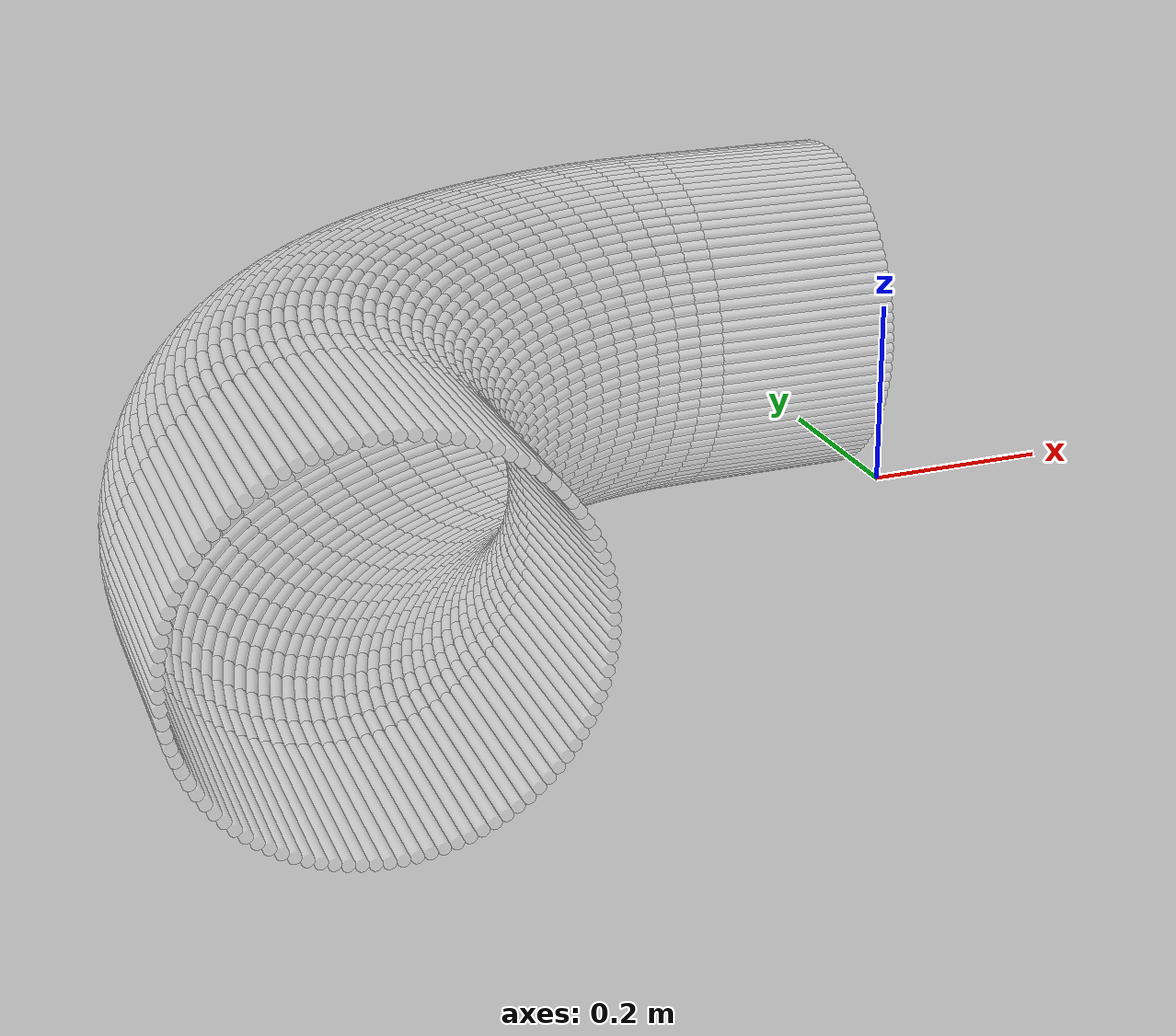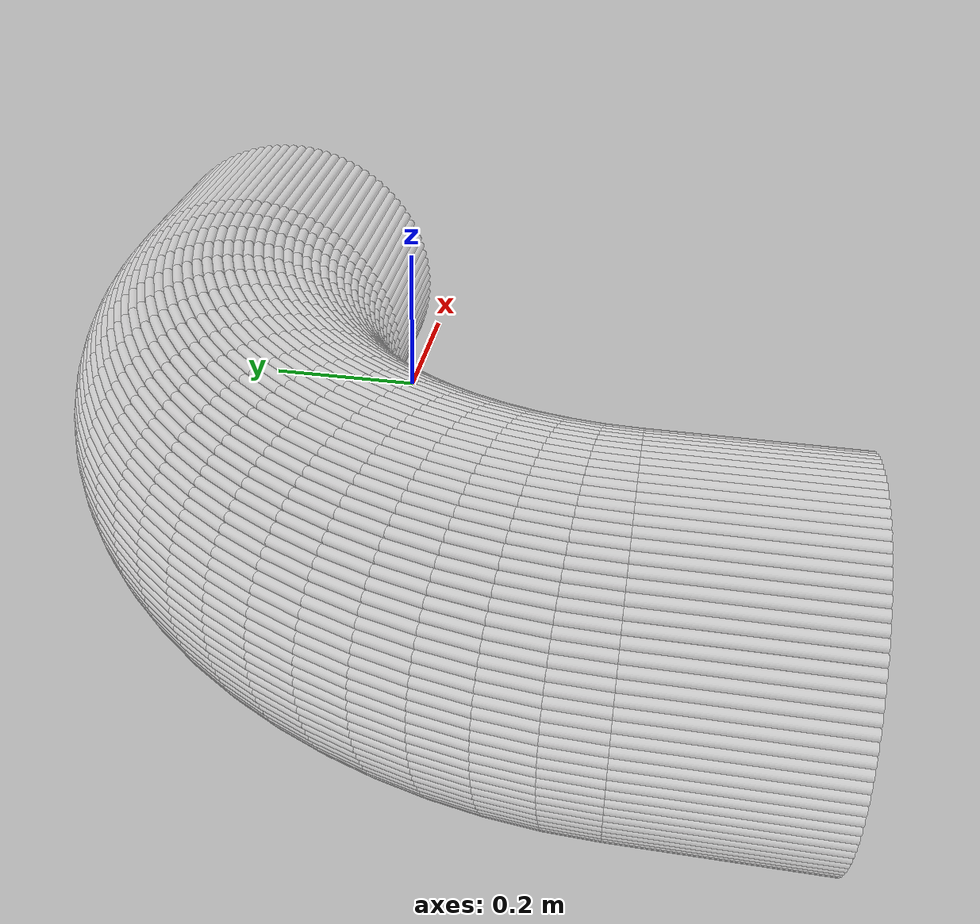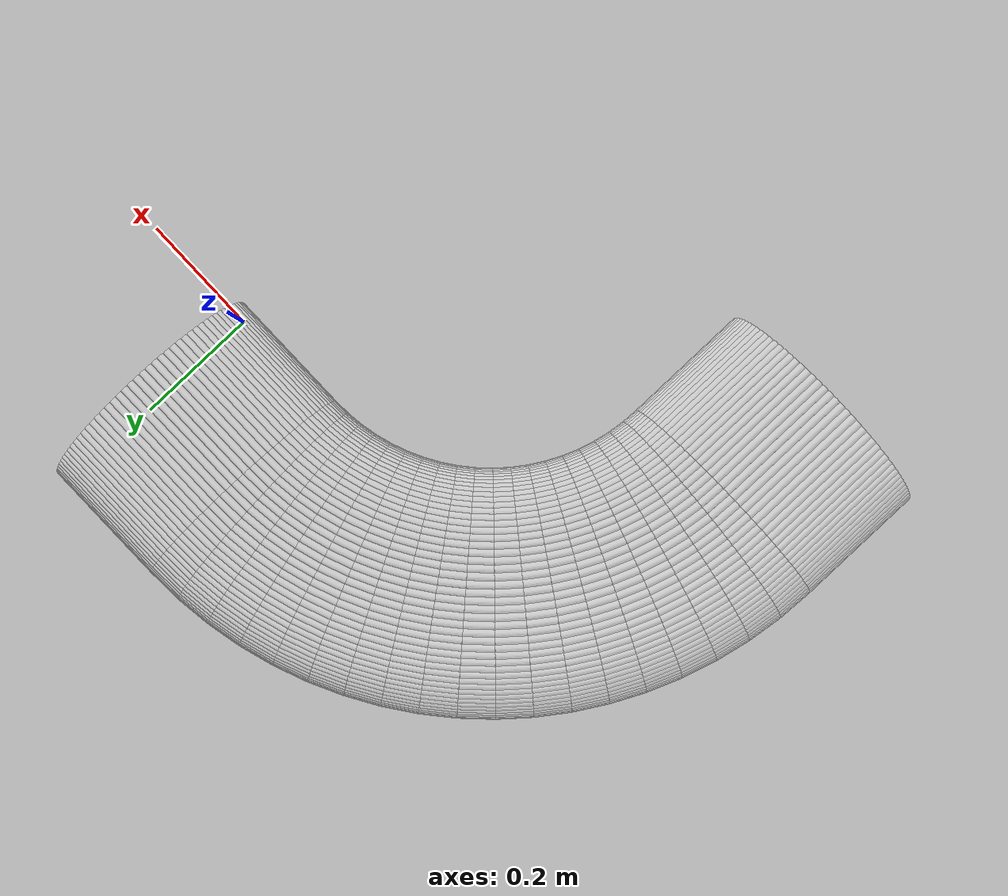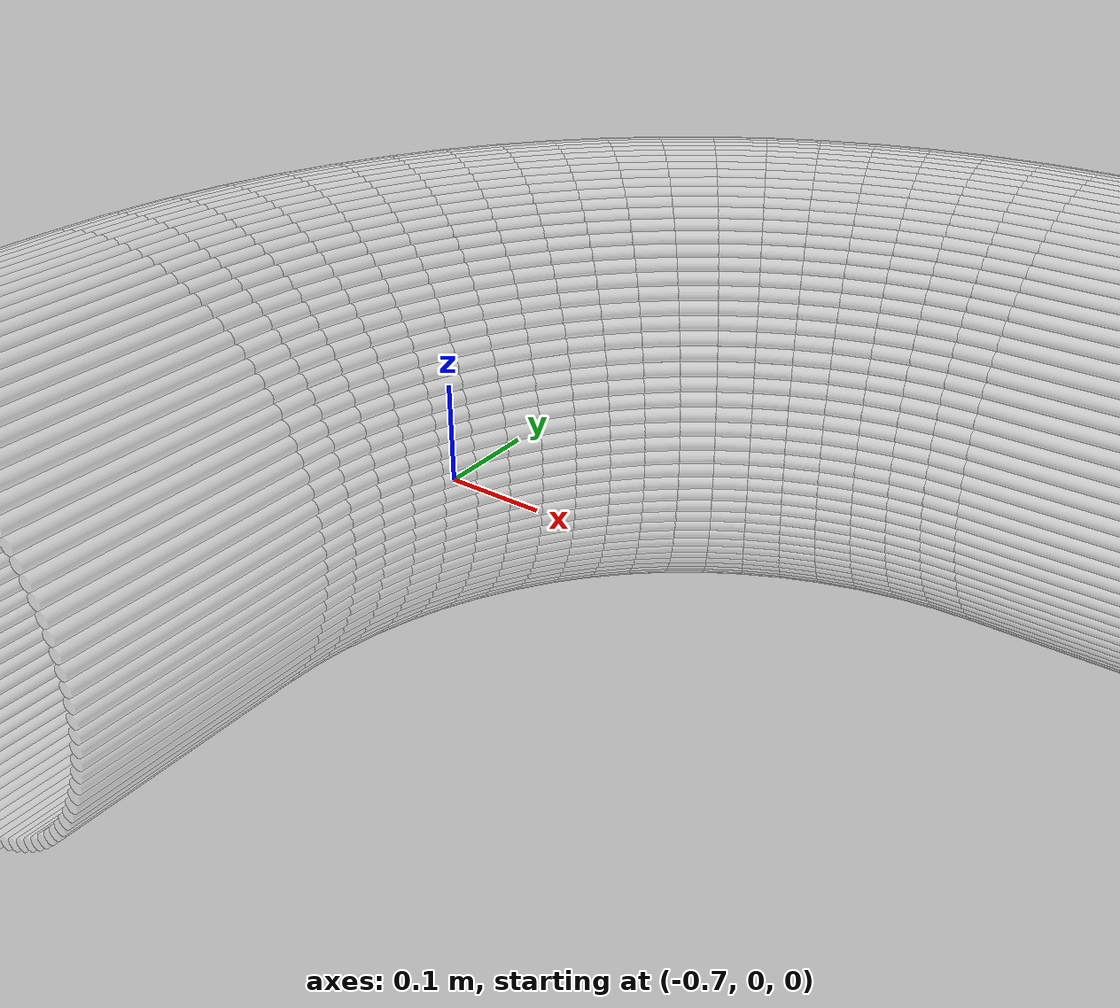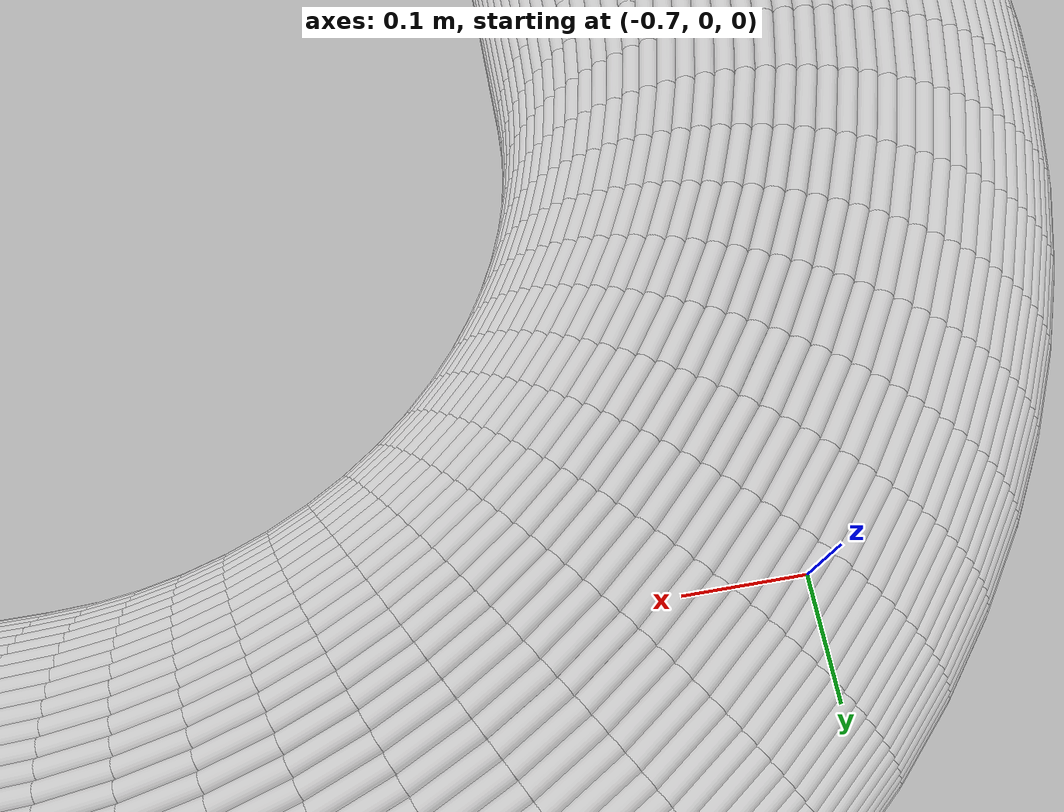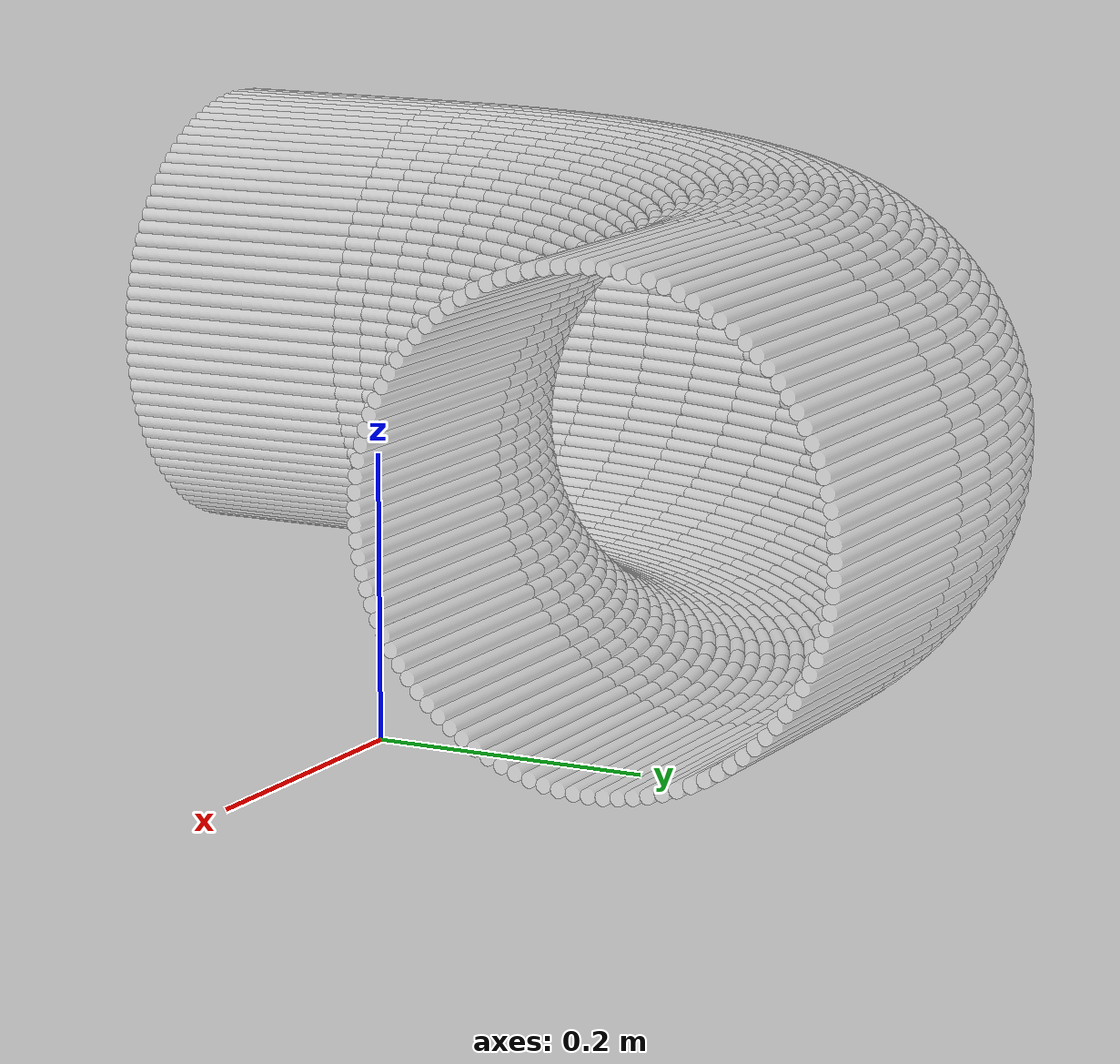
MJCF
<?xml version="1.0" encoding="utf-8"?>
<mujoco>
   <worldbody>
   <body pos="-0.2 -0.34 -0.02" euler="0 0 90">
      <geom euler=" 0 10 0 " fromto="0.68 -0.2 0.18 0.68 0 0.18" rgba="1 1 1 0.35"
            size="0.0056539"
            type="cylinder"/>
      <geom euler=" 0 20 0 " fromto="0.67964 -0.2 0.1913 0.67964 0 0.1913"
            rgba="1 1 1 0.35"
            size="0.0056539"
            type="cylinder"/>
      <geom euler=" 0 30 0 " fromto="0.67858 -0.2 0.20256 0.67858 0 0.20256"
            rgba="1 1 1 0.35"
            size="0.0056539"
            type="cylinder"/>
      <geom euler=" 0 40 0 " fromto="0.67681 -0.2 0.21373 0.67681 0 0.21373"
            rgba="1 1 1 0.35"
            size="0.0056539"
            type="cylinder"/>
      <geom euler=" 0 50 0 " fromto="0.67434 -0.2 0.22476 0.67434 0 0.22476"
            rgba="1 1 1 0.35"
            size="0.0056539"
            type="cylinder"/>
      <geom euler=" 0 60 0 " fromto="0.67119 -0.2 0.23562 0.67119 0 0.23562"
            rgba="1 1 1 0.35"
            size="0.0056539"
            type="cylinder"/>
      <geom euler=" 0 70 0 " fromto="0.66736 -0.2 0.24626 0.66736 0 0.24626"
            rgba="1 1 1 0.35"
            size="0.0056539"
            type="cylinder"/>
      <geom euler=" 0 80 0 " fromto="0.66287 -0.2 0.25664 0.66287 0 0.25664"
            rgba="1 1 1 0.35"
            size="0.0056539"
            type="cylinder"/>
      <geom euler=" 0 90 0 " fromto="0.65774 -0.2 0.26672 0.65774 0 0.26672"
            rgba="1 1 1 0.35"
            size="0.0056539"
            type="cylinder"/>
      <geom euler=" 0 100 0 " fromto="0.65198 -0.2 0.27645 0.65198 0 0.27645"
            rgba="1 1 1 0.35"
            size="0.0056539"
            type="cylinder"/>
      <geom euler=" 0 110 0 " fromto="0.64562 -0.2 0.2858 0.64562 0 0.2858"
            rgba="1 1 1 0.35"
            size="0.0056539"
            type="cylinder"/>
      <geom euler=" 0 120 0 " fromto="0.63869 -0.2 0.29474 0.63869 0 0.29474"
            rgba="1 1 1 0.35"
            size="0.0056539"
            type="cylinder"/>
      <geom euler=" 0 130 0 " fromto="0.63121 -0.2 0.30322 0.63121 0 0.30322"
            rgba="1 1 1 0.35"
            size="0.0056539"
            type="cylinder"/>
      <geom euler=" 0 140 0 " fromto="0.62322 -0.2 0.31121 0.62322 0 0.31121"
            rgba="1 1 1 0.35"
            size="0.0056539"
            type="cylinder"/>
      <geom euler=" 0 150 0 " fromto="0.61474 -0.2 0.31869 0.61474 0 0.31869"
            rgba="1 1 1 0.35"
            size="0.0056539"
            type="cylinder"/>
      <geom euler=" 0 160 0 " fromto="0.6058 -0.2 0.32562 0.6058 0 0.32562"
            rgba="1 1 1 0.35"
            size="0.0056539"
            type="cylinder"/>
      <geom euler=" 0 170 0 " fromto="0.59645 -0.2 0.33198 0.59645 0 0.33198"
            rgba="1 1 1 0.35"
            size="0.0056539"
            type="cylinder"/>
      <geom euler=" 0 180 0 " fromto="0.58672 -0.2 0.33774 0.58672 0 0.33774"
            rgba="1 1 1 0.35"
            size="0.0056539"
            type="cylinder"/>
      <geom euler=" 0 190 0 " fromto="0.57664 -0.2 0.34287 0.57664 0 0.34287"
            rgba="1 1 1 0.35"
            size="0.0056539"
            type="cylinder"/>
      <geom euler=" 0 200 0 " fromto="0.56626 -0.2 0.34736 0.56626 0 0.34736"
            rgba="1 1 1 0.35"
            size="0.0056539"
            type="cylinder"/>
      <geom euler=" 0 210 0 " fromto="0.55562 -0.2 0.35119 0.55562 0 0.35119"
            rgba="1 1 1 0.35"
            size="0.0056539"
            type="cylinder"/>
      <geom euler=" 0 220 0 " fromto="0.54476 -0.2 0.35434 0.54476 0 0.35434"
            rgba="1 1 1 0.35"
            size="0.0056539"
            type="cylinder"/>
      <geom euler=" 0 230 0 " fromto="0.53373 -0.2 0.35681 0.53373 0 0.35681"
            rgba="1 1 1 0.35"
            size="0.0056539"
            type="cylinder"/>
      <geom euler=" 0 240 0 " fromto="0.52256 -0.2 0.35858 0.52256 0 0.35858"
            rgba="1 1 1 0.35"
            size="0.0056539"
            type="cylinder"/>
      <geom euler=" 0 250 0 " fromto="0.5113 -0.2 0.35964 0.5113 0 0.35964"
            rgba="1 1 1 0.35"
            size="0.0056539"
            type="cylinder"/>
      <geom euler=" 0 260 0 " fromto="0.5 -0.2 0.36 0.5 0 0.36" rgba="1 1 1 0.35"
            size="0.0056539"
            type="cylinder"/>
      <geom euler=" 0 270 0 " fromto="0.4887 -0.2 0.35964 0.4887 0 0.35964"
            rgba="1 1 1 0.35"
            size="0.0056539"
            type="cylinder"/>
      <geom euler=" 0 280 0 " fromto="0.47744 -0.2 0.35858 0.47744 0 0.35858"
            rgba="1 1 1 0.35"
            size="0.0056539"
            type="cylinder"/>
      <geom euler=" 0 290 0 " fromto="0.46627 -0.2 0.35681 0.46627 0 0.35681"
            rgba="1 1 1 0.35"
            size="0.0056539"
            type="cylinder"/>
      <geom euler=" 0 300 0 " fromto="0.45524 -0.2 0.35434 0.45524 0 0.35434"
            rgba="1 1 1 0.35"
            size="0.0056539"
            type="cylinder"/>
      <geom euler=" 0 310 0 " fromto="0.44438 -0.2 0.35119 0.44438 0 0.35119"
            rgba="1 1 1 0.35"
            size="0.0056539"
            type="cylinder"/>
      <geom euler=" 0 320 0 " fromto="0.43374 -0.2 0.34736 0.43374 0 0.34736"
            rgba="1 1 1 0.35"
            size="0.0056539"
            type="cylinder"/>
      <geom euler=" 0 330 0 " fromto="0.42336 -0.2 0.34287 0.42336 0 0.34287"
            rgba="1 1 1 0.35"
            size="0.0056539"
            type="cylinder"/>
      <geom euler=" 0 340 0 " fromto="0.41328 -0.2 0.33774 0.41328 0 0.33774"
            rgba="1 1 1 0.35"
            size="0.0056539"
            type="cylinder"/>
      <geom euler=" 0 350 0 " fromto="0.40355 -0.2 0.33198 0.40355 0 0.33198"
            rgba="1 1 1 0.35"
            size="0.0056539"
            type="cylinder"/>
      <geom euler=" 0 360 0 " fromto="0.3942 -0.2 0.32562 0.3942 0 0.32562"
            rgba="1 1 1 0.35"
            size="0.0056539"
            type="cylinder"/>
      <geom euler=" 0 370 0 " fromto="0.38526 -0.2 0.31869 0.38526 0 0.31869"
            rgba="1 1 1 0.35"
            size="0.0056539"
            type="cylinder"/>
      <geom euler=" 0 380 0 " fromto="0.37678 -0.2 0.31121 0.37678 0 0.31121"
            rgba="1 1 1 0.35"
            size="0.0056539"
            type="cylinder"/>
      <geom euler=" 0 390 0 " fromto="0.36879 -0.2 0.30322 0.36879 0 0.30322"
            rgba="1 1 1 0.35"
            size="0.0056539"
            type="cylinder"/>
      <geom euler=" 0 400 0 " fromto="0.36131 -0.2 0.29474 0.36131 0 0.29474"
            rgba="1 1 1 0.35"
            size="0.0056539"
            type="cylinder"/>
      <geom euler=" 0 410 0 " fromto="0.35438 -0.2 0.2858 0.35438 0 0.2858"
            rgba="1 1 1 0.35"
            size="0.0056539"
            type="cylinder"/>
      <geom euler=" 0 420 0 " fromto="0.34802 -0.2 0.27645 0.34802 0 0.27645"
            rgba="1 1 1 0.35"
            size="0.0056539"
            type="cylinder"/>
      <geom euler=" 0 430 0 " fromto="0.34226 -0.2 0.26672 0.34226 0 0.26672"
            rgba="1 1 1 0.35"
            size="0.0056539"
            type="cylinder"/>
      <geom euler=" 0 440 0 " fromto="0.33713 -0.2 0.25664 0.33713 0 0.25664"
            rgba="1 1 1 0.35"
            size="0.0056539"
            type="cylinder"/>
      <geom euler=" 0 450 0 " fromto="0.33264 -0.2 0.24626 0.33264 0 0.24626"
            rgba="1 1 1 0.35"
            size="0.0056539"
            type="cylinder"/>
      <geom euler=" 0 460 0 " fromto="0.32881 -0.2 0.23562 0.32881 0 0.23562"
            rgba="1 1 1 0.35"
            size="0.0056539"
            type="cylinder"/>
      <geom euler=" 0 470 0 " fromto="0.32566 -0.2 0.22476 0.32566 0 0.22476"
            rgba="1 1 1 0.35"
            size="0.0056539"
            type="cylinder"/>
      <geom euler=" 0 480 0 " fromto="0.32319 -0.2 0.21373 0.32319 0 0.21373"
            rgba="1 1 1 0.35"
            size="0.0056539"
            type="cylinder"/>
      <geom euler=" 0 490 0 " fromto="0.32142 -0.2 0.20256 0.32142 0 0.20256"
            rgba="1 1 1 0.35"
            size="0.0056539"
            type="cylinder"/>
      <geom euler=" 0 500 0 " fromto="0.32036 -0.2 0.1913 0.32036 0 0.1913"
            rgba="1 1 1 0.35"
            size="0.0056539"
            type="cylinder"/>
      <geom euler=" 0 510 0 " fromto="0.32 -0.2 0.18 0.32 0 0.18" rgba="1 1 1 0.35"
            size="0.0056539"
            type="cylinder"/>
      <geom euler=" 0 520 0 " fromto="0.32036 -0.2 0.1687 0.32036 0 0.1687"
            rgba="1 1 1 0.35"
            size="0.0056539"
            type="cylinder"/>
      <geom euler=" 0 530 0 " fromto="0.32142 -0.2 0.15744 0.32142 0 0.15744"
            rgba="1 1 1 0.35"
            size="0.0056539"
            type="cylinder"/>
      <geom euler=" 0 540 0 " fromto="0.32319 -0.2 0.14627 0.32319 0 0.14627"
            rgba="1 1 1 0.35"
            size="0.0056539"
            type="cylinder"/>
      <geom euler=" 0 550 0 " fromto="0.32566 -0.2 0.13524 0.32566 0 0.13524"
            rgba="1 1 1 0.35"
            size="0.0056539"
            type="cylinder"/>
      <geom euler=" 0 560 0 " fromto="0.32881 -0.2 0.12438 0.32881 0 0.12438"
            rgba="1 1 1 0.35"
            size="0.0056539"
            type="cylinder"/>
      <geom euler=" 0 570 0 " fromto="0.33264 -0.2 0.11374 0.33264 0 0.11374"
            rgba="1 1 1 0.35"
            size="0.0056539"
            type="cylinder"/>
      <geom euler=" 0 580 0 " fromto="0.33713 -0.2 0.10336 0.33713 0 0.10336"
            rgba="1 1 1 0.35"
            size="0.0056539"
            type="cylinder"/>
      <geom euler=" 0 590 0 " fromto="0.34226 -0.2 0.093284 0.34226 0 0.093284"
            rgba="1 1 1 0.35"
            size="0.0056539"
            type="cylinder"/>
      <geom euler=" 0 600 0 " fromto="0.34802 -0.2 0.083551 0.34802 0 0.083551"
            rgba="1 1 1 0.35"
            size="0.0056539"
            type="cylinder"/>
      <geom euler=" 0 610 0 " fromto="0.35438 -0.2 0.074199 0.35438 0 0.074199"
            rgba="1 1 1 0.35"
            size="0.0056539"
            type="cylinder"/>
      <geom euler=" 0 620 0 " fromto="0.36131 -0.2 0.065264 0.36131 0 0.065264"
            rgba="1 1 1 0.35"
            size="0.0056539"
            type="cylinder"/>
      <geom euler=" 0 630 0 " fromto="0.36879 -0.2 0.056782 0.36879 0 0.056782"
            rgba="1 1 1 0.35"
            size="0.0056539"
            type="cylinder"/>
      <geom euler=" 0 640 0 " fromto="0.37678 -0.2 0.048786 0.37678 0 0.048786"
            rgba="1 1 1 0.35"
            size="0.0056539"
            type="cylinder"/>
      <geom euler=" 0 650 0 " fromto="0.38526 -0.2 0.041308 0.38526 0 0.041308"
            rgba="1 1 1 0.35"
            size="0.0056539"
            type="cylinder"/>
      <geom euler=" 0 660 0 " fromto="0.3942 -0.2 0.034377 0.3942 0 0.034377"
            rgba="1 1 1 0.35"
            size="0.0056539"
            type="cylinder"/>
      <geom euler=" 0 670 0 " fromto="0.40355 -0.2 0.028021 0.40355 0 0.028021"
            rgba="1 1 1 0.35"
            size="0.0056539"
            type="cylinder"/>
      <geom euler=" 0 680 0 " fromto="0.41328 -0.2 0.022265 0.41328 0 0.022265"
            rgba="1 1 1 0.35"
            size="0.0056539"
            type="cylinder"/>
      <geom euler=" 0 690 0 " fromto="0.42336 -0.2 0.017131 0.42336 0 0.017131"
            rgba="1 1 1 0.35"
            size="0.0056539"
            type="cylinder"/>
      <geom euler=" 0 700 0 " fromto="0.43374 -0.2 0.01264 0.43374 0 0.01264"
            rgba="1 1 1 0.35"
            size="0.0056539"
            type="cylinder"/>
      <geom euler=" 0 710 0 " fromto="0.44438 -0.2 0.0088098 0.44438 0 0.0088098"
            rgba="1 1 1 0.35"
            size="0.0056539"
            type="cylinder"/>
      <geom euler=" 0 720 0 " fromto="0.45524 -0.2 0.005655 0.45524 0 0.005655"
            rgba="1 1 1 0.35"
            size="0.0056539"
            type="cylinder"/>
      <geom euler=" 0 730 0 " fromto="0.46627 -0.2 0.0031883 0.46627 0 0.0031883"
            rgba="1 1 1 0.35"
            size="0.0056539"
            type="cylinder"/>
      <geom euler=" 0 740 0 " fromto="0.47744 -0.2 0.0014194 0.47744 0 0.0014194"
            rgba="1 1 1 0.35"
            size="0.0056539"
            type="cylinder"/>
      <geom euler=" 0 750 0 " fromto="0.4887 -0.2 0.00035519 0.4887 0 0.00035519"
            rgba="1 1 1 0.35"
            size="0.0056539"
            type="cylinder"/>
      <geom euler=" 0 760 0 " fromto="0.5 -0.2 0 0.5 0 0" rgba="1 1 1 0.35"
            size="0.0056539"
            type="cylinder"/>
      <geom euler=" 0 770 0 " fromto="0.5113 -0.2 0.00035519 0.5113 0 0.00035519"
            rgba="1 1 1 0.35"
            size="0.0056539"
            type="cylinder"/>
      <geom euler=" 0 780 0 " fromto="0.52256 -0.2 0.0014194 0.52256 0 0.0014194"
            rgba="1 1 1 0.35"
            size="0.0056539"
            type="cylinder"/>
      <geom euler=" 0 790 0 " fromto="0.53373 -0.2 0.0031883 0.53373 0 0.0031883"
            rgba="1 1 1 0.35"
            size="0.0056539"
            type="cylinder"/>
      <geom euler=" 0 800 0 " fromto="0.54476 -0.2 0.005655 0.54476 0 0.005655"
            rgba="1 1 1 0.35"
            size="0.0056539"
            type="cylinder"/>
      <geom euler=" 0 810 0 " fromto="0.55562 -0.2 0.0088098 0.55562 0 0.0088098"
            rgba="1 1 1 0.35"
            size="0.0056539"
            type="cylinder"/>
      <geom euler=" 0 820 0 " fromto="0.56626 -0.2 0.01264 0.56626 0 0.01264"
            rgba="1 1 1 0.35"
            size="0.0056539"
            type="cylinder"/>
      <geom euler=" 0 830 0 " fromto="0.57664 -0.2 0.017131 0.57664 0 0.017131"
            rgba="1 1 1 0.35"
            size="0.0056539"
            type="cylinder"/>
      <geom euler=" 0 840 0 " fromto="0.58672 -0.2 0.022265 0.58672 0 0.022265"
            rgba="1 1 1 0.35"
            size="0.0056539"
            type="cylinder"/>
      <geom euler=" 0 850 0 " fromto="0.59645 -0.2 0.028021 0.59645 0 0.028021"
            rgba="1 1 1 0.35"
            size="0.0056539"
            type="cylinder"/>
      <geom euler=" 0 860 0 " fromto="0.6058 -0.2 0.034377 0.6058 0 0.034377"
            rgba="1 1 1 0.35"
            size="0.0056539"
            type="cylinder"/>
      <geom euler=" 0 870 0 " fromto="0.61474 -0.2 0.041308 0.61474 0 0.041308"
            rgba="1 1 1 0.35"
            size="0.0056539"
            type="cylinder"/>
      <geom euler=" 0 880 0 " fromto="0.62322 -0.2 0.048786 0.62322 0 0.048786"
            rgba="1 1 1 0.35"
            size="0.0056539"
            type="cylinder"/>
      <geom euler=" 0 890 0 " fromto="0.63121 -0.2 0.056782 0.63121 0 0.056782"
            rgba="1 1 1 0.35"
            size="0.0056539"
            type="cylinder"/>
      <geom euler=" 0 900 0 " fromto="0.63869 -0.2 0.065264 0.63869 0 0.065264"
            rgba="1 1 1 0.35"
            size="0.0056539"
            type="cylinder"/>
      <geom euler=" 0 910 0 " fromto="0.64562 -0.2 0.074199 0.64562 0 0.074199"
            rgba="1 1 1 0.35"
            size="0.0056539"
            type="cylinder"/>
      <geom euler=" 0 920 0 " fromto="0.65198 -0.2 0.083551 0.65198 0 0.083551"
            rgba="1 1 1 0.35"
            size="0.0056539"
            type="cylinder"/>
      <geom euler=" 0 930 0 " fromto="0.65774 -0.2 0.093284 0.65774 0 0.093284"
            rgba="1 1 1 0.35"
            size="0.0056539"
            type="cylinder"/>
      <geom euler=" 0 940 0 " fromto="0.66287 -0.2 0.10336 0.66287 0 0.10336"
            rgba="1 1 1 0.35"
            size="0.0056539"
            type="cylinder"/>
      <geom euler=" 0 950 0 " fromto="0.66736 -0.2 0.11374 0.66736 0 0.11374"
            rgba="1 1 1 0.35"
            size="0.0056539"
            type="cylinder"/>
      <geom euler=" 0 960 0 " fromto="0.67119 -0.2 0.12438 0.67119 0 0.12438"
            rgba="1 1 1 0.35"
            size="0.0056539"
            type="cylinder"/>
      <geom euler=" 0 970 0 " fromto="0.67434 -0.2 0.13524 0.67434 0 0.13524"
            rgba="1 1 1 0.35"
            size="0.0056539"
            type="cylinder"/>
      <geom euler=" 0 980 0 " fromto="0.67681 -0.2 0.14627 0.67681 0 0.14627"
            rgba="1 1 1 0.35"
            size="0.0056539"
            type="cylinder"/>
      <geom euler=" 0 990 0 " fromto="0.67858 -0.2 0.15744 0.67858 0 0.15744"
            rgba="1 1 1 0.35"
            size="0.0056539"
            type="cylinder"/>
      <geom euler=" 0 1000 0 " fromto="0.67964 -0.2 0.1687 0.67964 0 0.1687"
            rgba="1 1 1 0.35"
            size="0.0056539"
            type="cylinder"/>
      <geom euler=" 0 10 0 " fromto="0.68 0 0.18 0.67768 0.056154 0.18" rgba="1 1 1 0.35"
            size="0.0056539"
            type="cylinder"/>
      <geom euler=" 0 20 0 " fromto="0.67964 0 0.1913 0.67732 0.056125 0.1913"
            rgba="1 1 1 0.35"
            size="0.0056539"
            type="cylinder"/>
      <geom euler=" 0 30 0 " fromto="0.67858 0 0.20256 0.67626 0.056037 0.20256"
            rgba="1 1 1 0.35"
            size="0.0056539"
            type="cylinder"/>
      <geom euler=" 0 40 0 " fromto="0.67681 0 0.21373 0.6745 0.055891 0.21373"
            rgba="1 1 1 0.35"
            size="0.0056539"
            type="cylinder"/>
      <geom euler=" 0 50 0 " fromto="0.67434 0 0.22476 0.67204 0.055687 0.22476"
            rgba="1 1 1 0.35"
            size="0.0056539"
            type="cylinder"/>
      <geom euler=" 0 60 0 " fromto="0.67119 0 0.23562 0.6689 0.055426 0.23562"
            rgba="1 1 1 0.35"
            size="0.0056539"
            type="cylinder"/>
      <geom euler=" 0 70 0 " fromto="0.66736 0 0.24626 0.66508 0.05511 0.24626"
            rgba="1 1 1 0.35"
            size="0.0056539"
            type="cylinder"/>
      <geom euler=" 0 80 0 " fromto="0.66287 0 0.25664 0.6606 0.054739 0.25664"
            rgba="1 1 1 0.35"
            size="0.0056539"
            type="cylinder"/>
      <geom euler=" 0 90 0 " fromto="0.65774 0 0.26672 0.65549 0.054315 0.26672"
            rgba="1 1 1 0.35"
            size="0.0056539"
            type="cylinder"/>
      <geom euler=" 0 100 0 " fromto="0.65198 0 0.27645 0.64975 0.05384 0.27645"
            rgba="1 1 1 0.35"
            size="0.0056539"
            type="cylinder"/>
      <geom euler=" 0 110 0 " fromto="0.64562 0 0.2858 0.64342 0.053315 0.2858"
            rgba="1 1 1 0.35"
            size="0.0056539"
            type="cylinder"/>
      <geom euler=" 0 120 0 " fromto="0.63869 0 0.29474 0.63651 0.052743 0.29474"
            rgba="1 1 1 0.35"
            size="0.0056539"
            type="cylinder"/>
      <geom euler=" 0 130 0 " fromto="0.63121 0 0.30322 0.62906 0.052125 0.30322"
            rgba="1 1 1 0.35"
            size="0.0056539"
            type="cylinder"/>
      <geom euler=" 0 140 0 " fromto="0.62322 0 0.31121 0.62109 0.051465 0.31121"
            rgba="1 1 1 0.35"
            size="0.0056539"
            type="cylinder"/>
      <geom euler=" 0 150 0 " fromto="0.61474 0 0.31869 0.61264 0.050765 0.31869"
            rgba="1 1 1 0.35"
            size="0.0056539"
            type="cylinder"/>
      <geom euler=" 0 160 0 " fromto="0.6058 0 0.32562 0.60373 0.050027 0.32562"
            rgba="1 1 1 0.35"
            size="0.0056539"
            type="cylinder"/>
      <geom euler=" 0 170 0 " fromto="0.59645 0 0.33198 0.59441 0.049254 0.33198"
            rgba="1 1 1 0.35"
            size="0.0056539"
            type="cylinder"/>
      <geom euler=" 0 180 0 " fromto="0.58672 0 0.33774 0.58471 0.048451 0.33774"
            rgba="1 1 1 0.35"
            size="0.0056539"
            type="cylinder"/>
      <geom euler=" 0 190 0 " fromto="0.57664 0 0.34287 0.57467 0.047619 0.34287"
            rgba="1 1 1 0.35"
            size="0.0056539"
            type="cylinder"/>
      <geom euler=" 0 200 0 " fromto="0.56626 0 0.34736 0.56433 0.046762 0.34736"
            rgba="1 1 1 0.35"
            size="0.0056539"
            type="cylinder"/>
      <geom euler=" 0 210 0 " fromto="0.55562 0 0.35119 0.55373 0.045883 0.35119"
            rgba="1 1 1 0.35"
            size="0.0056539"
            type="cylinder"/>
      <geom euler=" 0 220 0 " fromto="0.54476 0 0.35434 0.5429 0.044986 0.35434"
            rgba="1 1 1 0.35"
            size="0.0056539"
            type="cylinder"/>
      <geom euler=" 0 230 0 " fromto="0.53373 0 0.35681 0.53191 0.044075 0.35681"
            rgba="1 1 1 0.35"
            size="0.0056539"
            type="cylinder"/>
      <geom euler=" 0 240 0 " fromto="0.52256 0 0.35858 0.52078 0.043153 0.35858"
            rgba="1 1 1 0.35"
            size="0.0056539"
            type="cylinder"/>
      <geom euler=" 0 250 0 " fromto="0.5113 0 0.35964 0.50956 0.042223 0.35964"
            rgba="1 1 1 0.35"
            size="0.0056539"
            type="cylinder"/>
      <geom euler=" 0 260 0 " fromto="0.5 0 0.36 0.49829 0.04129 0.36" rgba="1 1 1 0.35"
            size="0.0056539"
            type="cylinder"/>
      <geom euler=" 0 270 0 " fromto="0.4887 0 0.35964 0.48703 0.040356 0.35964"
            rgba="1 1 1 0.35"
            size="0.0056539"
            type="cylinder"/>
      <geom euler=" 0 280 0 " fromto="0.47744 0 0.35858 0.47581 0.039427 0.35858"
            rgba="1 1 1 0.35"
            size="0.0056539"
            type="cylinder"/>
      <geom euler=" 0 290 0 " fromto="0.46627 0 0.35681 0.46468 0.038504 0.35681"
            rgba="1 1 1 0.35"
            size="0.0056539"
            type="cylinder"/>
      <geom euler=" 0 300 0 " fromto="0.45524 0 0.35434 0.45368 0.037593 0.35434"
            rgba="1 1 1 0.35"
            size="0.0056539"
            type="cylinder"/>
      <geom euler=" 0 310 0 " fromto="0.44438 0 0.35119 0.44286 0.036696 0.35119"
            rgba="1 1 1 0.35"
            size="0.0056539"
            type="cylinder"/>
      <geom euler=" 0 320 0 " fromto="0.43374 0 0.34736 0.43226 0.035818 0.34736"
            rgba="1 1 1 0.35"
            size="0.0056539"
            type="cylinder"/>
      <geom euler=" 0 330 0 " fromto="0.42336 0 0.34287 0.42191 0.034961 0.34287"
            rgba="1 1 1 0.35"
            size="0.0056539"
            type="cylinder"/>
      <geom euler=" 0 340 0 " fromto="0.41328 0 0.33774 0.41187 0.034129 0.33774"
            rgba="1 1 1 0.35"
            size="0.0056539"
            type="cylinder"/>
      <geom euler=" 0 350 0 " fromto="0.40355 0 0.33198 0.40217 0.033325 0.33198"
            rgba="1 1 1 0.35"
            size="0.0056539"
            type="cylinder"/>
      <geom euler=" 0 360 0 " fromto="0.3942 0 0.32562 0.39285 0.032553 0.32562"
            rgba="1 1 1 0.35"
            size="0.0056539"
            type="cylinder"/>
      <geom euler=" 0 370 0 " fromto="0.38526 0 0.31869 0.38395 0.031815 0.31869"
            rgba="1 1 1 0.35"
            size="0.0056539"
            type="cylinder"/>
      <geom euler=" 0 380 0 " fromto="0.37678 0 0.31121 0.37549 0.031114 0.31121"
            rgba="1 1 1 0.35"
            size="0.0056539"
            type="cylinder"/>
      <geom euler=" 0 390 0 " fromto="0.36879 0 0.30322 0.36753 0.030454 0.30322"
            rgba="1 1 1 0.35"
            size="0.0056539"
            type="cylinder"/>
      <geom euler=" 0 400 0 " fromto="0.36131 0 0.29474 0.36007 0.029837 0.29474"
            rgba="1 1 1 0.35"
            size="0.0056539"
            type="cylinder"/>
      <geom euler=" 0 410 0 " fromto="0.35438 0 0.2858 0.35317 0.029264 0.2858"
            rgba="1 1 1 0.35"
            size="0.0056539"
            type="cylinder"/>
      <geom euler=" 0 420 0 " fromto="0.34802 0 0.27645 0.34683 0.028739 0.27645"
            rgba="1 1 1 0.35"
            size="0.0056539"
            type="cylinder"/>
      <geom euler=" 0 430 0 " fromto="0.34226 0 0.26672 0.3411 0.028264 0.26672"
            rgba="1 1 1 0.35"
            size="0.0056539"
            type="cylinder"/>
      <geom euler=" 0 440 0 " fromto="0.33713 0 0.25664 0.33598 0.02784 0.25664"
            rgba="1 1 1 0.35"
            size="0.0056539"
            type="cylinder"/>
      <geom euler=" 0 450 0 " fromto="0.33264 0 0.24626 0.3315 0.027469 0.24626"
            rgba="1 1 1 0.35"
            size="0.0056539"
            type="cylinder"/>
      <geom euler=" 0 460 0 " fromto="0.32881 0 0.23562 0.32769 0.027153 0.23562"
            rgba="1 1 1 0.35"
            size="0.0056539"
            type="cylinder"/>
      <geom euler=" 0 470 0 " fromto="0.32566 0 0.22476 0.32454 0.026892 0.22476"
            rgba="1 1 1 0.35"
            size="0.0056539"
            type="cylinder"/>
      <geom euler=" 0 480 0 " fromto="0.32319 0 0.21373 0.32208 0.026689 0.21373"
            rgba="1 1 1 0.35"
            size="0.0056539"
            type="cylinder"/>
      <geom euler=" 0 490 0 " fromto="0.32142 0 0.20256 0.32032 0.026543 0.20256"
            rgba="1 1 1 0.35"
            size="0.0056539"
            type="cylinder"/>
      <geom euler=" 0 500 0 " fromto="0.32036 0 0.1913 0.31926 0.026455 0.1913"
            rgba="1 1 1 0.35"
            size="0.0056539"
            type="cylinder"/>
      <geom euler=" 0 510 0 " fromto="0.32 0 0.18 0.31891 0.026425 0.18" rgba="1 1 1 0.35"
            size="0.0056539"
            type="cylinder"/>
      <geom euler=" 0 520 0 " fromto="0.32036 0 0.1687 0.31926 0.026455 0.1687"
            rgba="1 1 1 0.35"
            size="0.0056539"
            type="cylinder"/>
      <geom euler=" 0 530 0 " fromto="0.32142 0 0.15744 0.32032 0.026543 0.15744"
            rgba="1 1 1 0.35"
            size="0.0056539"
            type="cylinder"/>
      <geom euler=" 0 540 0 " fromto="0.32319 0 0.14627 0.32208 0.026689 0.14627"
            rgba="1 1 1 0.35"
            size="0.0056539"
            type="cylinder"/>
      <geom euler=" 0 550 0 " fromto="0.32566 0 0.13524 0.32454 0.026892 0.13524"
            rgba="1 1 1 0.35"
            size="0.0056539"
            type="cylinder"/>
      <geom euler=" 0 560 0 " fromto="0.32881 0 0.12438 0.32769 0.027153 0.12438"
            rgba="1 1 1 0.35"
            size="0.0056539"
            type="cylinder"/>
      <geom euler=" 0 570 0 " fromto="0.33264 0 0.11374 0.3315 0.027469 0.11374"
            rgba="1 1 1 0.35"
            size="0.0056539"
            type="cylinder"/>
      <geom euler=" 0 580 0 " fromto="0.33713 0 0.10336 0.33598 0.02784 0.10336"
            rgba="1 1 1 0.35"
            size="0.0056539"
            type="cylinder"/>
      <geom euler=" 0 590 0 " fromto="0.34226 0 0.093284 0.3411 0.028264 0.093284"
            rgba="1 1 1 0.35"
            size="0.0056539"
            type="cylinder"/>
      <geom euler=" 0 600 0 " fromto="0.34802 0 0.083551 0.34683 0.028739 0.083551"
            rgba="1 1 1 0.35"
            size="0.0056539"
            type="cylinder"/>
      <geom euler=" 0 610 0 " fromto="0.35438 0 0.074199 0.35317 0.029264 0.074199"
            rgba="1 1 1 0.35"
            size="0.0056539"
            type="cylinder"/>
      <geom euler=" 0 620 0 " fromto="0.36131 0 0.065264 0.36007 0.029837 0.065264"
            rgba="1 1 1 0.35"
            size="0.0056539"
            type="cylinder"/>
      <geom euler=" 0 630 0 " fromto="0.36879 0 0.056782 0.36753 0.030454 0.056782"
            rgba="1 1 1 0.35"
            size="0.0056539"
            type="cylinder"/>
      <geom euler=" 0 640 0 " fromto="0.37678 0 0.048786 0.37549 0.031114 0.048786"
            rgba="1 1 1 0.35"
            size="0.0056539"
            type="cylinder"/>
      <geom euler=" 0 650 0 " fromto="0.38526 0 0.041308 0.38395 0.031815 0.041308"
            rgba="1 1 1 0.35"
            size="0.0056539"
            type="cylinder"/>
      <geom euler=" 0 660 0 " fromto="0.3942 0 0.034377 0.39285 0.032553 0.034377"
            rgba="1 1 1 0.35"
            size="0.0056539"
            type="cylinder"/>
      <geom euler=" 0 670 0 " fromto="0.40355 0 0.028021 0.40217 0.033325 0.028021"
            rgba="1 1 1 0.35"
            size="0.0056539"
            type="cylinder"/>
      <geom euler=" 0 680 0 " fromto="0.41328 0 0.022265 0.41187 0.034129 0.022265"
            rgba="1 1 1 0.35"
            size="0.0056539"
            type="cylinder"/>
      <geom euler=" 0 690 0 " fromto="0.42336 0 0.017131 0.42191 0.034961 0.017131"
            rgba="1 1 1 0.35"
            size="0.0056539"
            type="cylinder"/>
      <geom euler=" 0 700 0 " fromto="0.43374 0 0.01264 0.43226 0.035818 0.01264"
            rgba="1 1 1 0.35"
            size="0.0056539"
            type="cylinder"/>
      <geom euler=" 0 710 0 " fromto="0.44438 0 0.0088098 0.44286 0.036696 0.0088098"
            rgba="1 1 1 0.35"
            size="0.0056539"
            type="cylinder"/>
      <geom euler=" 0 720 0 " fromto="0.45524 0 0.005655 0.45368 0.037593 0.005655"
            rgba="1 1 1 0.35"
            size="0.0056539"
            type="cylinder"/>
      <geom euler=" 0 730 0 " fromto="0.46627 0 0.0031883 0.46468 0.038504 0.0031883"
            rgba="1 1 1 0.35"
            size="0.0056539"
            type="cylinder"/>
      <geom euler=" 0 740 0 " fromto="0.47744 0 0.0014194 0.47581 0.039427 0.0014194"
            rgba="1 1 1 0.35"
            size="0.0056539"
            type="cylinder"/>
      <geom euler=" 0 750 0 " fromto="0.4887 0 0.00035519 0.48703 0.040356 0.00035519"
            rgba="1 1 1 0.35"
            size="0.0056539"
            type="cylinder"/>
      <geom euler=" 0 760 0 " fromto="0.5 0 0 0.49829 0.04129 0" rgba="1 1 1 0.35"
            size="0.0056539"
            type="cylinder"/>
      <geom euler=" 0 770 0 " fromto="0.5113 0 0.00035519 0.50956 0.042223 0.00035519"
            rgba="1 1 1 0.35"
            size="0.0056539"
            type="cylinder"/>
      <geom euler=" 0 780 0 " fromto="0.52256 0 0.0014194 0.52078 0.043153 0.0014194"
            rgba="1 1 1 0.35"
            size="0.0056539"
            type="cylinder"/>
      <geom euler=" 0 790 0 " fromto="0.53373 0 0.0031883 0.53191 0.044075 0.0031883"
            rgba="1 1 1 0.35"
            size="0.0056539"
            type="cylinder"/>
      <geom euler=" 0 800 0 " fromto="0.54476 0 0.005655 0.5429 0.044986 0.005655"
            rgba="1 1 1 0.35"
            size="0.0056539"
            type="cylinder"/>
      <geom euler=" 0 810 0 " fromto="0.55562 0 0.0088098 0.55373 0.045883 0.0088098"
            rgba="1 1 1 0.35"
            size="0.0056539"
            type="cylinder"/>
      <geom euler=" 0 820 0 " fromto="0.56626 0 0.01264 0.56433 0.046762 0.01264"
            rgba="1 1 1 0.35"
            size="0.0056539"
            type="cylinder"/>
      <geom euler=" 0 830 0 " fromto="0.57664 0 0.017131 0.57467 0.047619 0.017131"
            rgba="1 1 1 0.35"
            size="0.0056539"
            type="cylinder"/>
      <geom euler=" 0 840 0 " fromto="0.58672 0 0.022265 0.58471 0.048451 0.022265"
            rgba="1 1 1 0.35"
            size="0.0056539"
            type="cylinder"/>
      <geom euler=" 0 850 0 " fromto="0.59645 0 0.028021 0.59441 0.049254 0.028021"
            rgba="1 1 1 0.35"
            size="0.0056539"
            type="cylinder"/>
      <geom euler=" 0 860 0 " fromto="0.6058 0 0.034377 0.60373 0.050027 0.034377"
            rgba="1 1 1 0.35"
            size="0.0056539"
            type="cylinder"/>
      <geom euler=" 0 870 0 " fromto="0.61474 0 0.041308 0.61264 0.050765 0.041308"
            rgba="1 1 1 0.35"
            size="0.0056539"
            type="cylinder"/>
      <geom euler=" 0 880 0 " fromto="0.62322 0 0.048786 0.62109 0.051465 0.048786"
            rgba="1 1 1 0.35"
            size="0.0056539"
            type="cylinder"/>
      <geom euler=" 0 890 0 " fromto="0.63121 0 0.056782 0.62906 0.052125 0.056782"
            rgba="1 1 1 0.35"
            size="0.0056539"
            type="cylinder"/>
      <geom euler=" 0 900 0 " fromto="0.63869 0 0.065264 0.63651 0.052743 0.065264"
            rgba="1 1 1 0.35"
            size="0.0056539"
            type="cylinder"/>
      <geom euler=" 0 910 0 " fromto="0.64562 0 0.074199 0.64342 0.053315 0.074199"
            rgba="1 1 1 0.35"
            size="0.0056539"
            type="cylinder"/>
      <geom euler=" 0 920 0 " fromto="0.65198 0 0.083551 0.64975 0.05384 0.083551"
            rgba="1 1 1 0.35"
            size="0.0056539"
            type="cylinder"/>
      <geom euler=" 0 930 0 " fromto="0.65774 0 0.093284 0.65549 0.054315 0.093284"
            rgba="1 1 1 0.35"
            size="0.0056539"
            type="cylinder"/>
      <geom euler=" 0 940 0 " fromto="0.66287 0 0.10336 0.6606 0.054739 0.10336"
            rgba="1 1 1 0.35"
            size="0.0056539"
            type="cylinder"/>
      <geom euler=" 0 950 0 " fromto="0.66736 0 0.11374 0.66508 0.05511 0.11374"
            rgba="1 1 1 0.35"
            size="0.0056539"
            type="cylinder"/>
      <geom euler=" 0 960 0 " fromto="0.67119 0 0.12438 0.6689 0.055426 0.12438"
            rgba="1 1 1 0.35"
            size="0.0056539"
            type="cylinder"/>
      <geom euler=" 0 970 0 " fromto="0.67434 0 0.13524 0.67204 0.055687 0.13524"
            rgba="1 1 1 0.35"
            size="0.0056539"
            type="cylinder"/>
      <geom euler=" 0 980 0 " fromto="0.67681 0 0.14627 0.6745 0.055891 0.14627"
            rgba="1 1 1 0.35"
            size="0.0056539"
            type="cylinder"/>
      <geom euler=" 0 990 0 " fromto="0.67858 0 0.15744 0.67626 0.056037 0.15744"
            rgba="1 1 1 0.35"
            size="0.0056539"
            type="cylinder"/>
      <geom euler=" 0 1000 0 " fromto="0.67964 0 0.1687 0.67732 0.056125 0.1687"
            rgba="1 1 1 0.35"
            size="0.0056539"
            type="cylinder"/>
      <geom euler=" 0 10 0 " fromto="0.67768 0.056154 0.18 0.67073 0.11192 0.18"
            rgba="1 1 1 0.35"
            size="0.0056539"
            type="cylinder"/>
      <geom euler=" 0 20 0 " fromto="0.67732 0.056125 0.1913 0.67038 0.11187 0.1913"
            rgba="1 1 1 0.35"
            size="0.0056539"
            type="cylinder"/>
      <geom euler=" 0 30 0 " fromto="0.67626 0.056037 0.20256 0.66933 0.11169 0.20256"
            rgba="1 1 1 0.35"
            size="0.0056539"
            type="cylinder"/>
      <geom euler=" 0 40 0 " fromto="0.6745 0.055891 0.21373 0.66758 0.1114 0.21373"
            rgba="1 1 1 0.35"
            size="0.0056539"
            type="cylinder"/>
      <geom euler=" 0 50 0 " fromto="0.67204 0.055687 0.22476 0.66515 0.11099 0.22476"
            rgba="1 1 1 0.35"
            size="0.0056539"
            type="cylinder"/>
      <geom euler=" 0 60 0 " fromto="0.6689 0.055426 0.23562 0.66204 0.11047 0.23562"
            rgba="1 1 1 0.35"
            size="0.0056539"
            type="cylinder"/>
      <geom euler=" 0 70 0 " fromto="0.66508 0.05511 0.24626 0.65826 0.10984 0.24626"
            rgba="1 1 1 0.35"
            size="0.0056539"
            type="cylinder"/>
      <geom euler=" 0 80 0 " fromto="0.6606 0.054739 0.25664 0.65383 0.1091 0.25664"
            rgba="1 1 1 0.35"
            size="0.0056539"
            type="cylinder"/>
      <geom euler=" 0 90 0 " fromto="0.65549 0.054315 0.26672 0.64876 0.10826 0.26672"
            rgba="1 1 1 0.35"
            size="0.0056539"
            type="cylinder"/>
      <geom euler=" 0 100 0 " fromto="0.64975 0.05384 0.27645 0.64309 0.10731 0.27645"
            rgba="1 1 1 0.35"
            size="0.0056539"
            type="cylinder"/>
      <geom euler=" 0 110 0 " fromto="0.64342 0.053315 0.2858 0.63682 0.10627 0.2858"
            rgba="1 1 1 0.35"
            size="0.0056539"
            type="cylinder"/>
      <geom euler=" 0 120 0 " fromto="0.63651 0.052743 0.29474 0.62998 0.10513 0.29474"
            rgba="1 1 1 0.35"
            size="0.0056539"
            type="cylinder"/>
      <geom euler=" 0 130 0 " fromto="0.62906 0.052125 0.30322 0.62261 0.10389 0.30322"
            rgba="1 1 1 0.35"
            size="0.0056539"
            type="cylinder"/>
      <geom euler=" 0 140 0 " fromto="0.62109 0.051465 0.31121 0.61472 0.10258 0.31121"
            rgba="1 1 1 0.35"
            size="0.0056539"
            type="cylinder"/>
      <geom euler=" 0 150 0 " fromto="0.61264 0.050765 0.31869 0.60635 0.10118 0.31869"
            rgba="1 1 1 0.35"
            size="0.0056539"
            type="cylinder"/>
      <geom euler=" 0 160 0 " fromto="0.60373 0.050027 0.32562 0.59754 0.099712 0.32562"
            rgba="1 1 1 0.35"
            size="0.0056539"
            type="cylinder"/>
      <geom euler=" 0 170 0 " fromto="0.59441 0.049254 0.33198 0.58831 0.098172 0.33198"
            rgba="1 1 1 0.35"
            size="0.0056539"
            type="cylinder"/>
      <geom euler=" 0 180 0 " fromto="0.58471 0.048451 0.33774 0.57871 0.09657 0.33774"
            rgba="1 1 1 0.35"
            size="0.0056539"
            type="cylinder"/>
      <geom euler=" 0 190 0 " fromto="0.57467 0.047619 0.34287 0.56878 0.094912 0.34287"
            rgba="1 1 1 0.35"
            size="0.0056539"
            type="cylinder"/>
      <geom euler=" 0 200 0 " fromto="0.56433 0.046762 0.34736 0.55854 0.093204 0.34736"
            rgba="1 1 1 0.35"
            size="0.0056539"
            type="cylinder"/>
      <geom euler=" 0 210 0 " fromto="0.55373 0.045883 0.35119 0.54805 0.091453 0.35119"
            rgba="1 1 1 0.35"
            size="0.0056539"
            type="cylinder"/>
      <geom euler=" 0 220 0 " fromto="0.5429 0.044986 0.35434 0.53733 0.089665 0.35434"
            rgba="1 1 1 0.35"
            size="0.0056539"
            type="cylinder"/>
      <geom euler=" 0 230 0 " fromto="0.53191 0.044075 0.35681 0.52645 0.087849 0.35681"
            rgba="1 1 1 0.35"
            size="0.0056539"
            type="cylinder"/>
      <geom euler=" 0 240 0 " fromto="0.52078 0.043153 0.35858 0.51543 0.086011 0.35858"
            rgba="1 1 1 0.35"
            size="0.0056539"
            type="cylinder"/>
      <geom euler=" 0 250 0 " fromto="0.50956 0.042223 0.35964 0.50433 0.084158 0.35964"
            rgba="1 1 1 0.35"
            size="0.0056539"
            type="cylinder"/>
      <geom euler=" 0 260 0 " fromto="0.49829 0.04129 0.36 0.49318 0.082297 0.36"
            rgba="1 1 1 0.35"
            size="0.0056539"
            type="cylinder"/>
      <geom euler=" 0 270 0 " fromto="0.48703 0.040356 0.35964 0.48203 0.080437 0.35964"
            rgba="1 1 1 0.35"
            size="0.0056539"
            type="cylinder"/>
      <geom euler=" 0 280 0 " fromto="0.47581 0.039427 0.35858 0.47093 0.078584 0.35858"
            rgba="1 1 1 0.35"
            size="0.0056539"
            type="cylinder"/>
      <geom euler=" 0 290 0 " fromto="0.46468 0.038504 0.35681 0.45991 0.076746 0.35681"
            rgba="1 1 1 0.35"
            size="0.0056539"
            type="cylinder"/>
      <geom euler=" 0 300 0 " fromto="0.45368 0.037593 0.35434 0.44903 0.074929 0.35434"
            rgba="1 1 1 0.35"
            size="0.0056539"
            type="cylinder"/>
      <geom euler=" 0 310 0 " fromto="0.44286 0.036696 0.35119 0.43832 0.073142 0.35119"
            rgba="1 1 1 0.35"
            size="0.0056539"
            type="cylinder"/>
      <geom euler=" 0 320 0 " fromto="0.43226 0.035818 0.34736 0.42782 0.071391 0.34736"
            rgba="1 1 1 0.35"
            size="0.0056539"
            type="cylinder"/>
      <geom euler=" 0 330 0 " fromto="0.42191 0.034961 0.34287 0.41759 0.069683 0.34287"
            rgba="1 1 1 0.35"
            size="0.0056539"
            type="cylinder"/>
      <geom euler=" 0 340 0 " fromto="0.41187 0.034129 0.33774 0.40765 0.068024 0.33774"
            rgba="1 1 1 0.35"
            size="0.0056539"
            type="cylinder"/>
      <geom euler=" 0 350 0 " fromto="0.40217 0.033325 0.33198 0.39805 0.066422 0.33198"
            rgba="1 1 1 0.35"
            size="0.0056539"
            type="cylinder"/>
      <geom euler=" 0 360 0 " fromto="0.39285 0.032553 0.32562 0.38882 0.064883 0.32562"
            rgba="1 1 1 0.35"
            size="0.0056539"
            type="cylinder"/>
      <geom euler=" 0 370 0 " fromto="0.38395 0.031815 0.31869 0.38001 0.063412 0.31869"
            rgba="1 1 1 0.35"
            size="0.0056539"
            type="cylinder"/>
      <geom euler=" 0 380 0 " fromto="0.37549 0.031114 0.31121 0.37164 0.062016 0.31121"
            rgba="1 1 1 0.35"
            size="0.0056539"
            type="cylinder"/>
      <geom euler=" 0 390 0 " fromto="0.36753 0.030454 0.30322 0.36376 0.0607 0.30322"
            rgba="1 1 1 0.35"
            size="0.0056539"
            type="cylinder"/>
      <geom euler=" 0 400 0 " fromto="0.36007 0.029837 0.29474 0.35638 0.059469 0.29474"
            rgba="1 1 1 0.35"
            size="0.0056539"
            type="cylinder"/>
      <geom euler=" 0 410 0 " fromto="0.35317 0.029264 0.2858 0.34954 0.058329 0.2858"
            rgba="1 1 1 0.35"
            size="0.0056539"
            type="cylinder"/>
      <geom euler=" 0 420 0 " fromto="0.34683 0.028739 0.27645 0.34327 0.057282 0.27645"
            rgba="1 1 1 0.35"
            size="0.0056539"
            type="cylinder"/>
      <geom euler=" 0 430 0 " fromto="0.3411 0.028264 0.26672 0.3376 0.056335 0.26672"
            rgba="1 1 1 0.35"
            size="0.0056539"
            type="cylinder"/>
      <geom euler=" 0 440 0 " fromto="0.33598 0.02784 0.25664 0.33253 0.05549 0.25664"
            rgba="1 1 1 0.35"
            size="0.0056539"
            type="cylinder"/>
      <geom euler=" 0 450 0 " fromto="0.3315 0.027469 0.24626 0.3281 0.054751 0.24626"
            rgba="1 1 1 0.35"
            size="0.0056539"
            type="cylinder"/>
      <geom euler=" 0 460 0 " fromto="0.32769 0.027153 0.23562 0.32433 0.05412 0.23562"
            rgba="1 1 1 0.35"
            size="0.0056539"
            type="cylinder"/>
      <geom euler=" 0 470 0 " fromto="0.32454 0.026892 0.22476 0.32121 0.053601 0.22476"
            rgba="1 1 1 0.35"
            size="0.0056539"
            type="cylinder"/>
      <geom euler=" 0 480 0 " fromto="0.32208 0.026689 0.21373 0.31878 0.053195 0.21373"
            rgba="1 1 1 0.35"
            size="0.0056539"
            type="cylinder"/>
      <geom euler=" 0 490 0 " fromto="0.32032 0.026543 0.20256 0.31704 0.052904 0.20256"
            rgba="1 1 1 0.35"
            size="0.0056539"
            type="cylinder"/>
      <geom euler=" 0 500 0 " fromto="0.31926 0.026455 0.1913 0.31599 0.052729 0.1913"
            rgba="1 1 1 0.35"
            size="0.0056539"
            type="cylinder"/>
      <geom euler=" 0 510 0 " fromto="0.31891 0.026425 0.18 0.31564 0.05267 0.18"
            rgba="1 1 1 0.35"
            size="0.0056539"
            type="cylinder"/>
      <geom euler=" 0 520 0 " fromto="0.31926 0.026455 0.1687 0.31599 0.052729 0.1687"
            rgba="1 1 1 0.35"
            size="0.0056539"
            type="cylinder"/>
      <geom euler=" 0 530 0 " fromto="0.32032 0.026543 0.15744 0.31704 0.052904 0.15744"
            rgba="1 1 1 0.35"
            size="0.0056539"
            type="cylinder"/>
      <geom euler=" 0 540 0 " fromto="0.32208 0.026689 0.14627 0.31878 0.053195 0.14627"
            rgba="1 1 1 0.35"
            size="0.0056539"
            type="cylinder"/>
      <geom euler=" 0 550 0 " fromto="0.32454 0.026892 0.13524 0.32121 0.053601 0.13524"
            rgba="1 1 1 0.35"
            size="0.0056539"
            type="cylinder"/>
      <geom euler=" 0 560 0 " fromto="0.32769 0.027153 0.12438 0.32433 0.05412 0.12438"
            rgba="1 1 1 0.35"
            size="0.0056539"
            type="cylinder"/>
      <geom euler=" 0 570 0 " fromto="0.3315 0.027469 0.11374 0.3281 0.054751 0.11374"
            rgba="1 1 1 0.35"
            size="0.0056539"
            type="cylinder"/>
      <geom euler=" 0 580 0 " fromto="0.33598 0.02784 0.10336 0.33253 0.05549 0.10336"
            rgba="1 1 1 0.35"
            size="0.0056539"
            type="cylinder"/>
      <geom euler=" 0 590 0 " fromto="0.3411 0.028264 0.093284 0.3376 0.056335 0.093284"
            rgba="1 1 1 0.35"
            size="0.0056539"
            type="cylinder"/>
      <geom euler=" 0 600 0 " fromto="0.34683 0.028739 0.083551 0.34327 0.057282 0.083551"
            rgba="1 1 1 0.35"
            size="0.0056539"
            type="cylinder"/>
      <geom euler=" 0 610 0 " fromto="0.35317 0.029264 0.074199 0.34954 0.058329 0.074199"
            rgba="1 1 1 0.35"
            size="0.0056539"
            type="cylinder"/>
      <geom euler=" 0 620 0 " fromto="0.36007 0.029837 0.065264 0.35638 0.059469 0.065264"
            rgba="1 1 1 0.35"
            size="0.0056539"
            type="cylinder"/>
      <geom euler=" 0 630 0 " fromto="0.36753 0.030454 0.056782 0.36376 0.0607 0.056782"
            rgba="1 1 1 0.35"
            size="0.0056539"
            type="cylinder"/>
      <geom euler=" 0 640 0 " fromto="0.37549 0.031114 0.048786 0.37164 0.062016 0.048786"
            rgba="1 1 1 0.35"
            size="0.0056539"
            type="cylinder"/>
      <geom euler=" 0 650 0 " fromto="0.38395 0.031815 0.041308 0.38001 0.063412 0.041308"
            rgba="1 1 1 0.35"
            size="0.0056539"
            type="cylinder"/>
      <geom euler=" 0 660 0 " fromto="0.39285 0.032553 0.034377 0.38882 0.064883 0.034377"
            rgba="1 1 1 0.35"
            size="0.0056539"
            type="cylinder"/>
      <geom euler=" 0 670 0 " fromto="0.40217 0.033325 0.028021 0.39805 0.066422 0.028021"
            rgba="1 1 1 0.35"
            size="0.0056539"
            type="cylinder"/>
      <geom euler=" 0 680 0 " fromto="0.41187 0.034129 0.022265 0.40765 0.068024 0.022265"
            rgba="1 1 1 0.35"
            size="0.0056539"
            type="cylinder"/>
      <geom euler=" 0 690 0 " fromto="0.42191 0.034961 0.017131 0.41759 0.069683 0.017131"
            rgba="1 1 1 0.35"
            size="0.0056539"
            type="cylinder"/>
      <geom euler=" 0 700 0 " fromto="0.43226 0.035818 0.01264 0.42782 0.071391 0.01264"
            rgba="1 1 1 0.35"
            size="0.0056539"
            type="cylinder"/>
      <geom euler=" 0 710 0 "
            fromto="0.44286 0.036696 0.0088098 0.43832 0.073142 0.0088098"
            rgba="1 1 1 0.35"
            size="0.0056539"
            type="cylinder"/>
      <geom euler=" 0 720 0 " fromto="0.45368 0.037593 0.005655 0.44903 0.074929 0.005655"
            rgba="1 1 1 0.35"
            size="0.0056539"
            type="cylinder"/>
      <geom euler=" 0 730 0 "
            fromto="0.46468 0.038504 0.0031883 0.45991 0.076746 0.0031883"
            rgba="1 1 1 0.35"
            size="0.0056539"
            type="cylinder"/>
      <geom euler=" 0 740 0 "
            fromto="0.47581 0.039427 0.0014194 0.47093 0.078584 0.0014194"
            rgba="1 1 1 0.35"
            size="0.0056539"
            type="cylinder"/>
      <geom euler=" 0 750 0 "
            fromto="0.48703 0.040356 0.00035519 0.48203 0.080437 0.00035519"
            rgba="1 1 1 0.35"
            size="0.0056539"
            type="cylinder"/>
      <geom euler=" 0 760 0 " fromto="0.49829 0.04129 0 0.49318 0.082297 0"
            rgba="1 1 1 0.35"
            size="0.0056539"
            type="cylinder"/>
      <geom euler=" 0 770 0 "
            fromto="0.50956 0.042223 0.00035519 0.50433 0.084158 0.00035519"
            rgba="1 1 1 0.35"
            size="0.0056539"
            type="cylinder"/>
      <geom euler=" 0 780 0 "
            fromto="0.52078 0.043153 0.0014194 0.51543 0.086011 0.0014194"
            rgba="1 1 1 0.35"
            size="0.0056539"
            type="cylinder"/>
      <geom euler=" 0 790 0 "
            fromto="0.53191 0.044075 0.0031883 0.52645 0.087849 0.0031883"
            rgba="1 1 1 0.35"
            size="0.0056539"
            type="cylinder"/>
      <geom euler=" 0 800 0 " fromto="0.5429 0.044986 0.005655 0.53733 0.089665 0.005655"
            rgba="1 1 1 0.35"
            size="0.0056539"
            type="cylinder"/>
      <geom euler=" 0 810 0 "
            fromto="0.55373 0.045883 0.0088098 0.54805 0.091453 0.0088098"
            rgba="1 1 1 0.35"
            size="0.0056539"
            type="cylinder"/>
      <geom euler=" 0 820 0 " fromto="0.56433 0.046762 0.01264 0.55854 0.093204 0.01264"
            rgba="1 1 1 0.35"
            size="0.0056539"
            type="cylinder"/>
      <geom euler=" 0 830 0 " fromto="0.57467 0.047619 0.017131 0.56878 0.094912 0.017131"
            rgba="1 1 1 0.35"
            size="0.0056539"
            type="cylinder"/>
      <geom euler=" 0 840 0 " fromto="0.58471 0.048451 0.022265 0.57871 0.09657 0.022265"
            rgba="1 1 1 0.35"
            size="0.0056539"
            type="cylinder"/>
      <geom euler=" 0 850 0 " fromto="0.59441 0.049254 0.028021 0.58831 0.098172 0.028021"
            rgba="1 1 1 0.35"
            size="0.0056539"
            type="cylinder"/>
      <geom euler=" 0 860 0 " fromto="0.60373 0.050027 0.034377 0.59754 0.099712 0.034377"
            rgba="1 1 1 0.35"
            size="0.0056539"
            type="cylinder"/>
      <geom euler=" 0 870 0 " fromto="0.61264 0.050765 0.041308 0.60635 0.10118 0.041308"
            rgba="1 1 1 0.35"
            size="0.0056539"
            type="cylinder"/>
      <geom euler=" 0 880 0 " fromto="0.62109 0.051465 0.048786 0.61472 0.10258 0.048786"
            rgba="1 1 1 0.35"
            size="0.0056539"
            type="cylinder"/>
      <geom euler=" 0 890 0 " fromto="0.62906 0.052125 0.056782 0.62261 0.10389 0.056782"
            rgba="1 1 1 0.35"
            size="0.0056539"
            type="cylinder"/>
      <geom euler=" 0 900 0 " fromto="0.63651 0.052743 0.065264 0.62998 0.10513 0.065264"
            rgba="1 1 1 0.35"
            size="0.0056539"
            type="cylinder"/>
      <geom euler=" 0 910 0 " fromto="0.64342 0.053315 0.074199 0.63682 0.10627 0.074199"
            rgba="1 1 1 0.35"
            size="0.0056539"
            type="cylinder"/>
      <geom euler=" 0 920 0 " fromto="0.64975 0.05384 0.083551 0.64309 0.10731 0.083551"
            rgba="1 1 1 0.35"
            size="0.0056539"
            type="cylinder"/>
      <geom euler=" 0 930 0 " fromto="0.65549 0.054315 0.093284 0.64876 0.10826 0.093284"
            rgba="1 1 1 0.35"
            size="0.0056539"
            type="cylinder"/>
      <geom euler=" 0 940 0 " fromto="0.6606 0.054739 0.10336 0.65383 0.1091 0.10336"
            rgba="1 1 1 0.35"
            size="0.0056539"
            type="cylinder"/>
      <geom euler=" 0 950 0 " fromto="0.66508 0.05511 0.11374 0.65826 0.10984 0.11374"
            rgba="1 1 1 0.35"
            size="0.0056539"
            type="cylinder"/>
      <geom euler=" 0 960 0 " fromto="0.6689 0.055426 0.12438 0.66204 0.11047 0.12438"
            rgba="1 1 1 0.35"
            size="0.0056539"
            type="cylinder"/>
      <geom euler=" 0 970 0 " fromto="0.67204 0.055687 0.13524 0.66515 0.11099 0.13524"
            rgba="1 1 1 0.35"
            size="0.0056539"
            type="cylinder"/>
      <geom euler=" 0 980 0 " fromto="0.6745 0.055891 0.14627 0.66758 0.1114 0.14627"
            rgba="1 1 1 0.35"
            size="0.0056539"
            type="cylinder"/>
      <geom euler=" 0 990 0 " fromto="0.67626 0.056037 0.15744 0.66933 0.11169 0.15744"
            rgba="1 1 1 0.35"
            size="0.0056539"
            type="cylinder"/>
      <geom euler=" 0 1000 0 " fromto="0.67732 0.056125 0.1687 0.67038 0.11187 0.1687"
            rgba="1 1 1 0.35"
            size="0.0056539"
            type="cylinder"/>
      <geom euler=" 0 10 0 " fromto="0.67073 0.11192 0.18 0.65919 0.16693 0.18"
            rgba="1 1 1 0.35"
            size="0.0056539"
            type="cylinder"/>
      <geom euler=" 0 20 0 " fromto="0.67038 0.11187 0.1913 0.65885 0.16684 0.1913"
            rgba="1 1 1 0.35"
            size="0.0056539"
            type="cylinder"/>
      <geom euler=" 0 30 0 " fromto="0.66933 0.11169 0.20256 0.65782 0.16658 0.20256"
            rgba="1 1 1 0.35"
            size="0.0056539"
            type="cylinder"/>
      <geom euler=" 0 40 0 " fromto="0.66758 0.1114 0.21373 0.6561 0.16615 0.21373"
            rgba="1 1 1 0.35"
            size="0.0056539"
            type="cylinder"/>
      <geom euler=" 0 50 0 " fromto="0.66515 0.11099 0.22476 0.65371 0.16554 0.22476"
            rgba="1 1 1 0.35"
            size="0.0056539"
            type="cylinder"/>
      <geom euler=" 0 60 0 " fromto="0.66204 0.11047 0.23562 0.65065 0.16477 0.23562"
            rgba="1 1 1 0.35"
            size="0.0056539"
            type="cylinder"/>
      <geom euler=" 0 70 0 " fromto="0.65826 0.10984 0.24626 0.64694 0.16383 0.24626"
            rgba="1 1 1 0.35"
            size="0.0056539"
            type="cylinder"/>
      <geom euler=" 0 80 0 " fromto="0.65383 0.1091 0.25664 0.64259 0.16272 0.25664"
            rgba="1 1 1 0.35"
            size="0.0056539"
            type="cylinder"/>
      <geom euler=" 0 90 0 " fromto="0.64876 0.10826 0.26672 0.63761 0.16146 0.26672"
            rgba="1 1 1 0.35"
            size="0.0056539"
            type="cylinder"/>
      <geom euler=" 0 100 0 " fromto="0.64309 0.10731 0.27645 0.63203 0.16005 0.27645"
            rgba="1 1 1 0.35"
            size="0.0056539"
            type="cylinder"/>
      <geom euler=" 0 110 0 " fromto="0.63682 0.10627 0.2858 0.62587 0.15849 0.2858"
            rgba="1 1 1 0.35"
            size="0.0056539"
            type="cylinder"/>
      <geom euler=" 0 120 0 " fromto="0.62998 0.10513 0.29474 0.61915 0.15679 0.29474"
            rgba="1 1 1 0.35"
            size="0.0056539"
            type="cylinder"/>
      <geom euler=" 0 130 0 " fromto="0.62261 0.10389 0.30322 0.6119 0.15495 0.30322"
            rgba="1 1 1 0.35"
            size="0.0056539"
            type="cylinder"/>
      <geom euler=" 0 140 0 " fromto="0.61472 0.10258 0.31121 0.60415 0.15299 0.31121"
            rgba="1 1 1 0.35"
            size="0.0056539"
            type="cylinder"/>
      <geom euler=" 0 150 0 " fromto="0.60635 0.10118 0.31869 0.59593 0.15091 0.31869"
            rgba="1 1 1 0.35"
            size="0.0056539"
            type="cylinder"/>
      <geom euler=" 0 160 0 " fromto="0.59754 0.099712 0.32562 0.58726 0.14872 0.32562"
            rgba="1 1 1 0.35"
            size="0.0056539"
            type="cylinder"/>
      <geom euler=" 0 170 0 " fromto="0.58831 0.098172 0.33198 0.5782 0.14642 0.33198"
            rgba="1 1 1 0.35"
            size="0.0056539"
            type="cylinder"/>
      <geom euler=" 0 180 0 " fromto="0.57871 0.09657 0.33774 0.56876 0.14403 0.33774"
            rgba="1 1 1 0.35"
            size="0.0056539"
            type="cylinder"/>
      <geom euler=" 0 190 0 " fromto="0.56878 0.094912 0.34287 0.559 0.14156 0.34287"
            rgba="1 1 1 0.35"
            size="0.0056539"
            type="cylinder"/>
      <geom euler=" 0 200 0 " fromto="0.55854 0.093204 0.34736 0.54893 0.13901 0.34736"
            rgba="1 1 1 0.35"
            size="0.0056539"
            type="cylinder"/>
      <geom euler=" 0 210 0 " fromto="0.54805 0.091453 0.35119 0.53862 0.1364 0.35119"
            rgba="1 1 1 0.35"
            size="0.0056539"
            type="cylinder"/>
      <geom euler=" 0 220 0 " fromto="0.53733 0.089665 0.35434 0.52809 0.13373 0.35434"
            rgba="1 1 1 0.35"
            size="0.0056539"
            type="cylinder"/>
      <geom euler=" 0 230 0 " fromto="0.52645 0.087849 0.35681 0.5174 0.13102 0.35681"
            rgba="1 1 1 0.35"
            size="0.0056539"
            type="cylinder"/>
      <geom euler=" 0 240 0 " fromto="0.51543 0.086011 0.35858 0.50657 0.12828 0.35858"
            rgba="1 1 1 0.35"
            size="0.0056539"
            type="cylinder"/>
      <geom euler=" 0 250 0 " fromto="0.50433 0.084158 0.35964 0.49566 0.12552 0.35964"
            rgba="1 1 1 0.35"
            size="0.0056539"
            type="cylinder"/>
      <geom euler=" 0 260 0 " fromto="0.49318 0.082297 0.36 0.4847 0.12274 0.36"
            rgba="1 1 1 0.35"
            size="0.0056539"
            type="cylinder"/>
      <geom euler=" 0 270 0 " fromto="0.48203 0.080437 0.35964 0.47374 0.11997 0.35964"
            rgba="1 1 1 0.35"
            size="0.0056539"
            type="cylinder"/>
      <geom euler=" 0 280 0 " fromto="0.47093 0.078584 0.35858 0.46283 0.1172 0.35858"
            rgba="1 1 1 0.35"
            size="0.0056539"
            type="cylinder"/>
      <geom euler=" 0 290 0 " fromto="0.45991 0.076746 0.35681 0.452 0.11446 0.35681"
            rgba="1 1 1 0.35"
            size="0.0056539"
            type="cylinder"/>
      <geom euler=" 0 300 0 " fromto="0.44903 0.074929 0.35434 0.44131 0.11175 0.35434"
            rgba="1 1 1 0.35"
            size="0.0056539"
            type="cylinder"/>
      <geom euler=" 0 310 0 " fromto="0.43832 0.073142 0.35119 0.43078 0.10909 0.35119"
            rgba="1 1 1 0.35"
            size="0.0056539"
            type="cylinder"/>
      <geom euler=" 0 320 0 " fromto="0.42782 0.071391 0.34736 0.42047 0.10648 0.34736"
            rgba="1 1 1 0.35"
            size="0.0056539"
            type="cylinder"/>
      <geom euler=" 0 330 0 " fromto="0.41759 0.069683 0.34287 0.41041 0.10393 0.34287"
            rgba="1 1 1 0.35"
            size="0.0056539"
            type="cylinder"/>
      <geom euler=" 0 340 0 " fromto="0.40765 0.068024 0.33774 0.40064 0.10146 0.33774"
            rgba="1 1 1 0.35"
            size="0.0056539"
            type="cylinder"/>
      <geom euler=" 0 350 0 " fromto="0.39805 0.066422 0.33198 0.3912 0.099066 0.33198"
            rgba="1 1 1 0.35"
            size="0.0056539"
            type="cylinder"/>
      <geom euler=" 0 360 0 " fromto="0.38882 0.064883 0.32562 0.38214 0.09677 0.32562"
            rgba="1 1 1 0.35"
            size="0.0056539"
            type="cylinder"/>
      <geom euler=" 0 370 0 " fromto="0.38001 0.063412 0.31869 0.37347 0.094577 0.31869"
            rgba="1 1 1 0.35"
            size="0.0056539"
            type="cylinder"/>
      <geom euler=" 0 380 0 " fromto="0.37164 0.062016 0.31121 0.36525 0.092494 0.31121"
            rgba="1 1 1 0.35"
            size="0.0056539"
            type="cylinder"/>
      <geom euler=" 0 390 0 " fromto="0.36376 0.0607 0.30322 0.3575 0.090532 0.30322"
            rgba="1 1 1 0.35"
            size="0.0056539"
            type="cylinder"/>
      <geom euler=" 0 400 0 " fromto="0.35638 0.059469 0.29474 0.35025 0.088696 0.29474"
            rgba="1 1 1 0.35"
            size="0.0056539"
            type="cylinder"/>
      <geom euler=" 0 410 0 " fromto="0.34954 0.058329 0.2858 0.34353 0.086994 0.2858"
            rgba="1 1 1 0.35"
            size="0.0056539"
            type="cylinder"/>
      <geom euler=" 0 420 0 " fromto="0.34327 0.057282 0.27645 0.33737 0.085434 0.27645"
            rgba="1 1 1 0.35"
            size="0.0056539"
            type="cylinder"/>
      <geom euler=" 0 430 0 " fromto="0.3376 0.056335 0.26672 0.33179 0.084021 0.26672"
            rgba="1 1 1 0.35"
            size="0.0056539"
            type="cylinder"/>
      <geom euler=" 0 440 0 " fromto="0.33253 0.05549 0.25664 0.32682 0.082761 0.25664"
            rgba="1 1 1 0.35"
            size="0.0056539"
            type="cylinder"/>
      <geom euler=" 0 450 0 " fromto="0.3281 0.054751 0.24626 0.32246 0.081658 0.24626"
            rgba="1 1 1 0.35"
            size="0.0056539"
            type="cylinder"/>
      <geom euler=" 0 460 0 " fromto="0.32433 0.05412 0.23562 0.31875 0.080718 0.23562"
            rgba="1 1 1 0.35"
            size="0.0056539"
            type="cylinder"/>
      <geom euler=" 0 470 0 " fromto="0.32121 0.053601 0.22476 0.31569 0.079944 0.22476"
            rgba="1 1 1 0.35"
            size="0.0056539"
            type="cylinder"/>
      <geom euler=" 0 480 0 " fromto="0.31878 0.053195 0.21373 0.3133 0.079338 0.21373"
            rgba="1 1 1 0.35"
            size="0.0056539"
            type="cylinder"/>
      <geom euler=" 0 490 0 " fromto="0.31704 0.052904 0.20256 0.31158 0.078904 0.20256"
            rgba="1 1 1 0.35"
            size="0.0056539"
            type="cylinder"/>
      <geom euler=" 0 500 0 " fromto="0.31599 0.052729 0.1913 0.31055 0.078643 0.1913"
            rgba="1 1 1 0.35"
            size="0.0056539"
            type="cylinder"/>
      <geom euler=" 0 510 0 " fromto="0.31564 0.05267 0.18 0.31021 0.078555 0.18"
            rgba="1 1 1 0.35"
            size="0.0056539"
            type="cylinder"/>
      <geom euler=" 0 520 0 " fromto="0.31599 0.052729 0.1687 0.31055 0.078643 0.1687"
            rgba="1 1 1 0.35"
            size="0.0056539"
            type="cylinder"/>
      <geom euler=" 0 530 0 " fromto="0.31704 0.052904 0.15744 0.31158 0.078904 0.15744"
            rgba="1 1 1 0.35"
            size="0.0056539"
            type="cylinder"/>
      <geom euler=" 0 540 0 " fromto="0.31878 0.053195 0.14627 0.3133 0.079338 0.14627"
            rgba="1 1 1 0.35"
            size="0.0056539"
            type="cylinder"/>
      <geom euler=" 0 550 0 " fromto="0.32121 0.053601 0.13524 0.31569 0.079944 0.13524"
            rgba="1 1 1 0.35"
            size="0.0056539"
            type="cylinder"/>
      <geom euler=" 0 560 0 " fromto="0.32433 0.05412 0.12438 0.31875 0.080718 0.12438"
            rgba="1 1 1 0.35"
            size="0.0056539"
            type="cylinder"/>
      <geom euler=" 0 570 0 " fromto="0.3281 0.054751 0.11374 0.32246 0.081658 0.11374"
            rgba="1 1 1 0.35"
            size="0.0056539"
            type="cylinder"/>
      <geom euler=" 0 580 0 " fromto="0.33253 0.05549 0.10336 0.32682 0.082761 0.10336"
            rgba="1 1 1 0.35"
            size="0.0056539"
            type="cylinder"/>
      <geom euler=" 0 590 0 " fromto="0.3376 0.056335 0.093284 0.33179 0.084021 0.093284"
            rgba="1 1 1 0.35"
            size="0.0056539"
            type="cylinder"/>
      <geom euler=" 0 600 0 " fromto="0.34327 0.057282 0.083551 0.33737 0.085434 0.083551"
            rgba="1 1 1 0.35"
            size="0.0056539"
            type="cylinder"/>
      <geom euler=" 0 610 0 " fromto="0.34954 0.058329 0.074199 0.34353 0.086994 0.074199"
            rgba="1 1 1 0.35"
            size="0.0056539"
            type="cylinder"/>
      <geom euler=" 0 620 0 " fromto="0.35638 0.059469 0.065264 0.35025 0.088696 0.065264"
            rgba="1 1 1 0.35"
            size="0.0056539"
            type="cylinder"/>
      <geom euler=" 0 630 0 " fromto="0.36376 0.0607 0.056782 0.3575 0.090532 0.056782"
            rgba="1 1 1 0.35"
            size="0.0056539"
            type="cylinder"/>
      <geom euler=" 0 640 0 " fromto="0.37164 0.062016 0.048786 0.36525 0.092494 0.048786"
            rgba="1 1 1 0.35"
            size="0.0056539"
            type="cylinder"/>
      <geom euler=" 0 650 0 " fromto="0.38001 0.063412 0.041308 0.37347 0.094577 0.041308"
            rgba="1 1 1 0.35"
            size="0.0056539"
            type="cylinder"/>
      <geom euler=" 0 660 0 " fromto="0.38882 0.064883 0.034377 0.38214 0.09677 0.034377"
            rgba="1 1 1 0.35"
            size="0.0056539"
            type="cylinder"/>
      <geom euler=" 0 670 0 " fromto="0.39805 0.066422 0.028021 0.3912 0.099066 0.028021"
            rgba="1 1 1 0.35"
            size="0.0056539"
            type="cylinder"/>
      <geom euler=" 0 680 0 " fromto="0.40765 0.068024 0.022265 0.40064 0.10146 0.022265"
            rgba="1 1 1 0.35"
            size="0.0056539"
            type="cylinder"/>
      <geom euler=" 0 690 0 " fromto="0.41759 0.069683 0.017131 0.41041 0.10393 0.017131"
            rgba="1 1 1 0.35"
            size="0.0056539"
            type="cylinder"/>
      <geom euler=" 0 700 0 " fromto="0.42782 0.071391 0.01264 0.42047 0.10648 0.01264"
            rgba="1 1 1 0.35"
            size="0.0056539"
            type="cylinder"/>
      <geom euler=" 0 710 0 " fromto="0.43832 0.073142 0.0088098 0.43078 0.10909 0.0088098"
            rgba="1 1 1 0.35"
            size="0.0056539"
            type="cylinder"/>
      <geom euler=" 0 720 0 " fromto="0.44903 0.074929 0.005655 0.44131 0.11175 0.005655"
            rgba="1 1 1 0.35"
            size="0.0056539"
            type="cylinder"/>
      <geom euler=" 0 730 0 " fromto="0.45991 0.076746 0.0031883 0.452 0.11446 0.0031883"
            rgba="1 1 1 0.35"
            size="0.0056539"
            type="cylinder"/>
      <geom euler=" 0 740 0 " fromto="0.47093 0.078584 0.0014194 0.46283 0.1172 0.0014194"
            rgba="1 1 1 0.35"
            size="0.0056539"
            type="cylinder"/>
      <geom euler=" 0 750 0 "
            fromto="0.48203 0.080437 0.00035519 0.47374 0.11997 0.00035519"
            rgba="1 1 1 0.35"
            size="0.0056539"
            type="cylinder"/>
      <geom euler=" 0 760 0 " fromto="0.49318 0.082297 0 0.4847 0.12274 0"
            rgba="1 1 1 0.35"
            size="0.0056539"
            type="cylinder"/>
      <geom euler=" 0 770 0 "
            fromto="0.50433 0.084158 0.00035519 0.49566 0.12552 0.00035519"
            rgba="1 1 1 0.35"
            size="0.0056539"
            type="cylinder"/>
      <geom euler=" 0 780 0 " fromto="0.51543 0.086011 0.0014194 0.50657 0.12828 0.0014194"
            rgba="1 1 1 0.35"
            size="0.0056539"
            type="cylinder"/>
      <geom euler=" 0 790 0 " fromto="0.52645 0.087849 0.0031883 0.5174 0.13102 0.0031883"
            rgba="1 1 1 0.35"
            size="0.0056539"
            type="cylinder"/>
      <geom euler=" 0 800 0 " fromto="0.53733 0.089665 0.005655 0.52809 0.13373 0.005655"
            rgba="1 1 1 0.35"
            size="0.0056539"
            type="cylinder"/>
      <geom euler=" 0 810 0 " fromto="0.54805 0.091453 0.0088098 0.53862 0.1364 0.0088098"
            rgba="1 1 1 0.35"
            size="0.0056539"
            type="cylinder"/>
      <geom euler=" 0 820 0 " fromto="0.55854 0.093204 0.01264 0.54893 0.13901 0.01264"
            rgba="1 1 1 0.35"
            size="0.0056539"
            type="cylinder"/>
      <geom euler=" 0 830 0 " fromto="0.56878 0.094912 0.017131 0.559 0.14156 0.017131"
            rgba="1 1 1 0.35"
            size="0.0056539"
            type="cylinder"/>
      <geom euler=" 0 840 0 " fromto="0.57871 0.09657 0.022265 0.56876 0.14403 0.022265"
            rgba="1 1 1 0.35"
            size="0.0056539"
            type="cylinder"/>
      <geom euler=" 0 850 0 " fromto="0.58831 0.098172 0.028021 0.5782 0.14642 0.028021"
            rgba="1 1 1 0.35"
            size="0.0056539"
            type="cylinder"/>
      <geom euler=" 0 860 0 " fromto="0.59754 0.099712 0.034377 0.58726 0.14872 0.034377"
            rgba="1 1 1 0.35"
            size="0.0056539"
            type="cylinder"/>
      <geom euler=" 0 870 0 " fromto="0.60635 0.10118 0.041308 0.59593 0.15091 0.041308"
            rgba="1 1 1 0.35"
            size="0.0056539"
            type="cylinder"/>
      <geom euler=" 0 880 0 " fromto="0.61472 0.10258 0.048786 0.60415 0.15299 0.048786"
            rgba="1 1 1 0.35"
            size="0.0056539"
            type="cylinder"/>
      <geom euler=" 0 890 0 " fromto="0.62261 0.10389 0.056782 0.6119 0.15495 0.056782"
            rgba="1 1 1 0.35"
            size="0.0056539"
            type="cylinder"/>
      <geom euler=" 0 900 0 " fromto="0.62998 0.10513 0.065264 0.61915 0.15679 0.065264"
            rgba="1 1 1 0.35"
            size="0.0056539"
            type="cylinder"/>
      <geom euler=" 0 910 0 " fromto="0.63682 0.10627 0.074199 0.62587 0.15849 0.074199"
            rgba="1 1 1 0.35"
            size="0.0056539"
            type="cylinder"/>
      <geom euler=" 0 920 0 " fromto="0.64309 0.10731 0.083551 0.63203 0.16005 0.083551"
            rgba="1 1 1 0.35"
            size="0.0056539"
            type="cylinder"/>
      <geom euler=" 0 930 0 " fromto="0.64876 0.10826 0.093284 0.63761 0.16146 0.093284"
            rgba="1 1 1 0.35"
            size="0.0056539"
            type="cylinder"/>
      <geom euler=" 0 940 0 " fromto="0.65383 0.1091 0.10336 0.64259 0.16272 0.10336"
            rgba="1 1 1 0.35"
            size="0.0056539"
            type="cylinder"/>
      <geom euler=" 0 950 0 " fromto="0.65826 0.10984 0.11374 0.64694 0.16383 0.11374"
            rgba="1 1 1 0.35"
            size="0.0056539"
            type="cylinder"/>
      <geom euler=" 0 960 0 " fromto="0.66204 0.11047 0.12438 0.65065 0.16477 0.12438"
            rgba="1 1 1 0.35"
            size="0.0056539"
            type="cylinder"/>
      <geom euler=" 0 970 0 " fromto="0.66515 0.11099 0.13524 0.65371 0.16554 0.13524"
            rgba="1 1 1 0.35"
            size="0.0056539"
            type="cylinder"/>
      <geom euler=" 0 980 0 " fromto="0.66758 0.1114 0.14627 0.6561 0.16615 0.14627"
            rgba="1 1 1 0.35"
            size="0.0056539"
            type="cylinder"/>
      <geom euler=" 0 990 0 " fromto="0.66933 0.11169 0.15744 0.65782 0.16658 0.15744"
            rgba="1 1 1 0.35"
            size="0.0056539"
            type="cylinder"/>
      <geom euler=" 0 1000 0 " fromto="0.67038 0.11187 0.1687 0.65885 0.16684 0.1687"
            rgba="1 1 1 0.35"
            size="0.0056539"
            type="cylinder"/>
      <geom euler=" 0 10 0 " fromto="0.65919 0.16693 0.18 0.64316 0.2208 0.18"
            rgba="1 1 1 0.35"
            size="0.0056539"
            type="cylinder"/>
      <geom euler=" 0 20 0 " fromto="0.65885 0.16684 0.1913 0.64282 0.22068 0.1913"
            rgba="1 1 1 0.35"
            size="0.0056539"
            type="cylinder"/>
      <geom euler=" 0 30 0 " fromto="0.65782 0.16658 0.20256 0.64181 0.22033 0.20256"
            rgba="1 1 1 0.35"
            size="0.0056539"
            type="cylinder"/>
      <geom euler=" 0 40 0 " fromto="0.6561 0.16615 0.21373 0.64014 0.21976 0.21373"
            rgba="1 1 1 0.35"
            size="0.0056539"
            type="cylinder"/>
      <geom euler=" 0 50 0 " fromto="0.65371 0.16554 0.22476 0.63781 0.21896 0.22476"
            rgba="1 1 1 0.35"
            size="0.0056539"
            type="cylinder"/>
      <geom euler=" 0 60 0 " fromto="0.65065 0.16477 0.23562 0.63482 0.21794 0.23562"
            rgba="1 1 1 0.35"
            size="0.0056539"
            type="cylinder"/>
      <geom euler=" 0 70 0 " fromto="0.64694 0.16383 0.24626 0.6312 0.21669 0.24626"
            rgba="1 1 1 0.35"
            size="0.0056539"
            type="cylinder"/>
      <geom euler=" 0 80 0 " fromto="0.64259 0.16272 0.25664 0.62695 0.21523 0.25664"
            rgba="1 1 1 0.35"
            size="0.0056539"
            type="cylinder"/>
      <geom euler=" 0 90 0 " fromto="0.63761 0.16146 0.26672 0.6221 0.21357 0.26672"
            rgba="1 1 1 0.35"
            size="0.0056539"
            type="cylinder"/>
      <geom euler=" 0 100 0 " fromto="0.63203 0.16005 0.27645 0.61665 0.2117 0.27645"
            rgba="1 1 1 0.35"
            size="0.0056539"
            type="cylinder"/>
      <geom euler=" 0 110 0 " fromto="0.62587 0.15849 0.2858 0.61064 0.20963 0.2858"
            rgba="1 1 1 0.35"
            size="0.0056539"
            type="cylinder"/>
      <geom euler=" 0 120 0 " fromto="0.61915 0.15679 0.29474 0.60409 0.20738 0.29474"
            rgba="1 1 1 0.35"
            size="0.0056539"
            type="cylinder"/>
      <geom euler=" 0 130 0 " fromto="0.6119 0.15495 0.30322 0.59701 0.20495 0.30322"
            rgba="1 1 1 0.35"
            size="0.0056539"
            type="cylinder"/>
      <geom euler=" 0 140 0 " fromto="0.60415 0.15299 0.31121 0.58945 0.20236 0.31121"
            rgba="1 1 1 0.35"
            size="0.0056539"
            type="cylinder"/>
      <geom euler=" 0 150 0 " fromto="0.59593 0.15091 0.31869 0.58143 0.1996 0.31869"
            rgba="1 1 1 0.35"
            size="0.0056539"
            type="cylinder"/>
      <geom euler=" 0 160 0 " fromto="0.58726 0.14872 0.32562 0.57298 0.1967 0.32562"
            rgba="1 1 1 0.35"
            size="0.0056539"
            type="cylinder"/>
      <geom euler=" 0 170 0 " fromto="0.5782 0.14642 0.33198 0.56413 0.19367 0.33198"
            rgba="1 1 1 0.35"
            size="0.0056539"
            type="cylinder"/>
      <geom euler=" 0 180 0 " fromto="0.56876 0.14403 0.33774 0.55493 0.19051 0.33774"
            rgba="1 1 1 0.35"
            size="0.0056539"
            type="cylinder"/>
      <geom euler=" 0 190 0 " fromto="0.559 0.14156 0.34287 0.5454 0.18723 0.34287"
            rgba="1 1 1 0.35"
            size="0.0056539"
            type="cylinder"/>
      <geom euler=" 0 200 0 " fromto="0.54893 0.13901 0.34736 0.53558 0.18387 0.34736"
            rgba="1 1 1 0.35"
            size="0.0056539"
            type="cylinder"/>
      <geom euler=" 0 210 0 " fromto="0.53862 0.1364 0.35119 0.52552 0.18041 0.35119"
            rgba="1 1 1 0.35"
            size="0.0056539"
            type="cylinder"/>
      <geom euler=" 0 220 0 " fromto="0.52809 0.13373 0.35434 0.51525 0.17688 0.35434"
            rgba="1 1 1 0.35"
            size="0.0056539"
            type="cylinder"/>
      <geom euler=" 0 230 0 " fromto="0.5174 0.13102 0.35681 0.50481 0.1733 0.35681"
            rgba="1 1 1 0.35"
            size="0.0056539"
            type="cylinder"/>
      <geom euler=" 0 240 0 " fromto="0.50657 0.12828 0.35858 0.49425 0.16967 0.35858"
            rgba="1 1 1 0.35"
            size="0.0056539"
            type="cylinder"/>
      <geom euler=" 0 250 0 " fromto="0.49566 0.12552 0.35964 0.4836 0.16602 0.35964"
            rgba="1 1 1 0.35"
            size="0.0056539"
            type="cylinder"/>
      <geom euler=" 0 260 0 " fromto="0.4847 0.12274 0.36 0.47291 0.16235 0.36"
            rgba="1 1 1 0.35"
            size="0.0056539"
            type="cylinder"/>
      <geom euler=" 0 270 0 " fromto="0.47374 0.11997 0.35964 0.46222 0.15868 0.35964"
            rgba="1 1 1 0.35"
            size="0.0056539"
            type="cylinder"/>
      <geom euler=" 0 280 0 " fromto="0.46283 0.1172 0.35858 0.45157 0.15502 0.35858"
            rgba="1 1 1 0.35"
            size="0.0056539"
            type="cylinder"/>
      <geom euler=" 0 290 0 " fromto="0.452 0.11446 0.35681 0.44101 0.1514 0.35681"
            rgba="1 1 1 0.35"
            size="0.0056539"
            type="cylinder"/>
      <geom euler=" 0 300 0 " fromto="0.44131 0.11175 0.35434 0.43057 0.14781 0.35434"
            rgba="1 1 1 0.35"
            size="0.0056539"
            type="cylinder"/>
      <geom euler=" 0 310 0 " fromto="0.43078 0.10909 0.35119 0.4203 0.14429 0.35119"
            rgba="1 1 1 0.35"
            size="0.0056539"
            type="cylinder"/>
      <geom euler=" 0 320 0 " fromto="0.42047 0.10648 0.34736 0.41024 0.14083 0.34736"
            rgba="1 1 1 0.35"
            size="0.0056539"
            type="cylinder"/>
      <geom euler=" 0 330 0 " fromto="0.41041 0.10393 0.34287 0.40042 0.13746 0.34287"
            rgba="1 1 1 0.35"
            size="0.0056539"
            type="cylinder"/>
      <geom euler=" 0 340 0 " fromto="0.40064 0.10146 0.33774 0.39089 0.13419 0.33774"
            rgba="1 1 1 0.35"
            size="0.0056539"
            type="cylinder"/>
      <geom euler=" 0 350 0 " fromto="0.3912 0.099066 0.33198 0.38169 0.13103 0.33198"
            rgba="1 1 1 0.35"
            size="0.0056539"
            type="cylinder"/>
      <geom euler=" 0 360 0 " fromto="0.38214 0.09677 0.32562 0.37284 0.128 0.32562"
            rgba="1 1 1 0.35"
            size="0.0056539"
            type="cylinder"/>
      <geom euler=" 0 370 0 " fromto="0.37347 0.094577 0.31869 0.36439 0.12509 0.31869"
            rgba="1 1 1 0.35"
            size="0.0056539"
            type="cylinder"/>
      <geom euler=" 0 380 0 " fromto="0.36525 0.092494 0.31121 0.35637 0.12234 0.31121"
            rgba="1 1 1 0.35"
            size="0.0056539"
            type="cylinder"/>
      <geom euler=" 0 390 0 " fromto="0.3575 0.090532 0.30322 0.3488 0.11974 0.30322"
            rgba="1 1 1 0.35"
            size="0.0056539"
            type="cylinder"/>
      <geom euler=" 0 400 0 " fromto="0.35025 0.088696 0.29474 0.34173 0.11732 0.29474"
            rgba="1 1 1 0.35"
            size="0.0056539"
            type="cylinder"/>
      <geom euler=" 0 410 0 " fromto="0.34353 0.086994 0.2858 0.33518 0.11507 0.2858"
            rgba="1 1 1 0.35"
            size="0.0056539"
            type="cylinder"/>
      <geom euler=" 0 420 0 " fromto="0.33737 0.085434 0.27645 0.32916 0.113 0.27645"
            rgba="1 1 1 0.35"
            size="0.0056539"
            type="cylinder"/>
      <geom euler=" 0 430 0 " fromto="0.33179 0.084021 0.26672 0.32372 0.11113 0.26672"
            rgba="1 1 1 0.35"
            size="0.0056539"
            type="cylinder"/>
      <geom euler=" 0 440 0 " fromto="0.32682 0.082761 0.25664 0.31886 0.10947 0.25664"
            rgba="1 1 1 0.35"
            size="0.0056539"
            type="cylinder"/>
      <geom euler=" 0 450 0 " fromto="0.32246 0.081658 0.24626 0.31462 0.10801 0.24626"
            rgba="1 1 1 0.35"
            size="0.0056539"
            type="cylinder"/>
      <geom euler=" 0 460 0 " fromto="0.31875 0.080718 0.23562 0.31099 0.10676 0.23562"
            rgba="1 1 1 0.35"
            size="0.0056539"
            type="cylinder"/>
      <geom euler=" 0 470 0 " fromto="0.31569 0.079944 0.22476 0.30801 0.10574 0.22476"
            rgba="1 1 1 0.35"
            size="0.0056539"
            type="cylinder"/>
      <geom euler=" 0 480 0 " fromto="0.3133 0.079338 0.21373 0.30568 0.10494 0.21373"
            rgba="1 1 1 0.35"
            size="0.0056539"
            type="cylinder"/>
      <geom euler=" 0 490 0 " fromto="0.31158 0.078904 0.20256 0.304 0.10436 0.20256"
            rgba="1 1 1 0.35"
            size="0.0056539"
            type="cylinder"/>
      <geom euler=" 0 500 0 " fromto="0.31055 0.078643 0.1913 0.303 0.10402 0.1913"
            rgba="1 1 1 0.35"
            size="0.0056539"
            type="cylinder"/>
      <geom euler=" 0 510 0 " fromto="0.31021 0.078555 0.18 0.30266 0.1039 0.18"
            rgba="1 1 1 0.35"
            size="0.0056539"
            type="cylinder"/>
      <geom euler=" 0 520 0 " fromto="0.31055 0.078643 0.1687 0.303 0.10402 0.1687"
            rgba="1 1 1 0.35"
            size="0.0056539"
            type="cylinder"/>
      <geom euler=" 0 530 0 " fromto="0.31158 0.078904 0.15744 0.304 0.10436 0.15744"
            rgba="1 1 1 0.35"
            size="0.0056539"
            type="cylinder"/>
      <geom euler=" 0 540 0 " fromto="0.3133 0.079338 0.14627 0.30568 0.10494 0.14627"
            rgba="1 1 1 0.35"
            size="0.0056539"
            type="cylinder"/>
      <geom euler=" 0 550 0 " fromto="0.31569 0.079944 0.13524 0.30801 0.10574 0.13524"
            rgba="1 1 1 0.35"
            size="0.0056539"
            type="cylinder"/>
      <geom euler=" 0 560 0 " fromto="0.31875 0.080718 0.12438 0.31099 0.10676 0.12438"
            rgba="1 1 1 0.35"
            size="0.0056539"
            type="cylinder"/>
      <geom euler=" 0 570 0 " fromto="0.32246 0.081658 0.11374 0.31462 0.10801 0.11374"
            rgba="1 1 1 0.35"
            size="0.0056539"
            type="cylinder"/>
      <geom euler=" 0 580 0 " fromto="0.32682 0.082761 0.10336 0.31886 0.10947 0.10336"
            rgba="1 1 1 0.35"
            size="0.0056539"
            type="cylinder"/>
      <geom euler=" 0 590 0 " fromto="0.33179 0.084021 0.093284 0.32372 0.11113 0.093284"
            rgba="1 1 1 0.35"
            size="0.0056539"
            type="cylinder"/>
      <geom euler=" 0 600 0 " fromto="0.33737 0.085434 0.083551 0.32916 0.113 0.083551"
            rgba="1 1 1 0.35"
            size="0.0056539"
            type="cylinder"/>
      <geom euler=" 0 610 0 " fromto="0.34353 0.086994 0.074199 0.33518 0.11507 0.074199"
            rgba="1 1 1 0.35"
            size="0.0056539"
            type="cylinder"/>
      <geom euler=" 0 620 0 " fromto="0.35025 0.088696 0.065264 0.34173 0.11732 0.065264"
            rgba="1 1 1 0.35"
            size="0.0056539"
            type="cylinder"/>
      <geom euler=" 0 630 0 " fromto="0.3575 0.090532 0.056782 0.3488 0.11974 0.056782"
            rgba="1 1 1 0.35"
            size="0.0056539"
            type="cylinder"/>
      <geom euler=" 0 640 0 " fromto="0.36525 0.092494 0.048786 0.35637 0.12234 0.048786"
            rgba="1 1 1 0.35"
            size="0.0056539"
            type="cylinder"/>
      <geom euler=" 0 650 0 " fromto="0.37347 0.094577 0.041308 0.36439 0.12509 0.041308"
            rgba="1 1 1 0.35"
            size="0.0056539"
            type="cylinder"/>
      <geom euler=" 0 660 0 " fromto="0.38214 0.09677 0.034377 0.37284 0.128 0.034377"
            rgba="1 1 1 0.35"
            size="0.0056539"
            type="cylinder"/>
      <geom euler=" 0 670 0 " fromto="0.3912 0.099066 0.028021 0.38169 0.13103 0.028021"
            rgba="1 1 1 0.35"
            size="0.0056539"
            type="cylinder"/>
      <geom euler=" 0 680 0 " fromto="0.40064 0.10146 0.022265 0.39089 0.13419 0.022265"
            rgba="1 1 1 0.35"
            size="0.0056539"
            type="cylinder"/>
      <geom euler=" 0 690 0 " fromto="0.41041 0.10393 0.017131 0.40042 0.13746 0.017131"
            rgba="1 1 1 0.35"
            size="0.0056539"
            type="cylinder"/>
      <geom euler=" 0 700 0 " fromto="0.42047 0.10648 0.01264 0.41024 0.14083 0.01264"
            rgba="1 1 1 0.35"
            size="0.0056539"
            type="cylinder"/>
      <geom euler=" 0 710 0 " fromto="0.43078 0.10909 0.0088098 0.4203 0.14429 0.0088098"
            rgba="1 1 1 0.35"
            size="0.0056539"
            type="cylinder"/>
      <geom euler=" 0 720 0 " fromto="0.44131 0.11175 0.005655 0.43057 0.14781 0.005655"
            rgba="1 1 1 0.35"
            size="0.0056539"
            type="cylinder"/>
      <geom euler=" 0 730 0 " fromto="0.452 0.11446 0.0031883 0.44101 0.1514 0.0031883"
            rgba="1 1 1 0.35"
            size="0.0056539"
            type="cylinder"/>
      <geom euler=" 0 740 0 " fromto="0.46283 0.1172 0.0014194 0.45157 0.15502 0.0014194"
            rgba="1 1 1 0.35"
            size="0.0056539"
            type="cylinder"/>
      <geom euler=" 0 750 0 "
            fromto="0.47374 0.11997 0.00035519 0.46222 0.15868 0.00035519"
            rgba="1 1 1 0.35"
            size="0.0056539"
            type="cylinder"/>
      <geom euler=" 0 760 0 " fromto="0.4847 0.12274 0 0.47291 0.16235 0" rgba="1 1 1 0.35"
            size="0.0056539"
            type="cylinder"/>
      <geom euler=" 0 770 0 " fromto="0.49566 0.12552 0.00035519 0.4836 0.16602 0.00035519"
            rgba="1 1 1 0.35"
            size="0.0056539"
            type="cylinder"/>
      <geom euler=" 0 780 0 " fromto="0.50657 0.12828 0.0014194 0.49425 0.16967 0.0014194"
            rgba="1 1 1 0.35"
            size="0.0056539"
            type="cylinder"/>
      <geom euler=" 0 790 0 " fromto="0.5174 0.13102 0.0031883 0.50481 0.1733 0.0031883"
            rgba="1 1 1 0.35"
            size="0.0056539"
            type="cylinder"/>
      <geom euler=" 0 800 0 " fromto="0.52809 0.13373 0.005655 0.51525 0.17688 0.005655"
            rgba="1 1 1 0.35"
            size="0.0056539"
            type="cylinder"/>
      <geom euler=" 0 810 0 " fromto="0.53862 0.1364 0.0088098 0.52552 0.18041 0.0088098"
            rgba="1 1 1 0.35"
            size="0.0056539"
            type="cylinder"/>
      <geom euler=" 0 820 0 " fromto="0.54893 0.13901 0.01264 0.53558 0.18387 0.01264"
            rgba="1 1 1 0.35"
            size="0.0056539"
            type="cylinder"/>
      <geom euler=" 0 830 0 " fromto="0.559 0.14156 0.017131 0.5454 0.18723 0.017131"
            rgba="1 1 1 0.35"
            size="0.0056539"
            type="cylinder"/>
      <geom euler=" 0 840 0 " fromto="0.56876 0.14403 0.022265 0.55493 0.19051 0.022265"
            rgba="1 1 1 0.35"
            size="0.0056539"
            type="cylinder"/>
      <geom euler=" 0 850 0 " fromto="0.5782 0.14642 0.028021 0.56413 0.19367 0.028021"
            rgba="1 1 1 0.35"
            size="0.0056539"
            type="cylinder"/>
      <geom euler=" 0 860 0 " fromto="0.58726 0.14872 0.034377 0.57298 0.1967 0.034377"
            rgba="1 1 1 0.35"
            size="0.0056539"
            type="cylinder"/>
      <geom euler=" 0 870 0 " fromto="0.59593 0.15091 0.041308 0.58143 0.1996 0.041308"
            rgba="1 1 1 0.35"
            size="0.0056539"
            type="cylinder"/>
      <geom euler=" 0 880 0 " fromto="0.60415 0.15299 0.048786 0.58945 0.20236 0.048786"
            rgba="1 1 1 0.35"
            size="0.0056539"
            type="cylinder"/>
      <geom euler=" 0 890 0 " fromto="0.6119 0.15495 0.056782 0.59701 0.20495 0.056782"
            rgba="1 1 1 0.35"
            size="0.0056539"
            type="cylinder"/>
      <geom euler=" 0 900 0 " fromto="0.61915 0.15679 0.065264 0.60409 0.20738 0.065264"
            rgba="1 1 1 0.35"
            size="0.0056539"
            type="cylinder"/>
      <geom euler=" 0 910 0 " fromto="0.62587 0.15849 0.074199 0.61064 0.20963 0.074199"
            rgba="1 1 1 0.35"
            size="0.0056539"
            type="cylinder"/>
      <geom euler=" 0 920 0 " fromto="0.63203 0.16005 0.083551 0.61665 0.2117 0.083551"
            rgba="1 1 1 0.35"
            size="0.0056539"
            type="cylinder"/>
      <geom euler=" 0 930 0 " fromto="0.63761 0.16146 0.093284 0.6221 0.21357 0.093284"
            rgba="1 1 1 0.35"
            size="0.0056539"
            type="cylinder"/>
      <geom euler=" 0 940 0 " fromto="0.64259 0.16272 0.10336 0.62695 0.21523 0.10336"
            rgba="1 1 1 0.35"
            size="0.0056539"
            type="cylinder"/>
      <geom euler=" 0 950 0 " fromto="0.64694 0.16383 0.11374 0.6312 0.21669 0.11374"
            rgba="1 1 1 0.35"
            size="0.0056539"
            type="cylinder"/>
      <geom euler=" 0 960 0 " fromto="0.65065 0.16477 0.12438 0.63482 0.21794 0.12438"
            rgba="1 1 1 0.35"
            size="0.0056539"
            type="cylinder"/>
      <geom euler=" 0 970 0 " fromto="0.65371 0.16554 0.13524 0.63781 0.21896 0.13524"
            rgba="1 1 1 0.35"
            size="0.0056539"
            type="cylinder"/>
      <geom euler=" 0 980 0 " fromto="0.6561 0.16615 0.14627 0.64014 0.21976 0.14627"
            rgba="1 1 1 0.35"
            size="0.0056539"
            type="cylinder"/>
      <geom euler=" 0 990 0 " fromto="0.65782 0.16658 0.15744 0.64181 0.22033 0.15744"
            rgba="1 1 1 0.35"
            size="0.0056539"
            type="cylinder"/>
      <geom euler=" 0 1000 0 " fromto="0.65885 0.16684 0.1687 0.64282 0.22068 0.1687"
            rgba="1 1 1 0.35"
            size="0.0056539"
            type="cylinder"/>
      <geom euler=" 0 10 0 " fromto="0.64316 0.2208 0.18 0.62273 0.27315 0.18"
            rgba="1 1 1 0.35"
            size="0.0056539"
            type="cylinder"/>
      <geom euler=" 0 20 0 " fromto="0.64282 0.22068 0.1913 0.6224 0.27301 0.1913"
            rgba="1 1 1 0.35"
            size="0.0056539"
            type="cylinder"/>
      <geom euler=" 0 30 0 " fromto="0.64181 0.22033 0.20256 0.62143 0.27258 0.20256"
            rgba="1 1 1 0.35"
            size="0.0056539"
            type="cylinder"/>
      <geom euler=" 0 40 0 " fromto="0.64014 0.21976 0.21373 0.61981 0.27187 0.21373"
            rgba="1 1 1 0.35"
            size="0.0056539"
            type="cylinder"/>
      <geom euler=" 0 50 0 " fromto="0.63781 0.21896 0.22476 0.61755 0.27088 0.22476"
            rgba="1 1 1 0.35"
            size="0.0056539"
            type="cylinder"/>
      <geom euler=" 0 60 0 " fromto="0.63482 0.21794 0.23562 0.61466 0.26961 0.23562"
            rgba="1 1 1 0.35"
            size="0.0056539"
            type="cylinder"/>
      <geom euler=" 0 70 0 " fromto="0.6312 0.21669 0.24626 0.61115 0.26808 0.24626"
            rgba="1 1 1 0.35"
            size="0.0056539"
            type="cylinder"/>
      <geom euler=" 0 80 0 " fromto="0.62695 0.21523 0.25664 0.60704 0.26627 0.25664"
            rgba="1 1 1 0.35"
            size="0.0056539"
            type="cylinder"/>
      <geom euler=" 0 90 0 " fromto="0.6221 0.21357 0.26672 0.60234 0.26421 0.26672"
            rgba="1 1 1 0.35"
            size="0.0056539"
            type="cylinder"/>
      <geom euler=" 0 100 0 " fromto="0.61665 0.2117 0.27645 0.59707 0.2619 0.27645"
            rgba="1 1 1 0.35"
            size="0.0056539"
            type="cylinder"/>
      <geom euler=" 0 110 0 " fromto="0.61064 0.20963 0.2858 0.59124 0.25934 0.2858"
            rgba="1 1 1 0.35"
            size="0.0056539"
            type="cylinder"/>
      <geom euler=" 0 120 0 " fromto="0.60409 0.20738 0.29474 0.5849 0.25656 0.29474"
            rgba="1 1 1 0.35"
            size="0.0056539"
            type="cylinder"/>
      <geom euler=" 0 130 0 " fromto="0.59701 0.20495 0.30322 0.57805 0.25356 0.30322"
            rgba="1 1 1 0.35"
            size="0.0056539"
            type="cylinder"/>
      <geom euler=" 0 140 0 " fromto="0.58945 0.20236 0.31121 0.57073 0.25034 0.31121"
            rgba="1 1 1 0.35"
            size="0.0056539"
            type="cylinder"/>
      <geom euler=" 0 150 0 " fromto="0.58143 0.1996 0.31869 0.56296 0.24694 0.31869"
            rgba="1 1 1 0.35"
            size="0.0056539"
            type="cylinder"/>
      <geom euler=" 0 160 0 " fromto="0.57298 0.1967 0.32562 0.55478 0.24335 0.32562"
            rgba="1 1 1 0.35"
            size="0.0056539"
            type="cylinder"/>
      <geom euler=" 0 170 0 " fromto="0.56413 0.19367 0.33198 0.54621 0.23959 0.33198"
            rgba="1 1 1 0.35"
            size="0.0056539"
            type="cylinder"/>
      <geom euler=" 0 180 0 " fromto="0.55493 0.19051 0.33774 0.5373 0.23568 0.33774"
            rgba="1 1 1 0.35"
            size="0.0056539"
            type="cylinder"/>
      <geom euler=" 0 190 0 " fromto="0.5454 0.18723 0.34287 0.52807 0.23163 0.34287"
            rgba="1 1 1 0.35"
            size="0.0056539"
            type="cylinder"/>
      <geom euler=" 0 200 0 " fromto="0.53558 0.18387 0.34736 0.51857 0.22747 0.34736"
            rgba="1 1 1 0.35"
            size="0.0056539"
            type="cylinder"/>
      <geom euler=" 0 210 0 " fromto="0.52552 0.18041 0.35119 0.50882 0.22319 0.35119"
            rgba="1 1 1 0.35"
            size="0.0056539"
            type="cylinder"/>
      <geom euler=" 0 220 0 " fromto="0.51525 0.17688 0.35434 0.49888 0.21883 0.35434"
            rgba="1 1 1 0.35"
            size="0.0056539"
            type="cylinder"/>
      <geom euler=" 0 230 0 " fromto="0.50481 0.1733 0.35681 0.48877 0.2144 0.35681"
            rgba="1 1 1 0.35"
            size="0.0056539"
            type="cylinder"/>
      <geom euler=" 0 240 0 " fromto="0.49425 0.16967 0.35858 0.47855 0.20991 0.35858"
            rgba="1 1 1 0.35"
            size="0.0056539"
            type="cylinder"/>
      <geom euler=" 0 250 0 " fromto="0.4836 0.16602 0.35964 0.46824 0.20539 0.35964"
            rgba="1 1 1 0.35"
            size="0.0056539"
            type="cylinder"/>
      <geom euler=" 0 260 0 " fromto="0.47291 0.16235 0.36 0.45789 0.20085 0.36"
            rgba="1 1 1 0.35"
            size="0.0056539"
            type="cylinder"/>
      <geom euler=" 0 270 0 " fromto="0.46222 0.15868 0.35964 0.44754 0.19631 0.35964"
            rgba="1 1 1 0.35"
            size="0.0056539"
            type="cylinder"/>
      <geom euler=" 0 280 0 " fromto="0.45157 0.15502 0.35858 0.43723 0.19179 0.35858"
            rgba="1 1 1 0.35"
            size="0.0056539"
            type="cylinder"/>
      <geom euler=" 0 290 0 " fromto="0.44101 0.1514 0.35681 0.427 0.1873 0.35681"
            rgba="1 1 1 0.35"
            size="0.0056539"
            type="cylinder"/>
      <geom euler=" 0 300 0 " fromto="0.43057 0.14781 0.35434 0.41689 0.18287 0.35434"
            rgba="1 1 1 0.35"
            size="0.0056539"
            type="cylinder"/>
      <geom euler=" 0 310 0 " fromto="0.4203 0.14429 0.35119 0.40695 0.1785 0.35119"
            rgba="1 1 1 0.35"
            size="0.0056539"
            type="cylinder"/>
      <geom euler=" 0 320 0 " fromto="0.41024 0.14083 0.34736 0.39721 0.17423 0.34736"
            rgba="1 1 1 0.35"
            size="0.0056539"
            type="cylinder"/>
      <geom euler=" 0 330 0 " fromto="0.40042 0.13746 0.34287 0.3877 0.17006 0.34287"
            rgba="1 1 1 0.35"
            size="0.0056539"
            type="cylinder"/>
      <geom euler=" 0 340 0 " fromto="0.39089 0.13419 0.33774 0.37847 0.16601 0.33774"
            rgba="1 1 1 0.35"
            size="0.0056539"
            type="cylinder"/>
      <geom euler=" 0 350 0 " fromto="0.38169 0.13103 0.33198 0.36956 0.1621 0.33198"
            rgba="1 1 1 0.35"
            size="0.0056539"
            type="cylinder"/>
      <geom euler=" 0 360 0 " fromto="0.37284 0.128 0.32562 0.361 0.15835 0.32562"
            rgba="1 1 1 0.35"
            size="0.0056539"
            type="cylinder"/>
      <geom euler=" 0 370 0 " fromto="0.36439 0.12509 0.31869 0.35281 0.15476 0.31869"
            rgba="1 1 1 0.35"
            size="0.0056539"
            type="cylinder"/>
      <geom euler=" 0 380 0 " fromto="0.35637 0.12234 0.31121 0.34505 0.15135 0.31121"
            rgba="1 1 1 0.35"
            size="0.0056539"
            type="cylinder"/>
      <geom euler=" 0 390 0 " fromto="0.3488 0.11974 0.30322 0.33772 0.14814 0.30322"
            rgba="1 1 1 0.35"
            size="0.0056539"
            type="cylinder"/>
      <geom euler=" 0 400 0 " fromto="0.34173 0.11732 0.29474 0.33088 0.14514 0.29474"
            rgba="1 1 1 0.35"
            size="0.0056539"
            type="cylinder"/>
      <geom euler=" 0 410 0 " fromto="0.33518 0.11507 0.2858 0.32453 0.14235 0.2858"
            rgba="1 1 1 0.35"
            size="0.0056539"
            type="cylinder"/>
      <geom euler=" 0 420 0 " fromto="0.32916 0.113 0.27645 0.31871 0.1398 0.27645"
            rgba="1 1 1 0.35"
            size="0.0056539"
            type="cylinder"/>
      <geom euler=" 0 430 0 " fromto="0.32372 0.11113 0.26672 0.31344 0.13749 0.26672"
            rgba="1 1 1 0.35"
            size="0.0056539"
            type="cylinder"/>
      <geom euler=" 0 440 0 " fromto="0.31886 0.10947 0.25664 0.30874 0.13542 0.25664"
            rgba="1 1 1 0.35"
            size="0.0056539"
            type="cylinder"/>
      <geom euler=" 0 450 0 " fromto="0.31462 0.10801 0.24626 0.30462 0.13362 0.24626"
            rgba="1 1 1 0.35"
            size="0.0056539"
            type="cylinder"/>
      <geom euler=" 0 460 0 " fromto="0.31099 0.10676 0.23562 0.30112 0.13208 0.23562"
            rgba="1 1 1 0.35"
            size="0.0056539"
            type="cylinder"/>
      <geom euler=" 0 470 0 " fromto="0.30801 0.10574 0.22476 0.29823 0.13081 0.22476"
            rgba="1 1 1 0.35"
            size="0.0056539"
            type="cylinder"/>
      <geom euler=" 0 480 0 " fromto="0.30568 0.10494 0.21373 0.29597 0.12982 0.21373"
            rgba="1 1 1 0.35"
            size="0.0056539"
            type="cylinder"/>
      <geom euler=" 0 490 0 " fromto="0.304 0.10436 0.20256 0.29435 0.12911 0.20256"
            rgba="1 1 1 0.35"
            size="0.0056539"
            type="cylinder"/>
      <geom euler=" 0 500 0 " fromto="0.303 0.10402 0.1913 0.29337 0.12869 0.1913"
            rgba="1 1 1 0.35"
            size="0.0056539"
            type="cylinder"/>
      <geom euler=" 0 510 0 " fromto="0.30266 0.1039 0.18 0.29305 0.12854 0.18"
            rgba="1 1 1 0.35"
            size="0.0056539"
            type="cylinder"/>
      <geom euler=" 0 520 0 " fromto="0.303 0.10402 0.1687 0.29337 0.12869 0.1687"
            rgba="1 1 1 0.35"
            size="0.0056539"
            type="cylinder"/>
      <geom euler=" 0 530 0 " fromto="0.304 0.10436 0.15744 0.29435 0.12911 0.15744"
            rgba="1 1 1 0.35"
            size="0.0056539"
            type="cylinder"/>
      <geom euler=" 0 540 0 " fromto="0.30568 0.10494 0.14627 0.29597 0.12982 0.14627"
            rgba="1 1 1 0.35"
            size="0.0056539"
            type="cylinder"/>
      <geom euler=" 0 550 0 " fromto="0.30801 0.10574 0.13524 0.29823 0.13081 0.13524"
            rgba="1 1 1 0.35"
            size="0.0056539"
            type="cylinder"/>
      <geom euler=" 0 560 0 " fromto="0.31099 0.10676 0.12438 0.30112 0.13208 0.12438"
            rgba="1 1 1 0.35"
            size="0.0056539"
            type="cylinder"/>
      <geom euler=" 0 570 0 " fromto="0.31462 0.10801 0.11374 0.30462 0.13362 0.11374"
            rgba="1 1 1 0.35"
            size="0.0056539"
            type="cylinder"/>
      <geom euler=" 0 580 0 " fromto="0.31886 0.10947 0.10336 0.30874 0.13542 0.10336"
            rgba="1 1 1 0.35"
            size="0.0056539"
            type="cylinder"/>
      <geom euler=" 0 590 0 " fromto="0.32372 0.11113 0.093284 0.31344 0.13749 0.093284"
            rgba="1 1 1 0.35"
            size="0.0056539"
            type="cylinder"/>
      <geom euler=" 0 600 0 " fromto="0.32916 0.113 0.083551 0.31871 0.1398 0.083551"
            rgba="1 1 1 0.35"
            size="0.0056539"
            type="cylinder"/>
      <geom euler=" 0 610 0 " fromto="0.33518 0.11507 0.074199 0.32453 0.14235 0.074199"
            rgba="1 1 1 0.35"
            size="0.0056539"
            type="cylinder"/>
      <geom euler=" 0 620 0 " fromto="0.34173 0.11732 0.065264 0.33088 0.14514 0.065264"
            rgba="1 1 1 0.35"
            size="0.0056539"
            type="cylinder"/>
      <geom euler=" 0 630 0 " fromto="0.3488 0.11974 0.056782 0.33772 0.14814 0.056782"
            rgba="1 1 1 0.35"
            size="0.0056539"
            type="cylinder"/>
      <geom euler=" 0 640 0 " fromto="0.35637 0.12234 0.048786 0.34505 0.15135 0.048786"
            rgba="1 1 1 0.35"
            size="0.0056539"
            type="cylinder"/>
      <geom euler=" 0 650 0 " fromto="0.36439 0.12509 0.041308 0.35281 0.15476 0.041308"
            rgba="1 1 1 0.35"
            size="0.0056539"
            type="cylinder"/>
      <geom euler=" 0 660 0 " fromto="0.37284 0.128 0.034377 0.361 0.15835 0.034377"
            rgba="1 1 1 0.35"
            size="0.0056539"
            type="cylinder"/>
      <geom euler=" 0 670 0 " fromto="0.38169 0.13103 0.028021 0.36956 0.1621 0.028021"
            rgba="1 1 1 0.35"
            size="0.0056539"
            type="cylinder"/>
      <geom euler=" 0 680 0 " fromto="0.39089 0.13419 0.022265 0.37847 0.16601 0.022265"
            rgba="1 1 1 0.35"
            size="0.0056539"
            type="cylinder"/>
      <geom euler=" 0 690 0 " fromto="0.40042 0.13746 0.017131 0.3877 0.17006 0.017131"
            rgba="1 1 1 0.35"
            size="0.0056539"
            type="cylinder"/>
      <geom euler=" 0 700 0 " fromto="0.41024 0.14083 0.01264 0.39721 0.17423 0.01264"
            rgba="1 1 1 0.35"
            size="0.0056539"
            type="cylinder"/>
      <geom euler=" 0 710 0 " fromto="0.4203 0.14429 0.0088098 0.40695 0.1785 0.0088098"
            rgba="1 1 1 0.35"
            size="0.0056539"
            type="cylinder"/>
      <geom euler=" 0 720 0 " fromto="0.43057 0.14781 0.005655 0.41689 0.18287 0.005655"
            rgba="1 1 1 0.35"
            size="0.0056539"
            type="cylinder"/>
      <geom euler=" 0 730 0 " fromto="0.44101 0.1514 0.0031883 0.427 0.1873 0.0031883"
            rgba="1 1 1 0.35"
            size="0.0056539"
            type="cylinder"/>
      <geom euler=" 0 740 0 " fromto="0.45157 0.15502 0.0014194 0.43723 0.19179 0.0014194"
            rgba="1 1 1 0.35"
            size="0.0056539"
            type="cylinder"/>
      <geom euler=" 0 750 0 "
            fromto="0.46222 0.15868 0.00035519 0.44754 0.19631 0.00035519"
            rgba="1 1 1 0.35"
            size="0.0056539"
            type="cylinder"/>
      <geom euler=" 0 760 0 " fromto="0.47291 0.16235 0 0.45789 0.20085 0"
            rgba="1 1 1 0.35"
            size="0.0056539"
            type="cylinder"/>
      <geom euler=" 0 770 0 " fromto="0.4836 0.16602 0.00035519 0.46824 0.20539 0.00035519"
            rgba="1 1 1 0.35"
            size="0.0056539"
            type="cylinder"/>
      <geom euler=" 0 780 0 " fromto="0.49425 0.16967 0.0014194 0.47855 0.20991 0.0014194"
            rgba="1 1 1 0.35"
            size="0.0056539"
            type="cylinder"/>
      <geom euler=" 0 790 0 " fromto="0.50481 0.1733 0.0031883 0.48877 0.2144 0.0031883"
            rgba="1 1 1 0.35"
            size="0.0056539"
            type="cylinder"/>
      <geom euler=" 0 800 0 " fromto="0.51525 0.17688 0.005655 0.49888 0.21883 0.005655"
            rgba="1 1 1 0.35"
            size="0.0056539"
            type="cylinder"/>
      <geom euler=" 0 810 0 " fromto="0.52552 0.18041 0.0088098 0.50882 0.22319 0.0088098"
            rgba="1 1 1 0.35"
            size="0.0056539"
            type="cylinder"/>
      <geom euler=" 0 820 0 " fromto="0.53558 0.18387 0.01264 0.51857 0.22747 0.01264"
            rgba="1 1 1 0.35"
            size="0.0056539"
            type="cylinder"/>
      <geom euler=" 0 830 0 " fromto="0.5454 0.18723 0.017131 0.52807 0.23163 0.017131"
            rgba="1 1 1 0.35"
            size="0.0056539"
            type="cylinder"/>
      <geom euler=" 0 840 0 " fromto="0.55493 0.19051 0.022265 0.5373 0.23568 0.022265"
            rgba="1 1 1 0.35"
            size="0.0056539"
            type="cylinder"/>
      <geom euler=" 0 850 0 " fromto="0.56413 0.19367 0.028021 0.54621 0.23959 0.028021"
            rgba="1 1 1 0.35"
            size="0.0056539"
            type="cylinder"/>
      <geom euler=" 0 860 0 " fromto="0.57298 0.1967 0.034377 0.55478 0.24335 0.034377"
            rgba="1 1 1 0.35"
            size="0.0056539"
            type="cylinder"/>
      <geom euler=" 0 870 0 " fromto="0.58143 0.1996 0.041308 0.56296 0.24694 0.041308"
            rgba="1 1 1 0.35"
            size="0.0056539"
            type="cylinder"/>
      <geom euler=" 0 880 0 " fromto="0.58945 0.20236 0.048786 0.57073 0.25034 0.048786"
            rgba="1 1 1 0.35"
            size="0.0056539"
            type="cylinder"/>
      <geom euler=" 0 890 0 " fromto="0.59701 0.20495 0.056782 0.57805 0.25356 0.056782"
            rgba="1 1 1 0.35"
            size="0.0056539"
            type="cylinder"/>
      <geom euler=" 0 900 0 " fromto="0.60409 0.20738 0.065264 0.5849 0.25656 0.065264"
            rgba="1 1 1 0.35"
            size="0.0056539"
            type="cylinder"/>
      <geom euler=" 0 910 0 " fromto="0.61064 0.20963 0.074199 0.59124 0.25934 0.074199"
            rgba="1 1 1 0.35"
            size="0.0056539"
            type="cylinder"/>
      <geom euler=" 0 920 0 " fromto="0.61665 0.2117 0.083551 0.59707 0.2619 0.083551"
            rgba="1 1 1 0.35"
            size="0.0056539"
            type="cylinder"/>
      <geom euler=" 0 930 0 " fromto="0.6221 0.21357 0.093284 0.60234 0.26421 0.093284"
            rgba="1 1 1 0.35"
            size="0.0056539"
            type="cylinder"/>
      <geom euler=" 0 940 0 " fromto="0.62695 0.21523 0.10336 0.60704 0.26627 0.10336"
            rgba="1 1 1 0.35"
            size="0.0056539"
            type="cylinder"/>
      <geom euler=" 0 950 0 " fromto="0.6312 0.21669 0.11374 0.61115 0.26808 0.11374"
            rgba="1 1 1 0.35"
            size="0.0056539"
            type="cylinder"/>
      <geom euler=" 0 960 0 " fromto="0.63482 0.21794 0.12438 0.61466 0.26961 0.12438"
            rgba="1 1 1 0.35"
            size="0.0056539"
            type="cylinder"/>
      <geom euler=" 0 970 0 " fromto="0.63781 0.21896 0.13524 0.61755 0.27088 0.13524"
            rgba="1 1 1 0.35"
            size="0.0056539"
            type="cylinder"/>
      <geom euler=" 0 980 0 " fromto="0.64014 0.21976 0.14627 0.61981 0.27187 0.14627"
            rgba="1 1 1 0.35"
            size="0.0056539"
            type="cylinder"/>
      <geom euler=" 0 990 0 " fromto="0.64181 0.22033 0.15744 0.62143 0.27258 0.15744"
            rgba="1 1 1 0.35"
            size="0.0056539"
            type="cylinder"/>
      <geom euler=" 0 1000 0 " fromto="0.64282 0.22068 0.1687 0.6224 0.27301 0.1687"
            rgba="1 1 1 0.35"
            size="0.0056539"
            type="cylinder"/>
      <geom euler=" 0 10 0 " fromto="0.62273 0.27315 0.18 0.59804 0.32364 0.18"
            rgba="1 1 1 0.35"
            size="0.0056539"
            type="cylinder"/>
      <geom euler=" 0 20 0 " fromto="0.6224 0.27301 0.1913 0.59773 0.32348 0.1913"
            rgba="1 1 1 0.35"
            size="0.0056539"
            type="cylinder"/>
      <geom euler=" 0 30 0 " fromto="0.62143 0.27258 0.20256 0.59679 0.32297 0.20256"
            rgba="1 1 1 0.35"
            size="0.0056539"
            type="cylinder"/>
      <geom euler=" 0 40 0 " fromto="0.61981 0.27187 0.21373 0.59524 0.32213 0.21373"
            rgba="1 1 1 0.35"
            size="0.0056539"
            type="cylinder"/>
      <geom euler=" 0 50 0 " fromto="0.61755 0.27088 0.22476 0.59307 0.32095 0.22476"
            rgba="1 1 1 0.35"
            size="0.0056539"
            type="cylinder"/>
      <geom euler=" 0 60 0 " fromto="0.61466 0.26961 0.23562 0.59029 0.31945 0.23562"
            rgba="1 1 1 0.35"
            size="0.0056539"
            type="cylinder"/>
      <geom euler=" 0 70 0 " fromto="0.61115 0.26808 0.24626 0.58693 0.31763 0.24626"
            rgba="1 1 1 0.35"
            size="0.0056539"
            type="cylinder"/>
      <geom euler=" 0 80 0 " fromto="0.60704 0.26627 0.25664 0.58298 0.31549 0.25664"
            rgba="1 1 1 0.35"
            size="0.0056539"
            type="cylinder"/>
      <geom euler=" 0 90 0 " fromto="0.60234 0.26421 0.26672 0.57846 0.31305 0.26672"
            rgba="1 1 1 0.35"
            size="0.0056539"
            type="cylinder"/>
      <geom euler=" 0 100 0 " fromto="0.59707 0.2619 0.27645 0.5734 0.31031 0.27645"
            rgba="1 1 1 0.35"
            size="0.0056539"
            type="cylinder"/>
      <geom euler=" 0 110 0 " fromto="0.59124 0.25934 0.2858 0.56781 0.30728 0.2858"
            rgba="1 1 1 0.35"
            size="0.0056539"
            type="cylinder"/>
      <geom euler=" 0 120 0 " fromto="0.5849 0.25656 0.29474 0.56171 0.30398 0.29474"
            rgba="1 1 1 0.35"
            size="0.0056539"
            type="cylinder"/>
      <geom euler=" 0 130 0 " fromto="0.57805 0.25356 0.30322 0.55514 0.30042 0.30322"
            rgba="1 1 1 0.35"
            size="0.0056539"
            type="cylinder"/>
      <geom euler=" 0 140 0 " fromto="0.57073 0.25034 0.31121 0.5481 0.29662 0.31121"
            rgba="1 1 1 0.35"
            size="0.0056539"
            type="cylinder"/>
      <geom euler=" 0 150 0 " fromto="0.56296 0.24694 0.31869 0.54064 0.29258 0.31869"
            rgba="1 1 1 0.35"
            size="0.0056539"
            type="cylinder"/>
      <geom euler=" 0 160 0 " fromto="0.55478 0.24335 0.32562 0.53279 0.28833 0.32562"
            rgba="1 1 1 0.35"
            size="0.0056539"
            type="cylinder"/>
      <geom euler=" 0 170 0 " fromto="0.54621 0.23959 0.33198 0.52456 0.28388 0.33198"
            rgba="1 1 1 0.35"
            size="0.0056539"
            type="cylinder"/>
      <geom euler=" 0 180 0 " fromto="0.5373 0.23568 0.33774 0.516 0.27925 0.33774"
            rgba="1 1 1 0.35"
            size="0.0056539"
            type="cylinder"/>
      <geom euler=" 0 190 0 " fromto="0.52807 0.23163 0.34287 0.50714 0.27445 0.34287"
            rgba="1 1 1 0.35"
            size="0.0056539"
            type="cylinder"/>
      <geom euler=" 0 200 0 " fromto="0.51857 0.22747 0.34736 0.49801 0.26951 0.34736"
            rgba="1 1 1 0.35"
            size="0.0056539"
            type="cylinder"/>
      <geom euler=" 0 210 0 " fromto="0.50882 0.22319 0.35119 0.48866 0.26445 0.35119"
            rgba="1 1 1 0.35"
            size="0.0056539"
            type="cylinder"/>
      <geom euler=" 0 220 0 " fromto="0.49888 0.21883 0.35434 0.47911 0.25928 0.35434"
            rgba="1 1 1 0.35"
            size="0.0056539"
            type="cylinder"/>
      <geom euler=" 0 230 0 " fromto="0.48877 0.2144 0.35681 0.4694 0.25403 0.35681"
            rgba="1 1 1 0.35"
            size="0.0056539"
            type="cylinder"/>
      <geom euler=" 0 240 0 " fromto="0.47855 0.20991 0.35858 0.45958 0.24871 0.35858"
            rgba="1 1 1 0.35"
            size="0.0056539"
            type="cylinder"/>
      <geom euler=" 0 250 0 " fromto="0.46824 0.20539 0.35964 0.44968 0.24335 0.35964"
            rgba="1 1 1 0.35"
            size="0.0056539"
            type="cylinder"/>
      <geom euler=" 0 260 0 " fromto="0.45789 0.20085 0.36 0.43974 0.23797 0.36"
            rgba="1 1 1 0.35"
            size="0.0056539"
            type="cylinder"/>
      <geom euler=" 0 270 0 " fromto="0.44754 0.19631 0.35964 0.4298 0.23259 0.35964"
            rgba="1 1 1 0.35"
            size="0.0056539"
            type="cylinder"/>
      <geom euler=" 0 280 0 " fromto="0.43723 0.19179 0.35858 0.4199 0.22724 0.35858"
            rgba="1 1 1 0.35"
            size="0.0056539"
            type="cylinder"/>
      <geom euler=" 0 290 0 " fromto="0.427 0.1873 0.35681 0.41007 0.22192 0.35681"
            rgba="1 1 1 0.35"
            size="0.0056539"
            type="cylinder"/>
      <geom euler=" 0 300 0 " fromto="0.41689 0.18287 0.35434 0.40037 0.21667 0.35434"
            rgba="1 1 1 0.35"
            size="0.0056539"
            type="cylinder"/>
      <geom euler=" 0 310 0 " fromto="0.40695 0.1785 0.35119 0.39082 0.2115 0.35119"
            rgba="1 1 1 0.35"
            size="0.0056539"
            type="cylinder"/>
      <geom euler=" 0 320 0 " fromto="0.39721 0.17423 0.34736 0.38146 0.20644 0.34736"
            rgba="1 1 1 0.35"
            size="0.0056539"
            type="cylinder"/>
      <geom euler=" 0 330 0 " fromto="0.3877 0.17006 0.34287 0.37233 0.2015 0.34287"
            rgba="1 1 1 0.35"
            size="0.0056539"
            type="cylinder"/>
      <geom euler=" 0 340 0 " fromto="0.37847 0.16601 0.33774 0.36347 0.1967 0.33774"
            rgba="1 1 1 0.35"
            size="0.0056539"
            type="cylinder"/>
      <geom euler=" 0 350 0 " fromto="0.36956 0.1621 0.33198 0.35491 0.19207 0.33198"
            rgba="1 1 1 0.35"
            size="0.0056539"
            type="cylinder"/>
      <geom euler=" 0 360 0 " fromto="0.361 0.15835 0.32562 0.34669 0.18762 0.32562"
            rgba="1 1 1 0.35"
            size="0.0056539"
            type="cylinder"/>
      <geom euler=" 0 370 0 " fromto="0.35281 0.15476 0.31869 0.33883 0.18337 0.31869"
            rgba="1 1 1 0.35"
            size="0.0056539"
            type="cylinder"/>
      <geom euler=" 0 380 0 " fromto="0.34505 0.15135 0.31121 0.33137 0.17933 0.31121"
            rgba="1 1 1 0.35"
            size="0.0056539"
            type="cylinder"/>
      <geom euler=" 0 390 0 " fromto="0.33772 0.14814 0.30322 0.32434 0.17552 0.30322"
            rgba="1 1 1 0.35"
            size="0.0056539"
            type="cylinder"/>
      <geom euler=" 0 400 0 " fromto="0.33088 0.14514 0.29474 0.31776 0.17196 0.29474"
            rgba="1 1 1 0.35"
            size="0.0056539"
            type="cylinder"/>
      <geom euler=" 0 410 0 " fromto="0.32453 0.14235 0.2858 0.31167 0.16866 0.2858"
            rgba="1 1 1 0.35"
            size="0.0056539"
            type="cylinder"/>
      <geom euler=" 0 420 0 " fromto="0.31871 0.1398 0.27645 0.30608 0.16564 0.27645"
            rgba="1 1 1 0.35"
            size="0.0056539"
            type="cylinder"/>
      <geom euler=" 0 430 0 " fromto="0.31344 0.13749 0.26672 0.30101 0.1629 0.26672"
            rgba="1 1 1 0.35"
            size="0.0056539"
            type="cylinder"/>
      <geom euler=" 0 440 0 " fromto="0.30874 0.13542 0.25664 0.2965 0.16046 0.25664"
            rgba="1 1 1 0.35"
            size="0.0056539"
            type="cylinder"/>
      <geom euler=" 0 450 0 " fromto="0.30462 0.13362 0.24626 0.29255 0.15832 0.24626"
            rgba="1 1 1 0.35"
            size="0.0056539"
            type="cylinder"/>
      <geom euler=" 0 460 0 " fromto="0.30112 0.13208 0.23562 0.28918 0.1565 0.23562"
            rgba="1 1 1 0.35"
            size="0.0056539"
            type="cylinder"/>
      <geom euler=" 0 470 0 " fromto="0.29823 0.13081 0.22476 0.28641 0.15499 0.22476"
            rgba="1 1 1 0.35"
            size="0.0056539"
            type="cylinder"/>
      <geom euler=" 0 480 0 " fromto="0.29597 0.12982 0.21373 0.28424 0.15382 0.21373"
            rgba="1 1 1 0.35"
            size="0.0056539"
            type="cylinder"/>
      <geom euler=" 0 490 0 " fromto="0.29435 0.12911 0.20256 0.28268 0.15298 0.20256"
            rgba="1 1 1 0.35"
            size="0.0056539"
            type="cylinder"/>
      <geom euler=" 0 500 0 " fromto="0.29337 0.12869 0.1913 0.28174 0.15247 0.1913"
            rgba="1 1 1 0.35"
            size="0.0056539"
            type="cylinder"/>
      <geom euler=" 0 510 0 " fromto="0.29305 0.12854 0.18 0.28143 0.1523 0.18"
            rgba="1 1 1 0.35"
            size="0.0056539"
            type="cylinder"/>
      <geom euler=" 0 520 0 " fromto="0.29337 0.12869 0.1687 0.28174 0.15247 0.1687"
            rgba="1 1 1 0.35"
            size="0.0056539"
            type="cylinder"/>
      <geom euler=" 0 530 0 " fromto="0.29435 0.12911 0.15744 0.28268 0.15298 0.15744"
            rgba="1 1 1 0.35"
            size="0.0056539"
            type="cylinder"/>
      <geom euler=" 0 540 0 " fromto="0.29597 0.12982 0.14627 0.28424 0.15382 0.14627"
            rgba="1 1 1 0.35"
            size="0.0056539"
            type="cylinder"/>
      <geom euler=" 0 550 0 " fromto="0.29823 0.13081 0.13524 0.28641 0.15499 0.13524"
            rgba="1 1 1 0.35"
            size="0.0056539"
            type="cylinder"/>
      <geom euler=" 0 560 0 " fromto="0.30112 0.13208 0.12438 0.28918 0.1565 0.12438"
            rgba="1 1 1 0.35"
            size="0.0056539"
            type="cylinder"/>
      <geom euler=" 0 570 0 " fromto="0.30462 0.13362 0.11374 0.29255 0.15832 0.11374"
            rgba="1 1 1 0.35"
            size="0.0056539"
            type="cylinder"/>
      <geom euler=" 0 580 0 " fromto="0.30874 0.13542 0.10336 0.2965 0.16046 0.10336"
            rgba="1 1 1 0.35"
            size="0.0056539"
            type="cylinder"/>
      <geom euler=" 0 590 0 " fromto="0.31344 0.13749 0.093284 0.30101 0.1629 0.093284"
            rgba="1 1 1 0.35"
            size="0.0056539"
            type="cylinder"/>
      <geom euler=" 0 600 0 " fromto="0.31871 0.1398 0.083551 0.30608 0.16564 0.083551"
            rgba="1 1 1 0.35"
            size="0.0056539"
            type="cylinder"/>
      <geom euler=" 0 610 0 " fromto="0.32453 0.14235 0.074199 0.31167 0.16866 0.074199"
            rgba="1 1 1 0.35"
            size="0.0056539"
            type="cylinder"/>
      <geom euler=" 0 620 0 " fromto="0.33088 0.14514 0.065264 0.31776 0.17196 0.065264"
            rgba="1 1 1 0.35"
            size="0.0056539"
            type="cylinder"/>
      <geom euler=" 0 630 0 " fromto="0.33772 0.14814 0.056782 0.32434 0.17552 0.056782"
            rgba="1 1 1 0.35"
            size="0.0056539"
            type="cylinder"/>
      <geom euler=" 0 640 0 " fromto="0.34505 0.15135 0.048786 0.33137 0.17933 0.048786"
            rgba="1 1 1 0.35"
            size="0.0056539"
            type="cylinder"/>
      <geom euler=" 0 650 0 " fromto="0.35281 0.15476 0.041308 0.33883 0.18337 0.041308"
            rgba="1 1 1 0.35"
            size="0.0056539"
            type="cylinder"/>
      <geom euler=" 0 660 0 " fromto="0.361 0.15835 0.034377 0.34669 0.18762 0.034377"
            rgba="1 1 1 0.35"
            size="0.0056539"
            type="cylinder"/>
      <geom euler=" 0 670 0 " fromto="0.36956 0.1621 0.028021 0.35491 0.19207 0.028021"
            rgba="1 1 1 0.35"
            size="0.0056539"
            type="cylinder"/>
      <geom euler=" 0 680 0 " fromto="0.37847 0.16601 0.022265 0.36347 0.1967 0.022265"
            rgba="1 1 1 0.35"
            size="0.0056539"
            type="cylinder"/>
      <geom euler=" 0 690 0 " fromto="0.3877 0.17006 0.017131 0.37233 0.2015 0.017131"
            rgba="1 1 1 0.35"
            size="0.0056539"
            type="cylinder"/>
      <geom euler=" 0 700 0 " fromto="0.39721 0.17423 0.01264 0.38146 0.20644 0.01264"
            rgba="1 1 1 0.35"
            size="0.0056539"
            type="cylinder"/>
      <geom euler=" 0 710 0 " fromto="0.40695 0.1785 0.0088098 0.39082 0.2115 0.0088098"
            rgba="1 1 1 0.35"
            size="0.0056539"
            type="cylinder"/>
      <geom euler=" 0 720 0 " fromto="0.41689 0.18287 0.005655 0.40037 0.21667 0.005655"
            rgba="1 1 1 0.35"
            size="0.0056539"
            type="cylinder"/>
      <geom euler=" 0 730 0 " fromto="0.427 0.1873 0.0031883 0.41007 0.22192 0.0031883"
            rgba="1 1 1 0.35"
            size="0.0056539"
            type="cylinder"/>
      <geom euler=" 0 740 0 " fromto="0.43723 0.19179 0.0014194 0.4199 0.22724 0.0014194"
            rgba="1 1 1 0.35"
            size="0.0056539"
            type="cylinder"/>
      <geom euler=" 0 750 0 " fromto="0.44754 0.19631 0.00035519 0.4298 0.23259 0.00035519"
            rgba="1 1 1 0.35"
            size="0.0056539"
            type="cylinder"/>
      <geom euler=" 0 760 0 " fromto="0.45789 0.20085 0 0.43974 0.23797 0"
            rgba="1 1 1 0.35"
            size="0.0056539"
            type="cylinder"/>
      <geom euler=" 0 770 0 "
            fromto="0.46824 0.20539 0.00035519 0.44968 0.24335 0.00035519"
            rgba="1 1 1 0.35"
            size="0.0056539"
            type="cylinder"/>
      <geom euler=" 0 780 0 " fromto="0.47855 0.20991 0.0014194 0.45958 0.24871 0.0014194"
            rgba="1 1 1 0.35"
            size="0.0056539"
            type="cylinder"/>
      <geom euler=" 0 790 0 " fromto="0.48877 0.2144 0.0031883 0.4694 0.25403 0.0031883"
            rgba="1 1 1 0.35"
            size="0.0056539"
            type="cylinder"/>
      <geom euler=" 0 800 0 " fromto="0.49888 0.21883 0.005655 0.47911 0.25928 0.005655"
            rgba="1 1 1 0.35"
            size="0.0056539"
            type="cylinder"/>
      <geom euler=" 0 810 0 " fromto="0.50882 0.22319 0.0088098 0.48866 0.26445 0.0088098"
            rgba="1 1 1 0.35"
            size="0.0056539"
            type="cylinder"/>
      <geom euler=" 0 820 0 " fromto="0.51857 0.22747 0.01264 0.49801 0.26951 0.01264"
            rgba="1 1 1 0.35"
            size="0.0056539"
            type="cylinder"/>
      <geom euler=" 0 830 0 " fromto="0.52807 0.23163 0.017131 0.50714 0.27445 0.017131"
            rgba="1 1 1 0.35"
            size="0.0056539"
            type="cylinder"/>
      <geom euler=" 0 840 0 " fromto="0.5373 0.23568 0.022265 0.516 0.27925 0.022265"
            rgba="1 1 1 0.35"
            size="0.0056539"
            type="cylinder"/>
      <geom euler=" 0 850 0 " fromto="0.54621 0.23959 0.028021 0.52456 0.28388 0.028021"
            rgba="1 1 1 0.35"
            size="0.0056539"
            type="cylinder"/>
      <geom euler=" 0 860 0 " fromto="0.55478 0.24335 0.034377 0.53279 0.28833 0.034377"
            rgba="1 1 1 0.35"
            size="0.0056539"
            type="cylinder"/>
      <geom euler=" 0 870 0 " fromto="0.56296 0.24694 0.041308 0.54064 0.29258 0.041308"
            rgba="1 1 1 0.35"
            size="0.0056539"
            type="cylinder"/>
      <geom euler=" 0 880 0 " fromto="0.57073 0.25034 0.048786 0.5481 0.29662 0.048786"
            rgba="1 1 1 0.35"
            size="0.0056539"
            type="cylinder"/>
      <geom euler=" 0 890 0 " fromto="0.57805 0.25356 0.056782 0.55514 0.30042 0.056782"
            rgba="1 1 1 0.35"
            size="0.0056539"
            type="cylinder"/>
      <geom euler=" 0 900 0 " fromto="0.5849 0.25656 0.065264 0.56171 0.30398 0.065264"
            rgba="1 1 1 0.35"
            size="0.0056539"
            type="cylinder"/>
      <geom euler=" 0 910 0 " fromto="0.59124 0.25934 0.074199 0.56781 0.30728 0.074199"
            rgba="1 1 1 0.35"
            size="0.0056539"
            type="cylinder"/>
      <geom euler=" 0 920 0 " fromto="0.59707 0.2619 0.083551 0.5734 0.31031 0.083551"
            rgba="1 1 1 0.35"
            size="0.0056539"
            type="cylinder"/>
      <geom euler=" 0 930 0 " fromto="0.60234 0.26421 0.093284 0.57846 0.31305 0.093284"
            rgba="1 1 1 0.35"
            size="0.0056539"
            type="cylinder"/>
      <geom euler=" 0 940 0 " fromto="0.60704 0.26627 0.10336 0.58298 0.31549 0.10336"
            rgba="1 1 1 0.35"
            size="0.0056539"
            type="cylinder"/>
      <geom euler=" 0 950 0 " fromto="0.61115 0.26808 0.11374 0.58693 0.31763 0.11374"
            rgba="1 1 1 0.35"
            size="0.0056539"
            type="cylinder"/>
      <geom euler=" 0 960 0 " fromto="0.61466 0.26961 0.12438 0.59029 0.31945 0.12438"
            rgba="1 1 1 0.35"
            size="0.0056539"
            type="cylinder"/>
      <geom euler=" 0 970 0 " fromto="0.61755 0.27088 0.13524 0.59307 0.32095 0.13524"
            rgba="1 1 1 0.35"
            size="0.0056539"
            type="cylinder"/>
      <geom euler=" 0 980 0 " fromto="0.61981 0.27187 0.14627 0.59524 0.32213 0.14627"
            rgba="1 1 1 0.35"
            size="0.0056539"
            type="cylinder"/>
      <geom euler=" 0 990 0 " fromto="0.62143 0.27258 0.15744 0.59679 0.32297 0.15744"
            rgba="1 1 1 0.35"
            size="0.0056539"
            type="cylinder"/>
      <geom euler=" 0 1000 0 " fromto="0.6224 0.27301 0.1687 0.59773 0.32348 0.1687"
            rgba="1 1 1 0.35"
            size="0.0056539"
            type="cylinder"/>
      <geom euler=" 0 10 0 " fromto="0.59804 0.32364 0.18 0.56927 0.37192 0.18"
            rgba="1 1 1 0.35"
            size="0.0056539"
            type="cylinder"/>
      <geom euler=" 0 20 0 " fromto="0.59773 0.32348 0.1913 0.56898 0.37173 0.1913"
            rgba="1 1 1 0.35"
            size="0.0056539"
            type="cylinder"/>
      <geom euler=" 0 30 0 " fromto="0.59679 0.32297 0.20256 0.56808 0.37115 0.20256"
            rgba="1 1 1 0.35"
            size="0.0056539"
            type="cylinder"/>
      <geom euler=" 0 40 0 " fromto="0.59524 0.32213 0.21373 0.5666 0.37018 0.21373"
            rgba="1 1 1 0.35"
            size="0.0056539"
            type="cylinder"/>
      <geom euler=" 0 50 0 " fromto="0.59307 0.32095 0.22476 0.56454 0.36883 0.22476"
            rgba="1 1 1 0.35"
            size="0.0056539"
            type="cylinder"/>
      <geom euler=" 0 60 0 " fromto="0.59029 0.31945 0.23562 0.5619 0.36711 0.23562"
            rgba="1 1 1 0.35"
            size="0.0056539"
            type="cylinder"/>
      <geom euler=" 0 70 0 " fromto="0.58693 0.31763 0.24626 0.55869 0.36501 0.24626"
            rgba="1 1 1 0.35"
            size="0.0056539"
            type="cylinder"/>
      <geom euler=" 0 80 0 " fromto="0.58298 0.31549 0.25664 0.55493 0.36255 0.25664"
            rgba="1 1 1 0.35"
            size="0.0056539"
            type="cylinder"/>
      <geom euler=" 0 90 0 " fromto="0.57846 0.31305 0.26672 0.55063 0.35975 0.26672"
            rgba="1 1 1 0.35"
            size="0.0056539"
            type="cylinder"/>
      <geom euler=" 0 100 0 " fromto="0.5734 0.31031 0.27645 0.54581 0.3566 0.27645"
            rgba="1 1 1 0.35"
            size="0.0056539"
            type="cylinder"/>
      <geom euler=" 0 110 0 " fromto="0.56781 0.30728 0.2858 0.54049 0.35312 0.2858"
            rgba="1 1 1 0.35"
            size="0.0056539"
            type="cylinder"/>
      <geom euler=" 0 120 0 " fromto="0.56171 0.30398 0.29474 0.53469 0.34933 0.29474"
            rgba="1 1 1 0.35"
            size="0.0056539"
            type="cylinder"/>
      <geom euler=" 0 130 0 " fromto="0.55514 0.30042 0.30322 0.52843 0.34524 0.30322"
            rgba="1 1 1 0.35"
            size="0.0056539"
            type="cylinder"/>
      <geom euler=" 0 140 0 " fromto="0.5481 0.29662 0.31121 0.52174 0.34087 0.31121"
            rgba="1 1 1 0.35"
            size="0.0056539"
            type="cylinder"/>
      <geom euler=" 0 150 0 " fromto="0.54064 0.29258 0.31869 0.51464 0.33623 0.31869"
            rgba="1 1 1 0.35"
            size="0.0056539"
            type="cylinder"/>
      <geom euler=" 0 160 0 " fromto="0.53279 0.28833 0.32562 0.50716 0.33134 0.32562"
            rgba="1 1 1 0.35"
            size="0.0056539"
            type="cylinder"/>
      <geom euler=" 0 170 0 " fromto="0.52456 0.28388 0.33198 0.49933 0.32623 0.33198"
            rgba="1 1 1 0.35"
            size="0.0056539"
            type="cylinder"/>
      <geom euler=" 0 180 0 " fromto="0.516 0.27925 0.33774 0.49118 0.3209 0.33774"
            rgba="1 1 1 0.35"
            size="0.0056539"
            type="cylinder"/>
      <geom euler=" 0 190 0 " fromto="0.50714 0.27445 0.34287 0.48274 0.31539 0.34287"
            rgba="1 1 1 0.35"
            size="0.0056539"
            type="cylinder"/>
      <geom euler=" 0 200 0 " fromto="0.49801 0.26951 0.34736 0.47406 0.30972 0.34736"
            rgba="1 1 1 0.35"
            size="0.0056539"
            type="cylinder"/>
      <geom euler=" 0 210 0 " fromto="0.48866 0.26445 0.35119 0.46515 0.3039 0.35119"
            rgba="1 1 1 0.35"
            size="0.0056539"
            type="cylinder"/>
      <geom euler=" 0 220 0 " fromto="0.47911 0.25928 0.35434 0.45606 0.29796 0.35434"
            rgba="1 1 1 0.35"
            size="0.0056539"
            type="cylinder"/>
      <geom euler=" 0 230 0 " fromto="0.4694 0.25403 0.35681 0.44682 0.29192 0.35681"
            rgba="1 1 1 0.35"
            size="0.0056539"
            type="cylinder"/>
      <geom euler=" 0 240 0 " fromto="0.45958 0.24871 0.35858 0.43747 0.28581 0.35858"
            rgba="1 1 1 0.35"
            size="0.0056539"
            type="cylinder"/>
      <geom euler=" 0 250 0 " fromto="0.44968 0.24335 0.35964 0.42805 0.27966 0.35964"
            rgba="1 1 1 0.35"
            size="0.0056539"
            type="cylinder"/>
      <geom euler=" 0 260 0 " fromto="0.43974 0.23797 0.36 0.41858 0.27347 0.36"
            rgba="1 1 1 0.35"
            size="0.0056539"
            type="cylinder"/>
      <geom euler=" 0 270 0 " fromto="0.4298 0.23259 0.35964 0.40912 0.26729 0.35964"
            rgba="1 1 1 0.35"
            size="0.0056539"
            type="cylinder"/>
      <geom euler=" 0 280 0 " fromto="0.4199 0.22724 0.35858 0.3997 0.26113 0.35858"
            rgba="1 1 1 0.35"
            size="0.0056539"
            type="cylinder"/>
      <geom euler=" 0 290 0 " fromto="0.41007 0.22192 0.35681 0.39035 0.25503 0.35681"
            rgba="1 1 1 0.35"
            size="0.0056539"
            type="cylinder"/>
      <geom euler=" 0 300 0 " fromto="0.40037 0.21667 0.35434 0.38111 0.24899 0.35434"
            rgba="1 1 1 0.35"
            size="0.0056539"
            type="cylinder"/>
      <geom euler=" 0 310 0 " fromto="0.39082 0.2115 0.35119 0.37202 0.24305 0.35119"
            rgba="1 1 1 0.35"
            size="0.0056539"
            type="cylinder"/>
      <geom euler=" 0 320 0 " fromto="0.38146 0.20644 0.34736 0.36311 0.23723 0.34736"
            rgba="1 1 1 0.35"
            size="0.0056539"
            type="cylinder"/>
      <geom euler=" 0 330 0 " fromto="0.37233 0.2015 0.34287 0.35442 0.23156 0.34287"
            rgba="1 1 1 0.35"
            size="0.0056539"
            type="cylinder"/>
      <geom euler=" 0 340 0 " fromto="0.36347 0.1967 0.33774 0.34599 0.22605 0.33774"
            rgba="1 1 1 0.35"
            size="0.0056539"
            type="cylinder"/>
      <geom euler=" 0 350 0 " fromto="0.35491 0.19207 0.33198 0.33784 0.22072 0.33198"
            rgba="1 1 1 0.35"
            size="0.0056539"
            type="cylinder"/>
      <geom euler=" 0 360 0 " fromto="0.34669 0.18762 0.32562 0.33001 0.21561 0.32562"
            rgba="1 1 1 0.35"
            size="0.0056539"
            type="cylinder"/>
      <geom euler=" 0 370 0 " fromto="0.33883 0.18337 0.31869 0.32253 0.21072 0.31869"
            rgba="1 1 1 0.35"
            size="0.0056539"
            type="cylinder"/>
      <geom euler=" 0 380 0 " fromto="0.33137 0.17933 0.31121 0.31543 0.20608 0.31121"
            rgba="1 1 1 0.35"
            size="0.0056539"
            type="cylinder"/>
      <geom euler=" 0 390 0 " fromto="0.32434 0.17552 0.30322 0.30873 0.20171 0.30322"
            rgba="1 1 1 0.35"
            size="0.0056539"
            type="cylinder"/>
      <geom euler=" 0 400 0 " fromto="0.31776 0.17196 0.29474 0.30247 0.19762 0.29474"
            rgba="1 1 1 0.35"
            size="0.0056539"
            type="cylinder"/>
      <geom euler=" 0 410 0 " fromto="0.31167 0.16866 0.2858 0.29667 0.19383 0.2858"
            rgba="1 1 1 0.35"
            size="0.0056539"
            type="cylinder"/>
      <geom euler=" 0 420 0 " fromto="0.30608 0.16564 0.27645 0.29135 0.19035 0.27645"
            rgba="1 1 1 0.35"
            size="0.0056539"
            type="cylinder"/>
      <geom euler=" 0 430 0 " fromto="0.30101 0.1629 0.26672 0.28653 0.1872 0.26672"
            rgba="1 1 1 0.35"
            size="0.0056539"
            type="cylinder"/>
      <geom euler=" 0 440 0 " fromto="0.2965 0.16046 0.25664 0.28223 0.18439 0.25664"
            rgba="1 1 1 0.35"
            size="0.0056539"
            type="cylinder"/>
      <geom euler=" 0 450 0 " fromto="0.29255 0.15832 0.24626 0.27848 0.18194 0.24626"
            rgba="1 1 1 0.35"
            size="0.0056539"
            type="cylinder"/>
      <geom euler=" 0 460 0 " fromto="0.28918 0.1565 0.23562 0.27527 0.17984 0.23562"
            rgba="1 1 1 0.35"
            size="0.0056539"
            type="cylinder"/>
      <geom euler=" 0 470 0 " fromto="0.28641 0.15499 0.22476 0.27263 0.17812 0.22476"
            rgba="1 1 1 0.35"
            size="0.0056539"
            type="cylinder"/>
      <geom euler=" 0 480 0 " fromto="0.28424 0.15382 0.21373 0.27056 0.17677 0.21373"
            rgba="1 1 1 0.35"
            size="0.0056539"
            type="cylinder"/>
      <geom euler=" 0 490 0 " fromto="0.28268 0.15298 0.20256 0.26908 0.1758 0.20256"
            rgba="1 1 1 0.35"
            size="0.0056539"
            type="cylinder"/>
      <geom euler=" 0 500 0 " fromto="0.28174 0.15247 0.1913 0.26819 0.17522 0.1913"
            rgba="1 1 1 0.35"
            size="0.0056539"
            type="cylinder"/>
      <geom euler=" 0 510 0 " fromto="0.28143 0.1523 0.18 0.26789 0.17502 0.18"
            rgba="1 1 1 0.35"
            size="0.0056539"
            type="cylinder"/>
      <geom euler=" 0 520 0 " fromto="0.28174 0.15247 0.1687 0.26819 0.17522 0.1687"
            rgba="1 1 1 0.35"
            size="0.0056539"
            type="cylinder"/>
      <geom euler=" 0 530 0 " fromto="0.28268 0.15298 0.15744 0.26908 0.1758 0.15744"
            rgba="1 1 1 0.35"
            size="0.0056539"
            type="cylinder"/>
      <geom euler=" 0 540 0 " fromto="0.28424 0.15382 0.14627 0.27056 0.17677 0.14627"
            rgba="1 1 1 0.35"
            size="0.0056539"
            type="cylinder"/>
      <geom euler=" 0 550 0 " fromto="0.28641 0.15499 0.13524 0.27263 0.17812 0.13524"
            rgba="1 1 1 0.35"
            size="0.0056539"
            type="cylinder"/>
      <geom euler=" 0 560 0 " fromto="0.28918 0.1565 0.12438 0.27527 0.17984 0.12438"
            rgba="1 1 1 0.35"
            size="0.0056539"
            type="cylinder"/>
      <geom euler=" 0 570 0 " fromto="0.29255 0.15832 0.11374 0.27848 0.18194 0.11374"
            rgba="1 1 1 0.35"
            size="0.0056539"
            type="cylinder"/>
      <geom euler=" 0 580 0 " fromto="0.2965 0.16046 0.10336 0.28223 0.18439 0.10336"
            rgba="1 1 1 0.35"
            size="0.0056539"
            type="cylinder"/>
      <geom euler=" 0 590 0 " fromto="0.30101 0.1629 0.093284 0.28653 0.1872 0.093284"
            rgba="1 1 1 0.35"
            size="0.0056539"
            type="cylinder"/>
      <geom euler=" 0 600 0 " fromto="0.30608 0.16564 0.083551 0.29135 0.19035 0.083551"
            rgba="1 1 1 0.35"
            size="0.0056539"
            type="cylinder"/>
      <geom euler=" 0 610 0 " fromto="0.31167 0.16866 0.074199 0.29667 0.19383 0.074199"
            rgba="1 1 1 0.35"
            size="0.0056539"
            type="cylinder"/>
      <geom euler=" 0 620 0 " fromto="0.31776 0.17196 0.065264 0.30247 0.19762 0.065264"
            rgba="1 1 1 0.35"
            size="0.0056539"
            type="cylinder"/>
      <geom euler=" 0 630 0 " fromto="0.32434 0.17552 0.056782 0.30873 0.20171 0.056782"
            rgba="1 1 1 0.35"
            size="0.0056539"
            type="cylinder"/>
      <geom euler=" 0 640 0 " fromto="0.33137 0.17933 0.048786 0.31543 0.20608 0.048786"
            rgba="1 1 1 0.35"
            size="0.0056539"
            type="cylinder"/>
      <geom euler=" 0 650 0 " fromto="0.33883 0.18337 0.041308 0.32253 0.21072 0.041308"
            rgba="1 1 1 0.35"
            size="0.0056539"
            type="cylinder"/>
      <geom euler=" 0 660 0 " fromto="0.34669 0.18762 0.034377 0.33001 0.21561 0.034377"
            rgba="1 1 1 0.35"
            size="0.0056539"
            type="cylinder"/>
      <geom euler=" 0 670 0 " fromto="0.35491 0.19207 0.028021 0.33784 0.22072 0.028021"
            rgba="1 1 1 0.35"
            size="0.0056539"
            type="cylinder"/>
      <geom euler=" 0 680 0 " fromto="0.36347 0.1967 0.022265 0.34599 0.22605 0.022265"
            rgba="1 1 1 0.35"
            size="0.0056539"
            type="cylinder"/>
      <geom euler=" 0 690 0 " fromto="0.37233 0.2015 0.017131 0.35442 0.23156 0.017131"
            rgba="1 1 1 0.35"
            size="0.0056539"
            type="cylinder"/>
      <geom euler=" 0 700 0 " fromto="0.38146 0.20644 0.01264 0.36311 0.23723 0.01264"
            rgba="1 1 1 0.35"
            size="0.0056539"
            type="cylinder"/>
      <geom euler=" 0 710 0 " fromto="0.39082 0.2115 0.0088098 0.37202 0.24305 0.0088098"
            rgba="1 1 1 0.35"
            size="0.0056539"
            type="cylinder"/>
      <geom euler=" 0 720 0 " fromto="0.40037 0.21667 0.005655 0.38111 0.24899 0.005655"
            rgba="1 1 1 0.35"
            size="0.0056539"
            type="cylinder"/>
      <geom euler=" 0 730 0 " fromto="0.41007 0.22192 0.0031883 0.39035 0.25503 0.0031883"
            rgba="1 1 1 0.35"
            size="0.0056539"
            type="cylinder"/>
      <geom euler=" 0 740 0 " fromto="0.4199 0.22724 0.0014194 0.3997 0.26113 0.0014194"
            rgba="1 1 1 0.35"
            size="0.0056539"
            type="cylinder"/>
      <geom euler=" 0 750 0 " fromto="0.4298 0.23259 0.00035519 0.40912 0.26729 0.00035519"
            rgba="1 1 1 0.35"
            size="0.0056539"
            type="cylinder"/>
      <geom euler=" 0 760 0 " fromto="0.43974 0.23797 0 0.41858 0.27347 0"
            rgba="1 1 1 0.35"
            size="0.0056539"
            type="cylinder"/>
      <geom euler=" 0 770 0 "
            fromto="0.44968 0.24335 0.00035519 0.42805 0.27966 0.00035519"
            rgba="1 1 1 0.35"
            size="0.0056539"
            type="cylinder"/>
      <geom euler=" 0 780 0 " fromto="0.45958 0.24871 0.0014194 0.43747 0.28581 0.0014194"
            rgba="1 1 1 0.35"
            size="0.0056539"
            type="cylinder"/>
      <geom euler=" 0 790 0 " fromto="0.4694 0.25403 0.0031883 0.44682 0.29192 0.0031883"
            rgba="1 1 1 0.35"
            size="0.0056539"
            type="cylinder"/>
      <geom euler=" 0 800 0 " fromto="0.47911 0.25928 0.005655 0.45606 0.29796 0.005655"
            rgba="1 1 1 0.35"
            size="0.0056539"
            type="cylinder"/>
      <geom euler=" 0 810 0 " fromto="0.48866 0.26445 0.0088098 0.46515 0.3039 0.0088098"
            rgba="1 1 1 0.35"
            size="0.0056539"
            type="cylinder"/>
      <geom euler=" 0 820 0 " fromto="0.49801 0.26951 0.01264 0.47406 0.30972 0.01264"
            rgba="1 1 1 0.35"
            size="0.0056539"
            type="cylinder"/>
      <geom euler=" 0 830 0 " fromto="0.50714 0.27445 0.017131 0.48274 0.31539 0.017131"
            rgba="1 1 1 0.35"
            size="0.0056539"
            type="cylinder"/>
      <geom euler=" 0 840 0 " fromto="0.516 0.27925 0.022265 0.49118 0.3209 0.022265"
            rgba="1 1 1 0.35"
            size="0.0056539"
            type="cylinder"/>
      <geom euler=" 0 850 0 " fromto="0.52456 0.28388 0.028021 0.49933 0.32623 0.028021"
            rgba="1 1 1 0.35"
            size="0.0056539"
            type="cylinder"/>
      <geom euler=" 0 860 0 " fromto="0.53279 0.28833 0.034377 0.50716 0.33134 0.034377"
            rgba="1 1 1 0.35"
            size="0.0056539"
            type="cylinder"/>
      <geom euler=" 0 870 0 " fromto="0.54064 0.29258 0.041308 0.51464 0.33623 0.041308"
            rgba="1 1 1 0.35"
            size="0.0056539"
            type="cylinder"/>
      <geom euler=" 0 880 0 " fromto="0.5481 0.29662 0.048786 0.52174 0.34087 0.048786"
            rgba="1 1 1 0.35"
            size="0.0056539"
            type="cylinder"/>
      <geom euler=" 0 890 0 " fromto="0.55514 0.30042 0.056782 0.52843 0.34524 0.056782"
            rgba="1 1 1 0.35"
            size="0.0056539"
            type="cylinder"/>
      <geom euler=" 0 900 0 " fromto="0.56171 0.30398 0.065264 0.53469 0.34933 0.065264"
            rgba="1 1 1 0.35"
            size="0.0056539"
            type="cylinder"/>
      <geom euler=" 0 910 0 " fromto="0.56781 0.30728 0.074199 0.54049 0.35312 0.074199"
            rgba="1 1 1 0.35"
            size="0.0056539"
            type="cylinder"/>
      <geom euler=" 0 920 0 " fromto="0.5734 0.31031 0.083551 0.54581 0.3566 0.083551"
            rgba="1 1 1 0.35"
            size="0.0056539"
            type="cylinder"/>
      <geom euler=" 0 930 0 " fromto="0.57846 0.31305 0.093284 0.55063 0.35975 0.093284"
            rgba="1 1 1 0.35"
            size="0.0056539"
            type="cylinder"/>
      <geom euler=" 0 940 0 " fromto="0.58298 0.31549 0.10336 0.55493 0.36255 0.10336"
            rgba="1 1 1 0.35"
            size="0.0056539"
            type="cylinder"/>
      <geom euler=" 0 950 0 " fromto="0.58693 0.31763 0.11374 0.55869 0.36501 0.11374"
            rgba="1 1 1 0.35"
            size="0.0056539"
            type="cylinder"/>
      <geom euler=" 0 960 0 " fromto="0.59029 0.31945 0.12438 0.5619 0.36711 0.12438"
            rgba="1 1 1 0.35"
            size="0.0056539"
            type="cylinder"/>
      <geom euler=" 0 970 0 " fromto="0.59307 0.32095 0.13524 0.56454 0.36883 0.13524"
            rgba="1 1 1 0.35"
            size="0.0056539"
            type="cylinder"/>
      <geom euler=" 0 980 0 " fromto="0.59524 0.32213 0.14627 0.5666 0.37018 0.14627"
            rgba="1 1 1 0.35"
            size="0.0056539"
            type="cylinder"/>
      <geom euler=" 0 990 0 " fromto="0.59679 0.32297 0.15744 0.56808 0.37115 0.15744"
            rgba="1 1 1 0.35"
            size="0.0056539"
            type="cylinder"/>
      <geom euler=" 0 1000 0 " fromto="0.59773 0.32348 0.1687 0.56898 0.37173 0.1687"
            rgba="1 1 1 0.35"
            size="0.0056539"
            type="cylinder"/>
      <geom euler=" 0 10 0 " fromto="0.56927 0.37192 0.18 0.53662 0.41766 0.18"
            rgba="1 1 1 0.35"
            size="0.0056539"
            type="cylinder"/>
      <geom euler=" 0 20 0 " fromto="0.56898 0.37173 0.1913 0.53634 0.41745 0.1913"
            rgba="1 1 1 0.35"
            size="0.0056539"
            type="cylinder"/>
      <geom euler=" 0 30 0 " fromto="0.56808 0.37115 0.20256 0.5355 0.41679 0.20256"
            rgba="1 1 1 0.35"
            size="0.0056539"
            type="cylinder"/>
      <geom euler=" 0 40 0 " fromto="0.5666 0.37018 0.21373 0.5341 0.41571 0.21373"
            rgba="1 1 1 0.35"
            size="0.0056539"
            type="cylinder"/>
      <geom euler=" 0 50 0 " fromto="0.56454 0.36883 0.22476 0.53215 0.41419 0.22476"
            rgba="1 1 1 0.35"
            size="0.0056539"
            type="cylinder"/>
      <geom euler=" 0 60 0 " fromto="0.5619 0.36711 0.23562 0.52966 0.41225 0.23562"
            rgba="1 1 1 0.35"
            size="0.0056539"
            type="cylinder"/>
      <geom euler=" 0 70 0 " fromto="0.55869 0.36501 0.24626 0.52664 0.4099 0.24626"
            rgba="1 1 1 0.35"
            size="0.0056539"
            type="cylinder"/>
      <geom euler=" 0 80 0 " fromto="0.55493 0.36255 0.25664 0.5231 0.40714 0.25664"
            rgba="1 1 1 0.35"
            size="0.0056539"
            type="cylinder"/>
      <geom euler=" 0 90 0 " fromto="0.55063 0.35975 0.26672 0.51905 0.40399 0.26672"
            rgba="1 1 1 0.35"
            size="0.0056539"
            type="cylinder"/>
      <geom euler=" 0 100 0 " fromto="0.54581 0.3566 0.27645 0.5145 0.40045 0.27645"
            rgba="1 1 1 0.35"
            size="0.0056539"
            type="cylinder"/>
      <geom euler=" 0 110 0 " fromto="0.54049 0.35312 0.2858 0.50949 0.39655 0.2858"
            rgba="1 1 1 0.35"
            size="0.0056539"
            type="cylinder"/>
      <geom euler=" 0 120 0 " fromto="0.53469 0.34933 0.29474 0.50402 0.39229 0.29474"
            rgba="1 1 1 0.35"
            size="0.0056539"
            type="cylinder"/>
      <geom euler=" 0 130 0 " fromto="0.52843 0.34524 0.30322 0.49812 0.3877 0.30322"
            rgba="1 1 1 0.35"
            size="0.0056539"
            type="cylinder"/>
      <geom euler=" 0 140 0 " fromto="0.52174 0.34087 0.31121 0.49181 0.38279 0.31121"
            rgba="1 1 1 0.35"
            size="0.0056539"
            type="cylinder"/>
      <geom euler=" 0 150 0 " fromto="0.51464 0.33623 0.31869 0.48511 0.37758 0.31869"
            rgba="1 1 1 0.35"
            size="0.0056539"
            type="cylinder"/>
      <geom euler=" 0 160 0 " fromto="0.50716 0.33134 0.32562 0.47806 0.37209 0.32562"
            rgba="1 1 1 0.35"
            size="0.0056539"
            type="cylinder"/>
      <geom euler=" 0 170 0 " fromto="0.49933 0.32623 0.33198 0.47068 0.36635 0.33198"
            rgba="1 1 1 0.35"
            size="0.0056539"
            type="cylinder"/>
      <geom euler=" 0 180 0 " fromto="0.49118 0.3209 0.33774 0.463 0.36037 0.33774"
            rgba="1 1 1 0.35"
            size="0.0056539"
            type="cylinder"/>
      <geom euler=" 0 190 0 " fromto="0.48274 0.31539 0.34287 0.45505 0.35418 0.34287"
            rgba="1 1 1 0.35"
            size="0.0056539"
            type="cylinder"/>
      <geom euler=" 0 200 0 " fromto="0.47406 0.30972 0.34736 0.44686 0.34781 0.34736"
            rgba="1 1 1 0.35"
            size="0.0056539"
            type="cylinder"/>
      <geom euler=" 0 210 0 " fromto="0.46515 0.3039 0.35119 0.43846 0.34127 0.35119"
            rgba="1 1 1 0.35"
            size="0.0056539"
            type="cylinder"/>
      <geom euler=" 0 220 0 " fromto="0.45606 0.29796 0.35434 0.4299 0.3346 0.35434"
            rgba="1 1 1 0.35"
            size="0.0056539"
            type="cylinder"/>
      <geom euler=" 0 230 0 " fromto="0.44682 0.29192 0.35681 0.42119 0.32782 0.35681"
            rgba="1 1 1 0.35"
            size="0.0056539"
            type="cylinder"/>
      <geom euler=" 0 240 0 " fromto="0.43747 0.28581 0.35858 0.41237 0.32096 0.35858"
            rgba="1 1 1 0.35"
            size="0.0056539"
            type="cylinder"/>
      <geom euler=" 0 250 0 " fromto="0.42805 0.27966 0.35964 0.40349 0.31405 0.35964"
            rgba="1 1 1 0.35"
            size="0.0056539"
            type="cylinder"/>
      <geom euler=" 0 260 0 " fromto="0.41858 0.27347 0.36 0.39457 0.30711 0.36"
            rgba="1 1 1 0.35"
            size="0.0056539"
            type="cylinder"/>
      <geom euler=" 0 270 0 " fromto="0.40912 0.26729 0.35964 0.38565 0.30016 0.35964"
            rgba="1 1 1 0.35"
            size="0.0056539"
            type="cylinder"/>
      <geom euler=" 0 280 0 " fromto="0.3997 0.26113 0.35858 0.37677 0.29325 0.35858"
            rgba="1 1 1 0.35"
            size="0.0056539"
            type="cylinder"/>
      <geom euler=" 0 290 0 " fromto="0.39035 0.25503 0.35681 0.36795 0.28639 0.35681"
            rgba="1 1 1 0.35"
            size="0.0056539"
            type="cylinder"/>
      <geom euler=" 0 300 0 " fromto="0.38111 0.24899 0.35434 0.35925 0.27961 0.35434"
            rgba="1 1 1 0.35"
            size="0.0056539"
            type="cylinder"/>
      <geom euler=" 0 310 0 " fromto="0.37202 0.24305 0.35119 0.35068 0.27294 0.35119"
            rgba="1 1 1 0.35"
            size="0.0056539"
            type="cylinder"/>
      <geom euler=" 0 320 0 " fromto="0.36311 0.23723 0.34736 0.34228 0.26641 0.34736"
            rgba="1 1 1 0.35"
            size="0.0056539"
            type="cylinder"/>
      <geom euler=" 0 330 0 " fromto="0.35442 0.23156 0.34287 0.33409 0.26003 0.34287"
            rgba="1 1 1 0.35"
            size="0.0056539"
            type="cylinder"/>
      <geom euler=" 0 340 0 " fromto="0.34599 0.22605 0.33774 0.32614 0.25384 0.33774"
            rgba="1 1 1 0.35"
            size="0.0056539"
            type="cylinder"/>
      <geom euler=" 0 350 0 " fromto="0.33784 0.22072 0.33198 0.31846 0.24787 0.33198"
            rgba="1 1 1 0.35"
            size="0.0056539"
            type="cylinder"/>
      <geom euler=" 0 360 0 " fromto="0.33001 0.21561 0.32562 0.31108 0.24212 0.32562"
            rgba="1 1 1 0.35"
            size="0.0056539"
            type="cylinder"/>
      <geom euler=" 0 370 0 " fromto="0.32253 0.21072 0.31869 0.30403 0.23663 0.31869"
            rgba="1 1 1 0.35"
            size="0.0056539"
            type="cylinder"/>
      <geom euler=" 0 380 0 " fromto="0.31543 0.20608 0.31121 0.29733 0.23142 0.31121"
            rgba="1 1 1 0.35"
            size="0.0056539"
            type="cylinder"/>
      <geom euler=" 0 390 0 " fromto="0.30873 0.20171 0.30322 0.29102 0.22651 0.30322"
            rgba="1 1 1 0.35"
            size="0.0056539"
            type="cylinder"/>
      <geom euler=" 0 400 0 " fromto="0.30247 0.19762 0.29474 0.28512 0.22192 0.29474"
            rgba="1 1 1 0.35"
            size="0.0056539"
            type="cylinder"/>
      <geom euler=" 0 410 0 " fromto="0.29667 0.19383 0.2858 0.27965 0.21766 0.2858"
            rgba="1 1 1 0.35"
            size="0.0056539"
            type="cylinder"/>
      <geom euler=" 0 420 0 " fromto="0.29135 0.19035 0.27645 0.27464 0.21376 0.27645"
            rgba="1 1 1 0.35"
            size="0.0056539"
            type="cylinder"/>
      <geom euler=" 0 430 0 " fromto="0.28653 0.1872 0.26672 0.2701 0.21022 0.26672"
            rgba="1 1 1 0.35"
            size="0.0056539"
            type="cylinder"/>
      <geom euler=" 0 440 0 " fromto="0.28223 0.18439 0.25664 0.26604 0.20707 0.25664"
            rgba="1 1 1 0.35"
            size="0.0056539"
            type="cylinder"/>
      <geom euler=" 0 450 0 " fromto="0.27848 0.18194 0.24626 0.2625 0.20431 0.24626"
            rgba="1 1 1 0.35"
            size="0.0056539"
            type="cylinder"/>
      <geom euler=" 0 460 0 " fromto="0.27527 0.17984 0.23562 0.25948 0.20196 0.23562"
            rgba="1 1 1 0.35"
            size="0.0056539"
            type="cylinder"/>
      <geom euler=" 0 470 0 " fromto="0.27263 0.17812 0.22476 0.25699 0.20002 0.22476"
            rgba="1 1 1 0.35"
            size="0.0056539"
            type="cylinder"/>
      <geom euler=" 0 480 0 " fromto="0.27056 0.17677 0.21373 0.25504 0.19851 0.21373"
            rgba="1 1 1 0.35"
            size="0.0056539"
            type="cylinder"/>
      <geom euler=" 0 490 0 " fromto="0.26908 0.1758 0.20256 0.25365 0.19742 0.20256"
            rgba="1 1 1 0.35"
            size="0.0056539"
            type="cylinder"/>
      <geom euler=" 0 500 0 " fromto="0.26819 0.17522 0.1913 0.25281 0.19677 0.1913"
            rgba="1 1 1 0.35"
            size="0.0056539"
            type="cylinder"/>
      <geom euler=" 0 510 0 " fromto="0.26789 0.17502 0.18 0.25252 0.19655 0.18"
            rgba="1 1 1 0.35"
            size="0.0056539"
            type="cylinder"/>
      <geom euler=" 0 520 0 " fromto="0.26819 0.17522 0.1687 0.25281 0.19677 0.1687"
            rgba="1 1 1 0.35"
            size="0.0056539"
            type="cylinder"/>
      <geom euler=" 0 530 0 " fromto="0.26908 0.1758 0.15744 0.25365 0.19742 0.15744"
            rgba="1 1 1 0.35"
            size="0.0056539"
            type="cylinder"/>
      <geom euler=" 0 540 0 " fromto="0.27056 0.17677 0.14627 0.25504 0.19851 0.14627"
            rgba="1 1 1 0.35"
            size="0.0056539"
            type="cylinder"/>
      <geom euler=" 0 550 0 " fromto="0.27263 0.17812 0.13524 0.25699 0.20002 0.13524"
            rgba="1 1 1 0.35"
            size="0.0056539"
            type="cylinder"/>
      <geom euler=" 0 560 0 " fromto="0.27527 0.17984 0.12438 0.25948 0.20196 0.12438"
            rgba="1 1 1 0.35"
            size="0.0056539"
            type="cylinder"/>
      <geom euler=" 0 570 0 " fromto="0.27848 0.18194 0.11374 0.2625 0.20431 0.11374"
            rgba="1 1 1 0.35"
            size="0.0056539"
            type="cylinder"/>
      <geom euler=" 0 580 0 " fromto="0.28223 0.18439 0.10336 0.26604 0.20707 0.10336"
            rgba="1 1 1 0.35"
            size="0.0056539"
            type="cylinder"/>
      <geom euler=" 0 590 0 " fromto="0.28653 0.1872 0.093284 0.2701 0.21022 0.093284"
            rgba="1 1 1 0.35"
            size="0.0056539"
            type="cylinder"/>
      <geom euler=" 0 600 0 " fromto="0.29135 0.19035 0.083551 0.27464 0.21376 0.083551"
            rgba="1 1 1 0.35"
            size="0.0056539"
            type="cylinder"/>
      <geom euler=" 0 610 0 " fromto="0.29667 0.19383 0.074199 0.27965 0.21766 0.074199"
            rgba="1 1 1 0.35"
            size="0.0056539"
            type="cylinder"/>
      <geom euler=" 0 620 0 " fromto="0.30247 0.19762 0.065264 0.28512 0.22192 0.065264"
            rgba="1 1 1 0.35"
            size="0.0056539"
            type="cylinder"/>
      <geom euler=" 0 630 0 " fromto="0.30873 0.20171 0.056782 0.29102 0.22651 0.056782"
            rgba="1 1 1 0.35"
            size="0.0056539"
            type="cylinder"/>
      <geom euler=" 0 640 0 " fromto="0.31543 0.20608 0.048786 0.29733 0.23142 0.048786"
            rgba="1 1 1 0.35"
            size="0.0056539"
            type="cylinder"/>
      <geom euler=" 0 650 0 " fromto="0.32253 0.21072 0.041308 0.30403 0.23663 0.041308"
            rgba="1 1 1 0.35"
            size="0.0056539"
            type="cylinder"/>
      <geom euler=" 0 660 0 " fromto="0.33001 0.21561 0.034377 0.31108 0.24212 0.034377"
            rgba="1 1 1 0.35"
            size="0.0056539"
            type="cylinder"/>
      <geom euler=" 0 670 0 " fromto="0.33784 0.22072 0.028021 0.31846 0.24787 0.028021"
            rgba="1 1 1 0.35"
            size="0.0056539"
            type="cylinder"/>
      <geom euler=" 0 680 0 " fromto="0.34599 0.22605 0.022265 0.32614 0.25384 0.022265"
            rgba="1 1 1 0.35"
            size="0.0056539"
            type="cylinder"/>
      <geom euler=" 0 690 0 " fromto="0.35442 0.23156 0.017131 0.33409 0.26003 0.017131"
            rgba="1 1 1 0.35"
            size="0.0056539"
            type="cylinder"/>
      <geom euler=" 0 700 0 " fromto="0.36311 0.23723 0.01264 0.34228 0.26641 0.01264"
            rgba="1 1 1 0.35"
            size="0.0056539"
            type="cylinder"/>
      <geom euler=" 0 710 0 " fromto="0.37202 0.24305 0.0088098 0.35068 0.27294 0.0088098"
            rgba="1 1 1 0.35"
            size="0.0056539"
            type="cylinder"/>
      <geom euler=" 0 720 0 " fromto="0.38111 0.24899 0.005655 0.35925 0.27961 0.005655"
            rgba="1 1 1 0.35"
            size="0.0056539"
            type="cylinder"/>
      <geom euler=" 0 730 0 " fromto="0.39035 0.25503 0.0031883 0.36795 0.28639 0.0031883"
            rgba="1 1 1 0.35"
            size="0.0056539"
            type="cylinder"/>
      <geom euler=" 0 740 0 " fromto="0.3997 0.26113 0.0014194 0.37677 0.29325 0.0014194"
            rgba="1 1 1 0.35"
            size="0.0056539"
            type="cylinder"/>
      <geom euler=" 0 750 0 "
            fromto="0.40912 0.26729 0.00035519 0.38565 0.30016 0.00035519"
            rgba="1 1 1 0.35"
            size="0.0056539"
            type="cylinder"/>
      <geom euler=" 0 760 0 " fromto="0.41858 0.27347 0 0.39457 0.30711 0"
            rgba="1 1 1 0.35"
            size="0.0056539"
            type="cylinder"/>
      <geom euler=" 0 770 0 "
            fromto="0.42805 0.27966 0.00035519 0.40349 0.31405 0.00035519"
            rgba="1 1 1 0.35"
            size="0.0056539"
            type="cylinder"/>
      <geom euler=" 0 780 0 " fromto="0.43747 0.28581 0.0014194 0.41237 0.32096 0.0014194"
            rgba="1 1 1 0.35"
            size="0.0056539"
            type="cylinder"/>
      <geom euler=" 0 790 0 " fromto="0.44682 0.29192 0.0031883 0.42119 0.32782 0.0031883"
            rgba="1 1 1 0.35"
            size="0.0056539"
            type="cylinder"/>
      <geom euler=" 0 800 0 " fromto="0.45606 0.29796 0.005655 0.4299 0.3346 0.005655"
            rgba="1 1 1 0.35"
            size="0.0056539"
            type="cylinder"/>
      <geom euler=" 0 810 0 " fromto="0.46515 0.3039 0.0088098 0.43846 0.34127 0.0088098"
            rgba="1 1 1 0.35"
            size="0.0056539"
            type="cylinder"/>
      <geom euler=" 0 820 0 " fromto="0.47406 0.30972 0.01264 0.44686 0.34781 0.01264"
            rgba="1 1 1 0.35"
            size="0.0056539"
            type="cylinder"/>
      <geom euler=" 0 830 0 " fromto="0.48274 0.31539 0.017131 0.45505 0.35418 0.017131"
            rgba="1 1 1 0.35"
            size="0.0056539"
            type="cylinder"/>
      <geom euler=" 0 840 0 " fromto="0.49118 0.3209 0.022265 0.463 0.36037 0.022265"
            rgba="1 1 1 0.35"
            size="0.0056539"
            type="cylinder"/>
      <geom euler=" 0 850 0 " fromto="0.49933 0.32623 0.028021 0.47068 0.36635 0.028021"
            rgba="1 1 1 0.35"
            size="0.0056539"
            type="cylinder"/>
      <geom euler=" 0 860 0 " fromto="0.50716 0.33134 0.034377 0.47806 0.37209 0.034377"
            rgba="1 1 1 0.35"
            size="0.0056539"
            type="cylinder"/>
      <geom euler=" 0 870 0 " fromto="0.51464 0.33623 0.041308 0.48511 0.37758 0.041308"
            rgba="1 1 1 0.35"
            size="0.0056539"
            type="cylinder"/>
      <geom euler=" 0 880 0 " fromto="0.52174 0.34087 0.048786 0.49181 0.38279 0.048786"
            rgba="1 1 1 0.35"
            size="0.0056539"
            type="cylinder"/>
      <geom euler=" 0 890 0 " fromto="0.52843 0.34524 0.056782 0.49812 0.3877 0.056782"
            rgba="1 1 1 0.35"
            size="0.0056539"
            type="cylinder"/>
      <geom euler=" 0 900 0 " fromto="0.53469 0.34933 0.065264 0.50402 0.39229 0.065264"
            rgba="1 1 1 0.35"
            size="0.0056539"
            type="cylinder"/>
      <geom euler=" 0 910 0 " fromto="0.54049 0.35312 0.074199 0.50949 0.39655 0.074199"
            rgba="1 1 1 0.35"
            size="0.0056539"
            type="cylinder"/>
      <geom euler=" 0 920 0 " fromto="0.54581 0.3566 0.083551 0.5145 0.40045 0.083551"
            rgba="1 1 1 0.35"
            size="0.0056539"
            type="cylinder"/>
      <geom euler=" 0 930 0 " fromto="0.55063 0.35975 0.093284 0.51905 0.40399 0.093284"
            rgba="1 1 1 0.35"
            size="0.0056539"
            type="cylinder"/>
      <geom euler=" 0 940 0 " fromto="0.55493 0.36255 0.10336 0.5231 0.40714 0.10336"
            rgba="1 1 1 0.35"
            size="0.0056539"
            type="cylinder"/>
      <geom euler=" 0 950 0 " fromto="0.55869 0.36501 0.11374 0.52664 0.4099 0.11374"
            rgba="1 1 1 0.35"
            size="0.0056539"
            type="cylinder"/>
      <geom euler=" 0 960 0 " fromto="0.5619 0.36711 0.12438 0.52966 0.41225 0.12438"
            rgba="1 1 1 0.35"
            size="0.0056539"
            type="cylinder"/>
      <geom euler=" 0 970 0 " fromto="0.56454 0.36883 0.13524 0.53215 0.41419 0.13524"
            rgba="1 1 1 0.35"
            size="0.0056539"
            type="cylinder"/>
      <geom euler=" 0 980 0 " fromto="0.5666 0.37018 0.14627 0.5341 0.41571 0.14627"
            rgba="1 1 1 0.35"
            size="0.0056539"
            type="cylinder"/>
      <geom euler=" 0 990 0 " fromto="0.56808 0.37115 0.15744 0.5355 0.41679 0.15744"
            rgba="1 1 1 0.35"
            size="0.0056539"
            type="cylinder"/>
      <geom euler=" 0 1000 0 " fromto="0.56898 0.37173 0.1687 0.53634 0.41745 0.1687"
            rgba="1 1 1 0.35"
            size="0.0056539"
            type="cylinder"/>
      <geom euler=" 0 10 0 " fromto="0.53662 0.41766 0.18 0.50029 0.46055 0.18"
            rgba="1 1 1 0.35"
            size="0.0056539"
            type="cylinder"/>
      <geom euler=" 0 20 0 " fromto="0.53634 0.41745 0.1913 0.50003 0.46031 0.1913"
            rgba="1 1 1 0.35"
            size="0.0056539"
            type="cylinder"/>
      <geom euler=" 0 30 0 " fromto="0.5355 0.41679 0.20256 0.49925 0.45959 0.20256"
            rgba="1 1 1 0.35"
            size="0.0056539"
            type="cylinder"/>
      <geom euler=" 0 40 0 " fromto="0.5341 0.41571 0.21373 0.49795 0.45839 0.21373"
            rgba="1 1 1 0.35"
            size="0.0056539"
            type="cylinder"/>
      <geom euler=" 0 50 0 " fromto="0.53215 0.41419 0.22476 0.49613 0.45672 0.22476"
            rgba="1 1 1 0.35"
            size="0.0056539"
            type="cylinder"/>
      <geom euler=" 0 60 0 " fromto="0.52966 0.41225 0.23562 0.49381 0.45458 0.23562"
            rgba="1 1 1 0.35"
            size="0.0056539"
            type="cylinder"/>
      <geom euler=" 0 70 0 " fromto="0.52664 0.4099 0.24626 0.49099 0.45199 0.24626"
            rgba="1 1 1 0.35"
            size="0.0056539"
            type="cylinder"/>
      <geom euler=" 0 80 0 " fromto="0.5231 0.40714 0.25664 0.48769 0.44895 0.25664"
            rgba="1 1 1 0.35"
            size="0.0056539"
            type="cylinder"/>
      <geom euler=" 0 90 0 " fromto="0.51905 0.40399 0.26672 0.48391 0.44547 0.26672"
            rgba="1 1 1 0.35"
            size="0.0056539"
            type="cylinder"/>
      <geom euler=" 0 100 0 " fromto="0.5145 0.40045 0.27645 0.47968 0.44157 0.27645"
            rgba="1 1 1 0.35"
            size="0.0056539"
            type="cylinder"/>
      <geom euler=" 0 110 0 " fromto="0.50949 0.39655 0.2858 0.475 0.43727 0.2858"
            rgba="1 1 1 0.35"
            size="0.0056539"
            type="cylinder"/>
      <geom euler=" 0 120 0 " fromto="0.50402 0.39229 0.29474 0.4699 0.43257 0.29474"
            rgba="1 1 1 0.35"
            size="0.0056539"
            type="cylinder"/>
      <geom euler=" 0 130 0 " fromto="0.49812 0.3877 0.30322 0.4644 0.42751 0.30322"
            rgba="1 1 1 0.35"
            size="0.0056539"
            type="cylinder"/>
      <geom euler=" 0 140 0 " fromto="0.49181 0.38279 0.31121 0.45852 0.42209 0.31121"
            rgba="1 1 1 0.35"
            size="0.0056539"
            type="cylinder"/>
      <geom euler=" 0 150 0 " fromto="0.48511 0.37758 0.31869 0.45228 0.41635 0.31869"
            rgba="1 1 1 0.35"
            size="0.0056539"
            type="cylinder"/>
      <geom euler=" 0 160 0 " fromto="0.47806 0.37209 0.32562 0.4457 0.4103 0.32562"
            rgba="1 1 1 0.35"
            size="0.0056539"
            type="cylinder"/>
      <geom euler=" 0 170 0 " fromto="0.47068 0.36635 0.33198 0.43882 0.40396 0.33198"
            rgba="1 1 1 0.35"
            size="0.0056539"
            type="cylinder"/>
      <geom euler=" 0 180 0 " fromto="0.463 0.36037 0.33774 0.43166 0.39737 0.33774"
            rgba="1 1 1 0.35"
            size="0.0056539"
            type="cylinder"/>
      <geom euler=" 0 190 0 " fromto="0.45505 0.35418 0.34287 0.42425 0.39055 0.34287"
            rgba="1 1 1 0.35"
            size="0.0056539"
            type="cylinder"/>
      <geom euler=" 0 200 0 " fromto="0.44686 0.34781 0.34736 0.41661 0.38352 0.34736"
            rgba="1 1 1 0.35"
            size="0.0056539"
            type="cylinder"/>
      <geom euler=" 0 210 0 " fromto="0.43846 0.34127 0.35119 0.40879 0.37631 0.35119"
            rgba="1 1 1 0.35"
            size="0.0056539"
            type="cylinder"/>
      <geom euler=" 0 220 0 " fromto="0.4299 0.3346 0.35434 0.4008 0.36896 0.35434"
            rgba="1 1 1 0.35"
            size="0.0056539"
            type="cylinder"/>
      <geom euler=" 0 230 0 " fromto="0.42119 0.32782 0.35681 0.39268 0.36148 0.35681"
            rgba="1 1 1 0.35"
            size="0.0056539"
            type="cylinder"/>
      <geom euler=" 0 240 0 " fromto="0.41237 0.32096 0.35858 0.38446 0.35392 0.35858"
            rgba="1 1 1 0.35"
            size="0.0056539"
            type="cylinder"/>
      <geom euler=" 0 250 0 " fromto="0.40349 0.31405 0.35964 0.37618 0.3463 0.35964"
            rgba="1 1 1 0.35"
            size="0.0056539"
            type="cylinder"/>
      <geom euler=" 0 260 0 " fromto="0.39457 0.30711 0.36 0.36786 0.33864 0.36"
            rgba="1 1 1 0.35"
            size="0.0056539"
            type="cylinder"/>
      <geom euler=" 0 270 0 " fromto="0.38565 0.30016 0.35964 0.35955 0.33099 0.35964"
            rgba="1 1 1 0.35"
            size="0.0056539"
            type="cylinder"/>
      <geom euler=" 0 280 0 " fromto="0.37677 0.29325 0.35858 0.35126 0.32336 0.35858"
            rgba="1 1 1 0.35"
            size="0.0056539"
            type="cylinder"/>
      <geom euler=" 0 290 0 " fromto="0.36795 0.28639 0.35681 0.34305 0.3158 0.35681"
            rgba="1 1 1 0.35"
            size="0.0056539"
            type="cylinder"/>
      <geom euler=" 0 300 0 " fromto="0.35925 0.27961 0.35434 0.33493 0.30832 0.35434"
            rgba="1 1 1 0.35"
            size="0.0056539"
            type="cylinder"/>
      <geom euler=" 0 310 0 " fromto="0.35068 0.27294 0.35119 0.32694 0.30097 0.35119"
            rgba="1 1 1 0.35"
            size="0.0056539"
            type="cylinder"/>
      <geom euler=" 0 320 0 " fromto="0.34228 0.26641 0.34736 0.31911 0.29376 0.34736"
            rgba="1 1 1 0.35"
            size="0.0056539"
            type="cylinder"/>
      <geom euler=" 0 330 0 " fromto="0.33409 0.26003 0.34287 0.31148 0.28673 0.34287"
            rgba="1 1 1 0.35"
            size="0.0056539"
            type="cylinder"/>
      <geom euler=" 0 340 0 " fromto="0.32614 0.25384 0.33774 0.30406 0.27991 0.33774"
            rgba="1 1 1 0.35"
            size="0.0056539"
            type="cylinder"/>
      <geom euler=" 0 350 0 " fromto="0.31846 0.24787 0.33198 0.2969 0.27332 0.33198"
            rgba="1 1 1 0.35"
            size="0.0056539"
            type="cylinder"/>
      <geom euler=" 0 360 0 " fromto="0.31108 0.24212 0.32562 0.29002 0.26698 0.32562"
            rgba="1 1 1 0.35"
            size="0.0056539"
            type="cylinder"/>
      <geom euler=" 0 370 0 " fromto="0.30403 0.23663 0.31869 0.28345 0.26093 0.31869"
            rgba="1 1 1 0.35"
            size="0.0056539"
            type="cylinder"/>
      <geom euler=" 0 380 0 " fromto="0.29733 0.23142 0.31121 0.27721 0.25519 0.31121"
            rgba="1 1 1 0.35"
            size="0.0056539"
            type="cylinder"/>
      <geom euler=" 0 390 0 " fromto="0.29102 0.22651 0.30322 0.27132 0.24977 0.30322"
            rgba="1 1 1 0.35"
            size="0.0056539"
            type="cylinder"/>
      <geom euler=" 0 400 0 " fromto="0.28512 0.22192 0.29474 0.26582 0.24471 0.29474"
            rgba="1 1 1 0.35"
            size="0.0056539"
            type="cylinder"/>
      <geom euler=" 0 410 0 " fromto="0.27965 0.21766 0.2858 0.26072 0.24001 0.2858"
            rgba="1 1 1 0.35"
            size="0.0056539"
            type="cylinder"/>
      <geom euler=" 0 420 0 " fromto="0.27464 0.21376 0.27645 0.25605 0.23571 0.27645"
            rgba="1 1 1 0.35"
            size="0.0056539"
            type="cylinder"/>
      <geom euler=" 0 430 0 " fromto="0.2701 0.21022 0.26672 0.25181 0.23181 0.26672"
            rgba="1 1 1 0.35"
            size="0.0056539"
            type="cylinder"/>
      <geom euler=" 0 440 0 " fromto="0.26604 0.20707 0.25664 0.24804 0.22833 0.25664"
            rgba="1 1 1 0.35"
            size="0.0056539"
            type="cylinder"/>
      <geom euler=" 0 450 0 " fromto="0.2625 0.20431 0.24626 0.24473 0.22529 0.24626"
            rgba="1 1 1 0.35"
            size="0.0056539"
            type="cylinder"/>
      <geom euler=" 0 460 0 " fromto="0.25948 0.20196 0.23562 0.24191 0.2227 0.23562"
            rgba="1 1 1 0.35"
            size="0.0056539"
            type="cylinder"/>
      <geom euler=" 0 470 0 " fromto="0.25699 0.20002 0.22476 0.23959 0.22056 0.22476"
            rgba="1 1 1 0.35"
            size="0.0056539"
            type="cylinder"/>
      <geom euler=" 0 480 0 " fromto="0.25504 0.19851 0.21373 0.23778 0.21889 0.21373"
            rgba="1 1 1 0.35"
            size="0.0056539"
            type="cylinder"/>
      <geom euler=" 0 490 0 " fromto="0.25365 0.19742 0.20256 0.23648 0.21769 0.20256"
            rgba="1 1 1 0.35"
            size="0.0056539"
            type="cylinder"/>
      <geom euler=" 0 500 0 " fromto="0.25281 0.19677 0.1913 0.23569 0.21697 0.1913"
            rgba="1 1 1 0.35"
            size="0.0056539"
            type="cylinder"/>
      <geom euler=" 0 510 0 " fromto="0.25252 0.19655 0.18 0.23543 0.21673 0.18"
            rgba="1 1 1 0.35"
            size="0.0056539"
            type="cylinder"/>
      <geom euler=" 0 520 0 " fromto="0.25281 0.19677 0.1687 0.23569 0.21697 0.1687"
            rgba="1 1 1 0.35"
            size="0.0056539"
            type="cylinder"/>
      <geom euler=" 0 530 0 " fromto="0.25365 0.19742 0.15744 0.23648 0.21769 0.15744"
            rgba="1 1 1 0.35"
            size="0.0056539"
            type="cylinder"/>
      <geom euler=" 0 540 0 " fromto="0.25504 0.19851 0.14627 0.23778 0.21889 0.14627"
            rgba="1 1 1 0.35"
            size="0.0056539"
            type="cylinder"/>
      <geom euler=" 0 550 0 " fromto="0.25699 0.20002 0.13524 0.23959 0.22056 0.13524"
            rgba="1 1 1 0.35"
            size="0.0056539"
            type="cylinder"/>
      <geom euler=" 0 560 0 " fromto="0.25948 0.20196 0.12438 0.24191 0.2227 0.12438"
            rgba="1 1 1 0.35"
            size="0.0056539"
            type="cylinder"/>
      <geom euler=" 0 570 0 " fromto="0.2625 0.20431 0.11374 0.24473 0.22529 0.11374"
            rgba="1 1 1 0.35"
            size="0.0056539"
            type="cylinder"/>
      <geom euler=" 0 580 0 " fromto="0.26604 0.20707 0.10336 0.24804 0.22833 0.10336"
            rgba="1 1 1 0.35"
            size="0.0056539"
            type="cylinder"/>
      <geom euler=" 0 590 0 " fromto="0.2701 0.21022 0.093284 0.25181 0.23181 0.093284"
            rgba="1 1 1 0.35"
            size="0.0056539"
            type="cylinder"/>
      <geom euler=" 0 600 0 " fromto="0.27464 0.21376 0.083551 0.25605 0.23571 0.083551"
            rgba="1 1 1 0.35"
            size="0.0056539"
            type="cylinder"/>
      <geom euler=" 0 610 0 " fromto="0.27965 0.21766 0.074199 0.26072 0.24001 0.074199"
            rgba="1 1 1 0.35"
            size="0.0056539"
            type="cylinder"/>
      <geom euler=" 0 620 0 " fromto="0.28512 0.22192 0.065264 0.26582 0.24471 0.065264"
            rgba="1 1 1 0.35"
            size="0.0056539"
            type="cylinder"/>
      <geom euler=" 0 630 0 " fromto="0.29102 0.22651 0.056782 0.27132 0.24977 0.056782"
            rgba="1 1 1 0.35"
            size="0.0056539"
            type="cylinder"/>
      <geom euler=" 0 640 0 " fromto="0.29733 0.23142 0.048786 0.27721 0.25519 0.048786"
            rgba="1 1 1 0.35"
            size="0.0056539"
            type="cylinder"/>
      <geom euler=" 0 650 0 " fromto="0.30403 0.23663 0.041308 0.28345 0.26093 0.041308"
            rgba="1 1 1 0.35"
            size="0.0056539"
            type="cylinder"/>
      <geom euler=" 0 660 0 " fromto="0.31108 0.24212 0.034377 0.29002 0.26698 0.034377"
            rgba="1 1 1 0.35"
            size="0.0056539"
            type="cylinder"/>
      <geom euler=" 0 670 0 " fromto="0.31846 0.24787 0.028021 0.2969 0.27332 0.028021"
            rgba="1 1 1 0.35"
            size="0.0056539"
            type="cylinder"/>
      <geom euler=" 0 680 0 " fromto="0.32614 0.25384 0.022265 0.30406 0.27991 0.022265"
            rgba="1 1 1 0.35"
            size="0.0056539"
            type="cylinder"/>
      <geom euler=" 0 690 0 " fromto="0.33409 0.26003 0.017131 0.31148 0.28673 0.017131"
            rgba="1 1 1 0.35"
            size="0.0056539"
            type="cylinder"/>
      <geom euler=" 0 700 0 " fromto="0.34228 0.26641 0.01264 0.31911 0.29376 0.01264"
            rgba="1 1 1 0.35"
            size="0.0056539"
            type="cylinder"/>
      <geom euler=" 0 710 0 " fromto="0.35068 0.27294 0.0088098 0.32694 0.30097 0.0088098"
            rgba="1 1 1 0.35"
            size="0.0056539"
            type="cylinder"/>
      <geom euler=" 0 720 0 " fromto="0.35925 0.27961 0.005655 0.33493 0.30832 0.005655"
            rgba="1 1 1 0.35"
            size="0.0056539"
            type="cylinder"/>
      <geom euler=" 0 730 0 " fromto="0.36795 0.28639 0.0031883 0.34305 0.3158 0.0031883"
            rgba="1 1 1 0.35"
            size="0.0056539"
            type="cylinder"/>
      <geom euler=" 0 740 0 " fromto="0.37677 0.29325 0.0014194 0.35126 0.32336 0.0014194"
            rgba="1 1 1 0.35"
            size="0.0056539"
            type="cylinder"/>
      <geom euler=" 0 750 0 "
            fromto="0.38565 0.30016 0.00035519 0.35955 0.33099 0.00035519"
            rgba="1 1 1 0.35"
            size="0.0056539"
            type="cylinder"/>
      <geom euler=" 0 760 0 " fromto="0.39457 0.30711 0 0.36786 0.33864 0"
            rgba="1 1 1 0.35"
            size="0.0056539"
            type="cylinder"/>
      <geom euler=" 0 770 0 " fromto="0.40349 0.31405 0.00035519 0.37618 0.3463 0.00035519"
            rgba="1 1 1 0.35"
            size="0.0056539"
            type="cylinder"/>
      <geom euler=" 0 780 0 " fromto="0.41237 0.32096 0.0014194 0.38446 0.35392 0.0014194"
            rgba="1 1 1 0.35"
            size="0.0056539"
            type="cylinder"/>
      <geom euler=" 0 790 0 " fromto="0.42119 0.32782 0.0031883 0.39268 0.36148 0.0031883"
            rgba="1 1 1 0.35"
            size="0.0056539"
            type="cylinder"/>
      <geom euler=" 0 800 0 " fromto="0.4299 0.3346 0.005655 0.4008 0.36896 0.005655"
            rgba="1 1 1 0.35"
            size="0.0056539"
            type="cylinder"/>
      <geom euler=" 0 810 0 " fromto="0.43846 0.34127 0.0088098 0.40879 0.37631 0.0088098"
            rgba="1 1 1 0.35"
            size="0.0056539"
            type="cylinder"/>
      <geom euler=" 0 820 0 " fromto="0.44686 0.34781 0.01264 0.41661 0.38352 0.01264"
            rgba="1 1 1 0.35"
            size="0.0056539"
            type="cylinder"/>
      <geom euler=" 0 830 0 " fromto="0.45505 0.35418 0.017131 0.42425 0.39055 0.017131"
            rgba="1 1 1 0.35"
            size="0.0056539"
            type="cylinder"/>
      <geom euler=" 0 840 0 " fromto="0.463 0.36037 0.022265 0.43166 0.39737 0.022265"
            rgba="1 1 1 0.35"
            size="0.0056539"
            type="cylinder"/>
      <geom euler=" 0 850 0 " fromto="0.47068 0.36635 0.028021 0.43882 0.40396 0.028021"
            rgba="1 1 1 0.35"
            size="0.0056539"
            type="cylinder"/>
      <geom euler=" 0 860 0 " fromto="0.47806 0.37209 0.034377 0.4457 0.4103 0.034377"
            rgba="1 1 1 0.35"
            size="0.0056539"
            type="cylinder"/>
      <geom euler=" 0 870 0 " fromto="0.48511 0.37758 0.041308 0.45228 0.41635 0.041308"
            rgba="1 1 1 0.35"
            size="0.0056539"
            type="cylinder"/>
      <geom euler=" 0 880 0 " fromto="0.49181 0.38279 0.048786 0.45852 0.42209 0.048786"
            rgba="1 1 1 0.35"
            size="0.0056539"
            type="cylinder"/>
      <geom euler=" 0 890 0 " fromto="0.49812 0.3877 0.056782 0.4644 0.42751 0.056782"
            rgba="1 1 1 0.35"
            size="0.0056539"
            type="cylinder"/>
      <geom euler=" 0 900 0 " fromto="0.50402 0.39229 0.065264 0.4699 0.43257 0.065264"
            rgba="1 1 1 0.35"
            size="0.0056539"
            type="cylinder"/>
      <geom euler=" 0 910 0 " fromto="0.50949 0.39655 0.074199 0.475 0.43727 0.074199"
            rgba="1 1 1 0.35"
            size="0.0056539"
            type="cylinder"/>
      <geom euler=" 0 920 0 " fromto="0.5145 0.40045 0.083551 0.47968 0.44157 0.083551"
            rgba="1 1 1 0.35"
            size="0.0056539"
            type="cylinder"/>
      <geom euler=" 0 930 0 " fromto="0.51905 0.40399 0.093284 0.48391 0.44547 0.093284"
            rgba="1 1 1 0.35"
            size="0.0056539"
            type="cylinder"/>
      <geom euler=" 0 940 0 " fromto="0.5231 0.40714 0.10336 0.48769 0.44895 0.10336"
            rgba="1 1 1 0.35"
            size="0.0056539"
            type="cylinder"/>
      <geom euler=" 0 950 0 " fromto="0.52664 0.4099 0.11374 0.49099 0.45199 0.11374"
            rgba="1 1 1 0.35"
            size="0.0056539"
            type="cylinder"/>
      <geom euler=" 0 960 0 " fromto="0.52966 0.41225 0.12438 0.49381 0.45458 0.12438"
            rgba="1 1 1 0.35"
            size="0.0056539"
            type="cylinder"/>
      <geom euler=" 0 970 0 " fromto="0.53215 0.41419 0.13524 0.49613 0.45672 0.13524"
            rgba="1 1 1 0.35"
            size="0.0056539"
            type="cylinder"/>
      <geom euler=" 0 980 0 " fromto="0.5341 0.41571 0.14627 0.49795 0.45839 0.14627"
            rgba="1 1 1 0.35"
            size="0.0056539"
            type="cylinder"/>
      <geom euler=" 0 990 0 " fromto="0.5355 0.41679 0.15744 0.49925 0.45959 0.15744"
            rgba="1 1 1 0.35"
            size="0.0056539"
            type="cylinder"/>
      <geom euler=" 0 1000 0 " fromto="0.53634 0.41745 0.1687 0.50003 0.46031 0.1687"
            rgba="1 1 1 0.35"
            size="0.0056539"
            type="cylinder"/>
      <geom euler=" 0 10 0 " fromto="0.50029 0.46055 0.18 0.46055 0.50029 0.18"
            rgba="1 1 1 0.35"
            size="0.0056539"
            type="cylinder"/>
      <geom euler=" 0 20 0 " fromto="0.50003 0.46031 0.1913 0.46031 0.50003 0.1913"
            rgba="1 1 1 0.35"
            size="0.0056539"
            type="cylinder"/>
      <geom euler=" 0 30 0 " fromto="0.49925 0.45959 0.20256 0.45959 0.49925 0.20256"
            rgba="1 1 1 0.35"
            size="0.0056539"
            type="cylinder"/>
      <geom euler=" 0 40 0 " fromto="0.49795 0.45839 0.21373 0.45839 0.49795 0.21373"
            rgba="1 1 1 0.35"
            size="0.0056539"
            type="cylinder"/>
      <geom euler=" 0 50 0 " fromto="0.49613 0.45672 0.22476 0.45672 0.49613 0.22476"
            rgba="1 1 1 0.35"
            size="0.0056539"
            type="cylinder"/>
      <geom euler=" 0 60 0 " fromto="0.49381 0.45458 0.23562 0.45458 0.49381 0.23562"
            rgba="1 1 1 0.35"
            size="0.0056539"
            type="cylinder"/>
      <geom euler=" 0 70 0 " fromto="0.49099 0.45199 0.24626 0.45199 0.49099 0.24626"
            rgba="1 1 1 0.35"
            size="0.0056539"
            type="cylinder"/>
      <geom euler=" 0 80 0 " fromto="0.48769 0.44895 0.25664 0.44895 0.48769 0.25664"
            rgba="1 1 1 0.35"
            size="0.0056539"
            type="cylinder"/>
      <geom euler=" 0 90 0 " fromto="0.48391 0.44547 0.26672 0.44547 0.48391 0.26672"
            rgba="1 1 1 0.35"
            size="0.0056539"
            type="cylinder"/>
      <geom euler=" 0 100 0 " fromto="0.47968 0.44157 0.27645 0.44157 0.47968 0.27645"
            rgba="1 1 1 0.35"
            size="0.0056539"
            type="cylinder"/>
      <geom euler=" 0 110 0 " fromto="0.475 0.43727 0.2858 0.43727 0.475 0.2858"
            rgba="1 1 1 0.35"
            size="0.0056539"
            type="cylinder"/>
      <geom euler=" 0 120 0 " fromto="0.4699 0.43257 0.29474 0.43257 0.4699 0.29474"
            rgba="1 1 1 0.35"
            size="0.0056539"
            type="cylinder"/>
      <geom euler=" 0 130 0 " fromto="0.4644 0.42751 0.30322 0.42751 0.4644 0.30322"
            rgba="1 1 1 0.35"
            size="0.0056539"
            type="cylinder"/>
      <geom euler=" 0 140 0 " fromto="0.45852 0.42209 0.31121 0.42209 0.45852 0.31121"
            rgba="1 1 1 0.35"
            size="0.0056539"
            type="cylinder"/>
      <geom euler=" 0 150 0 " fromto="0.45228 0.41635 0.31869 0.41635 0.45228 0.31869"
            rgba="1 1 1 0.35"
            size="0.0056539"
            type="cylinder"/>
      <geom euler=" 0 160 0 " fromto="0.4457 0.4103 0.32562 0.4103 0.4457 0.32562"
            rgba="1 1 1 0.35"
            size="0.0056539"
            type="cylinder"/>
      <geom euler=" 0 170 0 " fromto="0.43882 0.40396 0.33198 0.40396 0.43882 0.33198"
            rgba="1 1 1 0.35"
            size="0.0056539"
            type="cylinder"/>
      <geom euler=" 0 180 0 " fromto="0.43166 0.39737 0.33774 0.39737 0.43166 0.33774"
            rgba="1 1 1 0.35"
            size="0.0056539"
            type="cylinder"/>
      <geom euler=" 0 190 0 " fromto="0.42425 0.39055 0.34287 0.39055 0.42425 0.34287"
            rgba="1 1 1 0.35"
            size="0.0056539"
            type="cylinder"/>
      <geom euler=" 0 200 0 " fromto="0.41661 0.38352 0.34736 0.38352 0.41661 0.34736"
            rgba="1 1 1 0.35"
            size="0.0056539"
            type="cylinder"/>
      <geom euler=" 0 210 0 " fromto="0.40879 0.37631 0.35119 0.37631 0.40879 0.35119"
            rgba="1 1 1 0.35"
            size="0.0056539"
            type="cylinder"/>
      <geom euler=" 0 220 0 " fromto="0.4008 0.36896 0.35434 0.36896 0.4008 0.35434"
            rgba="1 1 1 0.35"
            size="0.0056539"
            type="cylinder"/>
      <geom euler=" 0 230 0 " fromto="0.39268 0.36148 0.35681 0.36148 0.39268 0.35681"
            rgba="1 1 1 0.35"
            size="0.0056539"
            type="cylinder"/>
      <geom euler=" 0 240 0 " fromto="0.38446 0.35392 0.35858 0.35392 0.38446 0.35858"
            rgba="1 1 1 0.35"
            size="0.0056539"
            type="cylinder"/>
      <geom euler=" 0 250 0 " fromto="0.37618 0.3463 0.35964 0.3463 0.37618 0.35964"
            rgba="1 1 1 0.35"
            size="0.0056539"
            type="cylinder"/>
      <geom euler=" 0 260 0 " fromto="0.36786 0.33864 0.36 0.33864 0.36786 0.36"
            rgba="1 1 1 0.35"
            size="0.0056539"
            type="cylinder"/>
      <geom euler=" 0 270 0 " fromto="0.35955 0.33099 0.35964 0.33099 0.35955 0.35964"
            rgba="1 1 1 0.35"
            size="0.0056539"
            type="cylinder"/>
      <geom euler=" 0 280 0 " fromto="0.35126 0.32336 0.35858 0.32336 0.35126 0.35858"
            rgba="1 1 1 0.35"
            size="0.0056539"
            type="cylinder"/>
      <geom euler=" 0 290 0 " fromto="0.34305 0.3158 0.35681 0.3158 0.34305 0.35681"
            rgba="1 1 1 0.35"
            size="0.0056539"
            type="cylinder"/>
      <geom euler=" 0 300 0 " fromto="0.33493 0.30832 0.35434 0.30832 0.33493 0.35434"
            rgba="1 1 1 0.35"
            size="0.0056539"
            type="cylinder"/>
      <geom euler=" 0 310 0 " fromto="0.32694 0.30097 0.35119 0.30097 0.32694 0.35119"
            rgba="1 1 1 0.35"
            size="0.0056539"
            type="cylinder"/>
      <geom euler=" 0 320 0 " fromto="0.31911 0.29376 0.34736 0.29376 0.31911 0.34736"
            rgba="1 1 1 0.35"
            size="0.0056539"
            type="cylinder"/>
      <geom euler=" 0 330 0 " fromto="0.31148 0.28673 0.34287 0.28673 0.31148 0.34287"
            rgba="1 1 1 0.35"
            size="0.0056539"
            type="cylinder"/>
      <geom euler=" 0 340 0 " fromto="0.30406 0.27991 0.33774 0.27991 0.30406 0.33774"
            rgba="1 1 1 0.35"
            size="0.0056539"
            type="cylinder"/>
      <geom euler=" 0 350 0 " fromto="0.2969 0.27332 0.33198 0.27332 0.2969 0.33198"
            rgba="1 1 1 0.35"
            size="0.0056539"
            type="cylinder"/>
      <geom euler=" 0 360 0 " fromto="0.29002 0.26698 0.32562 0.26698 0.29002 0.32562"
            rgba="1 1 1 0.35"
            size="0.0056539"
            type="cylinder"/>
      <geom euler=" 0 370 0 " fromto="0.28345 0.26093 0.31869 0.26093 0.28345 0.31869"
            rgba="1 1 1 0.35"
            size="0.0056539"
            type="cylinder"/>
      <geom euler=" 0 380 0 " fromto="0.27721 0.25519 0.31121 0.25519 0.27721 0.31121"
            rgba="1 1 1 0.35"
            size="0.0056539"
            type="cylinder"/>
      <geom euler=" 0 390 0 " fromto="0.27132 0.24977 0.30322 0.24977 0.27132 0.30322"
            rgba="1 1 1 0.35"
            size="0.0056539"
            type="cylinder"/>
      <geom euler=" 0 400 0 " fromto="0.26582 0.24471 0.29474 0.24471 0.26582 0.29474"
            rgba="1 1 1 0.35"
            size="0.0056539"
            type="cylinder"/>
      <geom euler=" 0 410 0 " fromto="0.26072 0.24001 0.2858 0.24001 0.26072 0.2858"
            rgba="1 1 1 0.35"
            size="0.0056539"
            type="cylinder"/>
      <geom euler=" 0 420 0 " fromto="0.25605 0.23571 0.27645 0.23571 0.25605 0.27645"
            rgba="1 1 1 0.35"
            size="0.0056539"
            type="cylinder"/>
      <geom euler=" 0 430 0 " fromto="0.25181 0.23181 0.26672 0.23181 0.25181 0.26672"
            rgba="1 1 1 0.35"
            size="0.0056539"
            type="cylinder"/>
      <geom euler=" 0 440 0 " fromto="0.24804 0.22833 0.25664 0.22833 0.24804 0.25664"
            rgba="1 1 1 0.35"
            size="0.0056539"
            type="cylinder"/>
      <geom euler=" 0 450 0 " fromto="0.24473 0.22529 0.24626 0.22529 0.24473 0.24626"
            rgba="1 1 1 0.35"
            size="0.0056539"
            type="cylinder"/>
      <geom euler=" 0 460 0 " fromto="0.24191 0.2227 0.23562 0.2227 0.24191 0.23562"
            rgba="1 1 1 0.35"
            size="0.0056539"
            type="cylinder"/>
      <geom euler=" 0 470 0 " fromto="0.23959 0.22056 0.22476 0.22056 0.23959 0.22476"
            rgba="1 1 1 0.35"
            size="0.0056539"
            type="cylinder"/>
      <geom euler=" 0 480 0 " fromto="0.23778 0.21889 0.21373 0.21889 0.23778 0.21373"
            rgba="1 1 1 0.35"
            size="0.0056539"
            type="cylinder"/>
      <geom euler=" 0 490 0 " fromto="0.23648 0.21769 0.20256 0.21769 0.23648 0.20256"
            rgba="1 1 1 0.35"
            size="0.0056539"
            type="cylinder"/>
      <geom euler=" 0 500 0 " fromto="0.23569 0.21697 0.1913 0.21697 0.23569 0.1913"
            rgba="1 1 1 0.35"
            size="0.0056539"
            type="cylinder"/>
      <geom euler=" 0 510 0 " fromto="0.23543 0.21673 0.18 0.21673 0.23543 0.18"
            rgba="1 1 1 0.35"
            size="0.0056539"
            type="cylinder"/>
      <geom euler=" 0 520 0 " fromto="0.23569 0.21697 0.1687 0.21697 0.23569 0.1687"
            rgba="1 1 1 0.35"
            size="0.0056539"
            type="cylinder"/>
      <geom euler=" 0 530 0 " fromto="0.23648 0.21769 0.15744 0.21769 0.23648 0.15744"
            rgba="1 1 1 0.35"
            size="0.0056539"
            type="cylinder"/>
      <geom euler=" 0 540 0 " fromto="0.23778 0.21889 0.14627 0.21889 0.23778 0.14627"
            rgba="1 1 1 0.35"
            size="0.0056539"
            type="cylinder"/>
      <geom euler=" 0 550 0 " fromto="0.23959 0.22056 0.13524 0.22056 0.23959 0.13524"
            rgba="1 1 1 0.35"
            size="0.0056539"
            type="cylinder"/>
      <geom euler=" 0 560 0 " fromto="0.24191 0.2227 0.12438 0.2227 0.24191 0.12438"
            rgba="1 1 1 0.35"
            size="0.0056539"
            type="cylinder"/>
      <geom euler=" 0 570 0 " fromto="0.24473 0.22529 0.11374 0.22529 0.24473 0.11374"
            rgba="1 1 1 0.35"
            size="0.0056539"
            type="cylinder"/>
      <geom euler=" 0 580 0 " fromto="0.24804 0.22833 0.10336 0.22833 0.24804 0.10336"
            rgba="1 1 1 0.35"
            size="0.0056539"
            type="cylinder"/>
      <geom euler=" 0 590 0 " fromto="0.25181 0.23181 0.093284 0.23181 0.25181 0.093284"
            rgba="1 1 1 0.35"
            size="0.0056539"
            type="cylinder"/>
      <geom euler=" 0 600 0 " fromto="0.25605 0.23571 0.083551 0.23571 0.25605 0.083551"
            rgba="1 1 1 0.35"
            size="0.0056539"
            type="cylinder"/>
      <geom euler=" 0 610 0 " fromto="0.26072 0.24001 0.074199 0.24001 0.26072 0.074199"
            rgba="1 1 1 0.35"
            size="0.0056539"
            type="cylinder"/>
      <geom euler=" 0 620 0 " fromto="0.26582 0.24471 0.065264 0.24471 0.26582 0.065264"
            rgba="1 1 1 0.35"
            size="0.0056539"
            type="cylinder"/>
      <geom euler=" 0 630 0 " fromto="0.27132 0.24977 0.056782 0.24977 0.27132 0.056782"
            rgba="1 1 1 0.35"
            size="0.0056539"
            type="cylinder"/>
      <geom euler=" 0 640 0 " fromto="0.27721 0.25519 0.048786 0.25519 0.27721 0.048786"
            rgba="1 1 1 0.35"
            size="0.0056539"
            type="cylinder"/>
      <geom euler=" 0 650 0 " fromto="0.28345 0.26093 0.041308 0.26093 0.28345 0.041308"
            rgba="1 1 1 0.35"
            size="0.0056539"
            type="cylinder"/>
      <geom euler=" 0 660 0 " fromto="0.29002 0.26698 0.034377 0.26698 0.29002 0.034377"
            rgba="1 1 1 0.35"
            size="0.0056539"
            type="cylinder"/>
      <geom euler=" 0 670 0 " fromto="0.2969 0.27332 0.028021 0.27332 0.2969 0.028021"
            rgba="1 1 1 0.35"
            size="0.0056539"
            type="cylinder"/>
      <geom euler=" 0 680 0 " fromto="0.30406 0.27991 0.022265 0.27991 0.30406 0.022265"
            rgba="1 1 1 0.35"
            size="0.0056539"
            type="cylinder"/>
      <geom euler=" 0 690 0 " fromto="0.31148 0.28673 0.017131 0.28673 0.31148 0.017131"
            rgba="1 1 1 0.35"
            size="0.0056539"
            type="cylinder"/>
      <geom euler=" 0 700 0 " fromto="0.31911 0.29376 0.01264 0.29376 0.31911 0.01264"
            rgba="1 1 1 0.35"
            size="0.0056539"
            type="cylinder"/>
      <geom euler=" 0 710 0 " fromto="0.32694 0.30097 0.0088098 0.30097 0.32694 0.0088098"
            rgba="1 1 1 0.35"
            size="0.0056539"
            type="cylinder"/>
      <geom euler=" 0 720 0 " fromto="0.33493 0.30832 0.005655 0.30832 0.33493 0.005655"
            rgba="1 1 1 0.35"
            size="0.0056539"
            type="cylinder"/>
      <geom euler=" 0 730 0 " fromto="0.34305 0.3158 0.0031883 0.3158 0.34305 0.0031883"
            rgba="1 1 1 0.35"
            size="0.0056539"
            type="cylinder"/>
      <geom euler=" 0 740 0 " fromto="0.35126 0.32336 0.0014194 0.32336 0.35126 0.0014194"
            rgba="1 1 1 0.35"
            size="0.0056539"
            type="cylinder"/>
      <geom euler=" 0 750 0 "
            fromto="0.35955 0.33099 0.00035519 0.33099 0.35955 0.00035519"
            rgba="1 1 1 0.35"
            size="0.0056539"
            type="cylinder"/>
      <geom euler=" 0 760 0 " fromto="0.36786 0.33864 0 0.33864 0.36786 0"
            rgba="1 1 1 0.35"
            size="0.0056539"
            type="cylinder"/>
      <geom euler=" 0 770 0 " fromto="0.37618 0.3463 0.00035519 0.3463 0.37618 0.00035519"
            rgba="1 1 1 0.35"
            size="0.0056539"
            type="cylinder"/>
      <geom euler=" 0 780 0 " fromto="0.38446 0.35392 0.0014194 0.35392 0.38446 0.0014194"
            rgba="1 1 1 0.35"
            size="0.0056539"
            type="cylinder"/>
      <geom euler=" 0 790 0 " fromto="0.39268 0.36148 0.0031883 0.36148 0.39268 0.0031883"
            rgba="1 1 1 0.35"
            size="0.0056539"
            type="cylinder"/>
      <geom euler=" 0 800 0 " fromto="0.4008 0.36896 0.005655 0.36896 0.4008 0.005655"
            rgba="1 1 1 0.35"
            size="0.0056539"
            type="cylinder"/>
      <geom euler=" 0 810 0 " fromto="0.40879 0.37631 0.0088098 0.37631 0.40879 0.0088098"
            rgba="1 1 1 0.35"
            size="0.0056539"
            type="cylinder"/>
      <geom euler=" 0 820 0 " fromto="0.41661 0.38352 0.01264 0.38352 0.41661 0.01264"
            rgba="1 1 1 0.35"
            size="0.0056539"
            type="cylinder"/>
      <geom euler=" 0 830 0 " fromto="0.42425 0.39055 0.017131 0.39055 0.42425 0.017131"
            rgba="1 1 1 0.35"
            size="0.0056539"
            type="cylinder"/>
      <geom euler=" 0 840 0 " fromto="0.43166 0.39737 0.022265 0.39737 0.43166 0.022265"
            rgba="1 1 1 0.35"
            size="0.0056539"
            type="cylinder"/>
      <geom euler=" 0 850 0 " fromto="0.43882 0.40396 0.028021 0.40396 0.43882 0.028021"
            rgba="1 1 1 0.35"
            size="0.0056539"
            type="cylinder"/>
      <geom euler=" 0 860 0 " fromto="0.4457 0.4103 0.034377 0.4103 0.4457 0.034377"
            rgba="1 1 1 0.35"
            size="0.0056539"
            type="cylinder"/>
      <geom euler=" 0 870 0 " fromto="0.45228 0.41635 0.041308 0.41635 0.45228 0.041308"
            rgba="1 1 1 0.35"
            size="0.0056539"
            type="cylinder"/>
      <geom euler=" 0 880 0 " fromto="0.45852 0.42209 0.048786 0.42209 0.45852 0.048786"
            rgba="1 1 1 0.35"
            size="0.0056539"
            type="cylinder"/>
      <geom euler=" 0 890 0 " fromto="0.4644 0.42751 0.056782 0.42751 0.4644 0.056782"
            rgba="1 1 1 0.35"
            size="0.0056539"
            type="cylinder"/>
      <geom euler=" 0 900 0 " fromto="0.4699 0.43257 0.065264 0.43257 0.4699 0.065264"
            rgba="1 1 1 0.35"
            size="0.0056539"
            type="cylinder"/>
      <geom euler=" 0 910 0 " fromto="0.475 0.43727 0.074199 0.43727 0.475 0.074199"
            rgba="1 1 1 0.35"
            size="0.0056539"
            type="cylinder"/>
      <geom euler=" 0 920 0 " fromto="0.47968 0.44157 0.083551 0.44157 0.47968 0.083551"
            rgba="1 1 1 0.35"
            size="0.0056539"
            type="cylinder"/>
      <geom euler=" 0 930 0 " fromto="0.48391 0.44547 0.093284 0.44547 0.48391 0.093284"
            rgba="1 1 1 0.35"
            size="0.0056539"
            type="cylinder"/>
      <geom euler=" 0 940 0 " fromto="0.48769 0.44895 0.10336 0.44895 0.48769 0.10336"
            rgba="1 1 1 0.35"
            size="0.0056539"
            type="cylinder"/>
      <geom euler=" 0 950 0 " fromto="0.49099 0.45199 0.11374 0.45199 0.49099 0.11374"
            rgba="1 1 1 0.35"
            size="0.0056539"
            type="cylinder"/>
      <geom euler=" 0 960 0 " fromto="0.49381 0.45458 0.12438 0.45458 0.49381 0.12438"
            rgba="1 1 1 0.35"
            size="0.0056539"
            type="cylinder"/>
      <geom euler=" 0 970 0 " fromto="0.49613 0.45672 0.13524 0.45672 0.49613 0.13524"
            rgba="1 1 1 0.35"
            size="0.0056539"
            type="cylinder"/>
      <geom euler=" 0 980 0 " fromto="0.49795 0.45839 0.14627 0.45839 0.49795 0.14627"
            rgba="1 1 1 0.35"
            size="0.0056539"
            type="cylinder"/>
      <geom euler=" 0 990 0 " fromto="0.49925 0.45959 0.15744 0.45959 0.49925 0.15744"
            rgba="1 1 1 0.35"
            size="0.0056539"
            type="cylinder"/>
      <geom euler=" 0 1000 0 " fromto="0.50003 0.46031 0.1687 0.46031 0.50003 0.1687"
            rgba="1 1 1 0.35"
            size="0.0056539"
            type="cylinder"/>
      <geom euler=" 0 10 0 " fromto="0.46055 0.50029 0.18 0.41766 0.53662 0.18"
            rgba="1 1 1 0.35"
            size="0.0056539"
            type="cylinder"/>
      <geom euler=" 0 20 0 " fromto="0.46031 0.50003 0.1913 0.41745 0.53634 0.1913"
            rgba="1 1 1 0.35"
            size="0.0056539"
            type="cylinder"/>
      <geom euler=" 0 30 0 " fromto="0.45959 0.49925 0.20256 0.41679 0.5355 0.20256"
            rgba="1 1 1 0.35"
            size="0.0056539"
            type="cylinder"/>
      <geom euler=" 0 40 0 " fromto="0.45839 0.49795 0.21373 0.41571 0.5341 0.21373"
            rgba="1 1 1 0.35"
            size="0.0056539"
            type="cylinder"/>
      <geom euler=" 0 50 0 " fromto="0.45672 0.49613 0.22476 0.41419 0.53215 0.22476"
            rgba="1 1 1 0.35"
            size="0.0056539"
            type="cylinder"/>
      <geom euler=" 0 60 0 " fromto="0.45458 0.49381 0.23562 0.41225 0.52966 0.23562"
            rgba="1 1 1 0.35"
            size="0.0056539"
            type="cylinder"/>
      <geom euler=" 0 70 0 " fromto="0.45199 0.49099 0.24626 0.4099 0.52664 0.24626"
            rgba="1 1 1 0.35"
            size="0.0056539"
            type="cylinder"/>
      <geom euler=" 0 80 0 " fromto="0.44895 0.48769 0.25664 0.40714 0.5231 0.25664"
            rgba="1 1 1 0.35"
            size="0.0056539"
            type="cylinder"/>
      <geom euler=" 0 90 0 " fromto="0.44547 0.48391 0.26672 0.40399 0.51905 0.26672"
            rgba="1 1 1 0.35"
            size="0.0056539"
            type="cylinder"/>
      <geom euler=" 0 100 0 " fromto="0.44157 0.47968 0.27645 0.40045 0.5145 0.27645"
            rgba="1 1 1 0.35"
            size="0.0056539"
            type="cylinder"/>
      <geom euler=" 0 110 0 " fromto="0.43727 0.475 0.2858 0.39655 0.50949 0.2858"
            rgba="1 1 1 0.35"
            size="0.0056539"
            type="cylinder"/>
      <geom euler=" 0 120 0 " fromto="0.43257 0.4699 0.29474 0.39229 0.50402 0.29474"
            rgba="1 1 1 0.35"
            size="0.0056539"
            type="cylinder"/>
      <geom euler=" 0 130 0 " fromto="0.42751 0.4644 0.30322 0.3877 0.49812 0.30322"
            rgba="1 1 1 0.35"
            size="0.0056539"
            type="cylinder"/>
      <geom euler=" 0 140 0 " fromto="0.42209 0.45852 0.31121 0.38279 0.49181 0.31121"
            rgba="1 1 1 0.35"
            size="0.0056539"
            type="cylinder"/>
      <geom euler=" 0 150 0 " fromto="0.41635 0.45228 0.31869 0.37758 0.48511 0.31869"
            rgba="1 1 1 0.35"
            size="0.0056539"
            type="cylinder"/>
      <geom euler=" 0 160 0 " fromto="0.4103 0.4457 0.32562 0.37209 0.47806 0.32562"
            rgba="1 1 1 0.35"
            size="0.0056539"
            type="cylinder"/>
      <geom euler=" 0 170 0 " fromto="0.40396 0.43882 0.33198 0.36635 0.47068 0.33198"
            rgba="1 1 1 0.35"
            size="0.0056539"
            type="cylinder"/>
      <geom euler=" 0 180 0 " fromto="0.39737 0.43166 0.33774 0.36037 0.463 0.33774"
            rgba="1 1 1 0.35"
            size="0.0056539"
            type="cylinder"/>
      <geom euler=" 0 190 0 " fromto="0.39055 0.42425 0.34287 0.35418 0.45505 0.34287"
            rgba="1 1 1 0.35"
            size="0.0056539"
            type="cylinder"/>
      <geom euler=" 0 200 0 " fromto="0.38352 0.41661 0.34736 0.34781 0.44686 0.34736"
            rgba="1 1 1 0.35"
            size="0.0056539"
            type="cylinder"/>
      <geom euler=" 0 210 0 " fromto="0.37631 0.40879 0.35119 0.34127 0.43846 0.35119"
            rgba="1 1 1 0.35"
            size="0.0056539"
            type="cylinder"/>
      <geom euler=" 0 220 0 " fromto="0.36896 0.4008 0.35434 0.3346 0.4299 0.35434"
            rgba="1 1 1 0.35"
            size="0.0056539"
            type="cylinder"/>
      <geom euler=" 0 230 0 " fromto="0.36148 0.39268 0.35681 0.32782 0.42119 0.35681"
            rgba="1 1 1 0.35"
            size="0.0056539"
            type="cylinder"/>
      <geom euler=" 0 240 0 " fromto="0.35392 0.38446 0.35858 0.32096 0.41237 0.35858"
            rgba="1 1 1 0.35"
            size="0.0056539"
            type="cylinder"/>
      <geom euler=" 0 250 0 " fromto="0.3463 0.37618 0.35964 0.31405 0.40349 0.35964"
            rgba="1 1 1 0.35"
            size="0.0056539"
            type="cylinder"/>
      <geom euler=" 0 260 0 " fromto="0.33864 0.36786 0.36 0.30711 0.39457 0.36"
            rgba="1 1 1 0.35"
            size="0.0056539"
            type="cylinder"/>
      <geom euler=" 0 270 0 " fromto="0.33099 0.35955 0.35964 0.30016 0.38565 0.35964"
            rgba="1 1 1 0.35"
            size="0.0056539"
            type="cylinder"/>
      <geom euler=" 0 280 0 " fromto="0.32336 0.35126 0.35858 0.29325 0.37677 0.35858"
            rgba="1 1 1 0.35"
            size="0.0056539"
            type="cylinder"/>
      <geom euler=" 0 290 0 " fromto="0.3158 0.34305 0.35681 0.28639 0.36795 0.35681"
            rgba="1 1 1 0.35"
            size="0.0056539"
            type="cylinder"/>
      <geom euler=" 0 300 0 " fromto="0.30832 0.33493 0.35434 0.27961 0.35925 0.35434"
            rgba="1 1 1 0.35"
            size="0.0056539"
            type="cylinder"/>
      <geom euler=" 0 310 0 " fromto="0.30097 0.32694 0.35119 0.27294 0.35068 0.35119"
            rgba="1 1 1 0.35"
            size="0.0056539"
            type="cylinder"/>
      <geom euler=" 0 320 0 " fromto="0.29376 0.31911 0.34736 0.26641 0.34228 0.34736"
            rgba="1 1 1 0.35"
            size="0.0056539"
            type="cylinder"/>
      <geom euler=" 0 330 0 " fromto="0.28673 0.31148 0.34287 0.26003 0.33409 0.34287"
            rgba="1 1 1 0.35"
            size="0.0056539"
            type="cylinder"/>
      <geom euler=" 0 340 0 " fromto="0.27991 0.30406 0.33774 0.25384 0.32614 0.33774"
            rgba="1 1 1 0.35"
            size="0.0056539"
            type="cylinder"/>
      <geom euler=" 0 350 0 " fromto="0.27332 0.2969 0.33198 0.24787 0.31846 0.33198"
            rgba="1 1 1 0.35"
            size="0.0056539"
            type="cylinder"/>
      <geom euler=" 0 360 0 " fromto="0.26698 0.29002 0.32562 0.24212 0.31108 0.32562"
            rgba="1 1 1 0.35"
            size="0.0056539"
            type="cylinder"/>
      <geom euler=" 0 370 0 " fromto="0.26093 0.28345 0.31869 0.23663 0.30403 0.31869"
            rgba="1 1 1 0.35"
            size="0.0056539"
            type="cylinder"/>
      <geom euler=" 0 380 0 " fromto="0.25519 0.27721 0.31121 0.23142 0.29733 0.31121"
            rgba="1 1 1 0.35"
            size="0.0056539"
            type="cylinder"/>
      <geom euler=" 0 390 0 " fromto="0.24977 0.27132 0.30322 0.22651 0.29102 0.30322"
            rgba="1 1 1 0.35"
            size="0.0056539"
            type="cylinder"/>
      <geom euler=" 0 400 0 " fromto="0.24471 0.26582 0.29474 0.22192 0.28512 0.29474"
            rgba="1 1 1 0.35"
            size="0.0056539"
            type="cylinder"/>
      <geom euler=" 0 410 0 " fromto="0.24001 0.26072 0.2858 0.21766 0.27965 0.2858"
            rgba="1 1 1 0.35"
            size="0.0056539"
            type="cylinder"/>
      <geom euler=" 0 420 0 " fromto="0.23571 0.25605 0.27645 0.21376 0.27464 0.27645"
            rgba="1 1 1 0.35"
            size="0.0056539"
            type="cylinder"/>
      <geom euler=" 0 430 0 " fromto="0.23181 0.25181 0.26672 0.21022 0.2701 0.26672"
            rgba="1 1 1 0.35"
            size="0.0056539"
            type="cylinder"/>
      <geom euler=" 0 440 0 " fromto="0.22833 0.24804 0.25664 0.20707 0.26604 0.25664"
            rgba="1 1 1 0.35"
            size="0.0056539"
            type="cylinder"/>
      <geom euler=" 0 450 0 " fromto="0.22529 0.24473 0.24626 0.20431 0.2625 0.24626"
            rgba="1 1 1 0.35"
            size="0.0056539"
            type="cylinder"/>
      <geom euler=" 0 460 0 " fromto="0.2227 0.24191 0.23562 0.20196 0.25948 0.23562"
            rgba="1 1 1 0.35"
            size="0.0056539"
            type="cylinder"/>
      <geom euler=" 0 470 0 " fromto="0.22056 0.23959 0.22476 0.20002 0.25699 0.22476"
            rgba="1 1 1 0.35"
            size="0.0056539"
            type="cylinder"/>
      <geom euler=" 0 480 0 " fromto="0.21889 0.23778 0.21373 0.19851 0.25504 0.21373"
            rgba="1 1 1 0.35"
            size="0.0056539"
            type="cylinder"/>
      <geom euler=" 0 490 0 " fromto="0.21769 0.23648 0.20256 0.19742 0.25365 0.20256"
            rgba="1 1 1 0.35"
            size="0.0056539"
            type="cylinder"/>
      <geom euler=" 0 500 0 " fromto="0.21697 0.23569 0.1913 0.19677 0.25281 0.1913"
            rgba="1 1 1 0.35"
            size="0.0056539"
            type="cylinder"/>
      <geom euler=" 0 510 0 " fromto="0.21673 0.23543 0.18 0.19655 0.25252 0.18"
            rgba="1 1 1 0.35"
            size="0.0056539"
            type="cylinder"/>
      <geom euler=" 0 520 0 " fromto="0.21697 0.23569 0.1687 0.19677 0.25281 0.1687"
            rgba="1 1 1 0.35"
            size="0.0056539"
            type="cylinder"/>
      <geom euler=" 0 530 0 " fromto="0.21769 0.23648 0.15744 0.19742 0.25365 0.15744"
            rgba="1 1 1 0.35"
            size="0.0056539"
            type="cylinder"/>
      <geom euler=" 0 540 0 " fromto="0.21889 0.23778 0.14627 0.19851 0.25504 0.14627"
            rgba="1 1 1 0.35"
            size="0.0056539"
            type="cylinder"/>
      <geom euler=" 0 550 0 " fromto="0.22056 0.23959 0.13524 0.20002 0.25699 0.13524"
            rgba="1 1 1 0.35"
            size="0.0056539"
            type="cylinder"/>
      <geom euler=" 0 560 0 " fromto="0.2227 0.24191 0.12438 0.20196 0.25948 0.12438"
            rgba="1 1 1 0.35"
            size="0.0056539"
            type="cylinder"/>
      <geom euler=" 0 570 0 " fromto="0.22529 0.24473 0.11374 0.20431 0.2625 0.11374"
            rgba="1 1 1 0.35"
            size="0.0056539"
            type="cylinder"/>
      <geom euler=" 0 580 0 " fromto="0.22833 0.24804 0.10336 0.20707 0.26604 0.10336"
            rgba="1 1 1 0.35"
            size="0.0056539"
            type="cylinder"/>
      <geom euler=" 0 590 0 " fromto="0.23181 0.25181 0.093284 0.21022 0.2701 0.093284"
            rgba="1 1 1 0.35"
            size="0.0056539"
            type="cylinder"/>
      <geom euler=" 0 600 0 " fromto="0.23571 0.25605 0.083551 0.21376 0.27464 0.083551"
            rgba="1 1 1 0.35"
            size="0.0056539"
            type="cylinder"/>
      <geom euler=" 0 610 0 " fromto="0.24001 0.26072 0.074199 0.21766 0.27965 0.074199"
            rgba="1 1 1 0.35"
            size="0.0056539"
            type="cylinder"/>
      <geom euler=" 0 620 0 " fromto="0.24471 0.26582 0.065264 0.22192 0.28512 0.065264"
            rgba="1 1 1 0.35"
            size="0.0056539"
            type="cylinder"/>
      <geom euler=" 0 630 0 " fromto="0.24977 0.27132 0.056782 0.22651 0.29102 0.056782"
            rgba="1 1 1 0.35"
            size="0.0056539"
            type="cylinder"/>
      <geom euler=" 0 640 0 " fromto="0.25519 0.27721 0.048786 0.23142 0.29733 0.048786"
            rgba="1 1 1 0.35"
            size="0.0056539"
            type="cylinder"/>
      <geom euler=" 0 650 0 " fromto="0.26093 0.28345 0.041308 0.23663 0.30403 0.041308"
            rgba="1 1 1 0.35"
            size="0.0056539"
            type="cylinder"/>
      <geom euler=" 0 660 0 " fromto="0.26698 0.29002 0.034377 0.24212 0.31108 0.034377"
            rgba="1 1 1 0.35"
            size="0.0056539"
            type="cylinder"/>
      <geom euler=" 0 670 0 " fromto="0.27332 0.2969 0.028021 0.24787 0.31846 0.028021"
            rgba="1 1 1 0.35"
            size="0.0056539"
            type="cylinder"/>
      <geom euler=" 0 680 0 " fromto="0.27991 0.30406 0.022265 0.25384 0.32614 0.022265"
            rgba="1 1 1 0.35"
            size="0.0056539"
            type="cylinder"/>
      <geom euler=" 0 690 0 " fromto="0.28673 0.31148 0.017131 0.26003 0.33409 0.017131"
            rgba="1 1 1 0.35"
            size="0.0056539"
            type="cylinder"/>
      <geom euler=" 0 700 0 " fromto="0.29376 0.31911 0.01264 0.26641 0.34228 0.01264"
            rgba="1 1 1 0.35"
            size="0.0056539"
            type="cylinder"/>
      <geom euler=" 0 710 0 " fromto="0.30097 0.32694 0.0088098 0.27294 0.35068 0.0088098"
            rgba="1 1 1 0.35"
            size="0.0056539"
            type="cylinder"/>
      <geom euler=" 0 720 0 " fromto="0.30832 0.33493 0.005655 0.27961 0.35925 0.005655"
            rgba="1 1 1 0.35"
            size="0.0056539"
            type="cylinder"/>
      <geom euler=" 0 730 0 " fromto="0.3158 0.34305 0.0031883 0.28639 0.36795 0.0031883"
            rgba="1 1 1 0.35"
            size="0.0056539"
            type="cylinder"/>
      <geom euler=" 0 740 0 " fromto="0.32336 0.35126 0.0014194 0.29325 0.37677 0.0014194"
            rgba="1 1 1 0.35"
            size="0.0056539"
            type="cylinder"/>
      <geom euler=" 0 750 0 "
            fromto="0.33099 0.35955 0.00035519 0.30016 0.38565 0.00035519"
            rgba="1 1 1 0.35"
            size="0.0056539"
            type="cylinder"/>
      <geom euler=" 0 760 0 " fromto="0.33864 0.36786 0 0.30711 0.39457 0"
            rgba="1 1 1 0.35"
            size="0.0056539"
            type="cylinder"/>
      <geom euler=" 0 770 0 " fromto="0.3463 0.37618 0.00035519 0.31405 0.40349 0.00035519"
            rgba="1 1 1 0.35"
            size="0.0056539"
            type="cylinder"/>
      <geom euler=" 0 780 0 " fromto="0.35392 0.38446 0.0014194 0.32096 0.41237 0.0014194"
            rgba="1 1 1 0.35"
            size="0.0056539"
            type="cylinder"/>
      <geom euler=" 0 790 0 " fromto="0.36148 0.39268 0.0031883 0.32782 0.42119 0.0031883"
            rgba="1 1 1 0.35"
            size="0.0056539"
            type="cylinder"/>
      <geom euler=" 0 800 0 " fromto="0.36896 0.4008 0.005655 0.3346 0.4299 0.005655"
            rgba="1 1 1 0.35"
            size="0.0056539"
            type="cylinder"/>
      <geom euler=" 0 810 0 " fromto="0.37631 0.40879 0.0088098 0.34127 0.43846 0.0088098"
            rgba="1 1 1 0.35"
            size="0.0056539"
            type="cylinder"/>
      <geom euler=" 0 820 0 " fromto="0.38352 0.41661 0.01264 0.34781 0.44686 0.01264"
            rgba="1 1 1 0.35"
            size="0.0056539"
            type="cylinder"/>
      <geom euler=" 0 830 0 " fromto="0.39055 0.42425 0.017131 0.35418 0.45505 0.017131"
            rgba="1 1 1 0.35"
            size="0.0056539"
            type="cylinder"/>
      <geom euler=" 0 840 0 " fromto="0.39737 0.43166 0.022265 0.36037 0.463 0.022265"
            rgba="1 1 1 0.35"
            size="0.0056539"
            type="cylinder"/>
      <geom euler=" 0 850 0 " fromto="0.40396 0.43882 0.028021 0.36635 0.47068 0.028021"
            rgba="1 1 1 0.35"
            size="0.0056539"
            type="cylinder"/>
      <geom euler=" 0 860 0 " fromto="0.4103 0.4457 0.034377 0.37209 0.47806 0.034377"
            rgba="1 1 1 0.35"
            size="0.0056539"
            type="cylinder"/>
      <geom euler=" 0 870 0 " fromto="0.41635 0.45228 0.041308 0.37758 0.48511 0.041308"
            rgba="1 1 1 0.35"
            size="0.0056539"
            type="cylinder"/>
      <geom euler=" 0 880 0 " fromto="0.42209 0.45852 0.048786 0.38279 0.49181 0.048786"
            rgba="1 1 1 0.35"
            size="0.0056539"
            type="cylinder"/>
      <geom euler=" 0 890 0 " fromto="0.42751 0.4644 0.056782 0.3877 0.49812 0.056782"
            rgba="1 1 1 0.35"
            size="0.0056539"
            type="cylinder"/>
      <geom euler=" 0 900 0 " fromto="0.43257 0.4699 0.065264 0.39229 0.50402 0.065264"
            rgba="1 1 1 0.35"
            size="0.0056539"
            type="cylinder"/>
      <geom euler=" 0 910 0 " fromto="0.43727 0.475 0.074199 0.39655 0.50949 0.074199"
            rgba="1 1 1 0.35"
            size="0.0056539"
            type="cylinder"/>
      <geom euler=" 0 920 0 " fromto="0.44157 0.47968 0.083551 0.40045 0.5145 0.083551"
            rgba="1 1 1 0.35"
            size="0.0056539"
            type="cylinder"/>
      <geom euler=" 0 930 0 " fromto="0.44547 0.48391 0.093284 0.40399 0.51905 0.093284"
            rgba="1 1 1 0.35"
            size="0.0056539"
            type="cylinder"/>
      <geom euler=" 0 940 0 " fromto="0.44895 0.48769 0.10336 0.40714 0.5231 0.10336"
            rgba="1 1 1 0.35"
            size="0.0056539"
            type="cylinder"/>
      <geom euler=" 0 950 0 " fromto="0.45199 0.49099 0.11374 0.4099 0.52664 0.11374"
            rgba="1 1 1 0.35"
            size="0.0056539"
            type="cylinder"/>
      <geom euler=" 0 960 0 " fromto="0.45458 0.49381 0.12438 0.41225 0.52966 0.12438"
            rgba="1 1 1 0.35"
            size="0.0056539"
            type="cylinder"/>
      <geom euler=" 0 970 0 " fromto="0.45672 0.49613 0.13524 0.41419 0.53215 0.13524"
            rgba="1 1 1 0.35"
            size="0.0056539"
            type="cylinder"/>
      <geom euler=" 0 980 0 " fromto="0.45839 0.49795 0.14627 0.41571 0.5341 0.14627"
            rgba="1 1 1 0.35"
            size="0.0056539"
            type="cylinder"/>
      <geom euler=" 0 990 0 " fromto="0.45959 0.49925 0.15744 0.41679 0.5355 0.15744"
            rgba="1 1 1 0.35"
            size="0.0056539"
            type="cylinder"/>
      <geom euler=" 0 1000 0 " fromto="0.46031 0.50003 0.1687 0.41745 0.53634 0.1687"
            rgba="1 1 1 0.35"
            size="0.0056539"
            type="cylinder"/>
      <geom euler=" 0 10 0 " fromto="0.41766 0.53662 0.18 0.37192 0.56927 0.18"
            rgba="1 1 1 0.35"
            size="0.0056539"
            type="cylinder"/>
      <geom euler=" 0 20 0 " fromto="0.41745 0.53634 0.1913 0.37173 0.56898 0.1913"
            rgba="1 1 1 0.35"
            size="0.0056539"
            type="cylinder"/>
      <geom euler=" 0 30 0 " fromto="0.41679 0.5355 0.20256 0.37115 0.56808 0.20256"
            rgba="1 1 1 0.35"
            size="0.0056539"
            type="cylinder"/>
      <geom euler=" 0 40 0 " fromto="0.41571 0.5341 0.21373 0.37018 0.5666 0.21373"
            rgba="1 1 1 0.35"
            size="0.0056539"
            type="cylinder"/>
      <geom euler=" 0 50 0 " fromto="0.41419 0.53215 0.22476 0.36883 0.56454 0.22476"
            rgba="1 1 1 0.35"
            size="0.0056539"
            type="cylinder"/>
      <geom euler=" 0 60 0 " fromto="0.41225 0.52966 0.23562 0.36711 0.5619 0.23562"
            rgba="1 1 1 0.35"
            size="0.0056539"
            type="cylinder"/>
      <geom euler=" 0 70 0 " fromto="0.4099 0.52664 0.24626 0.36501 0.55869 0.24626"
            rgba="1 1 1 0.35"
            size="0.0056539"
            type="cylinder"/>
      <geom euler=" 0 80 0 " fromto="0.40714 0.5231 0.25664 0.36255 0.55493 0.25664"
            rgba="1 1 1 0.35"
            size="0.0056539"
            type="cylinder"/>
      <geom euler=" 0 90 0 " fromto="0.40399 0.51905 0.26672 0.35975 0.55063 0.26672"
            rgba="1 1 1 0.35"
            size="0.0056539"
            type="cylinder"/>
      <geom euler=" 0 100 0 " fromto="0.40045 0.5145 0.27645 0.3566 0.54581 0.27645"
            rgba="1 1 1 0.35"
            size="0.0056539"
            type="cylinder"/>
      <geom euler=" 0 110 0 " fromto="0.39655 0.50949 0.2858 0.35312 0.54049 0.2858"
            rgba="1 1 1 0.35"
            size="0.0056539"
            type="cylinder"/>
      <geom euler=" 0 120 0 " fromto="0.39229 0.50402 0.29474 0.34933 0.53469 0.29474"
            rgba="1 1 1 0.35"
            size="0.0056539"
            type="cylinder"/>
      <geom euler=" 0 130 0 " fromto="0.3877 0.49812 0.30322 0.34524 0.52843 0.30322"
            rgba="1 1 1 0.35"
            size="0.0056539"
            type="cylinder"/>
      <geom euler=" 0 140 0 " fromto="0.38279 0.49181 0.31121 0.34087 0.52174 0.31121"
            rgba="1 1 1 0.35"
            size="0.0056539"
            type="cylinder"/>
      <geom euler=" 0 150 0 " fromto="0.37758 0.48511 0.31869 0.33623 0.51464 0.31869"
            rgba="1 1 1 0.35"
            size="0.0056539"
            type="cylinder"/>
      <geom euler=" 0 160 0 " fromto="0.37209 0.47806 0.32562 0.33134 0.50716 0.32562"
            rgba="1 1 1 0.35"
            size="0.0056539"
            type="cylinder"/>
      <geom euler=" 0 170 0 " fromto="0.36635 0.47068 0.33198 0.32623 0.49933 0.33198"
            rgba="1 1 1 0.35"
            size="0.0056539"
            type="cylinder"/>
      <geom euler=" 0 180 0 " fromto="0.36037 0.463 0.33774 0.3209 0.49118 0.33774"
            rgba="1 1 1 0.35"
            size="0.0056539"
            type="cylinder"/>
      <geom euler=" 0 190 0 " fromto="0.35418 0.45505 0.34287 0.31539 0.48274 0.34287"
            rgba="1 1 1 0.35"
            size="0.0056539"
            type="cylinder"/>
      <geom euler=" 0 200 0 " fromto="0.34781 0.44686 0.34736 0.30972 0.47406 0.34736"
            rgba="1 1 1 0.35"
            size="0.0056539"
            type="cylinder"/>
      <geom euler=" 0 210 0 " fromto="0.34127 0.43846 0.35119 0.3039 0.46515 0.35119"
            rgba="1 1 1 0.35"
            size="0.0056539"
            type="cylinder"/>
      <geom euler=" 0 220 0 " fromto="0.3346 0.4299 0.35434 0.29796 0.45606 0.35434"
            rgba="1 1 1 0.35"
            size="0.0056539"
            type="cylinder"/>
      <geom euler=" 0 230 0 " fromto="0.32782 0.42119 0.35681 0.29192 0.44682 0.35681"
            rgba="1 1 1 0.35"
            size="0.0056539"
            type="cylinder"/>
      <geom euler=" 0 240 0 " fromto="0.32096 0.41237 0.35858 0.28581 0.43747 0.35858"
            rgba="1 1 1 0.35"
            size="0.0056539"
            type="cylinder"/>
      <geom euler=" 0 250 0 " fromto="0.31405 0.40349 0.35964 0.27966 0.42805 0.35964"
            rgba="1 1 1 0.35"
            size="0.0056539"
            type="cylinder"/>
      <geom euler=" 0 260 0 " fromto="0.30711 0.39457 0.36 0.27347 0.41858 0.36"
            rgba="1 1 1 0.35"
            size="0.0056539"
            type="cylinder"/>
      <geom euler=" 0 270 0 " fromto="0.30016 0.38565 0.35964 0.26729 0.40912 0.35964"
            rgba="1 1 1 0.35"
            size="0.0056539"
            type="cylinder"/>
      <geom euler=" 0 280 0 " fromto="0.29325 0.37677 0.35858 0.26113 0.3997 0.35858"
            rgba="1 1 1 0.35"
            size="0.0056539"
            type="cylinder"/>
      <geom euler=" 0 290 0 " fromto="0.28639 0.36795 0.35681 0.25503 0.39035 0.35681"
            rgba="1 1 1 0.35"
            size="0.0056539"
            type="cylinder"/>
      <geom euler=" 0 300 0 " fromto="0.27961 0.35925 0.35434 0.24899 0.38111 0.35434"
            rgba="1 1 1 0.35"
            size="0.0056539"
            type="cylinder"/>
      <geom euler=" 0 310 0 " fromto="0.27294 0.35068 0.35119 0.24305 0.37202 0.35119"
            rgba="1 1 1 0.35"
            size="0.0056539"
            type="cylinder"/>
      <geom euler=" 0 320 0 " fromto="0.26641 0.34228 0.34736 0.23723 0.36311 0.34736"
            rgba="1 1 1 0.35"
            size="0.0056539"
            type="cylinder"/>
      <geom euler=" 0 330 0 " fromto="0.26003 0.33409 0.34287 0.23156 0.35442 0.34287"
            rgba="1 1 1 0.35"
            size="0.0056539"
            type="cylinder"/>
      <geom euler=" 0 340 0 " fromto="0.25384 0.32614 0.33774 0.22605 0.34599 0.33774"
            rgba="1 1 1 0.35"
            size="0.0056539"
            type="cylinder"/>
      <geom euler=" 0 350 0 " fromto="0.24787 0.31846 0.33198 0.22072 0.33784 0.33198"
            rgba="1 1 1 0.35"
            size="0.0056539"
            type="cylinder"/>
      <geom euler=" 0 360 0 " fromto="0.24212 0.31108 0.32562 0.21561 0.33001 0.32562"
            rgba="1 1 1 0.35"
            size="0.0056539"
            type="cylinder"/>
      <geom euler=" 0 370 0 " fromto="0.23663 0.30403 0.31869 0.21072 0.32253 0.31869"
            rgba="1 1 1 0.35"
            size="0.0056539"
            type="cylinder"/>
      <geom euler=" 0 380 0 " fromto="0.23142 0.29733 0.31121 0.20608 0.31543 0.31121"
            rgba="1 1 1 0.35"
            size="0.0056539"
            type="cylinder"/>
      <geom euler=" 0 390 0 " fromto="0.22651 0.29102 0.30322 0.20171 0.30873 0.30322"
            rgba="1 1 1 0.35"
            size="0.0056539"
            type="cylinder"/>
      <geom euler=" 0 400 0 " fromto="0.22192 0.28512 0.29474 0.19762 0.30247 0.29474"
            rgba="1 1 1 0.35"
            size="0.0056539"
            type="cylinder"/>
      <geom euler=" 0 410 0 " fromto="0.21766 0.27965 0.2858 0.19383 0.29667 0.2858"
            rgba="1 1 1 0.35"
            size="0.0056539"
            type="cylinder"/>
      <geom euler=" 0 420 0 " fromto="0.21376 0.27464 0.27645 0.19035 0.29135 0.27645"
            rgba="1 1 1 0.35"
            size="0.0056539"
            type="cylinder"/>
      <geom euler=" 0 430 0 " fromto="0.21022 0.2701 0.26672 0.1872 0.28653 0.26672"
            rgba="1 1 1 0.35"
            size="0.0056539"
            type="cylinder"/>
      <geom euler=" 0 440 0 " fromto="0.20707 0.26604 0.25664 0.18439 0.28223 0.25664"
            rgba="1 1 1 0.35"
            size="0.0056539"
            type="cylinder"/>
      <geom euler=" 0 450 0 " fromto="0.20431 0.2625 0.24626 0.18194 0.27848 0.24626"
            rgba="1 1 1 0.35"
            size="0.0056539"
            type="cylinder"/>
      <geom euler=" 0 460 0 " fromto="0.20196 0.25948 0.23562 0.17984 0.27527 0.23562"
            rgba="1 1 1 0.35"
            size="0.0056539"
            type="cylinder"/>
      <geom euler=" 0 470 0 " fromto="0.20002 0.25699 0.22476 0.17812 0.27263 0.22476"
            rgba="1 1 1 0.35"
            size="0.0056539"
            type="cylinder"/>
      <geom euler=" 0 480 0 " fromto="0.19851 0.25504 0.21373 0.17677 0.27056 0.21373"
            rgba="1 1 1 0.35"
            size="0.0056539"
            type="cylinder"/>
      <geom euler=" 0 490 0 " fromto="0.19742 0.25365 0.20256 0.1758 0.26908 0.20256"
            rgba="1 1 1 0.35"
            size="0.0056539"
            type="cylinder"/>
      <geom euler=" 0 500 0 " fromto="0.19677 0.25281 0.1913 0.17522 0.26819 0.1913"
            rgba="1 1 1 0.35"
            size="0.0056539"
            type="cylinder"/>
      <geom euler=" 0 510 0 " fromto="0.19655 0.25252 0.18 0.17502 0.26789 0.18"
            rgba="1 1 1 0.35"
            size="0.0056539"
            type="cylinder"/>
      <geom euler=" 0 520 0 " fromto="0.19677 0.25281 0.1687 0.17522 0.26819 0.1687"
            rgba="1 1 1 0.35"
            size="0.0056539"
            type="cylinder"/>
      <geom euler=" 0 530 0 " fromto="0.19742 0.25365 0.15744 0.1758 0.26908 0.15744"
            rgba="1 1 1 0.35"
            size="0.0056539"
            type="cylinder"/>
      <geom euler=" 0 540 0 " fromto="0.19851 0.25504 0.14627 0.17677 0.27056 0.14627"
            rgba="1 1 1 0.35"
            size="0.0056539"
            type="cylinder"/>
      <geom euler=" 0 550 0 " fromto="0.20002 0.25699 0.13524 0.17812 0.27263 0.13524"
            rgba="1 1 1 0.35"
            size="0.0056539"
            type="cylinder"/>
      <geom euler=" 0 560 0 " fromto="0.20196 0.25948 0.12438 0.17984 0.27527 0.12438"
            rgba="1 1 1 0.35"
            size="0.0056539"
            type="cylinder"/>
      <geom euler=" 0 570 0 " fromto="0.20431 0.2625 0.11374 0.18194 0.27848 0.11374"
            rgba="1 1 1 0.35"
            size="0.0056539"
            type="cylinder"/>
      <geom euler=" 0 580 0 " fromto="0.20707 0.26604 0.10336 0.18439 0.28223 0.10336"
            rgba="1 1 1 0.35"
            size="0.0056539"
            type="cylinder"/>
      <geom euler=" 0 590 0 " fromto="0.21022 0.2701 0.093284 0.1872 0.28653 0.093284"
            rgba="1 1 1 0.35"
            size="0.0056539"
            type="cylinder"/>
      <geom euler=" 0 600 0 " fromto="0.21376 0.27464 0.083551 0.19035 0.29135 0.083551"
            rgba="1 1 1 0.35"
            size="0.0056539"
            type="cylinder"/>
      <geom euler=" 0 610 0 " fromto="0.21766 0.27965 0.074199 0.19383 0.29667 0.074199"
            rgba="1 1 1 0.35"
            size="0.0056539"
            type="cylinder"/>
      <geom euler=" 0 620 0 " fromto="0.22192 0.28512 0.065264 0.19762 0.30247 0.065264"
            rgba="1 1 1 0.35"
            size="0.0056539"
            type="cylinder"/>
      <geom euler=" 0 630 0 " fromto="0.22651 0.29102 0.056782 0.20171 0.30873 0.056782"
            rgba="1 1 1 0.35"
            size="0.0056539"
            type="cylinder"/>
      <geom euler=" 0 640 0 " fromto="0.23142 0.29733 0.048786 0.20608 0.31543 0.048786"
            rgba="1 1 1 0.35"
            size="0.0056539"
            type="cylinder"/>
      <geom euler=" 0 650 0 " fromto="0.23663 0.30403 0.041308 0.21072 0.32253 0.041308"
            rgba="1 1 1 0.35"
            size="0.0056539"
            type="cylinder"/>
      <geom euler=" 0 660 0 " fromto="0.24212 0.31108 0.034377 0.21561 0.33001 0.034377"
            rgba="1 1 1 0.35"
            size="0.0056539"
            type="cylinder"/>
      <geom euler=" 0 670 0 " fromto="0.24787 0.31846 0.028021 0.22072 0.33784 0.028021"
            rgba="1 1 1 0.35"
            size="0.0056539"
            type="cylinder"/>
      <geom euler=" 0 680 0 " fromto="0.25384 0.32614 0.022265 0.22605 0.34599 0.022265"
            rgba="1 1 1 0.35"
            size="0.0056539"
            type="cylinder"/>
      <geom euler=" 0 690 0 " fromto="0.26003 0.33409 0.017131 0.23156 0.35442 0.017131"
            rgba="1 1 1 0.35"
            size="0.0056539"
            type="cylinder"/>
      <geom euler=" 0 700 0 " fromto="0.26641 0.34228 0.01264 0.23723 0.36311 0.01264"
            rgba="1 1 1 0.35"
            size="0.0056539"
            type="cylinder"/>
      <geom euler=" 0 710 0 " fromto="0.27294 0.35068 0.0088098 0.24305 0.37202 0.0088098"
            rgba="1 1 1 0.35"
            size="0.0056539"
            type="cylinder"/>
      <geom euler=" 0 720 0 " fromto="0.27961 0.35925 0.005655 0.24899 0.38111 0.005655"
            rgba="1 1 1 0.35"
            size="0.0056539"
            type="cylinder"/>
      <geom euler=" 0 730 0 " fromto="0.28639 0.36795 0.0031883 0.25503 0.39035 0.0031883"
            rgba="1 1 1 0.35"
            size="0.0056539"
            type="cylinder"/>
      <geom euler=" 0 740 0 " fromto="0.29325 0.37677 0.0014194 0.26113 0.3997 0.0014194"
            rgba="1 1 1 0.35"
            size="0.0056539"
            type="cylinder"/>
      <geom euler=" 0 750 0 "
            fromto="0.30016 0.38565 0.00035519 0.26729 0.40912 0.00035519"
            rgba="1 1 1 0.35"
            size="0.0056539"
            type="cylinder"/>
      <geom euler=" 0 760 0 " fromto="0.30711 0.39457 0 0.27347 0.41858 0"
            rgba="1 1 1 0.35"
            size="0.0056539"
            type="cylinder"/>
      <geom euler=" 0 770 0 "
            fromto="0.31405 0.40349 0.00035519 0.27966 0.42805 0.00035519"
            rgba="1 1 1 0.35"
            size="0.0056539"
            type="cylinder"/>
      <geom euler=" 0 780 0 " fromto="0.32096 0.41237 0.0014194 0.28581 0.43747 0.0014194"
            rgba="1 1 1 0.35"
            size="0.0056539"
            type="cylinder"/>
      <geom euler=" 0 790 0 " fromto="0.32782 0.42119 0.0031883 0.29192 0.44682 0.0031883"
            rgba="1 1 1 0.35"
            size="0.0056539"
            type="cylinder"/>
      <geom euler=" 0 800 0 " fromto="0.3346 0.4299 0.005655 0.29796 0.45606 0.005655"
            rgba="1 1 1 0.35"
            size="0.0056539"
            type="cylinder"/>
      <geom euler=" 0 810 0 " fromto="0.34127 0.43846 0.0088098 0.3039 0.46515 0.0088098"
            rgba="1 1 1 0.35"
            size="0.0056539"
            type="cylinder"/>
      <geom euler=" 0 820 0 " fromto="0.34781 0.44686 0.01264 0.30972 0.47406 0.01264"
            rgba="1 1 1 0.35"
            size="0.0056539"
            type="cylinder"/>
      <geom euler=" 0 830 0 " fromto="0.35418 0.45505 0.017131 0.31539 0.48274 0.017131"
            rgba="1 1 1 0.35"
            size="0.0056539"
            type="cylinder"/>
      <geom euler=" 0 840 0 " fromto="0.36037 0.463 0.022265 0.3209 0.49118 0.022265"
            rgba="1 1 1 0.35"
            size="0.0056539"
            type="cylinder"/>
      <geom euler=" 0 850 0 " fromto="0.36635 0.47068 0.028021 0.32623 0.49933 0.028021"
            rgba="1 1 1 0.35"
            size="0.0056539"
            type="cylinder"/>
      <geom euler=" 0 860 0 " fromto="0.37209 0.47806 0.034377 0.33134 0.50716 0.034377"
            rgba="1 1 1 0.35"
            size="0.0056539"
            type="cylinder"/>
      <geom euler=" 0 870 0 " fromto="0.37758 0.48511 0.041308 0.33623 0.51464 0.041308"
            rgba="1 1 1 0.35"
            size="0.0056539"
            type="cylinder"/>
      <geom euler=" 0 880 0 " fromto="0.38279 0.49181 0.048786 0.34087 0.52174 0.048786"
            rgba="1 1 1 0.35"
            size="0.0056539"
            type="cylinder"/>
      <geom euler=" 0 890 0 " fromto="0.3877 0.49812 0.056782 0.34524 0.52843 0.056782"
            rgba="1 1 1 0.35"
            size="0.0056539"
            type="cylinder"/>
      <geom euler=" 0 900 0 " fromto="0.39229 0.50402 0.065264 0.34933 0.53469 0.065264"
            rgba="1 1 1 0.35"
            size="0.0056539"
            type="cylinder"/>
      <geom euler=" 0 910 0 " fromto="0.39655 0.50949 0.074199 0.35312 0.54049 0.074199"
            rgba="1 1 1 0.35"
            size="0.0056539"
            type="cylinder"/>
      <geom euler=" 0 920 0 " fromto="0.40045 0.5145 0.083551 0.3566 0.54581 0.083551"
            rgba="1 1 1 0.35"
            size="0.0056539"
            type="cylinder"/>
      <geom euler=" 0 930 0 " fromto="0.40399 0.51905 0.093284 0.35975 0.55063 0.093284"
            rgba="1 1 1 0.35"
            size="0.0056539"
            type="cylinder"/>
      <geom euler=" 0 940 0 " fromto="0.40714 0.5231 0.10336 0.36255 0.55493 0.10336"
            rgba="1 1 1 0.35"
            size="0.0056539"
            type="cylinder"/>
      <geom euler=" 0 950 0 " fromto="0.4099 0.52664 0.11374 0.36501 0.55869 0.11374"
            rgba="1 1 1 0.35"
            size="0.0056539"
            type="cylinder"/>
      <geom euler=" 0 960 0 " fromto="0.41225 0.52966 0.12438 0.36711 0.5619 0.12438"
            rgba="1 1 1 0.35"
            size="0.0056539"
            type="cylinder"/>
      <geom euler=" 0 970 0 " fromto="0.41419 0.53215 0.13524 0.36883 0.56454 0.13524"
            rgba="1 1 1 0.35"
            size="0.0056539"
            type="cylinder"/>
      <geom euler=" 0 980 0 " fromto="0.41571 0.5341 0.14627 0.37018 0.5666 0.14627"
            rgba="1 1 1 0.35"
            size="0.0056539"
            type="cylinder"/>
      <geom euler=" 0 990 0 " fromto="0.41679 0.5355 0.15744 0.37115 0.56808 0.15744"
            rgba="1 1 1 0.35"
            size="0.0056539"
            type="cylinder"/>
      <geom euler=" 0 1000 0 " fromto="0.41745 0.53634 0.1687 0.37173 0.56898 0.1687"
            rgba="1 1 1 0.35"
            size="0.0056539"
            type="cylinder"/>
      <geom euler=" 0 10 0 " fromto="0.37192 0.56927 0.18 0.32364 0.59804 0.18"
            rgba="1 1 1 0.35"
            size="0.0056539"
            type="cylinder"/>
      <geom euler=" 0 20 0 " fromto="0.37173 0.56898 0.1913 0.32348 0.59773 0.1913"
            rgba="1 1 1 0.35"
            size="0.0056539"
            type="cylinder"/>
      <geom euler=" 0 30 0 " fromto="0.37115 0.56808 0.20256 0.32297 0.59679 0.20256"
            rgba="1 1 1 0.35"
            size="0.0056539"
            type="cylinder"/>
      <geom euler=" 0 40 0 " fromto="0.37018 0.5666 0.21373 0.32213 0.59524 0.21373"
            rgba="1 1 1 0.35"
            size="0.0056539"
            type="cylinder"/>
      <geom euler=" 0 50 0 " fromto="0.36883 0.56454 0.22476 0.32095 0.59307 0.22476"
            rgba="1 1 1 0.35"
            size="0.0056539"
            type="cylinder"/>
      <geom euler=" 0 60 0 " fromto="0.36711 0.5619 0.23562 0.31945 0.59029 0.23562"
            rgba="1 1 1 0.35"
            size="0.0056539"
            type="cylinder"/>
      <geom euler=" 0 70 0 " fromto="0.36501 0.55869 0.24626 0.31763 0.58693 0.24626"
            rgba="1 1 1 0.35"
            size="0.0056539"
            type="cylinder"/>
      <geom euler=" 0 80 0 " fromto="0.36255 0.55493 0.25664 0.31549 0.58298 0.25664"
            rgba="1 1 1 0.35"
            size="0.0056539"
            type="cylinder"/>
      <geom euler=" 0 90 0 " fromto="0.35975 0.55063 0.26672 0.31305 0.57846 0.26672"
            rgba="1 1 1 0.35"
            size="0.0056539"
            type="cylinder"/>
      <geom euler=" 0 100 0 " fromto="0.3566 0.54581 0.27645 0.31031 0.5734 0.27645"
            rgba="1 1 1 0.35"
            size="0.0056539"
            type="cylinder"/>
      <geom euler=" 0 110 0 " fromto="0.35312 0.54049 0.2858 0.30728 0.56781 0.2858"
            rgba="1 1 1 0.35"
            size="0.0056539"
            type="cylinder"/>
      <geom euler=" 0 120 0 " fromto="0.34933 0.53469 0.29474 0.30398 0.56171 0.29474"
            rgba="1 1 1 0.35"
            size="0.0056539"
            type="cylinder"/>
      <geom euler=" 0 130 0 " fromto="0.34524 0.52843 0.30322 0.30042 0.55514 0.30322"
            rgba="1 1 1 0.35"
            size="0.0056539"
            type="cylinder"/>
      <geom euler=" 0 140 0 " fromto="0.34087 0.52174 0.31121 0.29662 0.5481 0.31121"
            rgba="1 1 1 0.35"
            size="0.0056539"
            type="cylinder"/>
      <geom euler=" 0 150 0 " fromto="0.33623 0.51464 0.31869 0.29258 0.54064 0.31869"
            rgba="1 1 1 0.35"
            size="0.0056539"
            type="cylinder"/>
      <geom euler=" 0 160 0 " fromto="0.33134 0.50716 0.32562 0.28833 0.53279 0.32562"
            rgba="1 1 1 0.35"
            size="0.0056539"
            type="cylinder"/>
      <geom euler=" 0 170 0 " fromto="0.32623 0.49933 0.33198 0.28388 0.52456 0.33198"
            rgba="1 1 1 0.35"
            size="0.0056539"
            type="cylinder"/>
      <geom euler=" 0 180 0 " fromto="0.3209 0.49118 0.33774 0.27925 0.516 0.33774"
            rgba="1 1 1 0.35"
            size="0.0056539"
            type="cylinder"/>
      <geom euler=" 0 190 0 " fromto="0.31539 0.48274 0.34287 0.27445 0.50714 0.34287"
            rgba="1 1 1 0.35"
            size="0.0056539"
            type="cylinder"/>
      <geom euler=" 0 200 0 " fromto="0.30972 0.47406 0.34736 0.26951 0.49801 0.34736"
            rgba="1 1 1 0.35"
            size="0.0056539"
            type="cylinder"/>
      <geom euler=" 0 210 0 " fromto="0.3039 0.46515 0.35119 0.26445 0.48866 0.35119"
            rgba="1 1 1 0.35"
            size="0.0056539"
            type="cylinder"/>
      <geom euler=" 0 220 0 " fromto="0.29796 0.45606 0.35434 0.25928 0.47911 0.35434"
            rgba="1 1 1 0.35"
            size="0.0056539"
            type="cylinder"/>
      <geom euler=" 0 230 0 " fromto="0.29192 0.44682 0.35681 0.25403 0.4694 0.35681"
            rgba="1 1 1 0.35"
            size="0.0056539"
            type="cylinder"/>
      <geom euler=" 0 240 0 " fromto="0.28581 0.43747 0.35858 0.24871 0.45958 0.35858"
            rgba="1 1 1 0.35"
            size="0.0056539"
            type="cylinder"/>
      <geom euler=" 0 250 0 " fromto="0.27966 0.42805 0.35964 0.24335 0.44968 0.35964"
            rgba="1 1 1 0.35"
            size="0.0056539"
            type="cylinder"/>
      <geom euler=" 0 260 0 " fromto="0.27347 0.41858 0.36 0.23797 0.43974 0.36"
            rgba="1 1 1 0.35"
            size="0.0056539"
            type="cylinder"/>
      <geom euler=" 0 270 0 " fromto="0.26729 0.40912 0.35964 0.23259 0.4298 0.35964"
            rgba="1 1 1 0.35"
            size="0.0056539"
            type="cylinder"/>
      <geom euler=" 0 280 0 " fromto="0.26113 0.3997 0.35858 0.22724 0.4199 0.35858"
            rgba="1 1 1 0.35"
            size="0.0056539"
            type="cylinder"/>
      <geom euler=" 0 290 0 " fromto="0.25503 0.39035 0.35681 0.22192 0.41007 0.35681"
            rgba="1 1 1 0.35"
            size="0.0056539"
            type="cylinder"/>
      <geom euler=" 0 300 0 " fromto="0.24899 0.38111 0.35434 0.21667 0.40037 0.35434"
            rgba="1 1 1 0.35"
            size="0.0056539"
            type="cylinder"/>
      <geom euler=" 0 310 0 " fromto="0.24305 0.37202 0.35119 0.2115 0.39082 0.35119"
            rgba="1 1 1 0.35"
            size="0.0056539"
            type="cylinder"/>
      <geom euler=" 0 320 0 " fromto="0.23723 0.36311 0.34736 0.20644 0.38146 0.34736"
            rgba="1 1 1 0.35"
            size="0.0056539"
            type="cylinder"/>
      <geom euler=" 0 330 0 " fromto="0.23156 0.35442 0.34287 0.2015 0.37233 0.34287"
            rgba="1 1 1 0.35"
            size="0.0056539"
            type="cylinder"/>
      <geom euler=" 0 340 0 " fromto="0.22605 0.34599 0.33774 0.1967 0.36347 0.33774"
            rgba="1 1 1 0.35"
            size="0.0056539"
            type="cylinder"/>
      <geom euler=" 0 350 0 " fromto="0.22072 0.33784 0.33198 0.19207 0.35491 0.33198"
            rgba="1 1 1 0.35"
            size="0.0056539"
            type="cylinder"/>
      <geom euler=" 0 360 0 " fromto="0.21561 0.33001 0.32562 0.18762 0.34669 0.32562"
            rgba="1 1 1 0.35"
            size="0.0056539"
            type="cylinder"/>
      <geom euler=" 0 370 0 " fromto="0.21072 0.32253 0.31869 0.18337 0.33883 0.31869"
            rgba="1 1 1 0.35"
            size="0.0056539"
            type="cylinder"/>
      <geom euler=" 0 380 0 " fromto="0.20608 0.31543 0.31121 0.17933 0.33137 0.31121"
            rgba="1 1 1 0.35"
            size="0.0056539"
            type="cylinder"/>
      <geom euler=" 0 390 0 " fromto="0.20171 0.30873 0.30322 0.17552 0.32434 0.30322"
            rgba="1 1 1 0.35"
            size="0.0056539"
            type="cylinder"/>
      <geom euler=" 0 400 0 " fromto="0.19762 0.30247 0.29474 0.17196 0.31776 0.29474"
            rgba="1 1 1 0.35"
            size="0.0056539"
            type="cylinder"/>
      <geom euler=" 0 410 0 " fromto="0.19383 0.29667 0.2858 0.16866 0.31167 0.2858"
            rgba="1 1 1 0.35"
            size="0.0056539"
            type="cylinder"/>
      <geom euler=" 0 420 0 " fromto="0.19035 0.29135 0.27645 0.16564 0.30608 0.27645"
            rgba="1 1 1 0.35"
            size="0.0056539"
            type="cylinder"/>
      <geom euler=" 0 430 0 " fromto="0.1872 0.28653 0.26672 0.1629 0.30101 0.26672"
            rgba="1 1 1 0.35"
            size="0.0056539"
            type="cylinder"/>
      <geom euler=" 0 440 0 " fromto="0.18439 0.28223 0.25664 0.16046 0.2965 0.25664"
            rgba="1 1 1 0.35"
            size="0.0056539"
            type="cylinder"/>
      <geom euler=" 0 450 0 " fromto="0.18194 0.27848 0.24626 0.15832 0.29255 0.24626"
            rgba="1 1 1 0.35"
            size="0.0056539"
            type="cylinder"/>
      <geom euler=" 0 460 0 " fromto="0.17984 0.27527 0.23562 0.1565 0.28918 0.23562"
            rgba="1 1 1 0.35"
            size="0.0056539"
            type="cylinder"/>
      <geom euler=" 0 470 0 " fromto="0.17812 0.27263 0.22476 0.15499 0.28641 0.22476"
            rgba="1 1 1 0.35"
            size="0.0056539"
            type="cylinder"/>
      <geom euler=" 0 480 0 " fromto="0.17677 0.27056 0.21373 0.15382 0.28424 0.21373"
            rgba="1 1 1 0.35"
            size="0.0056539"
            type="cylinder"/>
      <geom euler=" 0 490 0 " fromto="0.1758 0.26908 0.20256 0.15298 0.28268 0.20256"
            rgba="1 1 1 0.35"
            size="0.0056539"
            type="cylinder"/>
      <geom euler=" 0 500 0 " fromto="0.17522 0.26819 0.1913 0.15247 0.28174 0.1913"
            rgba="1 1 1 0.35"
            size="0.0056539"
            type="cylinder"/>
      <geom euler=" 0 510 0 " fromto="0.17502 0.26789 0.18 0.1523 0.28143 0.18"
            rgba="1 1 1 0.35"
            size="0.0056539"
            type="cylinder"/>
      <geom euler=" 0 520 0 " fromto="0.17522 0.26819 0.1687 0.15247 0.28174 0.1687"
            rgba="1 1 1 0.35"
            size="0.0056539"
            type="cylinder"/>
      <geom euler=" 0 530 0 " fromto="0.1758 0.26908 0.15744 0.15298 0.28268 0.15744"
            rgba="1 1 1 0.35"
            size="0.0056539"
            type="cylinder"/>
      <geom euler=" 0 540 0 " fromto="0.17677 0.27056 0.14627 0.15382 0.28424 0.14627"
            rgba="1 1 1 0.35"
            size="0.0056539"
            type="cylinder"/>
      <geom euler=" 0 550 0 " fromto="0.17812 0.27263 0.13524 0.15499 0.28641 0.13524"
            rgba="1 1 1 0.35"
            size="0.0056539"
            type="cylinder"/>
      <geom euler=" 0 560 0 " fromto="0.17984 0.27527 0.12438 0.1565 0.28918 0.12438"
            rgba="1 1 1 0.35"
            size="0.0056539"
            type="cylinder"/>
      <geom euler=" 0 570 0 " fromto="0.18194 0.27848 0.11374 0.15832 0.29255 0.11374"
            rgba="1 1 1 0.35"
            size="0.0056539"
            type="cylinder"/>
      <geom euler=" 0 580 0 " fromto="0.18439 0.28223 0.10336 0.16046 0.2965 0.10336"
            rgba="1 1 1 0.35"
            size="0.0056539"
            type="cylinder"/>
      <geom euler=" 0 590 0 " fromto="0.1872 0.28653 0.093284 0.1629 0.30101 0.093284"
            rgba="1 1 1 0.35"
            size="0.0056539"
            type="cylinder"/>
      <geom euler=" 0 600 0 " fromto="0.19035 0.29135 0.083551 0.16564 0.30608 0.083551"
            rgba="1 1 1 0.35"
            size="0.0056539"
            type="cylinder"/>
      <geom euler=" 0 610 0 " fromto="0.19383 0.29667 0.074199 0.16866 0.31167 0.074199"
            rgba="1 1 1 0.35"
            size="0.0056539"
            type="cylinder"/>
      <geom euler=" 0 620 0 " fromto="0.19762 0.30247 0.065264 0.17196 0.31776 0.065264"
            rgba="1 1 1 0.35"
            size="0.0056539"
            type="cylinder"/>
      <geom euler=" 0 630 0 " fromto="0.20171 0.30873 0.056782 0.17552 0.32434 0.056782"
            rgba="1 1 1 0.35"
            size="0.0056539"
            type="cylinder"/>
      <geom euler=" 0 640 0 " fromto="0.20608 0.31543 0.048786 0.17933 0.33137 0.048786"
            rgba="1 1 1 0.35"
            size="0.0056539"
            type="cylinder"/>
      <geom euler=" 0 650 0 " fromto="0.21072 0.32253 0.041308 0.18337 0.33883 0.041308"
            rgba="1 1 1 0.35"
            size="0.0056539"
            type="cylinder"/>
      <geom euler=" 0 660 0 " fromto="0.21561 0.33001 0.034377 0.18762 0.34669 0.034377"
            rgba="1 1 1 0.35"
            size="0.0056539"
            type="cylinder"/>
      <geom euler=" 0 670 0 " fromto="0.22072 0.33784 0.028021 0.19207 0.35491 0.028021"
            rgba="1 1 1 0.35"
            size="0.0056539"
            type="cylinder"/>
      <geom euler=" 0 680 0 " fromto="0.22605 0.34599 0.022265 0.1967 0.36347 0.022265"
            rgba="1 1 1 0.35"
            size="0.0056539"
            type="cylinder"/>
      <geom euler=" 0 690 0 " fromto="0.23156 0.35442 0.017131 0.2015 0.37233 0.017131"
            rgba="1 1 1 0.35"
            size="0.0056539"
            type="cylinder"/>
      <geom euler=" 0 700 0 " fromto="0.23723 0.36311 0.01264 0.20644 0.38146 0.01264"
            rgba="1 1 1 0.35"
            size="0.0056539"
            type="cylinder"/>
      <geom euler=" 0 710 0 " fromto="0.24305 0.37202 0.0088098 0.2115 0.39082 0.0088098"
            rgba="1 1 1 0.35"
            size="0.0056539"
            type="cylinder"/>
      <geom euler=" 0 720 0 " fromto="0.24899 0.38111 0.005655 0.21667 0.40037 0.005655"
            rgba="1 1 1 0.35"
            size="0.0056539"
            type="cylinder"/>
      <geom euler=" 0 730 0 " fromto="0.25503 0.39035 0.0031883 0.22192 0.41007 0.0031883"
            rgba="1 1 1 0.35"
            size="0.0056539"
            type="cylinder"/>
      <geom euler=" 0 740 0 " fromto="0.26113 0.3997 0.0014194 0.22724 0.4199 0.0014194"
            rgba="1 1 1 0.35"
            size="0.0056539"
            type="cylinder"/>
      <geom euler=" 0 750 0 " fromto="0.26729 0.40912 0.00035519 0.23259 0.4298 0.00035519"
            rgba="1 1 1 0.35"
            size="0.0056539"
            type="cylinder"/>
      <geom euler=" 0 760 0 " fromto="0.27347 0.41858 0 0.23797 0.43974 0"
            rgba="1 1 1 0.35"
            size="0.0056539"
            type="cylinder"/>
      <geom euler=" 0 770 0 "
            fromto="0.27966 0.42805 0.00035519 0.24335 0.44968 0.00035519"
            rgba="1 1 1 0.35"
            size="0.0056539"
            type="cylinder"/>
      <geom euler=" 0 780 0 " fromto="0.28581 0.43747 0.0014194 0.24871 0.45958 0.0014194"
            rgba="1 1 1 0.35"
            size="0.0056539"
            type="cylinder"/>
      <geom euler=" 0 790 0 " fromto="0.29192 0.44682 0.0031883 0.25403 0.4694 0.0031883"
            rgba="1 1 1 0.35"
            size="0.0056539"
            type="cylinder"/>
      <geom euler=" 0 800 0 " fromto="0.29796 0.45606 0.005655 0.25928 0.47911 0.005655"
            rgba="1 1 1 0.35"
            size="0.0056539"
            type="cylinder"/>
      <geom euler=" 0 810 0 " fromto="0.3039 0.46515 0.0088098 0.26445 0.48866 0.0088098"
            rgba="1 1 1 0.35"
            size="0.0056539"
            type="cylinder"/>
      <geom euler=" 0 820 0 " fromto="0.30972 0.47406 0.01264 0.26951 0.49801 0.01264"
            rgba="1 1 1 0.35"
            size="0.0056539"
            type="cylinder"/>
      <geom euler=" 0 830 0 " fromto="0.31539 0.48274 0.017131 0.27445 0.50714 0.017131"
            rgba="1 1 1 0.35"
            size="0.0056539"
            type="cylinder"/>
      <geom euler=" 0 840 0 " fromto="0.3209 0.49118 0.022265 0.27925 0.516 0.022265"
            rgba="1 1 1 0.35"
            size="0.0056539"
            type="cylinder"/>
      <geom euler=" 0 850 0 " fromto="0.32623 0.49933 0.028021 0.28388 0.52456 0.028021"
            rgba="1 1 1 0.35"
            size="0.0056539"
            type="cylinder"/>
      <geom euler=" 0 860 0 " fromto="0.33134 0.50716 0.034377 0.28833 0.53279 0.034377"
            rgba="1 1 1 0.35"
            size="0.0056539"
            type="cylinder"/>
      <geom euler=" 0 870 0 " fromto="0.33623 0.51464 0.041308 0.29258 0.54064 0.041308"
            rgba="1 1 1 0.35"
            size="0.0056539"
            type="cylinder"/>
      <geom euler=" 0 880 0 " fromto="0.34087 0.52174 0.048786 0.29662 0.5481 0.048786"
            rgba="1 1 1 0.35"
            size="0.0056539"
            type="cylinder"/>
      <geom euler=" 0 890 0 " fromto="0.34524 0.52843 0.056782 0.30042 0.55514 0.056782"
            rgba="1 1 1 0.35"
            size="0.0056539"
            type="cylinder"/>
      <geom euler=" 0 900 0 " fromto="0.34933 0.53469 0.065264 0.30398 0.56171 0.065264"
            rgba="1 1 1 0.35"
            size="0.0056539"
            type="cylinder"/>
      <geom euler=" 0 910 0 " fromto="0.35312 0.54049 0.074199 0.30728 0.56781 0.074199"
            rgba="1 1 1 0.35"
            size="0.0056539"
            type="cylinder"/>
      <geom euler=" 0 920 0 " fromto="0.3566 0.54581 0.083551 0.31031 0.5734 0.083551"
            rgba="1 1 1 0.35"
            size="0.0056539"
            type="cylinder"/>
      <geom euler=" 0 930 0 " fromto="0.35975 0.55063 0.093284 0.31305 0.57846 0.093284"
            rgba="1 1 1 0.35"
            size="0.0056539"
            type="cylinder"/>
      <geom euler=" 0 940 0 " fromto="0.36255 0.55493 0.10336 0.31549 0.58298 0.10336"
            rgba="1 1 1 0.35"
            size="0.0056539"
            type="cylinder"/>
      <geom euler=" 0 950 0 " fromto="0.36501 0.55869 0.11374 0.31763 0.58693 0.11374"
            rgba="1 1 1 0.35"
            size="0.0056539"
            type="cylinder"/>
      <geom euler=" 0 960 0 " fromto="0.36711 0.5619 0.12438 0.31945 0.59029 0.12438"
            rgba="1 1 1 0.35"
            size="0.0056539"
            type="cylinder"/>
      <geom euler=" 0 970 0 " fromto="0.36883 0.56454 0.13524 0.32095 0.59307 0.13524"
            rgba="1 1 1 0.35"
            size="0.0056539"
            type="cylinder"/>
      <geom euler=" 0 980 0 " fromto="0.37018 0.5666 0.14627 0.32213 0.59524 0.14627"
            rgba="1 1 1 0.35"
            size="0.0056539"
            type="cylinder"/>
      <geom euler=" 0 990 0 " fromto="0.37115 0.56808 0.15744 0.32297 0.59679 0.15744"
            rgba="1 1 1 0.35"
            size="0.0056539"
            type="cylinder"/>
      <geom euler=" 0 1000 0 " fromto="0.37173 0.56898 0.1687 0.32348 0.59773 0.1687"
            rgba="1 1 1 0.35"
            size="0.0056539"
            type="cylinder"/>
      <geom euler=" 0 10 0 " fromto="0.32364 0.59804 0.18 0.27315 0.62273 0.18"
            rgba="1 1 1 0.35"
            size="0.0056539"
            type="cylinder"/>
      <geom euler=" 0 20 0 " fromto="0.32348 0.59773 0.1913 0.27301 0.6224 0.1913"
            rgba="1 1 1 0.35"
            size="0.0056539"
            type="cylinder"/>
      <geom euler=" 0 30 0 " fromto="0.32297 0.59679 0.20256 0.27258 0.62143 0.20256"
            rgba="1 1 1 0.35"
            size="0.0056539"
            type="cylinder"/>
      <geom euler=" 0 40 0 " fromto="0.32213 0.59524 0.21373 0.27187 0.61981 0.21373"
            rgba="1 1 1 0.35"
            size="0.0056539"
            type="cylinder"/>
      <geom euler=" 0 50 0 " fromto="0.32095 0.59307 0.22476 0.27088 0.61755 0.22476"
            rgba="1 1 1 0.35"
            size="0.0056539"
            type="cylinder"/>
      <geom euler=" 0 60 0 " fromto="0.31945 0.59029 0.23562 0.26961 0.61466 0.23562"
            rgba="1 1 1 0.35"
            size="0.0056539"
            type="cylinder"/>
      <geom euler=" 0 70 0 " fromto="0.31763 0.58693 0.24626 0.26808 0.61115 0.24626"
            rgba="1 1 1 0.35"
            size="0.0056539"
            type="cylinder"/>
      <geom euler=" 0 80 0 " fromto="0.31549 0.58298 0.25664 0.26627 0.60704 0.25664"
            rgba="1 1 1 0.35"
            size="0.0056539"
            type="cylinder"/>
      <geom euler=" 0 90 0 " fromto="0.31305 0.57846 0.26672 0.26421 0.60234 0.26672"
            rgba="1 1 1 0.35"
            size="0.0056539"
            type="cylinder"/>
      <geom euler=" 0 100 0 " fromto="0.31031 0.5734 0.27645 0.2619 0.59707 0.27645"
            rgba="1 1 1 0.35"
            size="0.0056539"
            type="cylinder"/>
      <geom euler=" 0 110 0 " fromto="0.30728 0.56781 0.2858 0.25934 0.59124 0.2858"
            rgba="1 1 1 0.35"
            size="0.0056539"
            type="cylinder"/>
      <geom euler=" 0 120 0 " fromto="0.30398 0.56171 0.29474 0.25656 0.5849 0.29474"
            rgba="1 1 1 0.35"
            size="0.0056539"
            type="cylinder"/>
      <geom euler=" 0 130 0 " fromto="0.30042 0.55514 0.30322 0.25356 0.57805 0.30322"
            rgba="1 1 1 0.35"
            size="0.0056539"
            type="cylinder"/>
      <geom euler=" 0 140 0 " fromto="0.29662 0.5481 0.31121 0.25034 0.57073 0.31121"
            rgba="1 1 1 0.35"
            size="0.0056539"
            type="cylinder"/>
      <geom euler=" 0 150 0 " fromto="0.29258 0.54064 0.31869 0.24694 0.56296 0.31869"
            rgba="1 1 1 0.35"
            size="0.0056539"
            type="cylinder"/>
      <geom euler=" 0 160 0 " fromto="0.28833 0.53279 0.32562 0.24335 0.55478 0.32562"
            rgba="1 1 1 0.35"
            size="0.0056539"
            type="cylinder"/>
      <geom euler=" 0 170 0 " fromto="0.28388 0.52456 0.33198 0.23959 0.54621 0.33198"
            rgba="1 1 1 0.35"
            size="0.0056539"
            type="cylinder"/>
      <geom euler=" 0 180 0 " fromto="0.27925 0.516 0.33774 0.23568 0.5373 0.33774"
            rgba="1 1 1 0.35"
            size="0.0056539"
            type="cylinder"/>
      <geom euler=" 0 190 0 " fromto="0.27445 0.50714 0.34287 0.23163 0.52807 0.34287"
            rgba="1 1 1 0.35"
            size="0.0056539"
            type="cylinder"/>
      <geom euler=" 0 200 0 " fromto="0.26951 0.49801 0.34736 0.22747 0.51857 0.34736"
            rgba="1 1 1 0.35"
            size="0.0056539"
            type="cylinder"/>
      <geom euler=" 0 210 0 " fromto="0.26445 0.48866 0.35119 0.22319 0.50882 0.35119"
            rgba="1 1 1 0.35"
            size="0.0056539"
            type="cylinder"/>
      <geom euler=" 0 220 0 " fromto="0.25928 0.47911 0.35434 0.21883 0.49888 0.35434"
            rgba="1 1 1 0.35"
            size="0.0056539"
            type="cylinder"/>
      <geom euler=" 0 230 0 " fromto="0.25403 0.4694 0.35681 0.2144 0.48877 0.35681"
            rgba="1 1 1 0.35"
            size="0.0056539"
            type="cylinder"/>
      <geom euler=" 0 240 0 " fromto="0.24871 0.45958 0.35858 0.20991 0.47855 0.35858"
            rgba="1 1 1 0.35"
            size="0.0056539"
            type="cylinder"/>
      <geom euler=" 0 250 0 " fromto="0.24335 0.44968 0.35964 0.20539 0.46824 0.35964"
            rgba="1 1 1 0.35"
            size="0.0056539"
            type="cylinder"/>
      <geom euler=" 0 260 0 " fromto="0.23797 0.43974 0.36 0.20085 0.45789 0.36"
            rgba="1 1 1 0.35"
            size="0.0056539"
            type="cylinder"/>
      <geom euler=" 0 270 0 " fromto="0.23259 0.4298 0.35964 0.19631 0.44754 0.35964"
            rgba="1 1 1 0.35"
            size="0.0056539"
            type="cylinder"/>
      <geom euler=" 0 280 0 " fromto="0.22724 0.4199 0.35858 0.19179 0.43723 0.35858"
            rgba="1 1 1 0.35"
            size="0.0056539"
            type="cylinder"/>
      <geom euler=" 0 290 0 " fromto="0.22192 0.41007 0.35681 0.1873 0.427 0.35681"
            rgba="1 1 1 0.35"
            size="0.0056539"
            type="cylinder"/>
      <geom euler=" 0 300 0 " fromto="0.21667 0.40037 0.35434 0.18287 0.41689 0.35434"
            rgba="1 1 1 0.35"
            size="0.0056539"
            type="cylinder"/>
      <geom euler=" 0 310 0 " fromto="0.2115 0.39082 0.35119 0.1785 0.40695 0.35119"
            rgba="1 1 1 0.35"
            size="0.0056539"
            type="cylinder"/>
      <geom euler=" 0 320 0 " fromto="0.20644 0.38146 0.34736 0.17423 0.39721 0.34736"
            rgba="1 1 1 0.35"
            size="0.0056539"
            type="cylinder"/>
      <geom euler=" 0 330 0 " fromto="0.2015 0.37233 0.34287 0.17006 0.3877 0.34287"
            rgba="1 1 1 0.35"
            size="0.0056539"
            type="cylinder"/>
      <geom euler=" 0 340 0 " fromto="0.1967 0.36347 0.33774 0.16601 0.37847 0.33774"
            rgba="1 1 1 0.35"
            size="0.0056539"
            type="cylinder"/>
      <geom euler=" 0 350 0 " fromto="0.19207 0.35491 0.33198 0.1621 0.36956 0.33198"
            rgba="1 1 1 0.35"
            size="0.0056539"
            type="cylinder"/>
      <geom euler=" 0 360 0 " fromto="0.18762 0.34669 0.32562 0.15835 0.361 0.32562"
            rgba="1 1 1 0.35"
            size="0.0056539"
            type="cylinder"/>
      <geom euler=" 0 370 0 " fromto="0.18337 0.33883 0.31869 0.15476 0.35281 0.31869"
            rgba="1 1 1 0.35"
            size="0.0056539"
            type="cylinder"/>
      <geom euler=" 0 380 0 " fromto="0.17933 0.33137 0.31121 0.15135 0.34505 0.31121"
            rgba="1 1 1 0.35"
            size="0.0056539"
            type="cylinder"/>
      <geom euler=" 0 390 0 " fromto="0.17552 0.32434 0.30322 0.14814 0.33772 0.30322"
            rgba="1 1 1 0.35"
            size="0.0056539"
            type="cylinder"/>
      <geom euler=" 0 400 0 " fromto="0.17196 0.31776 0.29474 0.14514 0.33088 0.29474"
            rgba="1 1 1 0.35"
            size="0.0056539"
            type="cylinder"/>
      <geom euler=" 0 410 0 " fromto="0.16866 0.31167 0.2858 0.14235 0.32453 0.2858"
            rgba="1 1 1 0.35"
            size="0.0056539"
            type="cylinder"/>
      <geom euler=" 0 420 0 " fromto="0.16564 0.30608 0.27645 0.1398 0.31871 0.27645"
            rgba="1 1 1 0.35"
            size="0.0056539"
            type="cylinder"/>
      <geom euler=" 0 430 0 " fromto="0.1629 0.30101 0.26672 0.13749 0.31344 0.26672"
            rgba="1 1 1 0.35"
            size="0.0056539"
            type="cylinder"/>
      <geom euler=" 0 440 0 " fromto="0.16046 0.2965 0.25664 0.13542 0.30874 0.25664"
            rgba="1 1 1 0.35"
            size="0.0056539"
            type="cylinder"/>
      <geom euler=" 0 450 0 " fromto="0.15832 0.29255 0.24626 0.13362 0.30462 0.24626"
            rgba="1 1 1 0.35"
            size="0.0056539"
            type="cylinder"/>
      <geom euler=" 0 460 0 " fromto="0.1565 0.28918 0.23562 0.13208 0.30112 0.23562"
            rgba="1 1 1 0.35"
            size="0.0056539"
            type="cylinder"/>
      <geom euler=" 0 470 0 " fromto="0.15499 0.28641 0.22476 0.13081 0.29823 0.22476"
            rgba="1 1 1 0.35"
            size="0.0056539"
            type="cylinder"/>
      <geom euler=" 0 480 0 " fromto="0.15382 0.28424 0.21373 0.12982 0.29597 0.21373"
            rgba="1 1 1 0.35"
            size="0.0056539"
            type="cylinder"/>
      <geom euler=" 0 490 0 " fromto="0.15298 0.28268 0.20256 0.12911 0.29435 0.20256"
            rgba="1 1 1 0.35"
            size="0.0056539"
            type="cylinder"/>
      <geom euler=" 0 500 0 " fromto="0.15247 0.28174 0.1913 0.12869 0.29337 0.1913"
            rgba="1 1 1 0.35"
            size="0.0056539"
            type="cylinder"/>
      <geom euler=" 0 510 0 " fromto="0.1523 0.28143 0.18 0.12854 0.29305 0.18"
            rgba="1 1 1 0.35"
            size="0.0056539"
            type="cylinder"/>
      <geom euler=" 0 520 0 " fromto="0.15247 0.28174 0.1687 0.12869 0.29337 0.1687"
            rgba="1 1 1 0.35"
            size="0.0056539"
            type="cylinder"/>
      <geom euler=" 0 530 0 " fromto="0.15298 0.28268 0.15744 0.12911 0.29435 0.15744"
            rgba="1 1 1 0.35"
            size="0.0056539"
            type="cylinder"/>
      <geom euler=" 0 540 0 " fromto="0.15382 0.28424 0.14627 0.12982 0.29597 0.14627"
            rgba="1 1 1 0.35"
            size="0.0056539"
            type="cylinder"/>
      <geom euler=" 0 550 0 " fromto="0.15499 0.28641 0.13524 0.13081 0.29823 0.13524"
            rgba="1 1 1 0.35"
            size="0.0056539"
            type="cylinder"/>
      <geom euler=" 0 560 0 " fromto="0.1565 0.28918 0.12438 0.13208 0.30112 0.12438"
            rgba="1 1 1 0.35"
            size="0.0056539"
            type="cylinder"/>
      <geom euler=" 0 570 0 " fromto="0.15832 0.29255 0.11374 0.13362 0.30462 0.11374"
            rgba="1 1 1 0.35"
            size="0.0056539"
            type="cylinder"/>
      <geom euler=" 0 580 0 " fromto="0.16046 0.2965 0.10336 0.13542 0.30874 0.10336"
            rgba="1 1 1 0.35"
            size="0.0056539"
            type="cylinder"/>
      <geom euler=" 0 590 0 " fromto="0.1629 0.30101 0.093284 0.13749 0.31344 0.093284"
            rgba="1 1 1 0.35"
            size="0.0056539"
            type="cylinder"/>
      <geom euler=" 0 600 0 " fromto="0.16564 0.30608 0.083551 0.1398 0.31871 0.083551"
            rgba="1 1 1 0.35"
            size="0.0056539"
            type="cylinder"/>
      <geom euler=" 0 610 0 " fromto="0.16866 0.31167 0.074199 0.14235 0.32453 0.074199"
            rgba="1 1 1 0.35"
            size="0.0056539"
            type="cylinder"/>
      <geom euler=" 0 620 0 " fromto="0.17196 0.31776 0.065264 0.14514 0.33088 0.065264"
            rgba="1 1 1 0.35"
            size="0.0056539"
            type="cylinder"/>
      <geom euler=" 0 630 0 " fromto="0.17552 0.32434 0.056782 0.14814 0.33772 0.056782"
            rgba="1 1 1 0.35"
            size="0.0056539"
            type="cylinder"/>
      <geom euler=" 0 640 0 " fromto="0.17933 0.33137 0.048786 0.15135 0.34505 0.048786"
            rgba="1 1 1 0.35"
            size="0.0056539"
            type="cylinder"/>
      <geom euler=" 0 650 0 " fromto="0.18337 0.33883 0.041308 0.15476 0.35281 0.041308"
            rgba="1 1 1 0.35"
            size="0.0056539"
            type="cylinder"/>
      <geom euler=" 0 660 0 " fromto="0.18762 0.34669 0.034377 0.15835 0.361 0.034377"
            rgba="1 1 1 0.35"
            size="0.0056539"
            type="cylinder"/>
      <geom euler=" 0 670 0 " fromto="0.19207 0.35491 0.028021 0.1621 0.36956 0.028021"
            rgba="1 1 1 0.35"
            size="0.0056539"
            type="cylinder"/>
      <geom euler=" 0 680 0 " fromto="0.1967 0.36347 0.022265 0.16601 0.37847 0.022265"
            rgba="1 1 1 0.35"
            size="0.0056539"
            type="cylinder"/>
      <geom euler=" 0 690 0 " fromto="0.2015 0.37233 0.017131 0.17006 0.3877 0.017131"
            rgba="1 1 1 0.35"
            size="0.0056539"
            type="cylinder"/>
      <geom euler=" 0 700 0 " fromto="0.20644 0.38146 0.01264 0.17423 0.39721 0.01264"
            rgba="1 1 1 0.35"
            size="0.0056539"
            type="cylinder"/>
      <geom euler=" 0 710 0 " fromto="0.2115 0.39082 0.0088098 0.1785 0.40695 0.0088098"
            rgba="1 1 1 0.35"
            size="0.0056539"
            type="cylinder"/>
      <geom euler=" 0 720 0 " fromto="0.21667 0.40037 0.005655 0.18287 0.41689 0.005655"
            rgba="1 1 1 0.35"
            size="0.0056539"
            type="cylinder"/>
      <geom euler=" 0 730 0 " fromto="0.22192 0.41007 0.0031883 0.1873 0.427 0.0031883"
            rgba="1 1 1 0.35"
            size="0.0056539"
            type="cylinder"/>
      <geom euler=" 0 740 0 " fromto="0.22724 0.4199 0.0014194 0.19179 0.43723 0.0014194"
            rgba="1 1 1 0.35"
            size="0.0056539"
            type="cylinder"/>
      <geom euler=" 0 750 0 " fromto="0.23259 0.4298 0.00035519 0.19631 0.44754 0.00035519"
            rgba="1 1 1 0.35"
            size="0.0056539"
            type="cylinder"/>
      <geom euler=" 0 760 0 " fromto="0.23797 0.43974 0 0.20085 0.45789 0"
            rgba="1 1 1 0.35"
            size="0.0056539"
            type="cylinder"/>
      <geom euler=" 0 770 0 "
            fromto="0.24335 0.44968 0.00035519 0.20539 0.46824 0.00035519"
            rgba="1 1 1 0.35"
            size="0.0056539"
            type="cylinder"/>
      <geom euler=" 0 780 0 " fromto="0.24871 0.45958 0.0014194 0.20991 0.47855 0.0014194"
            rgba="1 1 1 0.35"
            size="0.0056539"
            type="cylinder"/>
      <geom euler=" 0 790 0 " fromto="0.25403 0.4694 0.0031883 0.2144 0.48877 0.0031883"
            rgba="1 1 1 0.35"
            size="0.0056539"
            type="cylinder"/>
      <geom euler=" 0 800 0 " fromto="0.25928 0.47911 0.005655 0.21883 0.49888 0.005655"
            rgba="1 1 1 0.35"
            size="0.0056539"
            type="cylinder"/>
      <geom euler=" 0 810 0 " fromto="0.26445 0.48866 0.0088098 0.22319 0.50882 0.0088098"
            rgba="1 1 1 0.35"
            size="0.0056539"
            type="cylinder"/>
      <geom euler=" 0 820 0 " fromto="0.26951 0.49801 0.01264 0.22747 0.51857 0.01264"
            rgba="1 1 1 0.35"
            size="0.0056539"
            type="cylinder"/>
      <geom euler=" 0 830 0 " fromto="0.27445 0.50714 0.017131 0.23163 0.52807 0.017131"
            rgba="1 1 1 0.35"
            size="0.0056539"
            type="cylinder"/>
      <geom euler=" 0 840 0 " fromto="0.27925 0.516 0.022265 0.23568 0.5373 0.022265"
            rgba="1 1 1 0.35"
            size="0.0056539"
            type="cylinder"/>
      <geom euler=" 0 850 0 " fromto="0.28388 0.52456 0.028021 0.23959 0.54621 0.028021"
            rgba="1 1 1 0.35"
            size="0.0056539"
            type="cylinder"/>
      <geom euler=" 0 860 0 " fromto="0.28833 0.53279 0.034377 0.24335 0.55478 0.034377"
            rgba="1 1 1 0.35"
            size="0.0056539"
            type="cylinder"/>
      <geom euler=" 0 870 0 " fromto="0.29258 0.54064 0.041308 0.24694 0.56296 0.041308"
            rgba="1 1 1 0.35"
            size="0.0056539"
            type="cylinder"/>
      <geom euler=" 0 880 0 " fromto="0.29662 0.5481 0.048786 0.25034 0.57073 0.048786"
            rgba="1 1 1 0.35"
            size="0.0056539"
            type="cylinder"/>
      <geom euler=" 0 890 0 " fromto="0.30042 0.55514 0.056782 0.25356 0.57805 0.056782"
            rgba="1 1 1 0.35"
            size="0.0056539"
            type="cylinder"/>
      <geom euler=" 0 900 0 " fromto="0.30398 0.56171 0.065264 0.25656 0.5849 0.065264"
            rgba="1 1 1 0.35"
            size="0.0056539"
            type="cylinder"/>
      <geom euler=" 0 910 0 " fromto="0.30728 0.56781 0.074199 0.25934 0.59124 0.074199"
            rgba="1 1 1 0.35"
            size="0.0056539"
            type="cylinder"/>
      <geom euler=" 0 920 0 " fromto="0.31031 0.5734 0.083551 0.2619 0.59707 0.083551"
            rgba="1 1 1 0.35"
            size="0.0056539"
            type="cylinder"/>
      <geom euler=" 0 930 0 " fromto="0.31305 0.57846 0.093284 0.26421 0.60234 0.093284"
            rgba="1 1 1 0.35"
            size="0.0056539"
            type="cylinder"/>
      <geom euler=" 0 940 0 " fromto="0.31549 0.58298 0.10336 0.26627 0.60704 0.10336"
            rgba="1 1 1 0.35"
            size="0.0056539"
            type="cylinder"/>
      <geom euler=" 0 950 0 " fromto="0.31763 0.58693 0.11374 0.26808 0.61115 0.11374"
            rgba="1 1 1 0.35"
            size="0.0056539"
            type="cylinder"/>
      <geom euler=" 0 960 0 " fromto="0.31945 0.59029 0.12438 0.26961 0.61466 0.12438"
            rgba="1 1 1 0.35"
            size="0.0056539"
            type="cylinder"/>
      <geom euler=" 0 970 0 " fromto="0.32095 0.59307 0.13524 0.27088 0.61755 0.13524"
            rgba="1 1 1 0.35"
            size="0.0056539"
            type="cylinder"/>
      <geom euler=" 0 980 0 " fromto="0.32213 0.59524 0.14627 0.27187 0.61981 0.14627"
            rgba="1 1 1 0.35"
            size="0.0056539"
            type="cylinder"/>
      <geom euler=" 0 990 0 " fromto="0.32297 0.59679 0.15744 0.27258 0.62143 0.15744"
            rgba="1 1 1 0.35"
            size="0.0056539"
            type="cylinder"/>
      <geom euler=" 0 1000 0 " fromto="0.32348 0.59773 0.1687 0.27301 0.6224 0.1687"
            rgba="1 1 1 0.35"
            size="0.0056539"
            type="cylinder"/>
      <geom euler=" 0 10 0 " fromto="0.27315 0.62273 0.18 0.2208 0.64316 0.18"
            rgba="1 1 1 0.35"
            size="0.0056539"
            type="cylinder"/>
      <geom euler=" 0 20 0 " fromto="0.27301 0.6224 0.1913 0.22068 0.64282 0.1913"
            rgba="1 1 1 0.35"
            size="0.0056539"
            type="cylinder"/>
      <geom euler=" 0 30 0 " fromto="0.27258 0.62143 0.20256 0.22033 0.64181 0.20256"
            rgba="1 1 1 0.35"
            size="0.0056539"
            type="cylinder"/>
      <geom euler=" 0 40 0 " fromto="0.27187 0.61981 0.21373 0.21976 0.64014 0.21373"
            rgba="1 1 1 0.35"
            size="0.0056539"
            type="cylinder"/>
      <geom euler=" 0 50 0 " fromto="0.27088 0.61755 0.22476 0.21896 0.63781 0.22476"
            rgba="1 1 1 0.35"
            size="0.0056539"
            type="cylinder"/>
      <geom euler=" 0 60 0 " fromto="0.26961 0.61466 0.23562 0.21794 0.63482 0.23562"
            rgba="1 1 1 0.35"
            size="0.0056539"
            type="cylinder"/>
      <geom euler=" 0 70 0 " fromto="0.26808 0.61115 0.24626 0.21669 0.6312 0.24626"
            rgba="1 1 1 0.35"
            size="0.0056539"
            type="cylinder"/>
      <geom euler=" 0 80 0 " fromto="0.26627 0.60704 0.25664 0.21523 0.62695 0.25664"
            rgba="1 1 1 0.35"
            size="0.0056539"
            type="cylinder"/>
      <geom euler=" 0 90 0 " fromto="0.26421 0.60234 0.26672 0.21357 0.6221 0.26672"
            rgba="1 1 1 0.35"
            size="0.0056539"
            type="cylinder"/>
      <geom euler=" 0 100 0 " fromto="0.2619 0.59707 0.27645 0.2117 0.61665 0.27645"
            rgba="1 1 1 0.35"
            size="0.0056539"
            type="cylinder"/>
      <geom euler=" 0 110 0 " fromto="0.25934 0.59124 0.2858 0.20963 0.61064 0.2858"
            rgba="1 1 1 0.35"
            size="0.0056539"
            type="cylinder"/>
      <geom euler=" 0 120 0 " fromto="0.25656 0.5849 0.29474 0.20738 0.60409 0.29474"
            rgba="1 1 1 0.35"
            size="0.0056539"
            type="cylinder"/>
      <geom euler=" 0 130 0 " fromto="0.25356 0.57805 0.30322 0.20495 0.59701 0.30322"
            rgba="1 1 1 0.35"
            size="0.0056539"
            type="cylinder"/>
      <geom euler=" 0 140 0 " fromto="0.25034 0.57073 0.31121 0.20236 0.58945 0.31121"
            rgba="1 1 1 0.35"
            size="0.0056539"
            type="cylinder"/>
      <geom euler=" 0 150 0 " fromto="0.24694 0.56296 0.31869 0.1996 0.58143 0.31869"
            rgba="1 1 1 0.35"
            size="0.0056539"
            type="cylinder"/>
      <geom euler=" 0 160 0 " fromto="0.24335 0.55478 0.32562 0.1967 0.57298 0.32562"
            rgba="1 1 1 0.35"
            size="0.0056539"
            type="cylinder"/>
      <geom euler=" 0 170 0 " fromto="0.23959 0.54621 0.33198 0.19367 0.56413 0.33198"
            rgba="1 1 1 0.35"
            size="0.0056539"
            type="cylinder"/>
      <geom euler=" 0 180 0 " fromto="0.23568 0.5373 0.33774 0.19051 0.55493 0.33774"
            rgba="1 1 1 0.35"
            size="0.0056539"
            type="cylinder"/>
      <geom euler=" 0 190 0 " fromto="0.23163 0.52807 0.34287 0.18723 0.5454 0.34287"
            rgba="1 1 1 0.35"
            size="0.0056539"
            type="cylinder"/>
      <geom euler=" 0 200 0 " fromto="0.22747 0.51857 0.34736 0.18387 0.53558 0.34736"
            rgba="1 1 1 0.35"
            size="0.0056539"
            type="cylinder"/>
      <geom euler=" 0 210 0 " fromto="0.22319 0.50882 0.35119 0.18041 0.52552 0.35119"
            rgba="1 1 1 0.35"
            size="0.0056539"
            type="cylinder"/>
      <geom euler=" 0 220 0 " fromto="0.21883 0.49888 0.35434 0.17688 0.51525 0.35434"
            rgba="1 1 1 0.35"
            size="0.0056539"
            type="cylinder"/>
      <geom euler=" 0 230 0 " fromto="0.2144 0.48877 0.35681 0.1733 0.50481 0.35681"
            rgba="1 1 1 0.35"
            size="0.0056539"
            type="cylinder"/>
      <geom euler=" 0 240 0 " fromto="0.20991 0.47855 0.35858 0.16967 0.49425 0.35858"
            rgba="1 1 1 0.35"
            size="0.0056539"
            type="cylinder"/>
      <geom euler=" 0 250 0 " fromto="0.20539 0.46824 0.35964 0.16602 0.4836 0.35964"
            rgba="1 1 1 0.35"
            size="0.0056539"
            type="cylinder"/>
      <geom euler=" 0 260 0 " fromto="0.20085 0.45789 0.36 0.16235 0.47291 0.36"
            rgba="1 1 1 0.35"
            size="0.0056539"
            type="cylinder"/>
      <geom euler=" 0 270 0 " fromto="0.19631 0.44754 0.35964 0.15868 0.46222 0.35964"
            rgba="1 1 1 0.35"
            size="0.0056539"
            type="cylinder"/>
      <geom euler=" 0 280 0 " fromto="0.19179 0.43723 0.35858 0.15502 0.45157 0.35858"
            rgba="1 1 1 0.35"
            size="0.0056539"
            type="cylinder"/>
      <geom euler=" 0 290 0 " fromto="0.1873 0.427 0.35681 0.1514 0.44101 0.35681"
            rgba="1 1 1 0.35"
            size="0.0056539"
            type="cylinder"/>
      <geom euler=" 0 300 0 " fromto="0.18287 0.41689 0.35434 0.14781 0.43057 0.35434"
            rgba="1 1 1 0.35"
            size="0.0056539"
            type="cylinder"/>
      <geom euler=" 0 310 0 " fromto="0.1785 0.40695 0.35119 0.14429 0.4203 0.35119"
            rgba="1 1 1 0.35"
            size="0.0056539"
            type="cylinder"/>
      <geom euler=" 0 320 0 " fromto="0.17423 0.39721 0.34736 0.14083 0.41024 0.34736"
            rgba="1 1 1 0.35"
            size="0.0056539"
            type="cylinder"/>
      <geom euler=" 0 330 0 " fromto="0.17006 0.3877 0.34287 0.13746 0.40042 0.34287"
            rgba="1 1 1 0.35"
            size="0.0056539"
            type="cylinder"/>
      <geom euler=" 0 340 0 " fromto="0.16601 0.37847 0.33774 0.13419 0.39089 0.33774"
            rgba="1 1 1 0.35"
            size="0.0056539"
            type="cylinder"/>
      <geom euler=" 0 350 0 " fromto="0.1621 0.36956 0.33198 0.13103 0.38169 0.33198"
            rgba="1 1 1 0.35"
            size="0.0056539"
            type="cylinder"/>
      <geom euler=" 0 360 0 " fromto="0.15835 0.361 0.32562 0.128 0.37284 0.32562"
            rgba="1 1 1 0.35"
            size="0.0056539"
            type="cylinder"/>
      <geom euler=" 0 370 0 " fromto="0.15476 0.35281 0.31869 0.12509 0.36439 0.31869"
            rgba="1 1 1 0.35"
            size="0.0056539"
            type="cylinder"/>
      <geom euler=" 0 380 0 " fromto="0.15135 0.34505 0.31121 0.12234 0.35637 0.31121"
            rgba="1 1 1 0.35"
            size="0.0056539"
            type="cylinder"/>
      <geom euler=" 0 390 0 " fromto="0.14814 0.33772 0.30322 0.11974 0.3488 0.30322"
            rgba="1 1 1 0.35"
            size="0.0056539"
            type="cylinder"/>
      <geom euler=" 0 400 0 " fromto="0.14514 0.33088 0.29474 0.11732 0.34173 0.29474"
            rgba="1 1 1 0.35"
            size="0.0056539"
            type="cylinder"/>
      <geom euler=" 0 410 0 " fromto="0.14235 0.32453 0.2858 0.11507 0.33518 0.2858"
            rgba="1 1 1 0.35"
            size="0.0056539"
            type="cylinder"/>
      <geom euler=" 0 420 0 " fromto="0.1398 0.31871 0.27645 0.113 0.32916 0.27645"
            rgba="1 1 1 0.35"
            size="0.0056539"
            type="cylinder"/>
      <geom euler=" 0 430 0 " fromto="0.13749 0.31344 0.26672 0.11113 0.32372 0.26672"
            rgba="1 1 1 0.35"
            size="0.0056539"
            type="cylinder"/>
      <geom euler=" 0 440 0 " fromto="0.13542 0.30874 0.25664 0.10947 0.31886 0.25664"
            rgba="1 1 1 0.35"
            size="0.0056539"
            type="cylinder"/>
      <geom euler=" 0 450 0 " fromto="0.13362 0.30462 0.24626 0.10801 0.31462 0.24626"
            rgba="1 1 1 0.35"
            size="0.0056539"
            type="cylinder"/>
      <geom euler=" 0 460 0 " fromto="0.13208 0.30112 0.23562 0.10676 0.31099 0.23562"
            rgba="1 1 1 0.35"
            size="0.0056539"
            type="cylinder"/>
      <geom euler=" 0 470 0 " fromto="0.13081 0.29823 0.22476 0.10574 0.30801 0.22476"
            rgba="1 1 1 0.35"
            size="0.0056539"
            type="cylinder"/>
      <geom euler=" 0 480 0 " fromto="0.12982 0.29597 0.21373 0.10494 0.30568 0.21373"
            rgba="1 1 1 0.35"
            size="0.0056539"
            type="cylinder"/>
      <geom euler=" 0 490 0 " fromto="0.12911 0.29435 0.20256 0.10436 0.304 0.20256"
            rgba="1 1 1 0.35"
            size="0.0056539"
            type="cylinder"/>
      <geom euler=" 0 500 0 " fromto="0.12869 0.29337 0.1913 0.10402 0.303 0.1913"
            rgba="1 1 1 0.35"
            size="0.0056539"
            type="cylinder"/>
      <geom euler=" 0 510 0 " fromto="0.12854 0.29305 0.18 0.1039 0.30266 0.18"
            rgba="1 1 1 0.35"
            size="0.0056539"
            type="cylinder"/>
      <geom euler=" 0 520 0 " fromto="0.12869 0.29337 0.1687 0.10402 0.303 0.1687"
            rgba="1 1 1 0.35"
            size="0.0056539"
            type="cylinder"/>
      <geom euler=" 0 530 0 " fromto="0.12911 0.29435 0.15744 0.10436 0.304 0.15744"
            rgba="1 1 1 0.35"
            size="0.0056539"
            type="cylinder"/>
      <geom euler=" 0 540 0 " fromto="0.12982 0.29597 0.14627 0.10494 0.30568 0.14627"
            rgba="1 1 1 0.35"
            size="0.0056539"
            type="cylinder"/>
      <geom euler=" 0 550 0 " fromto="0.13081 0.29823 0.13524 0.10574 0.30801 0.13524"
            rgba="1 1 1 0.35"
            size="0.0056539"
            type="cylinder"/>
      <geom euler=" 0 560 0 " fromto="0.13208 0.30112 0.12438 0.10676 0.31099 0.12438"
            rgba="1 1 1 0.35"
            size="0.0056539"
            type="cylinder"/>
      <geom euler=" 0 570 0 " fromto="0.13362 0.30462 0.11374 0.10801 0.31462 0.11374"
            rgba="1 1 1 0.35"
            size="0.0056539"
            type="cylinder"/>
      <geom euler=" 0 580 0 " fromto="0.13542 0.30874 0.10336 0.10947 0.31886 0.10336"
            rgba="1 1 1 0.35"
            size="0.0056539"
            type="cylinder"/>
      <geom euler=" 0 590 0 " fromto="0.13749 0.31344 0.093284 0.11113 0.32372 0.093284"
            rgba="1 1 1 0.35"
            size="0.0056539"
            type="cylinder"/>
      <geom euler=" 0 600 0 " fromto="0.1398 0.31871 0.083551 0.113 0.32916 0.083551"
            rgba="1 1 1 0.35"
            size="0.0056539"
            type="cylinder"/>
      <geom euler=" 0 610 0 " fromto="0.14235 0.32453 0.074199 0.11507 0.33518 0.074199"
            rgba="1 1 1 0.35"
            size="0.0056539"
            type="cylinder"/>
      <geom euler=" 0 620 0 " fromto="0.14514 0.33088 0.065264 0.11732 0.34173 0.065264"
            rgba="1 1 1 0.35"
            size="0.0056539"
            type="cylinder"/>
      <geom euler=" 0 630 0 " fromto="0.14814 0.33772 0.056782 0.11974 0.3488 0.056782"
            rgba="1 1 1 0.35"
            size="0.0056539"
            type="cylinder"/>
      <geom euler=" 0 640 0 " fromto="0.15135 0.34505 0.048786 0.12234 0.35637 0.048786"
            rgba="1 1 1 0.35"
            size="0.0056539"
            type="cylinder"/>
      <geom euler=" 0 650 0 " fromto="0.15476 0.35281 0.041308 0.12509 0.36439 0.041308"
            rgba="1 1 1 0.35"
            size="0.0056539"
            type="cylinder"/>
      <geom euler=" 0 660 0 " fromto="0.15835 0.361 0.034377 0.128 0.37284 0.034377"
            rgba="1 1 1 0.35"
            size="0.0056539"
            type="cylinder"/>
      <geom euler=" 0 670 0 " fromto="0.1621 0.36956 0.028021 0.13103 0.38169 0.028021"
            rgba="1 1 1 0.35"
            size="0.0056539"
            type="cylinder"/>
      <geom euler=" 0 680 0 " fromto="0.16601 0.37847 0.022265 0.13419 0.39089 0.022265"
            rgba="1 1 1 0.35"
            size="0.0056539"
            type="cylinder"/>
      <geom euler=" 0 690 0 " fromto="0.17006 0.3877 0.017131 0.13746 0.40042 0.017131"
            rgba="1 1 1 0.35"
            size="0.0056539"
            type="cylinder"/>
      <geom euler=" 0 700 0 " fromto="0.17423 0.39721 0.01264 0.14083 0.41024 0.01264"
            rgba="1 1 1 0.35"
            size="0.0056539"
            type="cylinder"/>
      <geom euler=" 0 710 0 " fromto="0.1785 0.40695 0.0088098 0.14429 0.4203 0.0088098"
            rgba="1 1 1 0.35"
            size="0.0056539"
            type="cylinder"/>
      <geom euler=" 0 720 0 " fromto="0.18287 0.41689 0.005655 0.14781 0.43057 0.005655"
            rgba="1 1 1 0.35"
            size="0.0056539"
            type="cylinder"/>
      <geom euler=" 0 730 0 " fromto="0.1873 0.427 0.0031883 0.1514 0.44101 0.0031883"
            rgba="1 1 1 0.35"
            size="0.0056539"
            type="cylinder"/>
      <geom euler=" 0 740 0 " fromto="0.19179 0.43723 0.0014194 0.15502 0.45157 0.0014194"
            rgba="1 1 1 0.35"
            size="0.0056539"
            type="cylinder"/>
      <geom euler=" 0 750 0 "
            fromto="0.19631 0.44754 0.00035519 0.15868 0.46222 0.00035519"
            rgba="1 1 1 0.35"
            size="0.0056539"
            type="cylinder"/>
      <geom euler=" 0 760 0 " fromto="0.20085 0.45789 0 0.16235 0.47291 0"
            rgba="1 1 1 0.35"
            size="0.0056539"
            type="cylinder"/>
      <geom euler=" 0 770 0 " fromto="0.20539 0.46824 0.00035519 0.16602 0.4836 0.00035519"
            rgba="1 1 1 0.35"
            size="0.0056539"
            type="cylinder"/>
      <geom euler=" 0 780 0 " fromto="0.20991 0.47855 0.0014194 0.16967 0.49425 0.0014194"
            rgba="1 1 1 0.35"
            size="0.0056539"
            type="cylinder"/>
      <geom euler=" 0 790 0 " fromto="0.2144 0.48877 0.0031883 0.1733 0.50481 0.0031883"
            rgba="1 1 1 0.35"
            size="0.0056539"
            type="cylinder"/>
      <geom euler=" 0 800 0 " fromto="0.21883 0.49888 0.005655 0.17688 0.51525 0.005655"
            rgba="1 1 1 0.35"
            size="0.0056539"
            type="cylinder"/>
      <geom euler=" 0 810 0 " fromto="0.22319 0.50882 0.0088098 0.18041 0.52552 0.0088098"
            rgba="1 1 1 0.35"
            size="0.0056539"
            type="cylinder"/>
      <geom euler=" 0 820 0 " fromto="0.22747 0.51857 0.01264 0.18387 0.53558 0.01264"
            rgba="1 1 1 0.35"
            size="0.0056539"
            type="cylinder"/>
      <geom euler=" 0 830 0 " fromto="0.23163 0.52807 0.017131 0.18723 0.5454 0.017131"
            rgba="1 1 1 0.35"
            size="0.0056539"
            type="cylinder"/>
      <geom euler=" 0 840 0 " fromto="0.23568 0.5373 0.022265 0.19051 0.55493 0.022265"
            rgba="1 1 1 0.35"
            size="0.0056539"
            type="cylinder"/>
      <geom euler=" 0 850 0 " fromto="0.23959 0.54621 0.028021 0.19367 0.56413 0.028021"
            rgba="1 1 1 0.35"
            size="0.0056539"
            type="cylinder"/>
      <geom euler=" 0 860 0 " fromto="0.24335 0.55478 0.034377 0.1967 0.57298 0.034377"
            rgba="1 1 1 0.35"
            size="0.0056539"
            type="cylinder"/>
      <geom euler=" 0 870 0 " fromto="0.24694 0.56296 0.041308 0.1996 0.58143 0.041308"
            rgba="1 1 1 0.35"
            size="0.0056539"
            type="cylinder"/>
      <geom euler=" 0 880 0 " fromto="0.25034 0.57073 0.048786 0.20236 0.58945 0.048786"
            rgba="1 1 1 0.35"
            size="0.0056539"
            type="cylinder"/>
      <geom euler=" 0 890 0 " fromto="0.25356 0.57805 0.056782 0.20495 0.59701 0.056782"
            rgba="1 1 1 0.35"
            size="0.0056539"
            type="cylinder"/>
      <geom euler=" 0 900 0 " fromto="0.25656 0.5849 0.065264 0.20738 0.60409 0.065264"
            rgba="1 1 1 0.35"
            size="0.0056539"
            type="cylinder"/>
      <geom euler=" 0 910 0 " fromto="0.25934 0.59124 0.074199 0.20963 0.61064 0.074199"
            rgba="1 1 1 0.35"
            size="0.0056539"
            type="cylinder"/>
      <geom euler=" 0 920 0 " fromto="0.2619 0.59707 0.083551 0.2117 0.61665 0.083551"
            rgba="1 1 1 0.35"
            size="0.0056539"
            type="cylinder"/>
      <geom euler=" 0 930 0 " fromto="0.26421 0.60234 0.093284 0.21357 0.6221 0.093284"
            rgba="1 1 1 0.35"
            size="0.0056539"
            type="cylinder"/>
      <geom euler=" 0 940 0 " fromto="0.26627 0.60704 0.10336 0.21523 0.62695 0.10336"
            rgba="1 1 1 0.35"
            size="0.0056539"
            type="cylinder"/>
      <geom euler=" 0 950 0 " fromto="0.26808 0.61115 0.11374 0.21669 0.6312 0.11374"
            rgba="1 1 1 0.35"
            size="0.0056539"
            type="cylinder"/>
      <geom euler=" 0 960 0 " fromto="0.26961 0.61466 0.12438 0.21794 0.63482 0.12438"
            rgba="1 1 1 0.35"
            size="0.0056539"
            type="cylinder"/>
      <geom euler=" 0 970 0 " fromto="0.27088 0.61755 0.13524 0.21896 0.63781 0.13524"
            rgba="1 1 1 0.35"
            size="0.0056539"
            type="cylinder"/>
      <geom euler=" 0 980 0 " fromto="0.27187 0.61981 0.14627 0.21976 0.64014 0.14627"
            rgba="1 1 1 0.35"
            size="0.0056539"
            type="cylinder"/>
      <geom euler=" 0 990 0 " fromto="0.27258 0.62143 0.15744 0.22033 0.64181 0.15744"
            rgba="1 1 1 0.35"
            size="0.0056539"
            type="cylinder"/>
      <geom euler=" 0 1000 0 " fromto="0.27301 0.6224 0.1687 0.22068 0.64282 0.1687"
            rgba="1 1 1 0.35"
            size="0.0056539"
            type="cylinder"/>
      <geom euler=" 0 10 0 " fromto="0.2208 0.64316 0.18 0.16693 0.65919 0.18"
            rgba="1 1 1 0.35"
            size="0.0056539"
            type="cylinder"/>
      <geom euler=" 0 20 0 " fromto="0.22068 0.64282 0.1913 0.16684 0.65885 0.1913"
            rgba="1 1 1 0.35"
            size="0.0056539"
            type="cylinder"/>
      <geom euler=" 0 30 0 " fromto="0.22033 0.64181 0.20256 0.16658 0.65782 0.20256"
            rgba="1 1 1 0.35"
            size="0.0056539"
            type="cylinder"/>
      <geom euler=" 0 40 0 " fromto="0.21976 0.64014 0.21373 0.16615 0.6561 0.21373"
            rgba="1 1 1 0.35"
            size="0.0056539"
            type="cylinder"/>
      <geom euler=" 0 50 0 " fromto="0.21896 0.63781 0.22476 0.16554 0.65371 0.22476"
            rgba="1 1 1 0.35"
            size="0.0056539"
            type="cylinder"/>
      <geom euler=" 0 60 0 " fromto="0.21794 0.63482 0.23562 0.16477 0.65065 0.23562"
            rgba="1 1 1 0.35"
            size="0.0056539"
            type="cylinder"/>
      <geom euler=" 0 70 0 " fromto="0.21669 0.6312 0.24626 0.16383 0.64694 0.24626"
            rgba="1 1 1 0.35"
            size="0.0056539"
            type="cylinder"/>
      <geom euler=" 0 80 0 " fromto="0.21523 0.62695 0.25664 0.16272 0.64259 0.25664"
            rgba="1 1 1 0.35"
            size="0.0056539"
            type="cylinder"/>
      <geom euler=" 0 90 0 " fromto="0.21357 0.6221 0.26672 0.16146 0.63761 0.26672"
            rgba="1 1 1 0.35"
            size="0.0056539"
            type="cylinder"/>
      <geom euler=" 0 100 0 " fromto="0.2117 0.61665 0.27645 0.16005 0.63203 0.27645"
            rgba="1 1 1 0.35"
            size="0.0056539"
            type="cylinder"/>
      <geom euler=" 0 110 0 " fromto="0.20963 0.61064 0.2858 0.15849 0.62587 0.2858"
            rgba="1 1 1 0.35"
            size="0.0056539"
            type="cylinder"/>
      <geom euler=" 0 120 0 " fromto="0.20738 0.60409 0.29474 0.15679 0.61915 0.29474"
            rgba="1 1 1 0.35"
            size="0.0056539"
            type="cylinder"/>
      <geom euler=" 0 130 0 " fromto="0.20495 0.59701 0.30322 0.15495 0.6119 0.30322"
            rgba="1 1 1 0.35"
            size="0.0056539"
            type="cylinder"/>
      <geom euler=" 0 140 0 " fromto="0.20236 0.58945 0.31121 0.15299 0.60415 0.31121"
            rgba="1 1 1 0.35"
            size="0.0056539"
            type="cylinder"/>
      <geom euler=" 0 150 0 " fromto="0.1996 0.58143 0.31869 0.15091 0.59593 0.31869"
            rgba="1 1 1 0.35"
            size="0.0056539"
            type="cylinder"/>
      <geom euler=" 0 160 0 " fromto="0.1967 0.57298 0.32562 0.14872 0.58726 0.32562"
            rgba="1 1 1 0.35"
            size="0.0056539"
            type="cylinder"/>
      <geom euler=" 0 170 0 " fromto="0.19367 0.56413 0.33198 0.14642 0.5782 0.33198"
            rgba="1 1 1 0.35"
            size="0.0056539"
            type="cylinder"/>
      <geom euler=" 0 180 0 " fromto="0.19051 0.55493 0.33774 0.14403 0.56876 0.33774"
            rgba="1 1 1 0.35"
            size="0.0056539"
            type="cylinder"/>
      <geom euler=" 0 190 0 " fromto="0.18723 0.5454 0.34287 0.14156 0.559 0.34287"
            rgba="1 1 1 0.35"
            size="0.0056539"
            type="cylinder"/>
      <geom euler=" 0 200 0 " fromto="0.18387 0.53558 0.34736 0.13901 0.54893 0.34736"
            rgba="1 1 1 0.35"
            size="0.0056539"
            type="cylinder"/>
      <geom euler=" 0 210 0 " fromto="0.18041 0.52552 0.35119 0.1364 0.53862 0.35119"
            rgba="1 1 1 0.35"
            size="0.0056539"
            type="cylinder"/>
      <geom euler=" 0 220 0 " fromto="0.17688 0.51525 0.35434 0.13373 0.52809 0.35434"
            rgba="1 1 1 0.35"
            size="0.0056539"
            type="cylinder"/>
      <geom euler=" 0 230 0 " fromto="0.1733 0.50481 0.35681 0.13102 0.5174 0.35681"
            rgba="1 1 1 0.35"
            size="0.0056539"
            type="cylinder"/>
      <geom euler=" 0 240 0 " fromto="0.16967 0.49425 0.35858 0.12828 0.50657 0.35858"
            rgba="1 1 1 0.35"
            size="0.0056539"
            type="cylinder"/>
      <geom euler=" 0 250 0 " fromto="0.16602 0.4836 0.35964 0.12552 0.49566 0.35964"
            rgba="1 1 1 0.35"
            size="0.0056539"
            type="cylinder"/>
      <geom euler=" 0 260 0 " fromto="0.16235 0.47291 0.36 0.12274 0.4847 0.36"
            rgba="1 1 1 0.35"
            size="0.0056539"
            type="cylinder"/>
      <geom euler=" 0 270 0 " fromto="0.15868 0.46222 0.35964 0.11997 0.47374 0.35964"
            rgba="1 1 1 0.35"
            size="0.0056539"
            type="cylinder"/>
      <geom euler=" 0 280 0 " fromto="0.15502 0.45157 0.35858 0.1172 0.46283 0.35858"
            rgba="1 1 1 0.35"
            size="0.0056539"
            type="cylinder"/>
      <geom euler=" 0 290 0 " fromto="0.1514 0.44101 0.35681 0.11446 0.452 0.35681"
            rgba="1 1 1 0.35"
            size="0.0056539"
            type="cylinder"/>
      <geom euler=" 0 300 0 " fromto="0.14781 0.43057 0.35434 0.11175 0.44131 0.35434"
            rgba="1 1 1 0.35"
            size="0.0056539"
            type="cylinder"/>
      <geom euler=" 0 310 0 " fromto="0.14429 0.4203 0.35119 0.10909 0.43078 0.35119"
            rgba="1 1 1 0.35"
            size="0.0056539"
            type="cylinder"/>
      <geom euler=" 0 320 0 " fromto="0.14083 0.41024 0.34736 0.10648 0.42047 0.34736"
            rgba="1 1 1 0.35"
            size="0.0056539"
            type="cylinder"/>
      <geom euler=" 0 330 0 " fromto="0.13746 0.40042 0.34287 0.10393 0.41041 0.34287"
            rgba="1 1 1 0.35"
            size="0.0056539"
            type="cylinder"/>
      <geom euler=" 0 340 0 " fromto="0.13419 0.39089 0.33774 0.10146 0.40064 0.33774"
            rgba="1 1 1 0.35"
            size="0.0056539"
            type="cylinder"/>
      <geom euler=" 0 350 0 " fromto="0.13103 0.38169 0.33198 0.099066 0.3912 0.33198"
            rgba="1 1 1 0.35"
            size="0.0056539"
            type="cylinder"/>
      <geom euler=" 0 360 0 " fromto="0.128 0.37284 0.32562 0.09677 0.38214 0.32562"
            rgba="1 1 1 0.35"
            size="0.0056539"
            type="cylinder"/>
      <geom euler=" 0 370 0 " fromto="0.12509 0.36439 0.31869 0.094577 0.37347 0.31869"
            rgba="1 1 1 0.35"
            size="0.0056539"
            type="cylinder"/>
      <geom euler=" 0 380 0 " fromto="0.12234 0.35637 0.31121 0.092494 0.36525 0.31121"
            rgba="1 1 1 0.35"
            size="0.0056539"
            type="cylinder"/>
      <geom euler=" 0 390 0 " fromto="0.11974 0.3488 0.30322 0.090532 0.3575 0.30322"
            rgba="1 1 1 0.35"
            size="0.0056539"
            type="cylinder"/>
      <geom euler=" 0 400 0 " fromto="0.11732 0.34173 0.29474 0.088696 0.35025 0.29474"
            rgba="1 1 1 0.35"
            size="0.0056539"
            type="cylinder"/>
      <geom euler=" 0 410 0 " fromto="0.11507 0.33518 0.2858 0.086994 0.34353 0.2858"
            rgba="1 1 1 0.35"
            size="0.0056539"
            type="cylinder"/>
      <geom euler=" 0 420 0 " fromto="0.113 0.32916 0.27645 0.085434 0.33737 0.27645"
            rgba="1 1 1 0.35"
            size="0.0056539"
            type="cylinder"/>
      <geom euler=" 0 430 0 " fromto="0.11113 0.32372 0.26672 0.084021 0.33179 0.26672"
            rgba="1 1 1 0.35"
            size="0.0056539"
            type="cylinder"/>
      <geom euler=" 0 440 0 " fromto="0.10947 0.31886 0.25664 0.082761 0.32682 0.25664"
            rgba="1 1 1 0.35"
            size="0.0056539"
            type="cylinder"/>
      <geom euler=" 0 450 0 " fromto="0.10801 0.31462 0.24626 0.081658 0.32246 0.24626"
            rgba="1 1 1 0.35"
            size="0.0056539"
            type="cylinder"/>
      <geom euler=" 0 460 0 " fromto="0.10676 0.31099 0.23562 0.080718 0.31875 0.23562"
            rgba="1 1 1 0.35"
            size="0.0056539"
            type="cylinder"/>
      <geom euler=" 0 470 0 " fromto="0.10574 0.30801 0.22476 0.079944 0.31569 0.22476"
            rgba="1 1 1 0.35"
            size="0.0056539"
            type="cylinder"/>
      <geom euler=" 0 480 0 " fromto="0.10494 0.30568 0.21373 0.079338 0.3133 0.21373"
            rgba="1 1 1 0.35"
            size="0.0056539"
            type="cylinder"/>
      <geom euler=" 0 490 0 " fromto="0.10436 0.304 0.20256 0.078904 0.31158 0.20256"
            rgba="1 1 1 0.35"
            size="0.0056539"
            type="cylinder"/>
      <geom euler=" 0 500 0 " fromto="0.10402 0.303 0.1913 0.078643 0.31055 0.1913"
            rgba="1 1 1 0.35"
            size="0.0056539"
            type="cylinder"/>
      <geom euler=" 0 510 0 " fromto="0.1039 0.30266 0.18 0.078555 0.31021 0.18"
            rgba="1 1 1 0.35"
            size="0.0056539"
            type="cylinder"/>
      <geom euler=" 0 520 0 " fromto="0.10402 0.303 0.1687 0.078643 0.31055 0.1687"
            rgba="1 1 1 0.35"
            size="0.0056539"
            type="cylinder"/>
      <geom euler=" 0 530 0 " fromto="0.10436 0.304 0.15744 0.078904 0.31158 0.15744"
            rgba="1 1 1 0.35"
            size="0.0056539"
            type="cylinder"/>
      <geom euler=" 0 540 0 " fromto="0.10494 0.30568 0.14627 0.079338 0.3133 0.14627"
            rgba="1 1 1 0.35"
            size="0.0056539"
            type="cylinder"/>
      <geom euler=" 0 550 0 " fromto="0.10574 0.30801 0.13524 0.079944 0.31569 0.13524"
            rgba="1 1 1 0.35"
            size="0.0056539"
            type="cylinder"/>
      <geom euler=" 0 560 0 " fromto="0.10676 0.31099 0.12438 0.080718 0.31875 0.12438"
            rgba="1 1 1 0.35"
            size="0.0056539"
            type="cylinder"/>
      <geom euler=" 0 570 0 " fromto="0.10801 0.31462 0.11374 0.081658 0.32246 0.11374"
            rgba="1 1 1 0.35"
            size="0.0056539"
            type="cylinder"/>
      <geom euler=" 0 580 0 " fromto="0.10947 0.31886 0.10336 0.082761 0.32682 0.10336"
            rgba="1 1 1 0.35"
            size="0.0056539"
            type="cylinder"/>
      <geom euler=" 0 590 0 " fromto="0.11113 0.32372 0.093284 0.084021 0.33179 0.093284"
            rgba="1 1 1 0.35"
            size="0.0056539"
            type="cylinder"/>
      <geom euler=" 0 600 0 " fromto="0.113 0.32916 0.083551 0.085434 0.33737 0.083551"
            rgba="1 1 1 0.35"
            size="0.0056539"
            type="cylinder"/>
      <geom euler=" 0 610 0 " fromto="0.11507 0.33518 0.074199 0.086994 0.34353 0.074199"
            rgba="1 1 1 0.35"
            size="0.0056539"
            type="cylinder"/>
      <geom euler=" 0 620 0 " fromto="0.11732 0.34173 0.065264 0.088696 0.35025 0.065264"
            rgba="1 1 1 0.35"
            size="0.0056539"
            type="cylinder"/>
      <geom euler=" 0 630 0 " fromto="0.11974 0.3488 0.056782 0.090532 0.3575 0.056782"
            rgba="1 1 1 0.35"
            size="0.0056539"
            type="cylinder"/>
      <geom euler=" 0 640 0 " fromto="0.12234 0.35637 0.048786 0.092494 0.36525 0.048786"
            rgba="1 1 1 0.35"
            size="0.0056539"
            type="cylinder"/>
      <geom euler=" 0 650 0 " fromto="0.12509 0.36439 0.041308 0.094577 0.37347 0.041308"
            rgba="1 1 1 0.35"
            size="0.0056539"
            type="cylinder"/>
      <geom euler=" 0 660 0 " fromto="0.128 0.37284 0.034377 0.09677 0.38214 0.034377"
            rgba="1 1 1 0.35"
            size="0.0056539"
            type="cylinder"/>
      <geom euler=" 0 670 0 " fromto="0.13103 0.38169 0.028021 0.099066 0.3912 0.028021"
            rgba="1 1 1 0.35"
            size="0.0056539"
            type="cylinder"/>
      <geom euler=" 0 680 0 " fromto="0.13419 0.39089 0.022265 0.10146 0.40064 0.022265"
            rgba="1 1 1 0.35"
            size="0.0056539"
            type="cylinder"/>
      <geom euler=" 0 690 0 " fromto="0.13746 0.40042 0.017131 0.10393 0.41041 0.017131"
            rgba="1 1 1 0.35"
            size="0.0056539"
            type="cylinder"/>
      <geom euler=" 0 700 0 " fromto="0.14083 0.41024 0.01264 0.10648 0.42047 0.01264"
            rgba="1 1 1 0.35"
            size="0.0056539"
            type="cylinder"/>
      <geom euler=" 0 710 0 " fromto="0.14429 0.4203 0.0088098 0.10909 0.43078 0.0088098"
            rgba="1 1 1 0.35"
            size="0.0056539"
            type="cylinder"/>
      <geom euler=" 0 720 0 " fromto="0.14781 0.43057 0.005655 0.11175 0.44131 0.005655"
            rgba="1 1 1 0.35"
            size="0.0056539"
            type="cylinder"/>
      <geom euler=" 0 730 0 " fromto="0.1514 0.44101 0.0031883 0.11446 0.452 0.0031883"
            rgba="1 1 1 0.35"
            size="0.0056539"
            type="cylinder"/>
      <geom euler=" 0 740 0 " fromto="0.15502 0.45157 0.0014194 0.1172 0.46283 0.0014194"
            rgba="1 1 1 0.35"
            size="0.0056539"
            type="cylinder"/>
      <geom euler=" 0 750 0 "
            fromto="0.15868 0.46222 0.00035519 0.11997 0.47374 0.00035519"
            rgba="1 1 1 0.35"
            size="0.0056539"
            type="cylinder"/>
      <geom euler=" 0 760 0 " fromto="0.16235 0.47291 0 0.12274 0.4847 0" rgba="1 1 1 0.35"
            size="0.0056539"
            type="cylinder"/>
      <geom euler=" 0 770 0 " fromto="0.16602 0.4836 0.00035519 0.12552 0.49566 0.00035519"
            rgba="1 1 1 0.35"
            size="0.0056539"
            type="cylinder"/>
      <geom euler=" 0 780 0 " fromto="0.16967 0.49425 0.0014194 0.12828 0.50657 0.0014194"
            rgba="1 1 1 0.35"
            size="0.0056539"
            type="cylinder"/>
      <geom euler=" 0 790 0 " fromto="0.1733 0.50481 0.0031883 0.13102 0.5174 0.0031883"
            rgba="1 1 1 0.35"
            size="0.0056539"
            type="cylinder"/>
      <geom euler=" 0 800 0 " fromto="0.17688 0.51525 0.005655 0.13373 0.52809 0.005655"
            rgba="1 1 1 0.35"
            size="0.0056539"
            type="cylinder"/>
      <geom euler=" 0 810 0 " fromto="0.18041 0.52552 0.0088098 0.1364 0.53862 0.0088098"
            rgba="1 1 1 0.35"
            size="0.0056539"
            type="cylinder"/>
      <geom euler=" 0 820 0 " fromto="0.18387 0.53558 0.01264 0.13901 0.54893 0.01264"
            rgba="1 1 1 0.35"
            size="0.0056539"
            type="cylinder"/>
      <geom euler=" 0 830 0 " fromto="0.18723 0.5454 0.017131 0.14156 0.559 0.017131"
            rgba="1 1 1 0.35"
            size="0.0056539"
            type="cylinder"/>
      <geom euler=" 0 840 0 " fromto="0.19051 0.55493 0.022265 0.14403 0.56876 0.022265"
            rgba="1 1 1 0.35"
            size="0.0056539"
            type="cylinder"/>
      <geom euler=" 0 850 0 " fromto="0.19367 0.56413 0.028021 0.14642 0.5782 0.028021"
            rgba="1 1 1 0.35"
            size="0.0056539"
            type="cylinder"/>
      <geom euler=" 0 860 0 " fromto="0.1967 0.57298 0.034377 0.14872 0.58726 0.034377"
            rgba="1 1 1 0.35"
            size="0.0056539"
            type="cylinder"/>
      <geom euler=" 0 870 0 " fromto="0.1996 0.58143 0.041308 0.15091 0.59593 0.041308"
            rgba="1 1 1 0.35"
            size="0.0056539"
            type="cylinder"/>
      <geom euler=" 0 880 0 " fromto="0.20236 0.58945 0.048786 0.15299 0.60415 0.048786"
            rgba="1 1 1 0.35"
            size="0.0056539"
            type="cylinder"/>
      <geom euler=" 0 890 0 " fromto="0.20495 0.59701 0.056782 0.15495 0.6119 0.056782"
            rgba="1 1 1 0.35"
            size="0.0056539"
            type="cylinder"/>
      <geom euler=" 0 900 0 " fromto="0.20738 0.60409 0.065264 0.15679 0.61915 0.065264"
            rgba="1 1 1 0.35"
            size="0.0056539"
            type="cylinder"/>
      <geom euler=" 0 910 0 " fromto="0.20963 0.61064 0.074199 0.15849 0.62587 0.074199"
            rgba="1 1 1 0.35"
            size="0.0056539"
            type="cylinder"/>
      <geom euler=" 0 920 0 " fromto="0.2117 0.61665 0.083551 0.16005 0.63203 0.083551"
            rgba="1 1 1 0.35"
            size="0.0056539"
            type="cylinder"/>
      <geom euler=" 0 930 0 " fromto="0.21357 0.6221 0.093284 0.16146 0.63761 0.093284"
            rgba="1 1 1 0.35"
            size="0.0056539"
            type="cylinder"/>
      <geom euler=" 0 940 0 " fromto="0.21523 0.62695 0.10336 0.16272 0.64259 0.10336"
            rgba="1 1 1 0.35"
            size="0.0056539"
            type="cylinder"/>
      <geom euler=" 0 950 0 " fromto="0.21669 0.6312 0.11374 0.16383 0.64694 0.11374"
            rgba="1 1 1 0.35"
            size="0.0056539"
            type="cylinder"/>
      <geom euler=" 0 960 0 " fromto="0.21794 0.63482 0.12438 0.16477 0.65065 0.12438"
            rgba="1 1 1 0.35"
            size="0.0056539"
            type="cylinder"/>
      <geom euler=" 0 970 0 " fromto="0.21896 0.63781 0.13524 0.16554 0.65371 0.13524"
            rgba="1 1 1 0.35"
            size="0.0056539"
            type="cylinder"/>
      <geom euler=" 0 980 0 " fromto="0.21976 0.64014 0.14627 0.16615 0.6561 0.14627"
            rgba="1 1 1 0.35"
            size="0.0056539"
            type="cylinder"/>
      <geom euler=" 0 990 0 " fromto="0.22033 0.64181 0.15744 0.16658 0.65782 0.15744"
            rgba="1 1 1 0.35"
            size="0.0056539"
            type="cylinder"/>
      <geom euler=" 0 1000 0 " fromto="0.22068 0.64282 0.1687 0.16684 0.65885 0.1687"
            rgba="1 1 1 0.35"
            size="0.0056539"
            type="cylinder"/>
      <geom euler=" 0 10 0 " fromto="0.16693 0.65919 0.18 0.11192 0.67073 0.18"
            rgba="1 1 1 0.35"
            size="0.0056539"
            type="cylinder"/>
      <geom euler=" 0 20 0 " fromto="0.16684 0.65885 0.1913 0.11187 0.67038 0.1913"
            rgba="1 1 1 0.35"
            size="0.0056539"
            type="cylinder"/>
      <geom euler=" 0 30 0 " fromto="0.16658 0.65782 0.20256 0.11169 0.66933 0.20256"
            rgba="1 1 1 0.35"
            size="0.0056539"
            type="cylinder"/>
      <geom euler=" 0 40 0 " fromto="0.16615 0.6561 0.21373 0.1114 0.66758 0.21373"
            rgba="1 1 1 0.35"
            size="0.0056539"
            type="cylinder"/>
      <geom euler=" 0 50 0 " fromto="0.16554 0.65371 0.22476 0.11099 0.66515 0.22476"
            rgba="1 1 1 0.35"
            size="0.0056539"
            type="cylinder"/>
      <geom euler=" 0 60 0 " fromto="0.16477 0.65065 0.23562 0.11047 0.66204 0.23562"
            rgba="1 1 1 0.35"
            size="0.0056539"
            type="cylinder"/>
      <geom euler=" 0 70 0 " fromto="0.16383 0.64694 0.24626 0.10984 0.65826 0.24626"
            rgba="1 1 1 0.35"
            size="0.0056539"
            type="cylinder"/>
      <geom euler=" 0 80 0 " fromto="0.16272 0.64259 0.25664 0.1091 0.65383 0.25664"
            rgba="1 1 1 0.35"
            size="0.0056539"
            type="cylinder"/>
      <geom euler=" 0 90 0 " fromto="0.16146 0.63761 0.26672 0.10826 0.64876 0.26672"
            rgba="1 1 1 0.35"
            size="0.0056539"
            type="cylinder"/>
      <geom euler=" 0 100 0 " fromto="0.16005 0.63203 0.27645 0.10731 0.64309 0.27645"
            rgba="1 1 1 0.35"
            size="0.0056539"
            type="cylinder"/>
      <geom euler=" 0 110 0 " fromto="0.15849 0.62587 0.2858 0.10627 0.63682 0.2858"
            rgba="1 1 1 0.35"
            size="0.0056539"
            type="cylinder"/>
      <geom euler=" 0 120 0 " fromto="0.15679 0.61915 0.29474 0.10513 0.62998 0.29474"
            rgba="1 1 1 0.35"
            size="0.0056539"
            type="cylinder"/>
      <geom euler=" 0 130 0 " fromto="0.15495 0.6119 0.30322 0.10389 0.62261 0.30322"
            rgba="1 1 1 0.35"
            size="0.0056539"
            type="cylinder"/>
      <geom euler=" 0 140 0 " fromto="0.15299 0.60415 0.31121 0.10258 0.61472 0.31121"
            rgba="1 1 1 0.35"
            size="0.0056539"
            type="cylinder"/>
      <geom euler=" 0 150 0 " fromto="0.15091 0.59593 0.31869 0.10118 0.60635 0.31869"
            rgba="1 1 1 0.35"
            size="0.0056539"
            type="cylinder"/>
      <geom euler=" 0 160 0 " fromto="0.14872 0.58726 0.32562 0.099712 0.59754 0.32562"
            rgba="1 1 1 0.35"
            size="0.0056539"
            type="cylinder"/>
      <geom euler=" 0 170 0 " fromto="0.14642 0.5782 0.33198 0.098172 0.58831 0.33198"
            rgba="1 1 1 0.35"
            size="0.0056539"
            type="cylinder"/>
      <geom euler=" 0 180 0 " fromto="0.14403 0.56876 0.33774 0.09657 0.57871 0.33774"
            rgba="1 1 1 0.35"
            size="0.0056539"
            type="cylinder"/>
      <geom euler=" 0 190 0 " fromto="0.14156 0.559 0.34287 0.094912 0.56878 0.34287"
            rgba="1 1 1 0.35"
            size="0.0056539"
            type="cylinder"/>
      <geom euler=" 0 200 0 " fromto="0.13901 0.54893 0.34736 0.093204 0.55854 0.34736"
            rgba="1 1 1 0.35"
            size="0.0056539"
            type="cylinder"/>
      <geom euler=" 0 210 0 " fromto="0.1364 0.53862 0.35119 0.091453 0.54805 0.35119"
            rgba="1 1 1 0.35"
            size="0.0056539"
            type="cylinder"/>
      <geom euler=" 0 220 0 " fromto="0.13373 0.52809 0.35434 0.089665 0.53733 0.35434"
            rgba="1 1 1 0.35"
            size="0.0056539"
            type="cylinder"/>
      <geom euler=" 0 230 0 " fromto="0.13102 0.5174 0.35681 0.087849 0.52645 0.35681"
            rgba="1 1 1 0.35"
            size="0.0056539"
            type="cylinder"/>
      <geom euler=" 0 240 0 " fromto="0.12828 0.50657 0.35858 0.086011 0.51543 0.35858"
            rgba="1 1 1 0.35"
            size="0.0056539"
            type="cylinder"/>
      <geom euler=" 0 250 0 " fromto="0.12552 0.49566 0.35964 0.084158 0.50433 0.35964"
            rgba="1 1 1 0.35"
            size="0.0056539"
            type="cylinder"/>
      <geom euler=" 0 260 0 " fromto="0.12274 0.4847 0.36 0.082297 0.49318 0.36"
            rgba="1 1 1 0.35"
            size="0.0056539"
            type="cylinder"/>
      <geom euler=" 0 270 0 " fromto="0.11997 0.47374 0.35964 0.080437 0.48203 0.35964"
            rgba="1 1 1 0.35"
            size="0.0056539"
            type="cylinder"/>
      <geom euler=" 0 280 0 " fromto="0.1172 0.46283 0.35858 0.078584 0.47093 0.35858"
            rgba="1 1 1 0.35"
            size="0.0056539"
            type="cylinder"/>
      <geom euler=" 0 290 0 " fromto="0.11446 0.452 0.35681 0.076746 0.45991 0.35681"
            rgba="1 1 1 0.35"
            size="0.0056539"
            type="cylinder"/>
      <geom euler=" 0 300 0 " fromto="0.11175 0.44131 0.35434 0.074929 0.44903 0.35434"
            rgba="1 1 1 0.35"
            size="0.0056539"
            type="cylinder"/>
      <geom euler=" 0 310 0 " fromto="0.10909 0.43078 0.35119 0.073142 0.43832 0.35119"
            rgba="1 1 1 0.35"
            size="0.0056539"
            type="cylinder"/>
      <geom euler=" 0 320 0 " fromto="0.10648 0.42047 0.34736 0.071391 0.42782 0.34736"
            rgba="1 1 1 0.35"
            size="0.0056539"
            type="cylinder"/>
      <geom euler=" 0 330 0 " fromto="0.10393 0.41041 0.34287 0.069683 0.41759 0.34287"
            rgba="1 1 1 0.35"
            size="0.0056539"
            type="cylinder"/>
      <geom euler=" 0 340 0 " fromto="0.10146 0.40064 0.33774 0.068024 0.40765 0.33774"
            rgba="1 1 1 0.35"
            size="0.0056539"
            type="cylinder"/>
      <geom euler=" 0 350 0 " fromto="0.099066 0.3912 0.33198 0.066422 0.39805 0.33198"
            rgba="1 1 1 0.35"
            size="0.0056539"
            type="cylinder"/>
      <geom euler=" 0 360 0 " fromto="0.09677 0.38214 0.32562 0.064883 0.38882 0.32562"
            rgba="1 1 1 0.35"
            size="0.0056539"
            type="cylinder"/>
      <geom euler=" 0 370 0 " fromto="0.094577 0.37347 0.31869 0.063412 0.38001 0.31869"
            rgba="1 1 1 0.35"
            size="0.0056539"
            type="cylinder"/>
      <geom euler=" 0 380 0 " fromto="0.092494 0.36525 0.31121 0.062016 0.37164 0.31121"
            rgba="1 1 1 0.35"
            size="0.0056539"
            type="cylinder"/>
      <geom euler=" 0 390 0 " fromto="0.090532 0.3575 0.30322 0.0607 0.36376 0.30322"
            rgba="1 1 1 0.35"
            size="0.0056539"
            type="cylinder"/>
      <geom euler=" 0 400 0 " fromto="0.088696 0.35025 0.29474 0.059469 0.35638 0.29474"
            rgba="1 1 1 0.35"
            size="0.0056539"
            type="cylinder"/>
      <geom euler=" 0 410 0 " fromto="0.086994 0.34353 0.2858 0.058329 0.34954 0.2858"
            rgba="1 1 1 0.35"
            size="0.0056539"
            type="cylinder"/>
      <geom euler=" 0 420 0 " fromto="0.085434 0.33737 0.27645 0.057282 0.34327 0.27645"
            rgba="1 1 1 0.35"
            size="0.0056539"
            type="cylinder"/>
      <geom euler=" 0 430 0 " fromto="0.084021 0.33179 0.26672 0.056335 0.3376 0.26672"
            rgba="1 1 1 0.35"
            size="0.0056539"
            type="cylinder"/>
      <geom euler=" 0 440 0 " fromto="0.082761 0.32682 0.25664 0.05549 0.33253 0.25664"
            rgba="1 1 1 0.35"
            size="0.0056539"
            type="cylinder"/>
      <geom euler=" 0 450 0 " fromto="0.081658 0.32246 0.24626 0.054751 0.3281 0.24626"
            rgba="1 1 1 0.35"
            size="0.0056539"
            type="cylinder"/>
      <geom euler=" 0 460 0 " fromto="0.080718 0.31875 0.23562 0.05412 0.32433 0.23562"
            rgba="1 1 1 0.35"
            size="0.0056539"
            type="cylinder"/>
      <geom euler=" 0 470 0 " fromto="0.079944 0.31569 0.22476 0.053601 0.32121 0.22476"
            rgba="1 1 1 0.35"
            size="0.0056539"
            type="cylinder"/>
      <geom euler=" 0 480 0 " fromto="0.079338 0.3133 0.21373 0.053195 0.31878 0.21373"
            rgba="1 1 1 0.35"
            size="0.0056539"
            type="cylinder"/>
      <geom euler=" 0 490 0 " fromto="0.078904 0.31158 0.20256 0.052904 0.31704 0.20256"
            rgba="1 1 1 0.35"
            size="0.0056539"
            type="cylinder"/>
      <geom euler=" 0 500 0 " fromto="0.078643 0.31055 0.1913 0.052729 0.31599 0.1913"
            rgba="1 1 1 0.35"
            size="0.0056539"
            type="cylinder"/>
      <geom euler=" 0 510 0 " fromto="0.078555 0.31021 0.18 0.05267 0.31564 0.18"
            rgba="1 1 1 0.35"
            size="0.0056539"
            type="cylinder"/>
      <geom euler=" 0 520 0 " fromto="0.078643 0.31055 0.1687 0.052729 0.31599 0.1687"
            rgba="1 1 1 0.35"
            size="0.0056539"
            type="cylinder"/>
      <geom euler=" 0 530 0 " fromto="0.078904 0.31158 0.15744 0.052904 0.31704 0.15744"
            rgba="1 1 1 0.35"
            size="0.0056539"
            type="cylinder"/>
      <geom euler=" 0 540 0 " fromto="0.079338 0.3133 0.14627 0.053195 0.31878 0.14627"
            rgba="1 1 1 0.35"
            size="0.0056539"
            type="cylinder"/>
      <geom euler=" 0 550 0 " fromto="0.079944 0.31569 0.13524 0.053601 0.32121 0.13524"
            rgba="1 1 1 0.35"
            size="0.0056539"
            type="cylinder"/>
      <geom euler=" 0 560 0 " fromto="0.080718 0.31875 0.12438 0.05412 0.32433 0.12438"
            rgba="1 1 1 0.35"
            size="0.0056539"
            type="cylinder"/>
      <geom euler=" 0 570 0 " fromto="0.081658 0.32246 0.11374 0.054751 0.3281 0.11374"
            rgba="1 1 1 0.35"
            size="0.0056539"
            type="cylinder"/>
      <geom euler=" 0 580 0 " fromto="0.082761 0.32682 0.10336 0.05549 0.33253 0.10336"
            rgba="1 1 1 0.35"
            size="0.0056539"
            type="cylinder"/>
      <geom euler=" 0 590 0 " fromto="0.084021 0.33179 0.093284 0.056335 0.3376 0.093284"
            rgba="1 1 1 0.35"
            size="0.0056539"
            type="cylinder"/>
      <geom euler=" 0 600 0 " fromto="0.085434 0.33737 0.083551 0.057282 0.34327 0.083551"
            rgba="1 1 1 0.35"
            size="0.0056539"
            type="cylinder"/>
      <geom euler=" 0 610 0 " fromto="0.086994 0.34353 0.074199 0.058329 0.34954 0.074199"
            rgba="1 1 1 0.35"
            size="0.0056539"
            type="cylinder"/>
      <geom euler=" 0 620 0 " fromto="0.088696 0.35025 0.065264 0.059469 0.35638 0.065264"
            rgba="1 1 1 0.35"
            size="0.0056539"
            type="cylinder"/>
      <geom euler=" 0 630 0 " fromto="0.090532 0.3575 0.056782 0.0607 0.36376 0.056782"
            rgba="1 1 1 0.35"
            size="0.0056539"
            type="cylinder"/>
      <geom euler=" 0 640 0 " fromto="0.092494 0.36525 0.048786 0.062016 0.37164 0.048786"
            rgba="1 1 1 0.35"
            size="0.0056539"
            type="cylinder"/>
      <geom euler=" 0 650 0 " fromto="0.094577 0.37347 0.041308 0.063412 0.38001 0.041308"
            rgba="1 1 1 0.35"
            size="0.0056539"
            type="cylinder"/>
      <geom euler=" 0 660 0 " fromto="0.09677 0.38214 0.034377 0.064883 0.38882 0.034377"
            rgba="1 1 1 0.35"
            size="0.0056539"
            type="cylinder"/>
      <geom euler=" 0 670 0 " fromto="0.099066 0.3912 0.028021 0.066422 0.39805 0.028021"
            rgba="1 1 1 0.35"
            size="0.0056539"
            type="cylinder"/>
      <geom euler=" 0 680 0 " fromto="0.10146 0.40064 0.022265 0.068024 0.40765 0.022265"
            rgba="1 1 1 0.35"
            size="0.0056539"
            type="cylinder"/>
      <geom euler=" 0 690 0 " fromto="0.10393 0.41041 0.017131 0.069683 0.41759 0.017131"
            rgba="1 1 1 0.35"
            size="0.0056539"
            type="cylinder"/>
      <geom euler=" 0 700 0 " fromto="0.10648 0.42047 0.01264 0.071391 0.42782 0.01264"
            rgba="1 1 1 0.35"
            size="0.0056539"
            type="cylinder"/>
      <geom euler=" 0 710 0 " fromto="0.10909 0.43078 0.0088098 0.073142 0.43832 0.0088098"
            rgba="1 1 1 0.35"
            size="0.0056539"
            type="cylinder"/>
      <geom euler=" 0 720 0 " fromto="0.11175 0.44131 0.005655 0.074929 0.44903 0.005655"
            rgba="1 1 1 0.35"
            size="0.0056539"
            type="cylinder"/>
      <geom euler=" 0 730 0 " fromto="0.11446 0.452 0.0031883 0.076746 0.45991 0.0031883"
            rgba="1 1 1 0.35"
            size="0.0056539"
            type="cylinder"/>
      <geom euler=" 0 740 0 " fromto="0.1172 0.46283 0.0014194 0.078584 0.47093 0.0014194"
            rgba="1 1 1 0.35"
            size="0.0056539"
            type="cylinder"/>
      <geom euler=" 0 750 0 "
            fromto="0.11997 0.47374 0.00035519 0.080437 0.48203 0.00035519"
            rgba="1 1 1 0.35"
            size="0.0056539"
            type="cylinder"/>
      <geom euler=" 0 760 0 " fromto="0.12274 0.4847 0 0.082297 0.49318 0"
            rgba="1 1 1 0.35"
            size="0.0056539"
            type="cylinder"/>
      <geom euler=" 0 770 0 "
            fromto="0.12552 0.49566 0.00035519 0.084158 0.50433 0.00035519"
            rgba="1 1 1 0.35"
            size="0.0056539"
            type="cylinder"/>
      <geom euler=" 0 780 0 " fromto="0.12828 0.50657 0.0014194 0.086011 0.51543 0.0014194"
            rgba="1 1 1 0.35"
            size="0.0056539"
            type="cylinder"/>
      <geom euler=" 0 790 0 " fromto="0.13102 0.5174 0.0031883 0.087849 0.52645 0.0031883"
            rgba="1 1 1 0.35"
            size="0.0056539"
            type="cylinder"/>
      <geom euler=" 0 800 0 " fromto="0.13373 0.52809 0.005655 0.089665 0.53733 0.005655"
            rgba="1 1 1 0.35"
            size="0.0056539"
            type="cylinder"/>
      <geom euler=" 0 810 0 " fromto="0.1364 0.53862 0.0088098 0.091453 0.54805 0.0088098"
            rgba="1 1 1 0.35"
            size="0.0056539"
            type="cylinder"/>
      <geom euler=" 0 820 0 " fromto="0.13901 0.54893 0.01264 0.093204 0.55854 0.01264"
            rgba="1 1 1 0.35"
            size="0.0056539"
            type="cylinder"/>
      <geom euler=" 0 830 0 " fromto="0.14156 0.559 0.017131 0.094912 0.56878 0.017131"
            rgba="1 1 1 0.35"
            size="0.0056539"
            type="cylinder"/>
      <geom euler=" 0 840 0 " fromto="0.14403 0.56876 0.022265 0.09657 0.57871 0.022265"
            rgba="1 1 1 0.35"
            size="0.0056539"
            type="cylinder"/>
      <geom euler=" 0 850 0 " fromto="0.14642 0.5782 0.028021 0.098172 0.58831 0.028021"
            rgba="1 1 1 0.35"
            size="0.0056539"
            type="cylinder"/>
      <geom euler=" 0 860 0 " fromto="0.14872 0.58726 0.034377 0.099712 0.59754 0.034377"
            rgba="1 1 1 0.35"
            size="0.0056539"
            type="cylinder"/>
      <geom euler=" 0 870 0 " fromto="0.15091 0.59593 0.041308 0.10118 0.60635 0.041308"
            rgba="1 1 1 0.35"
            size="0.0056539"
            type="cylinder"/>
      <geom euler=" 0 880 0 " fromto="0.15299 0.60415 0.048786 0.10258 0.61472 0.048786"
            rgba="1 1 1 0.35"
            size="0.0056539"
            type="cylinder"/>
      <geom euler=" 0 890 0 " fromto="0.15495 0.6119 0.056782 0.10389 0.62261 0.056782"
            rgba="1 1 1 0.35"
            size="0.0056539"
            type="cylinder"/>
      <geom euler=" 0 900 0 " fromto="0.15679 0.61915 0.065264 0.10513 0.62998 0.065264"
            rgba="1 1 1 0.35"
            size="0.0056539"
            type="cylinder"/>
      <geom euler=" 0 910 0 " fromto="0.15849 0.62587 0.074199 0.10627 0.63682 0.074199"
            rgba="1 1 1 0.35"
            size="0.0056539"
            type="cylinder"/>
      <geom euler=" 0 920 0 " fromto="0.16005 0.63203 0.083551 0.10731 0.64309 0.083551"
            rgba="1 1 1 0.35"
            size="0.0056539"
            type="cylinder"/>
      <geom euler=" 0 930 0 " fromto="0.16146 0.63761 0.093284 0.10826 0.64876 0.093284"
            rgba="1 1 1 0.35"
            size="0.0056539"
            type="cylinder"/>
      <geom euler=" 0 940 0 " fromto="0.16272 0.64259 0.10336 0.1091 0.65383 0.10336"
            rgba="1 1 1 0.35"
            size="0.0056539"
            type="cylinder"/>
      <geom euler=" 0 950 0 " fromto="0.16383 0.64694 0.11374 0.10984 0.65826 0.11374"
            rgba="1 1 1 0.35"
            size="0.0056539"
            type="cylinder"/>
      <geom euler=" 0 960 0 " fromto="0.16477 0.65065 0.12438 0.11047 0.66204 0.12438"
            rgba="1 1 1 0.35"
            size="0.0056539"
            type="cylinder"/>
      <geom euler=" 0 970 0 " fromto="0.16554 0.65371 0.13524 0.11099 0.66515 0.13524"
            rgba="1 1 1 0.35"
            size="0.0056539"
            type="cylinder"/>
      <geom euler=" 0 980 0 " fromto="0.16615 0.6561 0.14627 0.1114 0.66758 0.14627"
            rgba="1 1 1 0.35"
            size="0.0056539"
            type="cylinder"/>
      <geom euler=" 0 990 0 " fromto="0.16658 0.65782 0.15744 0.11169 0.66933 0.15744"
            rgba="1 1 1 0.35"
            size="0.0056539"
            type="cylinder"/>
      <geom euler=" 0 1000 0 " fromto="0.16684 0.65885 0.1687 0.11187 0.67038 0.1687"
            rgba="1 1 1 0.35"
            size="0.0056539"
            type="cylinder"/>
      <geom euler=" 0 10 0 " fromto="0.11192 0.67073 0.18 0.056154 0.67768 0.18"
            rgba="1 1 1 0.35"
            size="0.0056539"
            type="cylinder"/>
      <geom euler=" 0 20 0 " fromto="0.11187 0.67038 0.1913 0.056125 0.67732 0.1913"
            rgba="1 1 1 0.35"
            size="0.0056539"
            type="cylinder"/>
      <geom euler=" 0 30 0 " fromto="0.11169 0.66933 0.20256 0.056037 0.67626 0.20256"
            rgba="1 1 1 0.35"
            size="0.0056539"
            type="cylinder"/>
      <geom euler=" 0 40 0 " fromto="0.1114 0.66758 0.21373 0.055891 0.6745 0.21373"
            rgba="1 1 1 0.35"
            size="0.0056539"
            type="cylinder"/>
      <geom euler=" 0 50 0 " fromto="0.11099 0.66515 0.22476 0.055687 0.67204 0.22476"
            rgba="1 1 1 0.35"
            size="0.0056539"
            type="cylinder"/>
      <geom euler=" 0 60 0 " fromto="0.11047 0.66204 0.23562 0.055426 0.6689 0.23562"
            rgba="1 1 1 0.35"
            size="0.0056539"
            type="cylinder"/>
      <geom euler=" 0 70 0 " fromto="0.10984 0.65826 0.24626 0.05511 0.66508 0.24626"
            rgba="1 1 1 0.35"
            size="0.0056539"
            type="cylinder"/>
      <geom euler=" 0 80 0 " fromto="0.1091 0.65383 0.25664 0.054739 0.6606 0.25664"
            rgba="1 1 1 0.35"
            size="0.0056539"
            type="cylinder"/>
      <geom euler=" 0 90 0 " fromto="0.10826 0.64876 0.26672 0.054315 0.65549 0.26672"
            rgba="1 1 1 0.35"
            size="0.0056539"
            type="cylinder"/>
      <geom euler=" 0 100 0 " fromto="0.10731 0.64309 0.27645 0.05384 0.64975 0.27645"
            rgba="1 1 1 0.35"
            size="0.0056539"
            type="cylinder"/>
      <geom euler=" 0 110 0 " fromto="0.10627 0.63682 0.2858 0.053315 0.64342 0.2858"
            rgba="1 1 1 0.35"
            size="0.0056539"
            type="cylinder"/>
      <geom euler=" 0 120 0 " fromto="0.10513 0.62998 0.29474 0.052743 0.63651 0.29474"
            rgba="1 1 1 0.35"
            size="0.0056539"
            type="cylinder"/>
      <geom euler=" 0 130 0 " fromto="0.10389 0.62261 0.30322 0.052125 0.62906 0.30322"
            rgba="1 1 1 0.35"
            size="0.0056539"
            type="cylinder"/>
      <geom euler=" 0 140 0 " fromto="0.10258 0.61472 0.31121 0.051465 0.62109 0.31121"
            rgba="1 1 1 0.35"
            size="0.0056539"
            type="cylinder"/>
      <geom euler=" 0 150 0 " fromto="0.10118 0.60635 0.31869 0.050765 0.61264 0.31869"
            rgba="1 1 1 0.35"
            size="0.0056539"
            type="cylinder"/>
      <geom euler=" 0 160 0 " fromto="0.099712 0.59754 0.32562 0.050027 0.60373 0.32562"
            rgba="1 1 1 0.35"
            size="0.0056539"
            type="cylinder"/>
      <geom euler=" 0 170 0 " fromto="0.098172 0.58831 0.33198 0.049254 0.59441 0.33198"
            rgba="1 1 1 0.35"
            size="0.0056539"
            type="cylinder"/>
      <geom euler=" 0 180 0 " fromto="0.09657 0.57871 0.33774 0.048451 0.58471 0.33774"
            rgba="1 1 1 0.35"
            size="0.0056539"
            type="cylinder"/>
      <geom euler=" 0 190 0 " fromto="0.094912 0.56878 0.34287 0.047619 0.57467 0.34287"
            rgba="1 1 1 0.35"
            size="0.0056539"
            type="cylinder"/>
      <geom euler=" 0 200 0 " fromto="0.093204 0.55854 0.34736 0.046762 0.56433 0.34736"
            rgba="1 1 1 0.35"
            size="0.0056539"
            type="cylinder"/>
      <geom euler=" 0 210 0 " fromto="0.091453 0.54805 0.35119 0.045883 0.55373 0.35119"
            rgba="1 1 1 0.35"
            size="0.0056539"
            type="cylinder"/>
      <geom euler=" 0 220 0 " fromto="0.089665 0.53733 0.35434 0.044986 0.5429 0.35434"
            rgba="1 1 1 0.35"
            size="0.0056539"
            type="cylinder"/>
      <geom euler=" 0 230 0 " fromto="0.087849 0.52645 0.35681 0.044075 0.53191 0.35681"
            rgba="1 1 1 0.35"
            size="0.0056539"
            type="cylinder"/>
      <geom euler=" 0 240 0 " fromto="0.086011 0.51543 0.35858 0.043153 0.52078 0.35858"
            rgba="1 1 1 0.35"
            size="0.0056539"
            type="cylinder"/>
      <geom euler=" 0 250 0 " fromto="0.084158 0.50433 0.35964 0.042223 0.50956 0.35964"
            rgba="1 1 1 0.35"
            size="0.0056539"
            type="cylinder"/>
      <geom euler=" 0 260 0 " fromto="0.082297 0.49318 0.36 0.04129 0.49829 0.36"
            rgba="1 1 1 0.35"
            size="0.0056539"
            type="cylinder"/>
      <geom euler=" 0 270 0 " fromto="0.080437 0.48203 0.35964 0.040356 0.48703 0.35964"
            rgba="1 1 1 0.35"
            size="0.0056539"
            type="cylinder"/>
      <geom euler=" 0 280 0 " fromto="0.078584 0.47093 0.35858 0.039427 0.47581 0.35858"
            rgba="1 1 1 0.35"
            size="0.0056539"
            type="cylinder"/>
      <geom euler=" 0 290 0 " fromto="0.076746 0.45991 0.35681 0.038504 0.46468 0.35681"
            rgba="1 1 1 0.35"
            size="0.0056539"
            type="cylinder"/>
      <geom euler=" 0 300 0 " fromto="0.074929 0.44903 0.35434 0.037593 0.45368 0.35434"
            rgba="1 1 1 0.35"
            size="0.0056539"
            type="cylinder"/>
      <geom euler=" 0 310 0 " fromto="0.073142 0.43832 0.35119 0.036696 0.44286 0.35119"
            rgba="1 1 1 0.35"
            size="0.0056539"
            type="cylinder"/>
      <geom euler=" 0 320 0 " fromto="0.071391 0.42782 0.34736 0.035818 0.43226 0.34736"
            rgba="1 1 1 0.35"
            size="0.0056539"
            type="cylinder"/>
      <geom euler=" 0 330 0 " fromto="0.069683 0.41759 0.34287 0.034961 0.42191 0.34287"
            rgba="1 1 1 0.35"
            size="0.0056539"
            type="cylinder"/>
      <geom euler=" 0 340 0 " fromto="0.068024 0.40765 0.33774 0.034129 0.41187 0.33774"
            rgba="1 1 1 0.35"
            size="0.0056539"
            type="cylinder"/>
      <geom euler=" 0 350 0 " fromto="0.066422 0.39805 0.33198 0.033325 0.40217 0.33198"
            rgba="1 1 1 0.35"
            size="0.0056539"
            type="cylinder"/>
      <geom euler=" 0 360 0 " fromto="0.064883 0.38882 0.32562 0.032553 0.39285 0.32562"
            rgba="1 1 1 0.35"
            size="0.0056539"
            type="cylinder"/>
      <geom euler=" 0 370 0 " fromto="0.063412 0.38001 0.31869 0.031815 0.38395 0.31869"
            rgba="1 1 1 0.35"
            size="0.0056539"
            type="cylinder"/>
      <geom euler=" 0 380 0 " fromto="0.062016 0.37164 0.31121 0.031114 0.37549 0.31121"
            rgba="1 1 1 0.35"
            size="0.0056539"
            type="cylinder"/>
      <geom euler=" 0 390 0 " fromto="0.0607 0.36376 0.30322 0.030454 0.36753 0.30322"
            rgba="1 1 1 0.35"
            size="0.0056539"
            type="cylinder"/>
      <geom euler=" 0 400 0 " fromto="0.059469 0.35638 0.29474 0.029837 0.36007 0.29474"
            rgba="1 1 1 0.35"
            size="0.0056539"
            type="cylinder"/>
      <geom euler=" 0 410 0 " fromto="0.058329 0.34954 0.2858 0.029264 0.35317 0.2858"
            rgba="1 1 1 0.35"
            size="0.0056539"
            type="cylinder"/>
      <geom euler=" 0 420 0 " fromto="0.057282 0.34327 0.27645 0.028739 0.34683 0.27645"
            rgba="1 1 1 0.35"
            size="0.0056539"
            type="cylinder"/>
      <geom euler=" 0 430 0 " fromto="0.056335 0.3376 0.26672 0.028264 0.3411 0.26672"
            rgba="1 1 1 0.35"
            size="0.0056539"
            type="cylinder"/>
      <geom euler=" 0 440 0 " fromto="0.05549 0.33253 0.25664 0.02784 0.33598 0.25664"
            rgba="1 1 1 0.35"
            size="0.0056539"
            type="cylinder"/>
      <geom euler=" 0 450 0 " fromto="0.054751 0.3281 0.24626 0.027469 0.3315 0.24626"
            rgba="1 1 1 0.35"
            size="0.0056539"
            type="cylinder"/>
      <geom euler=" 0 460 0 " fromto="0.05412 0.32433 0.23562 0.027153 0.32769 0.23562"
            rgba="1 1 1 0.35"
            size="0.0056539"
            type="cylinder"/>
      <geom euler=" 0 470 0 " fromto="0.053601 0.32121 0.22476 0.026892 0.32454 0.22476"
            rgba="1 1 1 0.35"
            size="0.0056539"
            type="cylinder"/>
      <geom euler=" 0 480 0 " fromto="0.053195 0.31878 0.21373 0.026689 0.32208 0.21373"
            rgba="1 1 1 0.35"
            size="0.0056539"
            type="cylinder"/>
      <geom euler=" 0 490 0 " fromto="0.052904 0.31704 0.20256 0.026543 0.32032 0.20256"
            rgba="1 1 1 0.35"
            size="0.0056539"
            type="cylinder"/>
      <geom euler=" 0 500 0 " fromto="0.052729 0.31599 0.1913 0.026455 0.31926 0.1913"
            rgba="1 1 1 0.35"
            size="0.0056539"
            type="cylinder"/>
      <geom euler=" 0 510 0 " fromto="0.05267 0.31564 0.18 0.026425 0.31891 0.18"
            rgba="1 1 1 0.35"
            size="0.0056539"
            type="cylinder"/>
      <geom euler=" 0 520 0 " fromto="0.052729 0.31599 0.1687 0.026455 0.31926 0.1687"
            rgba="1 1 1 0.35"
            size="0.0056539"
            type="cylinder"/>
      <geom euler=" 0 530 0 " fromto="0.052904 0.31704 0.15744 0.026543 0.32032 0.15744"
            rgba="1 1 1 0.35"
            size="0.0056539"
            type="cylinder"/>
      <geom euler=" 0 540 0 " fromto="0.053195 0.31878 0.14627 0.026689 0.32208 0.14627"
            rgba="1 1 1 0.35"
            size="0.0056539"
            type="cylinder"/>
      <geom euler=" 0 550 0 " fromto="0.053601 0.32121 0.13524 0.026892 0.32454 0.13524"
            rgba="1 1 1 0.35"
            size="0.0056539"
            type="cylinder"/>
      <geom euler=" 0 560 0 " fromto="0.05412 0.32433 0.12438 0.027153 0.32769 0.12438"
            rgba="1 1 1 0.35"
            size="0.0056539"
            type="cylinder"/>
      <geom euler=" 0 570 0 " fromto="0.054751 0.3281 0.11374 0.027469 0.3315 0.11374"
            rgba="1 1 1 0.35"
            size="0.0056539"
            type="cylinder"/>
      <geom euler=" 0 580 0 " fromto="0.05549 0.33253 0.10336 0.02784 0.33598 0.10336"
            rgba="1 1 1 0.35"
            size="0.0056539"
            type="cylinder"/>
      <geom euler=" 0 590 0 " fromto="0.056335 0.3376 0.093284 0.028264 0.3411 0.093284"
            rgba="1 1 1 0.35"
            size="0.0056539"
            type="cylinder"/>
      <geom euler=" 0 600 0 " fromto="0.057282 0.34327 0.083551 0.028739 0.34683 0.083551"
            rgba="1 1 1 0.35"
            size="0.0056539"
            type="cylinder"/>
      <geom euler=" 0 610 0 " fromto="0.058329 0.34954 0.074199 0.029264 0.35317 0.074199"
            rgba="1 1 1 0.35"
            size="0.0056539"
            type="cylinder"/>
      <geom euler=" 0 620 0 " fromto="0.059469 0.35638 0.065264 0.029837 0.36007 0.065264"
            rgba="1 1 1 0.35"
            size="0.0056539"
            type="cylinder"/>
      <geom euler=" 0 630 0 " fromto="0.0607 0.36376 0.056782 0.030454 0.36753 0.056782"
            rgba="1 1 1 0.35"
            size="0.0056539"
            type="cylinder"/>
      <geom euler=" 0 640 0 " fromto="0.062016 0.37164 0.048786 0.031114 0.37549 0.048786"
            rgba="1 1 1 0.35"
            size="0.0056539"
            type="cylinder"/>
      <geom euler=" 0 650 0 " fromto="0.063412 0.38001 0.041308 0.031815 0.38395 0.041308"
            rgba="1 1 1 0.35"
            size="0.0056539"
            type="cylinder"/>
      <geom euler=" 0 660 0 " fromto="0.064883 0.38882 0.034377 0.032553 0.39285 0.034377"
            rgba="1 1 1 0.35"
            size="0.0056539"
            type="cylinder"/>
      <geom euler=" 0 670 0 " fromto="0.066422 0.39805 0.028021 0.033325 0.40217 0.028021"
            rgba="1 1 1 0.35"
            size="0.0056539"
            type="cylinder"/>
      <geom euler=" 0 680 0 " fromto="0.068024 0.40765 0.022265 0.034129 0.41187 0.022265"
            rgba="1 1 1 0.35"
            size="0.0056539"
            type="cylinder"/>
      <geom euler=" 0 690 0 " fromto="0.069683 0.41759 0.017131 0.034961 0.42191 0.017131"
            rgba="1 1 1 0.35"
            size="0.0056539"
            type="cylinder"/>
      <geom euler=" 0 700 0 " fromto="0.071391 0.42782 0.01264 0.035818 0.43226 0.01264"
            rgba="1 1 1 0.35"
            size="0.0056539"
            type="cylinder"/>
      <geom euler=" 0 710 0 "
            fromto="0.073142 0.43832 0.0088098 0.036696 0.44286 0.0088098"
            rgba="1 1 1 0.35"
            size="0.0056539"
            type="cylinder"/>
      <geom euler=" 0 720 0 " fromto="0.074929 0.44903 0.005655 0.037593 0.45368 0.005655"
            rgba="1 1 1 0.35"
            size="0.0056539"
            type="cylinder"/>
      <geom euler=" 0 730 0 "
            fromto="0.076746 0.45991 0.0031883 0.038504 0.46468 0.0031883"
            rgba="1 1 1 0.35"
            size="0.0056539"
            type="cylinder"/>
      <geom euler=" 0 740 0 "
            fromto="0.078584 0.47093 0.0014194 0.039427 0.47581 0.0014194"
            rgba="1 1 1 0.35"
            size="0.0056539"
            type="cylinder"/>
      <geom euler=" 0 750 0 "
            fromto="0.080437 0.48203 0.00035519 0.040356 0.48703 0.00035519"
            rgba="1 1 1 0.35"
            size="0.0056539"
            type="cylinder"/>
      <geom euler=" 0 760 0 " fromto="0.082297 0.49318 0 0.04129 0.49829 0"
            rgba="1 1 1 0.35"
            size="0.0056539"
            type="cylinder"/>
      <geom euler=" 0 770 0 "
            fromto="0.084158 0.50433 0.00035519 0.042223 0.50956 0.00035519"
            rgba="1 1 1 0.35"
            size="0.0056539"
            type="cylinder"/>
      <geom euler=" 0 780 0 "
            fromto="0.086011 0.51543 0.0014194 0.043153 0.52078 0.0014194"
            rgba="1 1 1 0.35"
            size="0.0056539"
            type="cylinder"/>
      <geom euler=" 0 790 0 "
            fromto="0.087849 0.52645 0.0031883 0.044075 0.53191 0.0031883"
            rgba="1 1 1 0.35"
            size="0.0056539"
            type="cylinder"/>
      <geom euler=" 0 800 0 " fromto="0.089665 0.53733 0.005655 0.044986 0.5429 0.005655"
            rgba="1 1 1 0.35"
            size="0.0056539"
            type="cylinder"/>
      <geom euler=" 0 810 0 "
            fromto="0.091453 0.54805 0.0088098 0.045883 0.55373 0.0088098"
            rgba="1 1 1 0.35"
            size="0.0056539"
            type="cylinder"/>
      <geom euler=" 0 820 0 " fromto="0.093204 0.55854 0.01264 0.046762 0.56433 0.01264"
            rgba="1 1 1 0.35"
            size="0.0056539"
            type="cylinder"/>
      <geom euler=" 0 830 0 " fromto="0.094912 0.56878 0.017131 0.047619 0.57467 0.017131"
            rgba="1 1 1 0.35"
            size="0.0056539"
            type="cylinder"/>
      <geom euler=" 0 840 0 " fromto="0.09657 0.57871 0.022265 0.048451 0.58471 0.022265"
            rgba="1 1 1 0.35"
            size="0.0056539"
            type="cylinder"/>
      <geom euler=" 0 850 0 " fromto="0.098172 0.58831 0.028021 0.049254 0.59441 0.028021"
            rgba="1 1 1 0.35"
            size="0.0056539"
            type="cylinder"/>
      <geom euler=" 0 860 0 " fromto="0.099712 0.59754 0.034377 0.050027 0.60373 0.034377"
            rgba="1 1 1 0.35"
            size="0.0056539"
            type="cylinder"/>
      <geom euler=" 0 870 0 " fromto="0.10118 0.60635 0.041308 0.050765 0.61264 0.041308"
            rgba="1 1 1 0.35"
            size="0.0056539"
            type="cylinder"/>
      <geom euler=" 0 880 0 " fromto="0.10258 0.61472 0.048786 0.051465 0.62109 0.048786"
            rgba="1 1 1 0.35"
            size="0.0056539"
            type="cylinder"/>
      <geom euler=" 0 890 0 " fromto="0.10389 0.62261 0.056782 0.052125 0.62906 0.056782"
            rgba="1 1 1 0.35"
            size="0.0056539"
            type="cylinder"/>
      <geom euler=" 0 900 0 " fromto="0.10513 0.62998 0.065264 0.052743 0.63651 0.065264"
            rgba="1 1 1 0.35"
            size="0.0056539"
            type="cylinder"/>
      <geom euler=" 0 910 0 " fromto="0.10627 0.63682 0.074199 0.053315 0.64342 0.074199"
            rgba="1 1 1 0.35"
            size="0.0056539"
            type="cylinder"/>
      <geom euler=" 0 920 0 " fromto="0.10731 0.64309 0.083551 0.05384 0.64975 0.083551"
            rgba="1 1 1 0.35"
            size="0.0056539"
            type="cylinder"/>
      <geom euler=" 0 930 0 " fromto="0.10826 0.64876 0.093284 0.054315 0.65549 0.093284"
            rgba="1 1 1 0.35"
            size="0.0056539"
            type="cylinder"/>
      <geom euler=" 0 940 0 " fromto="0.1091 0.65383 0.10336 0.054739 0.6606 0.10336"
            rgba="1 1 1 0.35"
            size="0.0056539"
            type="cylinder"/>
      <geom euler=" 0 950 0 " fromto="0.10984 0.65826 0.11374 0.05511 0.66508 0.11374"
            rgba="1 1 1 0.35"
            size="0.0056539"
            type="cylinder"/>
      <geom euler=" 0 960 0 " fromto="0.11047 0.66204 0.12438 0.055426 0.6689 0.12438"
            rgba="1 1 1 0.35"
            size="0.0056539"
            type="cylinder"/>
      <geom euler=" 0 970 0 " fromto="0.11099 0.66515 0.13524 0.055687 0.67204 0.13524"
            rgba="1 1 1 0.35"
            size="0.0056539"
            type="cylinder"/>
      <geom euler=" 0 980 0 " fromto="0.1114 0.66758 0.14627 0.055891 0.6745 0.14627"
            rgba="1 1 1 0.35"
            size="0.0056539"
            type="cylinder"/>
      <geom euler=" 0 990 0 " fromto="0.11169 0.66933 0.15744 0.056037 0.67626 0.15744"
            rgba="1 1 1 0.35"
            size="0.0056539"
            type="cylinder"/>
      <geom euler=" 0 1000 0 " fromto="0.11187 0.67038 0.1687 0.056125 0.67732 0.1687"
            rgba="1 1 1 0.35"
            size="0.0056539"
            type="cylinder"/>
      <geom euler=" 0 10 0 " fromto="0.056154 0.67768 0.18 4.1638e-17 0.68 0.18"
            rgba="1 1 1 0.35"
            size="0.0056539"
            type="cylinder"/>
      <geom euler=" 0 20 0 " fromto="0.056125 0.67732 0.1913 4.1616e-17 0.67964 0.1913"
            rgba="1 1 1 0.35"
            size="0.0056539"
            type="cylinder"/>
      <geom euler=" 0 30 0 " fromto="0.056037 0.67626 0.20256 4.1551e-17 0.67858 0.20256"
            rgba="1 1 1 0.35"
            size="0.0056539"
            type="cylinder"/>
      <geom euler=" 0 40 0 " fromto="0.055891 0.6745 0.21373 4.1443e-17 0.67681 0.21373"
            rgba="1 1 1 0.35"
            size="0.0056539"
            type="cylinder"/>
      <geom euler=" 0 50 0 " fromto="0.055687 0.67204 0.22476 4.1292e-17 0.67434 0.22476"
            rgba="1 1 1 0.35"
            size="0.0056539"
            type="cylinder"/>
      <geom euler=" 0 60 0 " fromto="0.055426 0.6689 0.23562 4.1099e-17 0.67119 0.23562"
            rgba="1 1 1 0.35"
            size="0.0056539"
            type="cylinder"/>
      <geom euler=" 0 70 0 " fromto="0.05511 0.66508 0.24626 4.0864e-17 0.66736 0.24626"
            rgba="1 1 1 0.35"
            size="0.0056539"
            type="cylinder"/>
      <geom euler=" 0 80 0 " fromto="0.054739 0.6606 0.25664 4.0589e-17 0.66287 0.25664"
            rgba="1 1 1 0.35"
            size="0.0056539"
            type="cylinder"/>
      <geom euler=" 0 90 0 " fromto="0.054315 0.65549 0.26672 4.0275e-17 0.65774 0.26672"
            rgba="1 1 1 0.35"
            size="0.0056539"
            type="cylinder"/>
      <geom euler=" 0 100 0 " fromto="0.05384 0.64975 0.27645 3.9922e-17 0.65198 0.27645"
            rgba="1 1 1 0.35"
            size="0.0056539"
            type="cylinder"/>
      <geom euler=" 0 110 0 " fromto="0.053315 0.64342 0.2858 3.9533e-17 0.64562 0.2858"
            rgba="1 1 1 0.35"
            size="0.0056539"
            type="cylinder"/>
      <geom euler=" 0 120 0 " fromto="0.052743 0.63651 0.29474 3.9109e-17 0.63869 0.29474"
            rgba="1 1 1 0.35"
            size="0.0056539"
            type="cylinder"/>
      <geom euler=" 0 130 0 " fromto="0.052125 0.62906 0.30322 3.8651e-17 0.63121 0.30322"
            rgba="1 1 1 0.35"
            size="0.0056539"
            type="cylinder"/>
      <geom euler=" 0 140 0 " fromto="0.051465 0.62109 0.31121 3.8161e-17 0.62322 0.31121"
            rgba="1 1 1 0.35"
            size="0.0056539"
            type="cylinder"/>
      <geom euler=" 0 150 0 " fromto="0.050765 0.61264 0.31869 3.7642e-17 0.61474 0.31869"
            rgba="1 1 1 0.35"
            size="0.0056539"
            type="cylinder"/>
      <geom euler=" 0 160 0 " fromto="0.050027 0.60373 0.32562 3.7095e-17 0.6058 0.32562"
            rgba="1 1 1 0.35"
            size="0.0056539"
            type="cylinder"/>
      <geom euler=" 0 170 0 " fromto="0.049254 0.59441 0.33198 3.6522e-17 0.59645 0.33198"
            rgba="1 1 1 0.35"
            size="0.0056539"
            type="cylinder"/>
      <geom euler=" 0 180 0 " fromto="0.048451 0.58471 0.33774 3.5926e-17 0.58672 0.33774"
            rgba="1 1 1 0.35"
            size="0.0056539"
            type="cylinder"/>
      <geom euler=" 0 190 0 " fromto="0.047619 0.57467 0.34287 3.5309e-17 0.57664 0.34287"
            rgba="1 1 1 0.35"
            size="0.0056539"
            type="cylinder"/>
      <geom euler=" 0 200 0 " fromto="0.046762 0.56433 0.34736 3.4674e-17 0.56626 0.34736"
            rgba="1 1 1 0.35"
            size="0.0056539"
            type="cylinder"/>
      <geom euler=" 0 210 0 " fromto="0.045883 0.55373 0.35119 3.4022e-17 0.55562 0.35119"
            rgba="1 1 1 0.35"
            size="0.0056539"
            type="cylinder"/>
      <geom euler=" 0 220 0 " fromto="0.044986 0.5429 0.35434 3.3357e-17 0.54476 0.35434"
            rgba="1 1 1 0.35"
            size="0.0056539"
            type="cylinder"/>
      <geom euler=" 0 230 0 " fromto="0.044075 0.53191 0.35681 3.2681e-17 0.53373 0.35681"
            rgba="1 1 1 0.35"
            size="0.0056539"
            type="cylinder"/>
      <geom euler=" 0 240 0 " fromto="0.043153 0.52078 0.35858 3.1998e-17 0.52256 0.35858"
            rgba="1 1 1 0.35"
            size="0.0056539"
            type="cylinder"/>
      <geom euler=" 0 250 0 " fromto="0.042223 0.50956 0.35964 3.1308e-17 0.5113 0.35964"
            rgba="1 1 1 0.35"
            size="0.0056539"
            type="cylinder"/>
      <geom euler=" 0 260 0 " fromto="0.04129 0.49829 0.36 3.0616e-17 0.5 0.36"
            rgba="1 1 1 0.35"
            size="0.0056539"
            type="cylinder"/>
      <geom euler=" 0 270 0 " fromto="0.040356 0.48703 0.35964 2.9924e-17 0.4887 0.35964"
            rgba="1 1 1 0.35"
            size="0.0056539"
            type="cylinder"/>
      <geom euler=" 0 280 0 " fromto="0.039427 0.47581 0.35858 2.9235e-17 0.47744 0.35858"
            rgba="1 1 1 0.35"
            size="0.0056539"
            type="cylinder"/>
      <geom euler=" 0 290 0 " fromto="0.038504 0.46468 0.35681 2.8551e-17 0.46627 0.35681"
            rgba="1 1 1 0.35"
            size="0.0056539"
            type="cylinder"/>
      <geom euler=" 0 300 0 " fromto="0.037593 0.45368 0.35434 2.7875e-17 0.45524 0.35434"
            rgba="1 1 1 0.35"
            size="0.0056539"
            type="cylinder"/>
      <geom euler=" 0 310 0 " fromto="0.036696 0.44286 0.35119 2.721e-17 0.44438 0.35119"
            rgba="1 1 1 0.35"
            size="0.0056539"
            type="cylinder"/>
      <geom euler=" 0 320 0 " fromto="0.035818 0.43226 0.34736 2.6559e-17 0.43374 0.34736"
            rgba="1 1 1 0.35"
            size="0.0056539"
            type="cylinder"/>
      <geom euler=" 0 330 0 " fromto="0.034961 0.42191 0.34287 2.5923e-17 0.42336 0.34287"
            rgba="1 1 1 0.35"
            size="0.0056539"
            type="cylinder"/>
      <geom euler=" 0 340 0 " fromto="0.034129 0.41187 0.33774 2.5306e-17 0.41328 0.33774"
            rgba="1 1 1 0.35"
            size="0.0056539"
            type="cylinder"/>
      <geom euler=" 0 350 0 " fromto="0.033325 0.40217 0.33198 2.471e-17 0.40355 0.33198"
            rgba="1 1 1 0.35"
            size="0.0056539"
            type="cylinder"/>
      <geom euler=" 0 360 0 " fromto="0.032553 0.39285 0.32562 2.4138e-17 0.3942 0.32562"
            rgba="1 1 1 0.35"
            size="0.0056539"
            type="cylinder"/>
      <geom euler=" 0 370 0 " fromto="0.031815 0.38395 0.31869 2.3591e-17 0.38526 0.31869"
            rgba="1 1 1 0.35"
            size="0.0056539"
            type="cylinder"/>
      <geom euler=" 0 380 0 " fromto="0.031114 0.37549 0.31121 2.3071e-17 0.37678 0.31121"
            rgba="1 1 1 0.35"
            size="0.0056539"
            type="cylinder"/>
      <geom euler=" 0 390 0 " fromto="0.030454 0.36753 0.30322 2.2582e-17 0.36879 0.30322"
            rgba="1 1 1 0.35"
            size="0.0056539"
            type="cylinder"/>
      <geom euler=" 0 400 0 " fromto="0.029837 0.36007 0.29474 2.2124e-17 0.36131 0.29474"
            rgba="1 1 1 0.35"
            size="0.0056539"
            type="cylinder"/>
      <geom euler=" 0 410 0 " fromto="0.029264 0.35317 0.2858 2.1699e-17 0.35438 0.2858"
            rgba="1 1 1 0.35"
            size="0.0056539"
            type="cylinder"/>
      <geom euler=" 0 420 0 " fromto="0.028739 0.34683 0.27645 2.131e-17 0.34802 0.27645"
            rgba="1 1 1 0.35"
            size="0.0056539"
            type="cylinder"/>
      <geom euler=" 0 430 0 " fromto="0.028264 0.3411 0.26672 2.0958e-17 0.34226 0.26672"
            rgba="1 1 1 0.35"
            size="0.0056539"
            type="cylinder"/>
      <geom euler=" 0 440 0 " fromto="0.02784 0.33598 0.25664 2.0643e-17 0.33713 0.25664"
            rgba="1 1 1 0.35"
            size="0.0056539"
            type="cylinder"/>
      <geom euler=" 0 450 0 " fromto="0.027469 0.3315 0.24626 2.0368e-17 0.33264 0.24626"
            rgba="1 1 1 0.35"
            size="0.0056539"
            type="cylinder"/>
      <geom euler=" 0 460 0 " fromto="0.027153 0.32769 0.23562 2.0134e-17 0.32881 0.23562"
            rgba="1 1 1 0.35"
            size="0.0056539"
            type="cylinder"/>
      <geom euler=" 0 470 0 " fromto="0.026892 0.32454 0.22476 1.9941e-17 0.32566 0.22476"
            rgba="1 1 1 0.35"
            size="0.0056539"
            type="cylinder"/>
      <geom euler=" 0 480 0 " fromto="0.026689 0.32208 0.21373 1.979e-17 0.32319 0.21373"
            rgba="1 1 1 0.35"
            size="0.0056539"
            type="cylinder"/>
      <geom euler=" 0 490 0 " fromto="0.026543 0.32032 0.20256 1.9681e-17 0.32142 0.20256"
            rgba="1 1 1 0.35"
            size="0.0056539"
            type="cylinder"/>
      <geom euler=" 0 500 0 " fromto="0.026455 0.31926 0.1913 1.9616e-17 0.32036 0.1913"
            rgba="1 1 1 0.35"
            size="0.0056539"
            type="cylinder"/>
      <geom euler=" 0 510 0 " fromto="0.026425 0.31891 0.18 1.9594e-17 0.32 0.18"
            rgba="1 1 1 0.35"
            size="0.0056539"
            type="cylinder"/>
      <geom euler=" 0 520 0 " fromto="0.026455 0.31926 0.1687 1.9616e-17 0.32036 0.1687"
            rgba="1 1 1 0.35"
            size="0.0056539"
            type="cylinder"/>
      <geom euler=" 0 530 0 " fromto="0.026543 0.32032 0.15744 1.9681e-17 0.32142 0.15744"
            rgba="1 1 1 0.35"
            size="0.0056539"
            type="cylinder"/>
      <geom euler=" 0 540 0 " fromto="0.026689 0.32208 0.14627 1.979e-17 0.32319 0.14627"
            rgba="1 1 1 0.35"
            size="0.0056539"
            type="cylinder"/>
      <geom euler=" 0 550 0 " fromto="0.026892 0.32454 0.13524 1.9941e-17 0.32566 0.13524"
            rgba="1 1 1 0.35"
            size="0.0056539"
            type="cylinder"/>
      <geom euler=" 0 560 0 " fromto="0.027153 0.32769 0.12438 2.0134e-17 0.32881 0.12438"
            rgba="1 1 1 0.35"
            size="0.0056539"
            type="cylinder"/>
      <geom euler=" 0 570 0 " fromto="0.027469 0.3315 0.11374 2.0368e-17 0.33264 0.11374"
            rgba="1 1 1 0.35"
            size="0.0056539"
            type="cylinder"/>
      <geom euler=" 0 580 0 " fromto="0.02784 0.33598 0.10336 2.0643e-17 0.33713 0.10336"
            rgba="1 1 1 0.35"
            size="0.0056539"
            type="cylinder"/>
      <geom euler=" 0 590 0 " fromto="0.028264 0.3411 0.093284 2.0958e-17 0.34226 0.093284"
            rgba="1 1 1 0.35"
            size="0.0056539"
            type="cylinder"/>
      <geom euler=" 0 600 0 " fromto="0.028739 0.34683 0.083551 2.131e-17 0.34802 0.083551"
            rgba="1 1 1 0.35"
            size="0.0056539"
            type="cylinder"/>
      <geom euler=" 0 610 0 "
            fromto="0.029264 0.35317 0.074199 2.1699e-17 0.35438 0.074199"
            rgba="1 1 1 0.35"
            size="0.0056539"
            type="cylinder"/>
      <geom euler=" 0 620 0 "
            fromto="0.029837 0.36007 0.065264 2.2124e-17 0.36131 0.065264"
            rgba="1 1 1 0.35"
            size="0.0056539"
            type="cylinder"/>
      <geom euler=" 0 630 0 "
            fromto="0.030454 0.36753 0.056782 2.2582e-17 0.36879 0.056782"
            rgba="1 1 1 0.35"
            size="0.0056539"
            type="cylinder"/>
      <geom euler=" 0 640 0 "
            fromto="0.031114 0.37549 0.048786 2.3071e-17 0.37678 0.048786"
            rgba="1 1 1 0.35"
            size="0.0056539"
            type="cylinder"/>
      <geom euler=" 0 650 0 "
            fromto="0.031815 0.38395 0.041308 2.3591e-17 0.38526 0.041308"
            rgba="1 1 1 0.35"
            size="0.0056539"
            type="cylinder"/>
      <geom euler=" 0 660 0 " fromto="0.032553 0.39285 0.034377 2.4138e-17 0.3942 0.034377"
            rgba="1 1 1 0.35"
            size="0.0056539"
            type="cylinder"/>
      <geom euler=" 0 670 0 " fromto="0.033325 0.40217 0.028021 2.471e-17 0.40355 0.028021"
            rgba="1 1 1 0.35"
            size="0.0056539"
            type="cylinder"/>
      <geom euler=" 0 680 0 "
            fromto="0.034129 0.41187 0.022265 2.5306e-17 0.41328 0.022265"
            rgba="1 1 1 0.35"
            size="0.0056539"
            type="cylinder"/>
      <geom euler=" 0 690 0 "
            fromto="0.034961 0.42191 0.017131 2.5923e-17 0.42336 0.017131"
            rgba="1 1 1 0.35"
            size="0.0056539"
            type="cylinder"/>
      <geom euler=" 0 700 0 " fromto="0.035818 0.43226 0.01264 2.6559e-17 0.43374 0.01264"
            rgba="1 1 1 0.35"
            size="0.0056539"
            type="cylinder"/>
      <geom euler=" 0 710 0 "
            fromto="0.036696 0.44286 0.0088098 2.721e-17 0.44438 0.0088098"
            rgba="1 1 1 0.35"
            size="0.0056539"
            type="cylinder"/>
      <geom euler=" 0 720 0 "
            fromto="0.037593 0.45368 0.005655 2.7875e-17 0.45524 0.005655"
            rgba="1 1 1 0.35"
            size="0.0056539"
            type="cylinder"/>
      <geom euler=" 0 730 0 "
            fromto="0.038504 0.46468 0.0031883 2.8551e-17 0.46627 0.0031883"
            rgba="1 1 1 0.35"
            size="0.0056539"
            type="cylinder"/>
      <geom euler=" 0 740 0 "
            fromto="0.039427 0.47581 0.0014194 2.9235e-17 0.47744 0.0014194"
            rgba="1 1 1 0.35"
            size="0.0056539"
            type="cylinder"/>
      <geom euler=" 0 750 0 "
            fromto="0.040356 0.48703 0.00035519 2.9924e-17 0.4887 0.00035519"
            rgba="1 1 1 0.35"
            size="0.0056539"
            type="cylinder"/>
      <geom euler=" 0 760 0 " fromto="0.04129 0.49829 0 3.0616e-17 0.5 0" rgba="1 1 1 0.35"
            size="0.0056539"
            type="cylinder"/>
      <geom euler=" 0 770 0 "
            fromto="0.042223 0.50956 0.00035519 3.1308e-17 0.5113 0.00035519"
            rgba="1 1 1 0.35"
            size="0.0056539"
            type="cylinder"/>
      <geom euler=" 0 780 0 "
            fromto="0.043153 0.52078 0.0014194 3.1998e-17 0.52256 0.0014194"
            rgba="1 1 1 0.35"
            size="0.0056539"
            type="cylinder"/>
      <geom euler=" 0 790 0 "
            fromto="0.044075 0.53191 0.0031883 3.2681e-17 0.53373 0.0031883"
            rgba="1 1 1 0.35"
            size="0.0056539"
            type="cylinder"/>
      <geom euler=" 0 800 0 " fromto="0.044986 0.5429 0.005655 3.3357e-17 0.54476 0.005655"
            rgba="1 1 1 0.35"
            size="0.0056539"
            type="cylinder"/>
      <geom euler=" 0 810 0 "
            fromto="0.045883 0.55373 0.0088098 3.4022e-17 0.55562 0.0088098"
            rgba="1 1 1 0.35"
            size="0.0056539"
            type="cylinder"/>
      <geom euler=" 0 820 0 " fromto="0.046762 0.56433 0.01264 3.4674e-17 0.56626 0.01264"
            rgba="1 1 1 0.35"
            size="0.0056539"
            type="cylinder"/>
      <geom euler=" 0 830 0 "
            fromto="0.047619 0.57467 0.017131 3.5309e-17 0.57664 0.017131"
            rgba="1 1 1 0.35"
            size="0.0056539"
            type="cylinder"/>
      <geom euler=" 0 840 0 "
            fromto="0.048451 0.58471 0.022265 3.5926e-17 0.58672 0.022265"
            rgba="1 1 1 0.35"
            size="0.0056539"
            type="cylinder"/>
      <geom euler=" 0 850 0 "
            fromto="0.049254 0.59441 0.028021 3.6522e-17 0.59645 0.028021"
            rgba="1 1 1 0.35"
            size="0.0056539"
            type="cylinder"/>
      <geom euler=" 0 860 0 " fromto="0.050027 0.60373 0.034377 3.7095e-17 0.6058 0.034377"
            rgba="1 1 1 0.35"
            size="0.0056539"
            type="cylinder"/>
      <geom euler=" 0 870 0 "
            fromto="0.050765 0.61264 0.041308 3.7642e-17 0.61474 0.041308"
            rgba="1 1 1 0.35"
            size="0.0056539"
            type="cylinder"/>
      <geom euler=" 0 880 0 "
            fromto="0.051465 0.62109 0.048786 3.8161e-17 0.62322 0.048786"
            rgba="1 1 1 0.35"
            size="0.0056539"
            type="cylinder"/>
      <geom euler=" 0 890 0 "
            fromto="0.052125 0.62906 0.056782 3.8651e-17 0.63121 0.056782"
            rgba="1 1 1 0.35"
            size="0.0056539"
            type="cylinder"/>
      <geom euler=" 0 900 0 "
            fromto="0.052743 0.63651 0.065264 3.9109e-17 0.63869 0.065264"
            rgba="1 1 1 0.35"
            size="0.0056539"
            type="cylinder"/>
      <geom euler=" 0 910 0 "
            fromto="0.053315 0.64342 0.074199 3.9533e-17 0.64562 0.074199"
            rgba="1 1 1 0.35"
            size="0.0056539"
            type="cylinder"/>
      <geom euler=" 0 920 0 " fromto="0.05384 0.64975 0.083551 3.9922e-17 0.65198 0.083551"
            rgba="1 1 1 0.35"
            size="0.0056539"
            type="cylinder"/>
      <geom euler=" 0 930 0 "
            fromto="0.054315 0.65549 0.093284 4.0275e-17 0.65774 0.093284"
            rgba="1 1 1 0.35"
            size="0.0056539"
            type="cylinder"/>
      <geom euler=" 0 940 0 " fromto="0.054739 0.6606 0.10336 4.0589e-17 0.66287 0.10336"
            rgba="1 1 1 0.35"
            size="0.0056539"
            type="cylinder"/>
      <geom euler=" 0 950 0 " fromto="0.05511 0.66508 0.11374 4.0864e-17 0.66736 0.11374"
            rgba="1 1 1 0.35"
            size="0.0056539"
            type="cylinder"/>
      <geom euler=" 0 960 0 " fromto="0.055426 0.6689 0.12438 4.1099e-17 0.67119 0.12438"
            rgba="1 1 1 0.35"
            size="0.0056539"
            type="cylinder"/>
      <geom euler=" 0 970 0 " fromto="0.055687 0.67204 0.13524 4.1292e-17 0.67434 0.13524"
            rgba="1 1 1 0.35"
            size="0.0056539"
            type="cylinder"/>
      <geom euler=" 0 980 0 " fromto="0.055891 0.6745 0.14627 4.1443e-17 0.67681 0.14627"
            rgba="1 1 1 0.35"
            size="0.0056539"
            type="cylinder"/>
      <geom euler=" 0 990 0 " fromto="0.056037 0.67626 0.15744 4.1551e-17 0.67858 0.15744"
            rgba="1 1 1 0.35"
            size="0.0056539"
            type="cylinder"/>
      <geom euler=" 0 1000 0 " fromto="0.056125 0.67732 0.1687 4.1616e-17 0.67964 0.1687"
            rgba="1 1 1 0.35"
            size="0.0056539"
            type="cylinder"/>
      <geom euler=" 0 10 0 " fromto="4.1638e-17 0.68 0.18 -0.2 0.68 0.18" rgba="1 1 1 0.35"
            size="0.0056539"
            type="cylinder"/>
      <geom euler=" 0 20 0 " fromto="4.1616e-17 0.67964 0.1913 -0.2 0.67964 0.1913"
            rgba="1 1 1 0.35"
            size="0.0056539"
            type="cylinder"/>
      <geom euler=" 0 30 0 " fromto="4.1551e-17 0.67858 0.20256 -0.2 0.67858 0.20256"
            rgba="1 1 1 0.35"
            size="0.0056539"
            type="cylinder"/>
      <geom euler=" 0 40 0 " fromto="4.1443e-17 0.67681 0.21373 -0.2 0.67681 0.21373"
            rgba="1 1 1 0.35"
            size="0.0056539"
            type="cylinder"/>
      <geom euler=" 0 50 0 " fromto="4.1292e-17 0.67434 0.22476 -0.2 0.67434 0.22476"
            rgba="1 1 1 0.35"
            size="0.0056539"
            type="cylinder"/>
      <geom euler=" 0 60 0 " fromto="4.1099e-17 0.67119 0.23562 -0.2 0.67119 0.23562"
            rgba="1 1 1 0.35"
            size="0.0056539"
            type="cylinder"/>
      <geom euler=" 0 70 0 " fromto="4.0864e-17 0.66736 0.24626 -0.2 0.66736 0.24626"
            rgba="1 1 1 0.35"
            size="0.0056539"
            type="cylinder"/>
      <geom euler=" 0 80 0 " fromto="4.0589e-17 0.66287 0.25664 -0.2 0.66287 0.25664"
            rgba="1 1 1 0.35"
            size="0.0056539"
            type="cylinder"/>
      <geom euler=" 0 90 0 " fromto="4.0275e-17 0.65774 0.26672 -0.2 0.65774 0.26672"
            rgba="1 1 1 0.35"
            size="0.0056539"
            type="cylinder"/>
      <geom euler=" 0 100 0 " fromto="3.9922e-17 0.65198 0.27645 -0.2 0.65198 0.27645"
            rgba="1 1 1 0.35"
            size="0.0056539"
            type="cylinder"/>
      <geom euler=" 0 110 0 " fromto="3.9533e-17 0.64562 0.2858 -0.2 0.64562 0.2858"
            rgba="1 1 1 0.35"
            size="0.0056539"
            type="cylinder"/>
      <geom euler=" 0 120 0 " fromto="3.9109e-17 0.63869 0.29474 -0.2 0.63869 0.29474"
            rgba="1 1 1 0.35"
            size="0.0056539"
            type="cylinder"/>
      <geom euler=" 0 130 0 " fromto="3.8651e-17 0.63121 0.30322 -0.2 0.63121 0.30322"
            rgba="1 1 1 0.35"
            size="0.0056539"
            type="cylinder"/>
      <geom euler=" 0 140 0 " fromto="3.8161e-17 0.62322 0.31121 -0.2 0.62322 0.31121"
            rgba="1 1 1 0.35"
            size="0.0056539"
            type="cylinder"/>
      <geom euler=" 0 150 0 " fromto="3.7642e-17 0.61474 0.31869 -0.2 0.61474 0.31869"
            rgba="1 1 1 0.35"
            size="0.0056539"
            type="cylinder"/>
      <geom euler=" 0 160 0 " fromto="3.7095e-17 0.6058 0.32562 -0.2 0.6058 0.32562"
            rgba="1 1 1 0.35"
            size="0.0056539"
            type="cylinder"/>
      <geom euler=" 0 170 0 " fromto="3.6522e-17 0.59645 0.33198 -0.2 0.59645 0.33198"
            rgba="1 1 1 0.35"
            size="0.0056539"
            type="cylinder"/>
      <geom euler=" 0 180 0 " fromto="3.5926e-17 0.58672 0.33774 -0.2 0.58672 0.33774"
            rgba="1 1 1 0.35"
            size="0.0056539"
            type="cylinder"/>
      <geom euler=" 0 190 0 " fromto="3.5309e-17 0.57664 0.34287 -0.2 0.57664 0.34287"
            rgba="1 1 1 0.35"
            size="0.0056539"
            type="cylinder"/>
      <geom euler=" 0 200 0 " fromto="3.4674e-17 0.56626 0.34736 -0.2 0.56626 0.34736"
            rgba="1 1 1 0.35"
            size="0.0056539"
            type="cylinder"/>
      <geom euler=" 0 210 0 " fromto="3.4022e-17 0.55562 0.35119 -0.2 0.55562 0.35119"
            rgba="1 1 1 0.35"
            size="0.0056539"
            type="cylinder"/>
      <geom euler=" 0 220 0 " fromto="3.3357e-17 0.54476 0.35434 -0.2 0.54476 0.35434"
            rgba="1 1 1 0.35"
            size="0.0056539"
            type="cylinder"/>
      <geom euler=" 0 230 0 " fromto="3.2681e-17 0.53373 0.35681 -0.2 0.53373 0.35681"
            rgba="1 1 1 0.35"
            size="0.0056539"
            type="cylinder"/>
      <geom euler=" 0 240 0 " fromto="3.1998e-17 0.52256 0.35858 -0.2 0.52256 0.35858"
            rgba="1 1 1 0.35"
            size="0.0056539"
            type="cylinder"/>
      <geom euler=" 0 250 0 " fromto="3.1308e-17 0.5113 0.35964 -0.2 0.5113 0.35964"
            rgba="1 1 1 0.35"
            size="0.0056539"
            type="cylinder"/>
      <geom euler=" 0 260 0 " fromto="3.0616e-17 0.5 0.36 -0.2 0.5 0.36" rgba="1 1 1 0.35"
            size="0.0056539"
            type="cylinder"/>
      <geom euler=" 0 270 0 " fromto="2.9924e-17 0.4887 0.35964 -0.2 0.4887 0.35964"
            rgba="1 1 1 0.35"
            size="0.0056539"
            type="cylinder"/>
      <geom euler=" 0 280 0 " fromto="2.9235e-17 0.47744 0.35858 -0.2 0.47744 0.35858"
            rgba="1 1 1 0.35"
            size="0.0056539"
            type="cylinder"/>
      <geom euler=" 0 290 0 " fromto="2.8551e-17 0.46627 0.35681 -0.2 0.46627 0.35681"
            rgba="1 1 1 0.35"
            size="0.0056539"
            type="cylinder"/>
      <geom euler=" 0 300 0 " fromto="2.7875e-17 0.45524 0.35434 -0.2 0.45524 0.35434"
            rgba="1 1 1 0.35"
            size="0.0056539"
            type="cylinder"/>
      <geom euler=" 0 310 0 " fromto="2.721e-17 0.44438 0.35119 -0.2 0.44438 0.35119"
            rgba="1 1 1 0.35"
            size="0.0056539"
            type="cylinder"/>
      <geom euler=" 0 320 0 " fromto="2.6559e-17 0.43374 0.34736 -0.2 0.43374 0.34736"
            rgba="1 1 1 0.35"
            size="0.0056539"
            type="cylinder"/>
      <geom euler=" 0 330 0 " fromto="2.5923e-17 0.42336 0.34287 -0.2 0.42336 0.34287"
            rgba="1 1 1 0.35"
            size="0.0056539"
            type="cylinder"/>
      <geom euler=" 0 340 0 " fromto="2.5306e-17 0.41328 0.33774 -0.2 0.41328 0.33774"
            rgba="1 1 1 0.35"
            size="0.0056539"
            type="cylinder"/>
      <geom euler=" 0 350 0 " fromto="2.471e-17 0.40355 0.33198 -0.2 0.40355 0.33198"
            rgba="1 1 1 0.35"
            size="0.0056539"
            type="cylinder"/>
      <geom euler=" 0 360 0 " fromto="2.4138e-17 0.3942 0.32562 -0.2 0.3942 0.32562"
            rgba="1 1 1 0.35"
            size="0.0056539"
            type="cylinder"/>
      <geom euler=" 0 370 0 " fromto="2.3591e-17 0.38526 0.31869 -0.2 0.38526 0.31869"
            rgba="1 1 1 0.35"
            size="0.0056539"
            type="cylinder"/>
      <geom euler=" 0 380 0 " fromto="2.3071e-17 0.37678 0.31121 -0.2 0.37678 0.31121"
            rgba="1 1 1 0.35"
            size="0.0056539"
            type="cylinder"/>
      <geom euler=" 0 390 0 " fromto="2.2582e-17 0.36879 0.30322 -0.2 0.36879 0.30322"
            rgba="1 1 1 0.35"
            size="0.0056539"
            type="cylinder"/>
      <geom euler=" 0 400 0 " fromto="2.2124e-17 0.36131 0.29474 -0.2 0.36131 0.29474"
            rgba="1 1 1 0.35"
            size="0.0056539"
            type="cylinder"/>
      <geom euler=" 0 410 0 " fromto="2.1699e-17 0.35438 0.2858 -0.2 0.35438 0.2858"
            rgba="1 1 1 0.35"
            size="0.0056539"
            type="cylinder"/>
      <geom euler=" 0 420 0 " fromto="2.131e-17 0.34802 0.27645 -0.2 0.34802 0.27645"
            rgba="1 1 1 0.35"
            size="0.0056539"
            type="cylinder"/>
      <geom euler=" 0 430 0 " fromto="2.0958e-17 0.34226 0.26672 -0.2 0.34226 0.26672"
            rgba="1 1 1 0.35"
            size="0.0056539"
            type="cylinder"/>
      <geom euler=" 0 440 0 " fromto="2.0643e-17 0.33713 0.25664 -0.2 0.33713 0.25664"
            rgba="1 1 1 0.35"
            size="0.0056539"
            type="cylinder"/>
      <geom euler=" 0 450 0 " fromto="2.0368e-17 0.33264 0.24626 -0.2 0.33264 0.24626"
            rgba="1 1 1 0.35"
            size="0.0056539"
            type="cylinder"/>
      <geom euler=" 0 460 0 " fromto="2.0134e-17 0.32881 0.23562 -0.2 0.32881 0.23562"
            rgba="1 1 1 0.35"
            size="0.0056539"
            type="cylinder"/>
      <geom euler=" 0 470 0 " fromto="1.9941e-17 0.32566 0.22476 -0.2 0.32566 0.22476"
            rgba="1 1 1 0.35"
            size="0.0056539"
            type="cylinder"/>
      <geom euler=" 0 480 0 " fromto="1.979e-17 0.32319 0.21373 -0.2 0.32319 0.21373"
            rgba="1 1 1 0.35"
            size="0.0056539"
            type="cylinder"/>
      <geom euler=" 0 490 0 " fromto="1.9681e-17 0.32142 0.20256 -0.2 0.32142 0.20256"
            rgba="1 1 1 0.35"
            size="0.0056539"
            type="cylinder"/>
      <geom euler=" 0 500 0 " fromto="1.9616e-17 0.32036 0.1913 -0.2 0.32036 0.1913"
            rgba="1 1 1 0.35"
            size="0.0056539"
            type="cylinder"/>
      <geom euler=" 0 510 0 " fromto="1.9594e-17 0.32 0.18 -0.2 0.32 0.18"
            rgba="1 1 1 0.35"
            size="0.0056539"
            type="cylinder"/>
      <geom euler=" 0 520 0 " fromto="1.9616e-17 0.32036 0.1687 -0.2 0.32036 0.1687"
            rgba="1 1 1 0.35"
            size="0.0056539"
            type="cylinder"/>
      <geom euler=" 0 530 0 " fromto="1.9681e-17 0.32142 0.15744 -0.2 0.32142 0.15744"
            rgba="1 1 1 0.35"
            size="0.0056539"
            type="cylinder"/>
      <geom euler=" 0 540 0 " fromto="1.979e-17 0.32319 0.14627 -0.2 0.32319 0.14627"
            rgba="1 1 1 0.35"
            size="0.0056539"
            type="cylinder"/>
      <geom euler=" 0 550 0 " fromto="1.9941e-17 0.32566 0.13524 -0.2 0.32566 0.13524"
            rgba="1 1 1 0.35"
            size="0.0056539"
            type="cylinder"/>
      <geom euler=" 0 560 0 " fromto="2.0134e-17 0.32881 0.12438 -0.2 0.32881 0.12438"
            rgba="1 1 1 0.35"
            size="0.0056539"
            type="cylinder"/>
      <geom euler=" 0 570 0 " fromto="2.0368e-17 0.33264 0.11374 -0.2 0.33264 0.11374"
            rgba="1 1 1 0.35"
            size="0.0056539"
            type="cylinder"/>
      <geom euler=" 0 580 0 " fromto="2.0643e-17 0.33713 0.10336 -0.2 0.33713 0.10336"
            rgba="1 1 1 0.35"
            size="0.0056539"
            type="cylinder"/>
      <geom euler=" 0 590 0 " fromto="2.0958e-17 0.34226 0.093284 -0.2 0.34226 0.093284"
            rgba="1 1 1 0.35"
            size="0.0056539"
            type="cylinder"/>
      <geom euler=" 0 600 0 " fromto="2.131e-17 0.34802 0.083551 -0.2 0.34802 0.083551"
            rgba="1 1 1 0.35"
            size="0.0056539"
            type="cylinder"/>
      <geom euler=" 0 610 0 " fromto="2.1699e-17 0.35438 0.074199 -0.2 0.35438 0.074199"
            rgba="1 1 1 0.35"
            size="0.0056539"
            type="cylinder"/>
      <geom euler=" 0 620 0 " fromto="2.2124e-17 0.36131 0.065264 -0.2 0.36131 0.065264"
            rgba="1 1 1 0.35"
            size="0.0056539"
            type="cylinder"/>
      <geom euler=" 0 630 0 " fromto="2.2582e-17 0.36879 0.056782 -0.2 0.36879 0.056782"
            rgba="1 1 1 0.35"
            size="0.0056539"
            type="cylinder"/>
      <geom euler=" 0 640 0 " fromto="2.3071e-17 0.37678 0.048786 -0.2 0.37678 0.048786"
            rgba="1 1 1 0.35"
            size="0.0056539"
            type="cylinder"/>
      <geom euler=" 0 650 0 " fromto="2.3591e-17 0.38526 0.041308 -0.2 0.38526 0.041308"
            rgba="1 1 1 0.35"
            size="0.0056539"
            type="cylinder"/>
      <geom euler=" 0 660 0 " fromto="2.4138e-17 0.3942 0.034377 -0.2 0.3942 0.034377"
            rgba="1 1 1 0.35"
            size="0.0056539"
            type="cylinder"/>
      <geom euler=" 0 670 0 " fromto="2.471e-17 0.40355 0.028021 -0.2 0.40355 0.028021"
            rgba="1 1 1 0.35"
            size="0.0056539"
            type="cylinder"/>
      <geom euler=" 0 680 0 " fromto="2.5306e-17 0.41328 0.022265 -0.2 0.41328 0.022265"
            rgba="1 1 1 0.35"
            size="0.0056539"
            type="cylinder"/>
      <geom euler=" 0 690 0 " fromto="2.5923e-17 0.42336 0.017131 -0.2 0.42336 0.017131"
            rgba="1 1 1 0.35"
            size="0.0056539"
            type="cylinder"/>
      <geom euler=" 0 700 0 " fromto="2.6559e-17 0.43374 0.01264 -0.2 0.43374 0.01264"
            rgba="1 1 1 0.35"
            size="0.0056539"
            type="cylinder"/>
      <geom euler=" 0 710 0 " fromto="2.721e-17 0.44438 0.0088098 -0.2 0.44438 0.0088098"
            rgba="1 1 1 0.35"
            size="0.0056539"
            type="cylinder"/>
      <geom euler=" 0 720 0 " fromto="2.7875e-17 0.45524 0.005655 -0.2 0.45524 0.005655"
            rgba="1 1 1 0.35"
            size="0.0056539"
            type="cylinder"/>
      <geom euler=" 0 730 0 " fromto="2.8551e-17 0.46627 0.0031883 -0.2 0.46627 0.0031883"
            rgba="1 1 1 0.35"
            size="0.0056539"
            type="cylinder"/>
      <geom euler=" 0 740 0 " fromto="2.9235e-17 0.47744 0.0014194 -0.2 0.47744 0.0014194"
            rgba="1 1 1 0.35"
            size="0.0056539"
            type="cylinder"/>
      <geom euler=" 0 750 0 " fromto="2.9924e-17 0.4887 0.00035519 -0.2 0.4887 0.00035519"
            rgba="1 1 1 0.35"
            size="0.0056539"
            type="cylinder"/>
      <geom euler=" 0 760 0 " fromto="3.0616e-17 0.5 0 -0.2 0.5 0" rgba="1 1 1 0.35"
            size="0.0056539"
            type="cylinder"/>
      <geom euler=" 0 770 0 " fromto="3.1308e-17 0.5113 0.00035519 -0.2 0.5113 0.00035519"
            rgba="1 1 1 0.35"
            size="0.0056539"
            type="cylinder"/>
      <geom euler=" 0 780 0 " fromto="3.1998e-17 0.52256 0.0014194 -0.2 0.52256 0.0014194"
            rgba="1 1 1 0.35"
            size="0.0056539"
            type="cylinder"/>
      <geom euler=" 0 790 0 " fromto="3.2681e-17 0.53373 0.0031883 -0.2 0.53373 0.0031883"
            rgba="1 1 1 0.35"
            size="0.0056539"
            type="cylinder"/>
      <geom euler=" 0 800 0 " fromto="3.3357e-17 0.54476 0.005655 -0.2 0.54476 0.005655"
            rgba="1 1 1 0.35"
            size="0.0056539"
            type="cylinder"/>
      <geom euler=" 0 810 0 " fromto="3.4022e-17 0.55562 0.0088098 -0.2 0.55562 0.0088098"
            rgba="1 1 1 0.35"
            size="0.0056539"
            type="cylinder"/>
      <geom euler=" 0 820 0 " fromto="3.4674e-17 0.56626 0.01264 -0.2 0.56626 0.01264"
            rgba="1 1 1 0.35"
            size="0.0056539"
            type="cylinder"/>
      <geom euler=" 0 830 0 " fromto="3.5309e-17 0.57664 0.017131 -0.2 0.57664 0.017131"
            rgba="1 1 1 0.35"
            size="0.0056539"
            type="cylinder"/>
      <geom euler=" 0 840 0 " fromto="3.5926e-17 0.58672 0.022265 -0.2 0.58672 0.022265"
            rgba="1 1 1 0.35"
            size="0.0056539"
            type="cylinder"/>
      <geom euler=" 0 850 0 " fromto="3.6522e-17 0.59645 0.028021 -0.2 0.59645 0.028021"
            rgba="1 1 1 0.35"
            size="0.0056539"
            type="cylinder"/>
      <geom euler=" 0 860 0 " fromto="3.7095e-17 0.6058 0.034377 -0.2 0.6058 0.034377"
            rgba="1 1 1 0.35"
            size="0.0056539"
            type="cylinder"/>
      <geom euler=" 0 870 0 " fromto="3.7642e-17 0.61474 0.041308 -0.2 0.61474 0.041308"
            rgba="1 1 1 0.35"
            size="0.0056539"
            type="cylinder"/>
      <geom euler=" 0 880 0 " fromto="3.8161e-17 0.62322 0.048786 -0.2 0.62322 0.048786"
            rgba="1 1 1 0.35"
            size="0.0056539"
            type="cylinder"/>
      <geom euler=" 0 890 0 " fromto="3.8651e-17 0.63121 0.056782 -0.2 0.63121 0.056782"
            rgba="1 1 1 0.35"
            size="0.0056539"
            type="cylinder"/>
      <geom euler=" 0 900 0 " fromto="3.9109e-17 0.63869 0.065264 -0.2 0.63869 0.065264"
            rgba="1 1 1 0.35"
            size="0.0056539"
            type="cylinder"/>
      <geom euler=" 0 910 0 " fromto="3.9533e-17 0.64562 0.074199 -0.2 0.64562 0.074199"
            rgba="1 1 1 0.35"
            size="0.0056539"
            type="cylinder"/>
      <geom euler=" 0 920 0 " fromto="3.9922e-17 0.65198 0.083551 -0.2 0.65198 0.083551"
            rgba="1 1 1 0.35"
            size="0.0056539"
            type="cylinder"/>
      <geom euler=" 0 930 0 " fromto="4.0275e-17 0.65774 0.093284 -0.2 0.65774 0.093284"
            rgba="1 1 1 0.35"
            size="0.0056539"
            type="cylinder"/>
      <geom euler=" 0 940 0 " fromto="4.0589e-17 0.66287 0.10336 -0.2 0.66287 0.10336"
            rgba="1 1 1 0.35"
            size="0.0056539"
            type="cylinder"/>
      <geom euler=" 0 950 0 " fromto="4.0864e-17 0.66736 0.11374 -0.2 0.66736 0.11374"
            rgba="1 1 1 0.35"
            size="0.0056539"
            type="cylinder"/>
      <geom euler=" 0 960 0 " fromto="4.1099e-17 0.67119 0.12438 -0.2 0.67119 0.12438"
            rgba="1 1 1 0.35"
            size="0.0056539"
            type="cylinder"/>
      <geom euler=" 0 970 0 " fromto="4.1292e-17 0.67434 0.13524 -0.2 0.67434 0.13524"
            rgba="1 1 1 0.35"
            size="0.0056539"
            type="cylinder"/>
      <geom euler=" 0 980 0 " fromto="4.1443e-17 0.67681 0.14627 -0.2 0.67681 0.14627"
            rgba="1 1 1 0.35"
            size="0.0056539"
            type="cylinder"/>
      <geom euler=" 0 990 0 " fromto="4.1551e-17 0.67858 0.15744 -0.2 0.67858 0.15744"
            rgba="1 1 1 0.35"
            size="0.0056539"
            type="cylinder"/>
      <geom euler=" 0 1000 0 " fromto="4.1616e-17 0.67964 0.1687 -0.2 0.67964 0.1687"
            rgba="1 1 1 0.35"
            size="0.0056539"
            type="cylinder"/>
      </body>
   </worldbody>
</mujoco>
